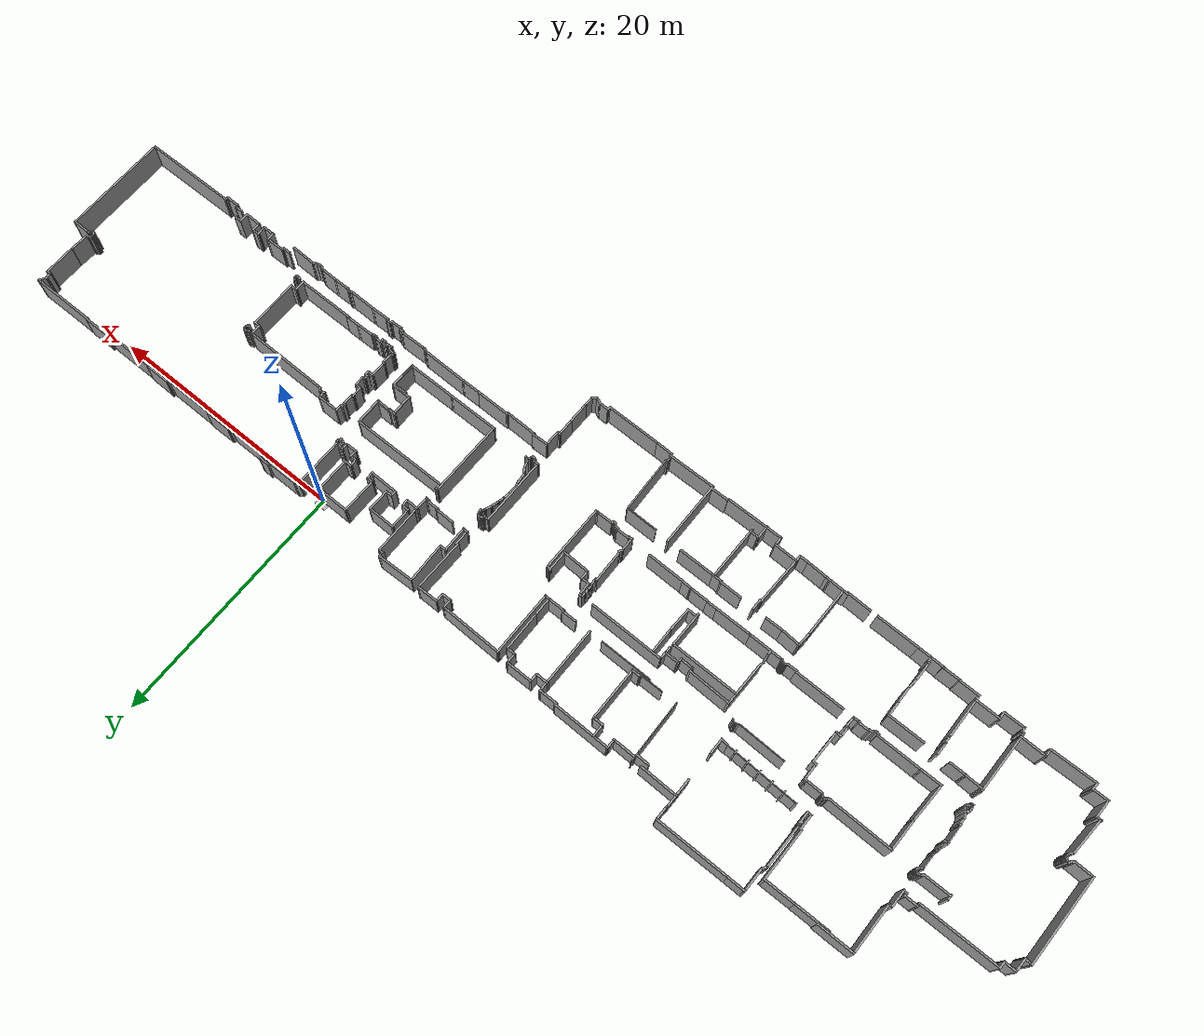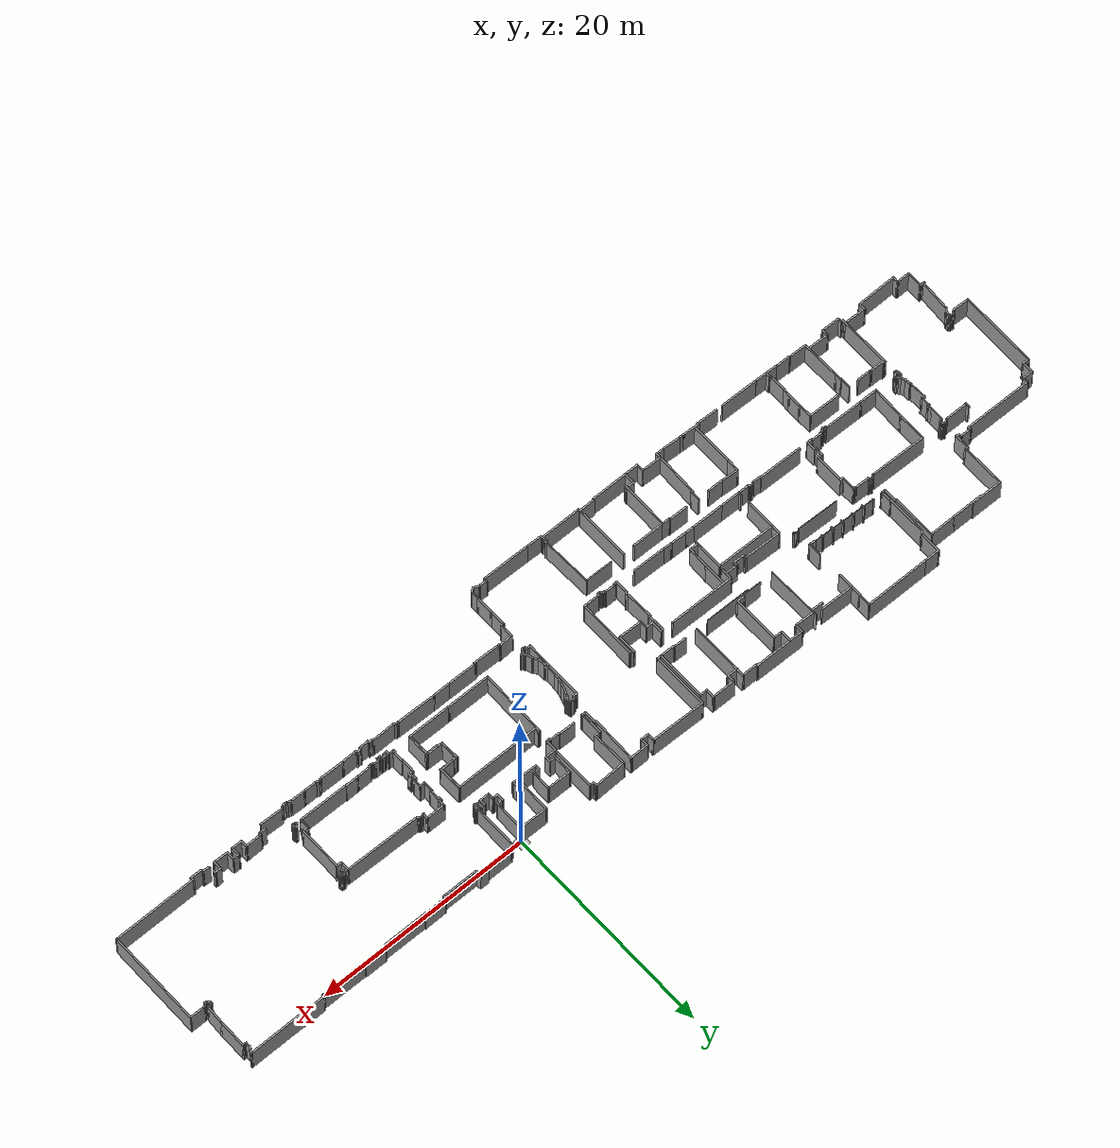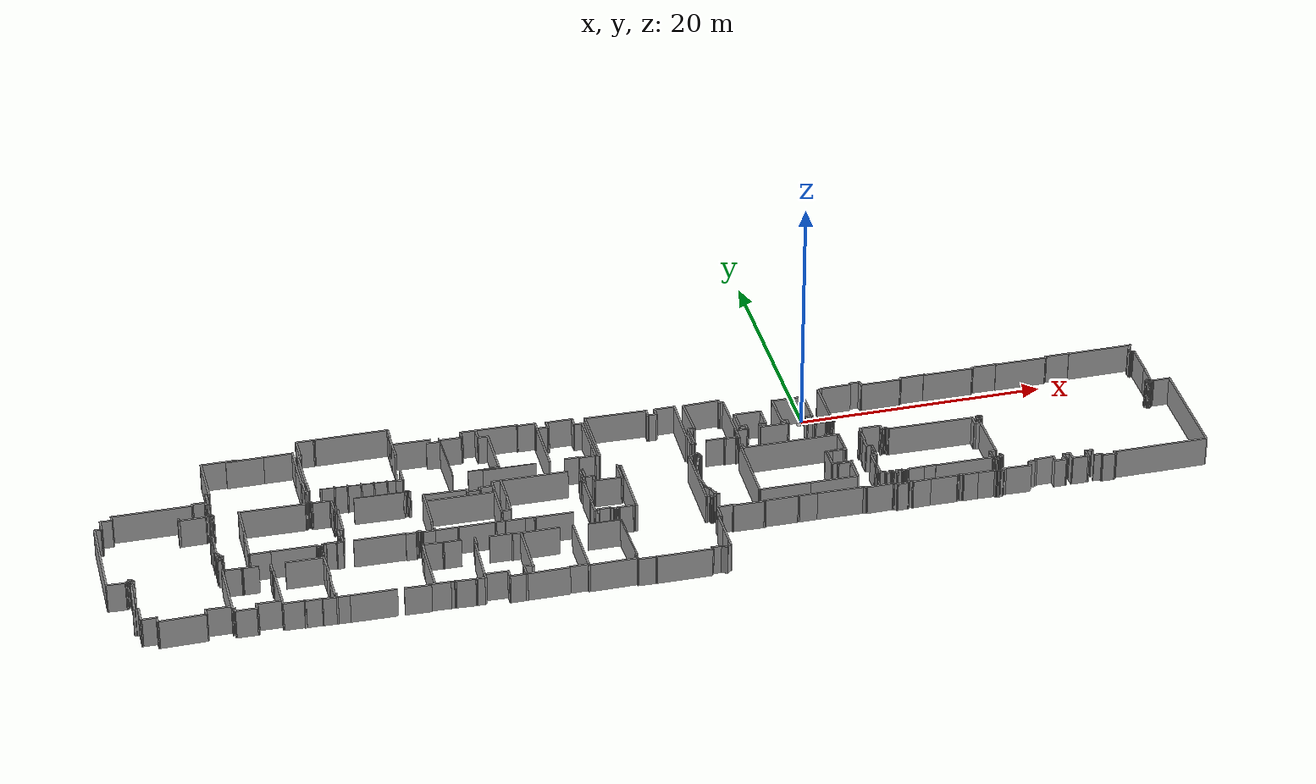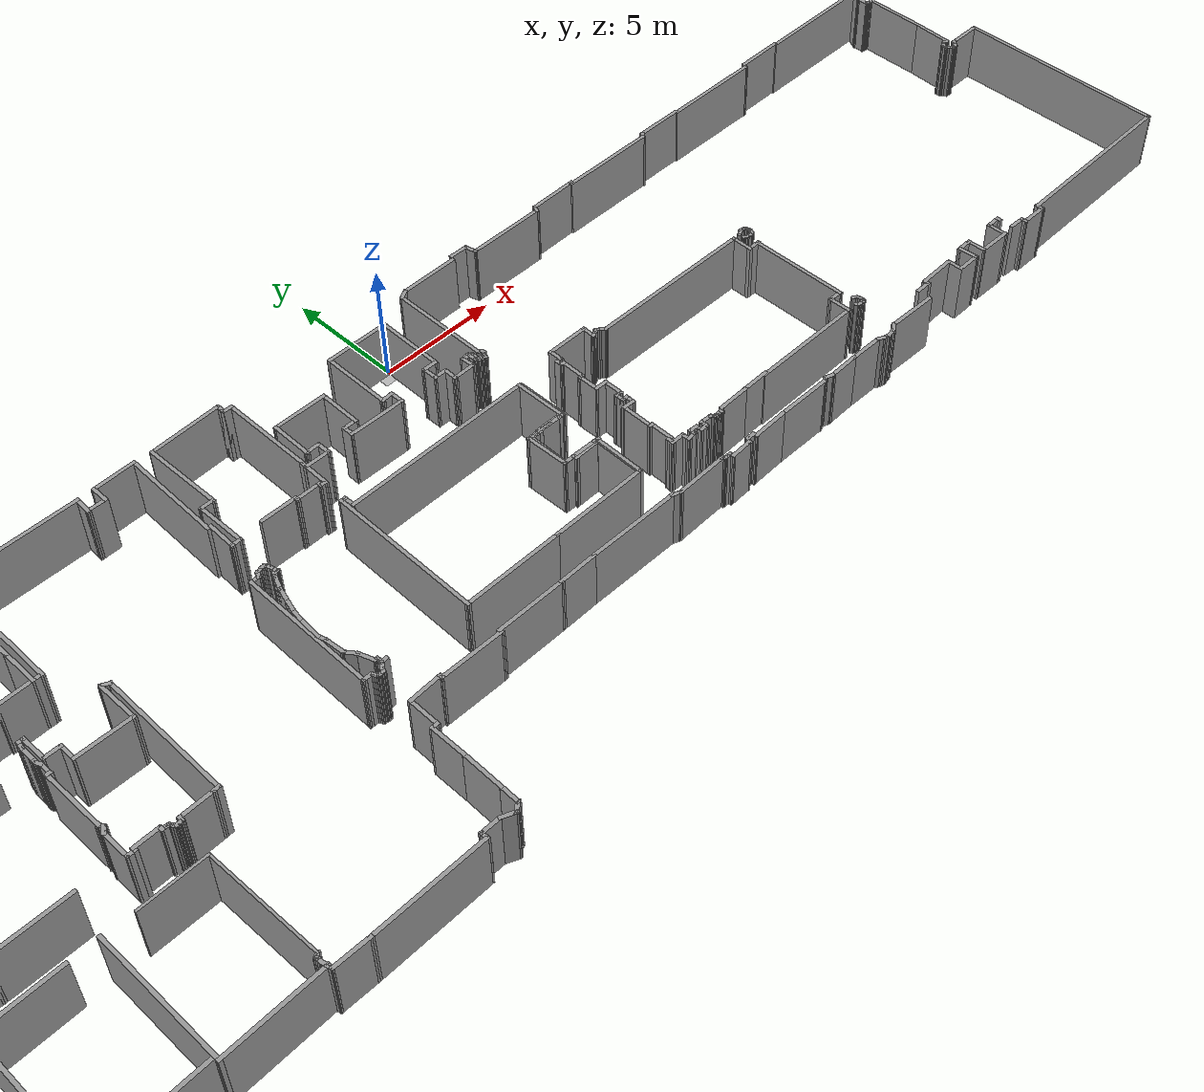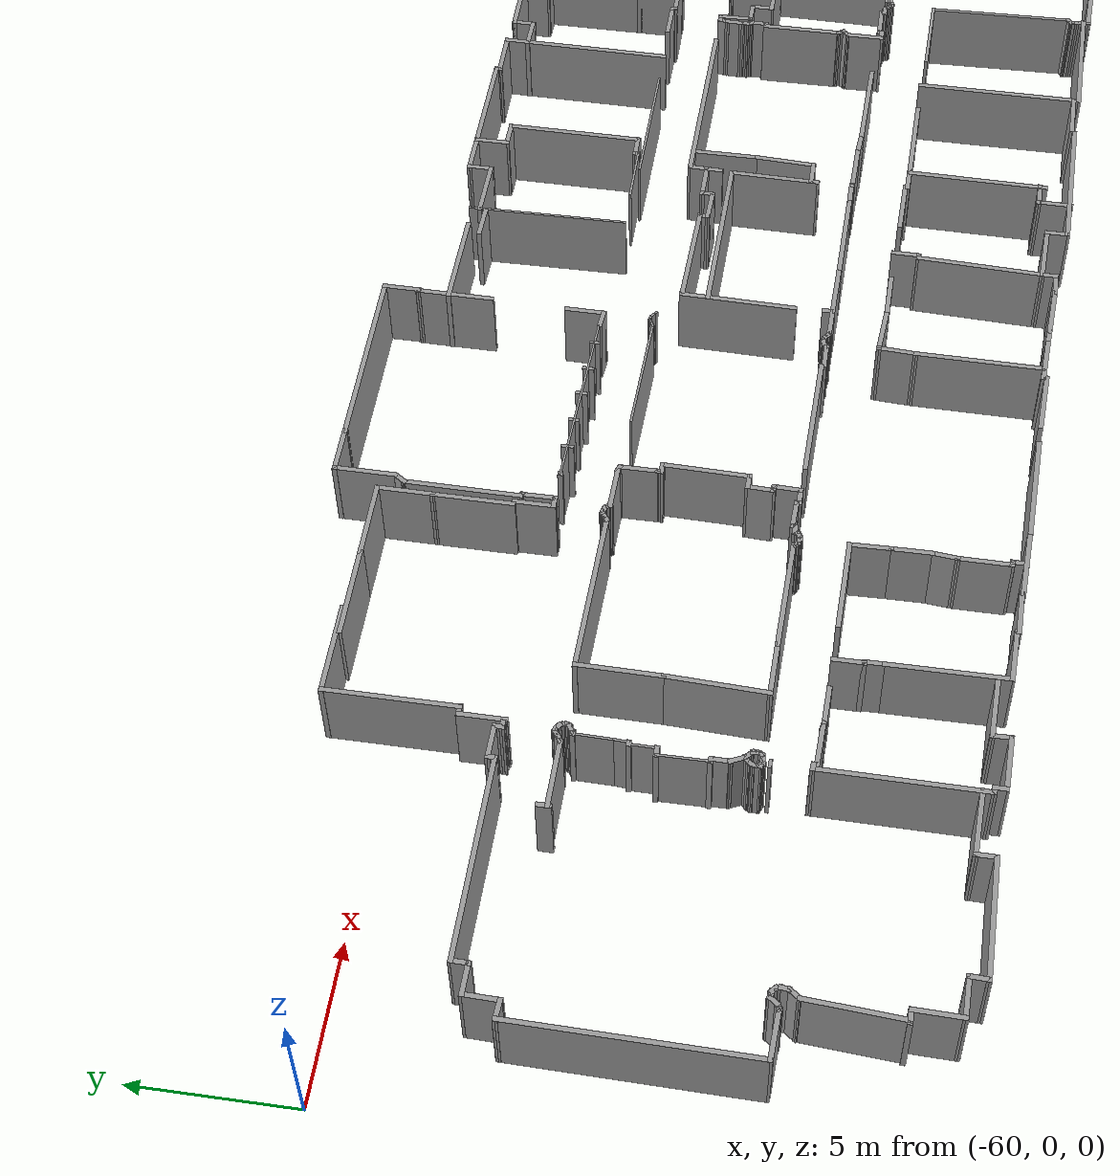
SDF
<?xml version="1.0" ?>
<sdf version="1.4">
  <world name="default">
	<scene>
      <ambient>0.500000 0.500000 0.500000 1.000000</ambient>
      <background>0.500000 0.500000 0.500000 1.000000</background>
      <shadows>0</shadows>
      <grid>false</grid>
    </scene>
    <physics type="ode">
      <gravity>0.000000 0.000000 -9.800000</gravity>
      <ode>
        <solver>
          <type>quick</type>
          <iters>10</iters>
          <sor>1.300000</sor>
        </solver>
        <constraints>
          <cfm>0.000000</cfm>
          <erp>0.200000</erp>
          <contact_max_correcting_vel>100.000000</contact_max_correcting_vel>
          <contact_surface_layer>0.001000</contact_surface_layer>
        </constraints>
      </ode>
      <real_time_update_rate>3000.000000</real_time_update_rate>
      <max_step_size>0.001000</max_step_size>
    </physics>
	<model name="plane1_model">
      <link name="body">
        <collision name="geom_1">
          <geometry>
            <plane>
              <normal>0.000000 0.000000 1.000000</normal>
              <size>1.000000 1.000000</size>
            </plane>
          </geometry>
          <surface>
            <friction>
              <ode>
                <mu>10.000000</mu>
                <mu2>10.000000</mu2>
                <fdir1>0.000000 0.000000 0.000000</fdir1>
                <slip1>0.000000</slip1>
                <slip2>0.000000</slip2>
              </ode>
            </friction>
            <bounce>
              <restitution_coefficient>0.000000</restitution_coefficient>
              <threshold>1000000.000000</threshold>
            </bounce>
            <contact>
              <ode>
                <soft_cfm>0.000000</soft_cfm>
                <soft_erp>0.200000</soft_erp>
                <kp>10000000000.000000</kp>
                <kd>1.000000</kd>
                <max_vel>100.000000</max_vel>
                <min_depth>0.000100</min_depth>
              </ode>
            </contact>
          </surface>
        </collision>
		<visual name="visual_1">
          <geometry>
            <plane>
              <normal>0.000000 0.000000 1.000000</normal>
              <size>1.000000 1.000000</size>
            </plane>
          </geometry>
          <material>
            <script>
              <name>__default__</name>
            </script>
          </material>
          <cast_shadows>0</cast_shadows>
        </visual>
        <velocity_decay>
          <linear>0.000000</linear>
          <angular>0.000000</angular>
        </velocity_decay>
        <self_collide>0</self_collide>
        <kinematic>0</kinematic>
      </link>
      <static>1</static>
    </model>
    <include>
      <uri>model://sun</uri>
    </include>

    <model name="building-east">
        <pose>-13.970314 -9.174326 0 0 0 0</pose>
        <include>
          <static>true</static>
          <uri>3e_real</uri>
        </include>
    </model>
    <model name="building-north1">
        <pose>-14.016079 25.839033 0 0 0 0</pose>
        <include>
          <static>true</static>
          <uri>3n_real</uri>
        </include>
    </model>
  </world>
</sdf>

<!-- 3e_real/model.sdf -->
<sdf version='1.4'>
  <model name='3_e'>
    <pose frame=''>28.6843 2.78166 0 0 -0 0</pose>
    <link name='Wall_0'>
      <collision name='Wall_0_Collision'>
        <geometry>
          <box>
            <size>2.23163 0.15 2.5</size>
          </box>
        </geometry>
        <pose frame=''>0 0 1.25 0 -0 0</pose>
      </collision>
      <visual name='Wall_0_Visual'>
        <pose frame=''>0 0 1.25 0 -0 0</pose>
        <geometry>
          <box>
            <size>2.23163 0.15 2.5</size>
          </box>
        </geometry>
        <material>
          <script>
            <uri>file://media/materials/scripts/gazebo.material</uri>
            <name>Gazebo/Grey</name>
          </script>
          <ambient>1 1 1 1</ambient>
        </material>
      </visual>
      <pose frame=''>-13.3205 -0.529565 0 0 0 -1.55975</pose>
    </link>
    <link name='Wall_1'>
      <collision name='Wall_1_Collision'>
        <geometry>
          <box>
            <size>0.3455 0.15 2.5</size>
          </box>
        </geometry>
        <pose frame=''>0 0 1.25 0 -0 0</pose>
      </collision>
      <visual name='Wall_1_Visual'>
        <pose frame=''>0 0 1.25 0 -0 0</pose>
        <geometry>
          <box>
            <size>0.3455 0.15 2.5</size>
          </box>
        </geometry>
        <material>
          <script>
            <uri>file://media/materials/scripts/gazebo.material</uri>
            <name>Gazebo/Grey</name>
          </script>
          <ambient>1 1 1 1</ambient>
        </material>
      </visual>
      <pose frame=''>-13.4067 -1.57031 0 0 -0 3.14159</pose>
    </link>
    <link name='Wall_10'>
      <collision name='Wall_10_Collision'>
        <geometry>
          <box>
            <size>1.12757 0.15 2.5</size>
          </box>
        </geometry>
        <pose frame=''>0 0 1.25 0 -0 0</pose>
      </collision>
      <visual name='Wall_10_Visual'>
        <pose frame=''>0 0 1.25 0 -0 0</pose>
        <geometry>
          <box>
            <size>1.12757 0.15 2.5</size>
          </box>
        </geometry>
        <material>
          <script>
            <uri>file://media/materials/scripts/gazebo.material</uri>
            <name>Gazebo/Grey</name>
          </script>
          <ambient>1 1 1 1</ambient>
        </material>
      </visual>
      <pose frame=''>-13.9645 -3.3328 0 0 -0 0.011764</pose>
    </link>
    <link name='Wall_100'>
      <collision name='Wall_100_Collision'>
        <geometry>
          <box>
            <size>1.07773 0.15 2.5</size>
          </box>
        </geometry>
        <pose frame=''>0 0 1.25 0 -0 0</pose>
      </collision>
      <visual name='Wall_100_Visual'>
        <pose frame=''>0 0 1.25 0 -0 0</pose>
        <geometry>
          <box>
            <size>1.07773 0.15 2.5</size>
          </box>
        </geometry>
        <material>
          <script>
            <uri>file://media/materials/scripts/gazebo.material</uri>
            <name>Gazebo/Grey</name>
          </script>
          <ambient>1 1 1 1</ambient>
        </material>
      </visual>
      <pose frame=''>2.77623 -6.99337 0 0 -0 0</pose>
    </link>
    <link name='Wall_101'>
      <collision name='Wall_101_Collision'>
        <geometry>
          <box>
            <size>0.867395 0.15 2.5</size>
          </box>
        </geometry>
        <pose frame=''>0 0 1.25 0 -0 0</pose>
      </collision>
      <visual name='Wall_101_Visual'>
        <pose frame=''>0 0 1.25 0 -0 0</pose>
        <geometry>
          <box>
            <size>0.867395 0.15 2.5</size>
          </box>
        </geometry>
        <material>
          <script>
            <uri>file://media/materials/scripts/gazebo.material</uri>
            <name>Gazebo/Grey</name>
          </script>
          <ambient>1 1 1 1</ambient>
        </material>
      </visual>
      <pose frame=''>3.20967 -6.63596 0 0 -0 1.6557</pose>
    </link>
    <link name='Wall_102'>
      <collision name='Wall_102_Collision'>
        <geometry>
          <box>
            <size>0.697515 0.15 2.5</size>
          </box>
        </geometry>
        <pose frame=''>0 0 1.25 0 -0 0</pose>
      </collision>
      <visual name='Wall_102_Visual'>
        <pose frame=''>0 0 1.25 0 -0 0</pose>
        <geometry>
          <box>
            <size>0.697515 0.15 2.5</size>
          </box>
        </geometry>
        <material>
          <script>
            <uri>file://media/materials/scripts/gazebo.material</uri>
            <name>Gazebo/Grey</name>
          </script>
          <ambient>1 1 1 1</ambient>
        </material>
      </visual>
      <pose frame=''>3.45301 -6.27856 0 0 -0 0</pose>
    </link>
    <link name='Wall_103'>
      <collision name='Wall_103_Collision'>
        <geometry>
          <box>
            <size>0.835069 0.15 2.5</size>
          </box>
        </geometry>
        <pose frame=''>0 0 1.25 0 -0 0</pose>
      </collision>
      <visual name='Wall_103_Visual'>
        <pose frame=''>0 0 1.25 0 -0 0</pose>
        <geometry>
          <box>
            <size>0.835069 0.15 2.5</size>
          </box>
        </geometry>
        <material>
          <script>
            <uri>file://media/materials/scripts/gazebo.material</uri>
            <name>Gazebo/Grey</name>
          </script>
          <ambient>1 1 1 1</ambient>
        </material>
      </visual>
      <pose frame=''>3.74198 -6.62076 0 0 0 -1.52638</pose>
    </link>
    <link name='Wall_104'>
      <collision name='Wall_104_Collision'>
        <geometry>
          <box>
            <size>1.45831 0.15 2.5</size>
          </box>
        </geometry>
        <pose frame=''>0 0 1.25 0 -0 0</pose>
      </collision>
      <visual name='Wall_104_Visual'>
        <pose frame=''>0 0 1.25 0 -0 0</pose>
        <geometry>
          <box>
            <size>1.45831 0.15 2.5</size>
          </box>
        </geometry>
        <material>
          <script>
            <uri>file://media/materials/scripts/gazebo.material</uri>
            <name>Gazebo/Grey</name>
          </script>
          <ambient>1 1 1 1</ambient>
        </material>
      </visual>
      <pose frame=''>4.41117 -6.97816 0 0 0 -0.023252</pose>
    </link>
    <link name='Wall_106'>
      <collision name='Wall_106_Collision'>
        <geometry>
          <box>
            <size>0.88002 0.15 2.5</size>
          </box>
        </geometry>
        <pose frame=''>0 0 1.25 0 -0 0</pose>
      </collision>
      <visual name='Wall_106_Visual'>
        <pose frame=''>0 0 1.25 0 -0 0</pose>
        <geometry>
          <box>
            <size>0.88002 0.15 2.5</size>
          </box>
        </geometry>
        <material>
          <script>
            <uri>file://media/materials/scripts/gazebo.material</uri>
            <name>Gazebo/Grey</name>
          </script>
          <ambient>1 1 1 1</ambient>
        </material>
      </visual>
      <pose frame=''>5.03472 -6.62836 0 0 -0 1.5708</pose>
    </link>
    <link name='Wall_107'>
      <collision name='Wall_107_Collision'>
        <geometry>
          <box>
            <size>0.667097 0.15 2.5</size>
          </box>
        </geometry>
        <pose frame=''>0 0 1.25 0 -0 0</pose>
      </collision>
      <visual name='Wall_107_Visual'>
        <pose frame=''>0 0 1.25 0 -0 0</pose>
        <geometry>
          <box>
            <size>0.667097 0.15 2.5</size>
          </box>
        </geometry>
        <material>
          <script>
            <uri>file://media/materials/scripts/gazebo.material</uri>
            <name>Gazebo/Grey</name>
          </script>
          <ambient>1 1 1 1</ambient>
        </material>
      </visual>
      <pose frame=''>5.29327 -6.26335 0 0 -0 0</pose>
    </link>
    <link name='Wall_108'>
      <collision name='Wall_108_Collision'>
        <geometry>
          <box>
            <size>0.25 0.15 2.5</size>
          </box>
        </geometry>
        <pose frame=''>0 0 1.25 0 -0 0</pose>
      </collision>
      <visual name='Wall_108_Visual'>
        <pose frame=''>0 0 1.25 0 -0 0</pose>
        <geometry>
          <box>
            <size>0.25 0.15 2.5</size>
          </box>
        </geometry>
        <material>
          <script>
            <uri>file://media/materials/scripts/gazebo.material</uri>
            <name>Gazebo/Grey</name>
          </script>
          <ambient>1 1 1 1</ambient>
        </material>
      </visual>
      <pose frame=''>5.55182 -6.31335 0 0 0 -1.5708</pose>
    </link>
    <link name='Wall_11'>
      <collision name='Wall_11_Collision'>
        <geometry>
          <box>
            <size>0.219 0.15 2.5</size>
          </box>
        </geometry>
        <pose frame=''>0 0 1.25 0 -0 0</pose>
      </collision>
      <visual name='Wall_11_Visual'>
        <pose frame=''>0 0 1.25 0 -0 0</pose>
        <geometry>
          <box>
            <size>0.219 0.15 2.5</size>
          </box>
        </geometry>
        <material>
          <script>
            <uri>file://media/materials/scripts/gazebo.material</uri>
            <name>Gazebo/Grey</name>
          </script>
          <ambient>1 1 1 1</ambient>
        </material>
      </visual>
      <pose frame=''>-13.4758 -3.29255 0 0 -0 1.5708</pose>
    </link>
    <link name='Wall_110'>
      <collision name='Wall_110_Collision'>
        <geometry>
          <box>
            <size>0.728732 0.15 2.5</size>
          </box>
        </geometry>
        <pose frame=''>0 0 1.25 0 -0 0</pose>
      </collision>
      <visual name='Wall_110_Visual'>
        <pose frame=''>0 0 1.25 0 -0 0</pose>
        <geometry>
          <box>
            <size>0.728732 0.15 2.5</size>
          </box>
        </geometry>
        <material>
          <script>
            <uri>file://media/materials/scripts/gazebo.material</uri>
            <name>Gazebo/Grey</name>
          </script>
          <ambient>1 1 1 1</ambient>
        </material>
      </visual>
      <pose frame=''>5.88641 -6.94774 0 0 0 -0.052583</pose>
    </link>
    <link name='Wall_111'>
      <collision name='Wall_111_Collision'>
        <geometry>
          <box>
            <size>0.317986 0.15 2.5</size>
          </box>
        </geometry>
        <pose frame=''>0 0 1.25 0 -0 0</pose>
      </collision>
      <visual name='Wall_111_Visual'>
        <pose frame=''>0 0 1.25 0 -0 0</pose>
        <geometry>
          <box>
            <size>0.317986 0.15 2.5</size>
          </box>
        </geometry>
        <material>
          <script>
            <uri>file://media/materials/scripts/gazebo.material</uri>
            <name>Gazebo/Grey</name>
          </script>
          <ambient>1 1 1 1</ambient>
        </material>
      </visual>
      <pose frame=''>6.18299 -7.0466 0 0 0 -1.48014</pose>
    </link>
    <link name='Wall_112'>
      <collision name='Wall_112_Collision'>
        <geometry>
          <box>
            <size>1.19951 0.15 2.5</size>
          </box>
        </geometry>
        <pose frame=''>0 0 1.25 0 -0 0</pose>
      </collision>
      <visual name='Wall_112_Visual'>
        <pose frame=''>0 0 1.25 0 -0 0</pose>
        <geometry>
          <box>
            <size>1.19951 0.15 2.5</size>
          </box>
        </geometry>
        <material>
          <script>
            <uri>file://media/materials/scripts/gazebo.material</uri>
            <name>Gazebo/Grey</name>
          </script>
          <ambient>1 1 1 1</ambient>
        </material>
      </visual>
      <pose frame=''>6.71529 -7.13785 0 0 0 -0.014492</pose>
    </link>
    <link name='Wall_113'>
      <collision name='Wall_113_Collision'>
        <geometry>
          <box>
            <size>0.39334 0.15 2.5</size>
          </box>
        </geometry>
        <pose frame=''>0 0 1.25 0 -0 0</pose>
      </collision>
      <visual name='Wall_113_Visual'>
        <pose frame=''>0 0 1.25 0 -0 0</pose>
        <geometry>
          <box>
            <size>0.39334 0.15 2.5</size>
          </box>
        </geometry>
        <material>
          <script>
            <uri>file://media/materials/scripts/gazebo.material</uri>
            <name>Gazebo/Grey</name>
          </script>
          <ambient>1 1 1 1</ambient>
        </material>
      </visual>
      <pose frame=''>7.23999 -7.02379 0 0 -0 1.5708</pose>
    </link>
    <link name='Wall_117'>
      <collision name='Wall_117_Collision'>
        <geometry>
          <box>
            <size>7.80038 0.15 2.5</size>
          </box>
        </geometry>
        <pose frame=''>0 0 1.25 0 -0 0</pose>
      </collision>
      <visual name='Wall_117_Visual'>
        <pose frame=''>0 0 1.25 0 -0 0</pose>
        <geometry>
          <box>
            <size>7.80038 0.15 2.5</size>
          </box>
        </geometry>
        <material>
          <script>
            <uri>file://media/materials/scripts/gazebo.material</uri>
            <name>Gazebo/Grey</name>
          </script>
          <ambient>1 1 1 1</ambient>
        </material>
      </visual>
      <pose frame=''>11.0437 -6.90568 0 0 -0 0.005964</pose>
    </link>
    <link name='Wall_119'>
      <collision name='Wall_119_Collision'>
        <geometry>
          <box>
            <size>8.94846 0.15 2.5</size>
          </box>
        </geometry>
        <pose frame=''>0 0 1.25 0 -0 0</pose>
      </collision>
      <visual name='Wall_119_Visual'>
        <pose frame=''>0 0 1.25 0 -0 0</pose>
        <geometry>
          <box>
            <size>8.94846 0.15 2.5</size>
          </box>
        </geometry>
        <material>
          <script>
            <uri>file://media/materials/scripts/gazebo.material</uri>
            <name>Gazebo/Grey</name>
          </script>
          <ambient>1 1 1 1</ambient>
        </material>
      </visual>
      <pose frame=''>14.858 -2.48364 0 0 -0 1.57324</pose>
    </link>
    <link name='Wall_12'>
      <collision name='Wall_12_Collision'>
        <geometry>
          <box>
            <size>0.334359 0.15 2.5</size>
          </box>
        </geometry>
        <pose frame=''>0 0 1.25 0 -0 0</pose>
      </collision>
      <visual name='Wall_12_Visual'>
        <pose frame=''>0 0 1.25 0 -0 0</pose>
        <geometry>
          <box>
            <size>0.334359 0.15 2.5</size>
          </box>
        </geometry>
        <material>
          <script>
            <uri>file://media/materials/scripts/gazebo.material</uri>
            <name>Gazebo/Grey</name>
          </script>
          <ambient>1 1 1 1</ambient>
        </material>
      </visual>
      <pose frame=''>-13.3838 -3.2638 0 0 0 -0.062419</pose>
    </link>
    <link name='Wall_121'>
      <collision name='Wall_121_Collision'>
        <geometry>
          <box>
            <size>1.5 0.15 2.5</size>
          </box>
        </geometry>
        <pose frame=''>0 0 1.25 0 -0 0</pose>
      </collision>
      <visual name='Wall_121_Visual'>
        <pose frame=''>0 0 1.25 0 -0 0</pose>
        <geometry>
          <box>
            <size>1.5 0.15 2.5</size>
          </box>
        </geometry>
        <material>
          <script>
            <uri>file://media/materials/scripts/gazebo.material</uri>
            <name>Gazebo/Grey</name>
          </script>
          <ambient>1 1 1 1</ambient>
        </material>
      </visual>
      <pose frame=''>14.1722 1.91559 0 0 -0 3.14159</pose>
    </link>
    <link name='Wall_122'>
      <collision name='Wall_122_Collision'>
        <geometry>
          <box>
            <size>0.274193 0.15 2.5</size>
          </box>
        </geometry>
        <pose frame=''>0 0 1.25 0 -0 0</pose>
      </collision>
      <visual name='Wall_122_Visual'>
        <pose frame=''>0 0 1.25 0 -0 0</pose>
        <geometry>
          <box>
            <size>0.274193 0.15 2.5</size>
          </box>
        </geometry>
        <material>
          <script>
            <uri>file://media/materials/scripts/gazebo.material</uri>
            <name>Gazebo/Grey</name>
          </script>
          <ambient>1 1 1 1</ambient>
        </material>
      </visual>
      <pose frame=''>13.4377 1.8981 0 0 0 -2.85607</pose>
    </link>
    <link name='Wall_123'>
      <collision name='Wall_123_Collision'>
        <geometry>
          <box>
            <size>0.315001 0.15 2.5</size>
          </box>
        </geometry>
        <pose frame=''>0 0 1.25 0 -0 0</pose>
      </collision>
      <visual name='Wall_123_Visual'>
        <pose frame=''>0 0 1.25 0 -0 0</pose>
        <geometry>
          <box>
            <size>0.315001 0.15 2.5</size>
          </box>
        </geometry>
        <material>
          <script>
            <uri>file://media/materials/scripts/gazebo.material</uri>
            <name>Gazebo/Grey</name>
          </script>
          <ambient>1 1 1 1</ambient>
        </material>
      </visual>
      <pose frame=''>13.3344 1.81065 0 0 0 -2.1294</pose>
    </link>
    <link name='Wall_124'>
      <collision name='Wall_124_Collision'>
        <geometry>
          <box>
            <size>0.251984 0.15 2.5</size>
          </box>
        </geometry>
        <pose frame=''>0 0 1.25 0 -0 0</pose>
      </collision>
      <visual name='Wall_124_Visual'>
        <pose frame=''>0 0 1.25 0 -0 0</pose>
        <geometry>
          <box>
            <size>0.251984 0.15 2.5</size>
          </box>
        </geometry>
        <material>
          <script>
            <uri>file://media/materials/scripts/gazebo.material</uri>
            <name>Gazebo/Grey</name>
          </script>
          <ambient>1 1 1 1</ambient>
        </material>
      </visual>
      <pose frame=''>13.2469 1.71446 0 0 0 -2.60117</pose>
    </link>
    <link name='Wall_125'>
      <collision name='Wall_125_Collision'>
        <geometry>
          <box>
            <size>0.27243 0.15 2.5</size>
          </box>
        </geometry>
        <pose frame=''>0 0 1.25 0 -0 0</pose>
      </collision>
      <visual name='Wall_125_Visual'>
        <pose frame=''>0 0 1.25 0 -0 0</pose>
        <geometry>
          <box>
            <size>0.27243 0.15 2.5</size>
          </box>
        </geometry>
        <material>
          <script>
            <uri>file://media/materials/scripts/gazebo.material</uri>
            <name>Gazebo/Grey</name>
          </script>
          <ambient>1 1 1 1</ambient>
        </material>
      </visual>
      <pose frame=''>13.142 1.68822 0 0 -0 3.14159</pose>
    </link>
    <link name='Wall_126'>
      <collision name='Wall_126_Collision'>
        <geometry>
          <box>
            <size>0.300455 0.15 2.5</size>
          </box>
        </geometry>
        <pose frame=''>0 0 1.25 0 -0 0</pose>
      </collision>
      <visual name='Wall_126_Visual'>
        <pose frame=''>0 0 1.25 0 -0 0</pose>
        <geometry>
          <box>
            <size>0.300455 0.15 2.5</size>
          </box>
        </geometry>
        <material>
          <script>
            <uri>file://media/materials/scripts/gazebo.material</uri>
            <name>Gazebo/Grey</name>
          </script>
          <ambient>1 1 1 1</ambient>
        </material>
      </visual>
      <pose frame=''>13.037 1.74944 0 0 -0 2.19105</pose>
    </link>
    <link name='Wall_127'>
      <collision name='Wall_127_Collision'>
        <geometry>
          <box>
            <size>0.273673 0.15 2.5</size>
          </box>
        </geometry>
        <pose frame=''>0 0 1.25 0 -0 0</pose>
      </collision>
      <visual name='Wall_127_Visual'>
        <pose frame=''>0 0 1.25 0 -0 0</pose>
        <geometry>
          <box>
            <size>0.273673 0.15 2.5</size>
          </box>
        </geometry>
        <material>
          <script>
            <uri>file://media/materials/scripts/gazebo.material</uri>
            <name>Gazebo/Grey</name>
          </script>
          <ambient>1 1 1 1</ambient>
        </material>
      </visual>
      <pose frame=''>12.9496 1.85438 0 0 -0 2.35619</pose>
    </link>
    <link name='Wall_128'>
      <collision name='Wall_128_Collision'>
        <geometry>
          <box>
            <size>0.307411 0.15 2.5</size>
          </box>
        </geometry>
        <pose frame=''>0 0 1.25 0 -0 0</pose>
      </collision>
      <visual name='Wall_128_Visual'>
        <pose frame=''>0 0 1.25 0 -0 0</pose>
        <geometry>
          <box>
            <size>0.307411 0.15 2.5</size>
          </box>
        </geometry>
        <material>
          <script>
            <uri>file://media/materials/scripts/gazebo.material</uri>
            <name>Gazebo/Grey</name>
          </script>
          <ambient>1 1 1 1</ambient>
        </material>
      </visual>
      <pose frame=''>12.9058 1.97681 0 0 -0 1.5708</pose>
    </link>
    <link name='Wall_129'>
      <collision name='Wall_129_Collision'>
        <geometry>
          <box>
            <size>0.276123 0.15 2.5</size>
          </box>
        </geometry>
        <pose frame=''>0 0 1.25 0 -0 0</pose>
      </collision>
      <visual name='Wall_129_Visual'>
        <pose frame=''>0 0 1.25 0 -0 0</pose>
        <geometry>
          <box>
            <size>0.276123 0.15 2.5</size>
          </box>
        </geometry>
        <material>
          <script>
            <uri>file://media/materials/scripts/gazebo.material</uri>
            <name>Gazebo/Grey</name>
          </script>
          <ambient>1 1 1 1</ambient>
        </material>
      </visual>
      <pose frame=''>12.9583 2.09049 0 0 -0 0.588003</pose>
    </link>
    <link name='Wall_130'>
      <collision name='Wall_130_Collision'>
        <geometry>
          <box>
            <size>0.276123 0.15 2.5</size>
          </box>
        </geometry>
        <pose frame=''>0 0 1.25 0 -0 0</pose>
      </collision>
      <visual name='Wall_130_Visual'>
        <pose frame=''>0 0 1.25 0 -0 0</pose>
        <geometry>
          <box>
            <size>0.276123 0.15 2.5</size>
          </box>
        </geometry>
        <material>
          <script>
            <uri>file://media/materials/scripts/gazebo.material</uri>
            <name>Gazebo/Grey</name>
          </script>
          <ambient>1 1 1 1</ambient>
        </material>
      </visual>
      <pose frame=''>13.0633 2.16045 0 0 -0 0.588003</pose>
    </link>
    <link name='Wall_131'>
      <collision name='Wall_131_Collision'>
        <geometry>
          <box>
            <size>0.31125 0.15 2.5</size>
          </box>
        </geometry>
        <pose frame=''>0 0 1.25 0 -0 0</pose>
      </collision>
      <visual name='Wall_131_Visual'>
        <pose frame=''>0 0 1.25 0 -0 0</pose>
        <geometry>
          <box>
            <size>0.31125 0.15 2.5</size>
          </box>
        </geometry>
        <material>
          <script>
            <uri>file://media/materials/scripts/gazebo.material</uri>
            <name>Gazebo/Grey</name>
          </script>
          <ambient>1 1 1 1</ambient>
        </material>
      </visual>
      <pose frame=''>13.1944 2.17794 0 0 0 -0.218669</pose>
    </link>
    <link name='Wall_132'>
      <collision name='Wall_132_Collision'>
        <geometry>
          <box>
            <size>1.76061 0.15 2.5</size>
          </box>
        </geometry>
        <pose frame=''>0 0 1.25 0 -0 0</pose>
      </collision>
      <visual name='Wall_132_Visual'>
        <pose frame=''>0 0 1.25 0 -0 0</pose>
        <geometry>
          <box>
            <size>1.76061 0.15 2.5</size>
          </box>
        </geometry>
        <material>
          <script>
            <uri>file://media/materials/scripts/gazebo.material</uri>
            <name>Gazebo/Grey</name>
          </script>
          <ambient>1 1 1 1</ambient>
        </material>
      </visual>
      <pose frame=''>13.3081 2.965 0 0 -0 1.52734</pose>
    </link>
    <link name='Wall_134'>
      <collision name='Wall_134_Collision'>
        <geometry>
          <box>
            <size>2.72104 0.15 2.5</size>
          </box>
        </geometry>
        <pose frame=''>0 0 1.25 0 -0 0</pose>
      </collision>
      <visual name='Wall_134_Visual'>
        <pose frame=''>0 0 1.25 0 -0 0</pose>
        <geometry>
          <box>
            <size>2.72104 0.15 2.5</size>
          </box>
        </geometry>
        <material>
          <script>
            <uri>file://media/materials/scripts/gazebo.material</uri>
            <name>Gazebo/Grey</name>
          </script>
          <ambient>1 1 1 1</ambient>
        </material>
      </visual>
      <pose frame=''>13.3431 5.05506 0 0 -0 1.5708</pose>
    </link>
    <link name='Wall_135'>
      <collision name='Wall_135_Collision'>
        <geometry>
          <box>
            <size>0.25 0.15 2.5</size>
          </box>
        </geometry>
        <pose frame=''>0 0 1.25 0 -0 0</pose>
      </collision>
      <visual name='Wall_135_Visual'>
        <pose frame=''>0 0 1.25 0 -0 0</pose>
        <geometry>
          <box>
            <size>0.25 0.15 2.5</size>
          </box>
        </geometry>
        <material>
          <script>
            <uri>file://media/materials/scripts/gazebo.material</uri>
            <name>Gazebo/Grey</name>
          </script>
          <ambient>1 1 1 1</ambient>
        </material>
      </visual>
      <pose frame=''>13.2948 6.32764 0 0 0 -2.87979</pose>
    </link>
    <link name='Wall_136'>
      <collision name='Wall_136_Collision'>
        <geometry>
          <box>
            <size>0.25 0.15 2.5</size>
          </box>
        </geometry>
        <pose frame=''>0 0 1.25 0 -0 0</pose>
      </collision>
      <visual name='Wall_136_Visual'>
        <pose frame=''>0 0 1.25 0 -0 0</pose>
        <geometry>
          <box>
            <size>0.25 0.15 2.5</size>
          </box>
        </geometry>
        <material>
          <script>
            <uri>file://media/materials/scripts/gazebo.material</uri>
            <name>Gazebo/Grey</name>
          </script>
          <ambient>1 1 1 1</ambient>
        </material>
      </visual>
      <pose frame=''>13.1965 6.3147 0 0 -0 3.14159</pose>
    </link>
    <link name='Wall_137'>
      <collision name='Wall_137_Collision'>
        <geometry>
          <box>
            <size>0.25 0.15 2.5</size>
          </box>
        </geometry>
        <pose frame=''>0 0 1.25 0 -0 0</pose>
      </collision>
      <visual name='Wall_137_Visual'>
        <pose frame=''>0 0 1.25 0 -0 0</pose>
        <geometry>
          <box>
            <size>0.25 0.15 2.5</size>
          </box>
        </geometry>
        <material>
          <script>
            <uri>file://media/materials/scripts/gazebo.material</uri>
            <name>Gazebo/Grey</name>
          </script>
          <ambient>1 1 1 1</ambient>
        </material>
      </visual>
      <pose frame=''>13.0982 6.32764 0 0 -0 2.87979</pose>
    </link>
    <link name='Wall_138'>
      <collision name='Wall_138_Collision'>
        <geometry>
          <box>
            <size>0.15 0.15 2.5</size>
          </box>
        </geometry>
        <pose frame=''>0 0 1.25 0 -0 0</pose>
      </collision>
      <visual name='Wall_138_Visual'>
        <pose frame=''>0 0 1.25 0 -0 0</pose>
        <geometry>
          <box>
            <size>0.15 0.15 2.5</size>
          </box>
        </geometry>
        <material>
          <script>
            <uri>file://media/materials/scripts/gazebo.material</uri>
            <name>Gazebo/Grey</name>
          </script>
          <ambient>1 1 1 1</ambient>
        </material>
      </visual>
      <pose frame=''>13.0499 6.34058 0 0 -0 0</pose>
    </link>
    <link name='Wall_139'>
      <collision name='Wall_139_Collision'>
        <geometry>
          <box>
            <size>0.568581 0.15 2.5</size>
          </box>
        </geometry>
        <pose frame=''>0 0 1.25 0 -0 0</pose>
      </collision>
      <visual name='Wall_139_Visual'>
        <pose frame=''>0 0 1.25 0 -0 0</pose>
        <geometry>
          <box>
            <size>0.568581 0.15 2.5</size>
          </box>
        </geometry>
        <material>
          <script>
            <uri>file://media/materials/scripts/gazebo.material</uri>
            <name>Gazebo/Grey</name>
          </script>
          <ambient>1 1 1 1</ambient>
        </material>
      </visual>
      <pose frame=''>13.0396 6.54962 0 0 -0 1.62</pose>
    </link>
    <link name='Wall_140'>
      <collision name='Wall_140_Collision'>
        <geometry>
          <box>
            <size>0.75 0.15 2.5</size>
          </box>
        </geometry>
        <pose frame=''>0 0 1.25 0 -0 0</pose>
      </collision>
      <visual name='Wall_140_Visual'>
        <pose frame=''>0 0 1.25 0 -0 0</pose>
        <geometry>
          <box>
            <size>0.75 0.15 2.5</size>
          </box>
        </geometry>
        <material>
          <script>
            <uri>file://media/materials/scripts/gazebo.material</uri>
            <name>Gazebo/Grey</name>
          </script>
          <ambient>1 1 1 1</ambient>
        </material>
      </visual>
      <pose frame=''>13.1693 7.00846 0 0 -0 1.0472</pose>
    </link>
    <link name='Wall_142'>
      <collision name='Wall_142_Collision'>
        <geometry>
          <box>
            <size>5.3732 0.15 2.5</size>
          </box>
        </geometry>
        <pose frame=''>0 0 1.25 0 -0 0</pose>
      </collision>
      <visual name='Wall_142_Visual'>
        <pose frame=''>0 0 1.25 0 -0 0</pose>
        <geometry>
          <box>
            <size>5.3732 0.15 2.5</size>
          </box>
        </geometry>
        <material>
          <script>
            <uri>file://media/materials/scripts/gazebo.material</uri>
            <name>Gazebo/Grey</name>
          </script>
          <ambient>1 1 1 1</ambient>
        </material>
      </visual>
      <pose frame=''>10.7078 7.25589 0 0 0 -3.13685</pose>
    </link>
    <link name='Wall_144'>
      <collision name='Wall_144_Collision'>
        <geometry>
          <box>
            <size>2.13953 0.15 2.5</size>
          </box>
        </geometry>
        <pose frame=''>0 0 1.25 0 -0 0</pose>
      </collision>
      <visual name='Wall_144_Visual'>
        <pose frame=''>0 0 1.25 0 -0 0</pose>
        <geometry>
          <box>
            <size>2.13953 0.15 2.5</size>
          </box>
        </geometry>
        <material>
          <script>
            <uri>file://media/materials/scripts/gazebo.material</uri>
            <name>Gazebo/Grey</name>
          </script>
          <ambient>1 1 1 1</ambient>
        </material>
      </visual>
      <pose frame=''>7.103 7.28679 0 0 -0 0.01156</pose>
    </link>
    <link name='Wall_146'>
      <collision name='Wall_146_Collision'>
        <geometry>
          <box>
            <size>4.3015 0.15 2.5</size>
          </box>
        </geometry>
        <pose frame=''>0 0 1.25 0 -0 0</pose>
      </collision>
      <visual name='Wall_146_Visual'>
        <pose frame=''>0 0 1.25 0 -0 0</pose>
        <geometry>
          <box>
            <size>4.3015 0.15 2.5</size>
          </box>
        </geometry>
        <material>
          <script>
            <uri>file://media/materials/scripts/gazebo.material</uri>
            <name>Gazebo/Grey</name>
          </script>
          <ambient>1 1 1 1</ambient>
        </material>
      </visual>
      <pose frame=''>3.9175 7.12579 0 0 -0 0</pose>
    </link>
    <link name='Wall_147'>
      <collision name='Wall_147_Collision'>
        <geometry>
          <box>
            <size>0.338614 0.15 2.5</size>
          </box>
        </geometry>
        <pose frame=''>0 0 1.25 0 -0 0</pose>
      </collision>
      <visual name='Wall_147_Visual'>
        <pose frame=''>0 0 1.25 0 -0 0</pose>
        <geometry>
          <box>
            <size>0.338614 0.15 2.5</size>
          </box>
        </geometry>
        <material>
          <script>
            <uri>file://media/materials/scripts/gazebo.material</uri>
            <name>Gazebo/Grey</name>
          </script>
          <ambient>1 1 1 1</ambient>
        </material>
      </visual>
      <pose frame=''>6.05075 7.20054 0 0 -0 0.915101</pose>
    </link>
    <link name='Wall_149'>
      <collision name='Wall_149_Collision'>
        <geometry>
          <box>
            <size>2.128 0.15 2.5</size>
          </box>
        </geometry>
        <pose frame=''>0 0 1.25 0 -0 0</pose>
      </collision>
      <visual name='Wall_149_Visual'>
        <pose frame=''>0 0 1.25 0 -0 0</pose>
        <geometry>
          <box>
            <size>2.128 0.15 2.5</size>
          </box>
        </geometry>
        <material>
          <script>
            <uri>file://media/materials/scripts/gazebo.material</uri>
            <name>Gazebo/Grey</name>
          </script>
          <ambient>1 1 1 1</ambient>
        </material>
      </visual>
      <pose frame=''>0.829752 7.18329 0 0 -0 0</pose>
    </link>
    <link name='Wall_151'>
      <collision name='Wall_151_Collision'>
        <geometry>
          <box>
            <size>4.1865 0.15 2.5</size>
          </box>
        </geometry>
        <pose frame=''>0 0 1.25 0 -0 0</pose>
      </collision>
      <visual name='Wall_151_Visual'>
        <pose frame=''>0 0 1.25 0 -0 0</pose>
        <geometry>
          <box>
            <size>4.1865 0.15 2.5</size>
          </box>
        </geometry>
        <material>
          <script>
            <uri>file://media/materials/scripts/gazebo.material</uri>
            <name>Gazebo/Grey</name>
          </script>
          <ambient>1 1 1 1</ambient>
        </material>
      </visual>
      <pose frame=''>-2.2925 7.03379 0 0 -0 0</pose>
    </link>
    <link name='Wall_152'>
      <collision name='Wall_152_Collision'>
        <geometry>
          <box>
            <size>0.338614 0.15 2.5</size>
          </box>
        </geometry>
        <pose frame=''>0 0 1.25 0 -0 0</pose>
      </collision>
      <visual name='Wall_152_Visual'>
        <pose frame=''>0 0 1.25 0 -0 0</pose>
        <geometry>
          <box>
            <size>0.338614 0.15 2.5</size>
          </box>
        </geometry>
        <material>
          <script>
            <uri>file://media/materials/scripts/gazebo.material</uri>
            <name>Gazebo/Grey</name>
          </script>
          <ambient>1 1 1 1</ambient>
        </material>
      </visual>
      <pose frame=''>-0.216747 7.10854 0 0 -0 0.915101</pose>
    </link>
    <link name='Wall_154'>
      <collision name='Wall_154_Collision'>
        <geometry>
          <box>
            <size>2.16263 0.15 2.5</size>
          </box>
        </geometry>
        <pose frame=''>0 0 1.25 0 -0 0</pose>
      </collision>
      <visual name='Wall_154_Visual'>
        <pose frame=''>0 0 1.25 0 -0 0</pose>
        <geometry>
          <box>
            <size>2.16263 0.15 2.5</size>
          </box>
        </geometry>
        <material>
          <script>
            <uri>file://media/materials/scripts/gazebo.material</uri>
            <name>Gazebo/Grey</name>
          </script>
          <ambient>1 1 1 1</ambient>
        </material>
      </visual>
      <pose frame=''>-5.271 7.08554 0 0 -0 0.017141</pose>
    </link>
    <link name='Wall_156'>
      <collision name='Wall_156_Collision'>
        <geometry>
          <box>
            <size>3.37008 0.15 2.5</size>
          </box>
        </geometry>
        <pose frame=''>0 0 1.25 0 -0 0</pose>
      </collision>
      <visual name='Wall_156_Visual'>
        <pose frame=''>0 0 1.25 0 -0 0</pose>
        <geometry>
          <box>
            <size>3.37008 0.15 2.5</size>
          </box>
        </geometry>
        <material>
          <script>
            <uri>file://media/materials/scripts/gazebo.material</uri>
            <name>Gazebo/Grey</name>
          </script>
          <ambient>1 1 1 1</ambient>
        </material>
      </visual>
      <pose frame=''>-8.01375 6.87279 0 0 -0 0</pose>
    </link>
    <link name='Wall_157'>
      <collision name='Wall_157_Collision'>
        <geometry>
          <box>
            <size>0.382857 0.15 2.5</size>
          </box>
        </geometry>
        <pose frame=''>0 0 1.25 0 -0 0</pose>
      </collision>
      <visual name='Wall_157_Visual'>
        <pose frame=''>0 0 1.25 0 -0 0</pose>
        <geometry>
          <box>
            <size>0.382857 0.15 2.5</size>
          </box>
        </geometry>
        <material>
          <script>
            <uri>file://media/materials/scripts/gazebo.material</uri>
            <name>Gazebo/Grey</name>
          </script>
          <ambient>1 1 1 1</ambient>
        </material>
      </visual>
      <pose frame=''>-6.3405 6.97054 0 0 -0 0.996491</pose>
    </link>
    <link name='Wall_159'>
      <collision name='Wall_159_Collision'>
        <geometry>
          <box>
            <size>2.54203 0.15 2.5</size>
          </box>
        </geometry>
        <pose frame=''>0 0 1.25 0 -0 0</pose>
      </collision>
      <visual name='Wall_159_Visual'>
        <pose frame=''>0 0 1.25 0 -0 0</pose>
        <geometry>
          <box>
            <size>2.54203 0.15 2.5</size>
          </box>
        </geometry>
        <material>
          <script>
            <uri>file://media/materials/scripts/gazebo.material</uri>
            <name>Gazebo/Grey</name>
          </script>
          <ambient>1 1 1 1</ambient>
        </material>
      </visual>
      <pose frame=''>-11.7512 7.13154 0 0 -0 0.004808</pose>
    </link>
    <link name='Wall_16'>
      <collision name='Wall_16_Collision'>
        <geometry>
          <box>
            <size>2.10098 0.15 2.5</size>
          </box>
        </geometry>
        <pose frame=''>0 0 1.25 0 -0 0</pose>
      </collision>
      <visual name='Wall_16_Visual'>
        <pose frame=''>0 0 1.25 0 -0 0</pose>
        <geometry>
          <box>
            <size>2.10098 0.15 2.5</size>
          </box>
        </geometry>
        <material>
          <script>
            <uri>file://media/materials/scripts/gazebo.material</uri>
            <name>Gazebo/Grey</name>
          </script>
          <ambient>1 1 1 1</ambient>
        </material>
      </visual>
      <pose frame=''>-13.3491 -4.3434 0 0 0 -1.58242</pose>
    </link>
    <link name='Wall_162'>
      <collision name='Wall_162_Collision'>
        <geometry>
          <box>
            <size>0.851594 0.15 2.5</size>
          </box>
        </geometry>
        <pose frame=''>0 0 1.25 0 -0 0</pose>
      </collision>
      <visual name='Wall_162_Visual'>
        <pose frame=''>0 0 1.25 0 -0 0</pose>
        <geometry>
          <box>
            <size>0.851594 0.15 2.5</size>
          </box>
        </geometry>
        <material>
          <script>
            <uri>file://media/materials/scripts/gazebo.material</uri>
            <name>Gazebo/Grey</name>
          </script>
          <ambient>1 1 1 1</ambient>
        </material>
      </visual>
      <pose frame=''>-10.0895 7.30404 0 0 0 -0.016392</pose>
    </link>
    <link name='Wall_163'>
      <collision name='Wall_163_Collision'>
        <geometry>
          <box>
            <size>0.590767 0.15 2.5</size>
          </box>
        </geometry>
        <pose frame=''>0 0 1.25 0 -0 0</pose>
      </collision>
      <visual name='Wall_163_Visual'>
        <pose frame=''>0 0 1.25 0 -0 0</pose>
        <geometry>
          <box>
            <size>0.590767 0.15 2.5</size>
          </box>
        </geometry>
        <material>
          <script>
            <uri>file://media/materials/scripts/gazebo.material</uri>
            <name>Gazebo/Grey</name>
          </script>
          <ambient>1 1 1 1</ambient>
        </material>
      </visual>
      <pose frame=''>-9.68125 7.08554 0 0 0 -1.30683</pose>
    </link>
    <link name='Wall_165'>
      <collision name='Wall_165_Collision'>
        <geometry>
          <box>
            <size>0.5 0.15 2.5</size>
          </box>
        </geometry>
        <pose frame=''>0 0 1.25 0 -0 0</pose>
      </collision>
      <visual name='Wall_165_Visual'>
        <pose frame=''>0 0 1.25 0 -0 0</pose>
        <geometry>
          <box>
            <size>0.5 0.15 2.5</size>
          </box>
        </geometry>
        <material>
          <script>
            <uri>file://media/materials/scripts/gazebo.material</uri>
            <name>Gazebo/Grey</name>
          </script>
          <ambient>1 1 1 1</ambient>
        </material>
      </visual>
      <pose frame=''>-13.0988 7.03829 0 0 0 -2.61799</pose>
    </link>
    <link name='Wall_166'>
      <collision name='Wall_166_Collision'>
        <geometry>
          <box>
            <size>4.19923 0.15 2.5</size>
          </box>
        </geometry>
        <pose frame=''>0 0 1.25 0 -0 0</pose>
      </collision>
      <visual name='Wall_166_Visual'>
        <pose frame=''>0 0 1.25 0 -0 0</pose>
        <geometry>
          <box>
            <size>4.19923 0.15 2.5</size>
          </box>
        </geometry>
        <material>
          <script>
            <uri>file://media/materials/scripts/gazebo.material</uri>
            <name>Gazebo/Grey</name>
          </script>
          <ambient>1 1 1 1</ambient>
        </material>
      </visual>
      <pose frame=''>-13.2511 4.92618 0 0 0 -1.57115</pose>
    </link>
    <link name='Wall_168'>
      <collision name='Wall_168_Collision'>
        <geometry>
          <box>
            <size>0.28225 0.15 2.5</size>
          </box>
        </geometry>
        <pose frame=''>0 0 1.25 0 -0 0</pose>
      </collision>
      <visual name='Wall_168_Visual'>
        <pose frame=''>0 0 1.25 0 -0 0</pose>
        <geometry>
          <box>
            <size>0.28225 0.15 2.5</size>
          </box>
        </geometry>
        <material>
          <script>
            <uri>file://media/materials/scripts/gazebo.material</uri>
            <name>Gazebo/Grey</name>
          </script>
          <ambient>1 1 1 1</ambient>
        </material>
      </visual>
      <pose frame=''>-13.1892 2.81404 0 0 0 -0.643501</pose>
    </link>
    <link name='Wall_169'>
      <collision name='Wall_169_Collision'>
        <geometry>
          <box>
            <size>0.230445 0.15 2.5</size>
          </box>
        </geometry>
        <pose frame=''>0 0 1.25 0 -0 0</pose>
      </collision>
      <visual name='Wall_169_Visual'>
        <pose frame=''>0 0 1.25 0 -0 0</pose>
        <geometry>
          <box>
            <size>0.230445 0.15 2.5</size>
          </box>
        </geometry>
        <material>
          <script>
            <uri>file://media/materials/scripts/gazebo.material</uri>
            <name>Gazebo/Grey</name>
          </script>
          <ambient>1 1 1 1</ambient>
        </material>
      </visual>
      <pose frame=''>-13.1297 2.73469 0 0 0 -1.40565</pose>
    </link>
    <link name='Wall_170'>
      <collision name='Wall_170_Collision'>
        <geometry>
          <box>
            <size>0.28616 0.15 2.5</size>
          </box>
        </geometry>
        <pose frame=''>0 0 1.25 0 -0 0</pose>
      </collision>
      <visual name='Wall_170_Visual'>
        <pose frame=''>0 0 1.25 0 -0 0</pose>
        <geometry>
          <box>
            <size>0.28616 0.15 2.5</size>
          </box>
        </geometry>
        <material>
          <script>
            <uri>file://media/materials/scripts/gazebo.material</uri>
            <name>Gazebo/Grey</name>
          </script>
          <ambient>1 1 1 1</ambient>
        </material>
      </visual>
      <pose frame=''>-13.1561 2.63551 0 0 0 -2.07789</pose>
    </link>
    <link name='Wall_171'>
      <collision name='Wall_171_Collision'>
        <geometry>
          <box>
            <size>0.263766 0.15 2.5</size>
          </box>
        </geometry>
        <pose frame=''>0 0 1.25 0 -0 0</pose>
      </collision>
      <visual name='Wall_171_Visual'>
        <pose frame=''>0 0 1.25 0 -0 0</pose>
        <geometry>
          <box>
            <size>0.263766 0.15 2.5</size>
          </box>
        </geometry>
        <material>
          <script>
            <uri>file://media/materials/scripts/gazebo.material</uri>
            <name>Gazebo/Grey</name>
          </script>
          <ambient>1 1 1 1</ambient>
        </material>
      </visual>
      <pose frame=''>-13.2223 2.52971 0 0 0 -2.19105</pose>
    </link>
    <link name='Wall_172'>
      <collision name='Wall_172_Collision'>
        <geometry>
          <box>
            <size>0.242575 0.15 2.5</size>
          </box>
        </geometry>
        <pose frame=''>0 0 1.25 0 -0 0</pose>
      </collision>
      <visual name='Wall_172_Visual'>
        <pose frame=''>0 0 1.25 0 -0 0</pose>
        <geometry>
          <box>
            <size>0.242575 0.15 2.5</size>
          </box>
        </geometry>
        <material>
          <script>
            <uri>file://media/materials/scripts/gazebo.material</uri>
            <name>Gazebo/Grey</name>
          </script>
          <ambient>1 1 1 1</ambient>
        </material>
      </visual>
      <pose frame=''>-13.3016 2.48342 0 0 -0 3.14159</pose>
    </link>
    <link name='Wall_173'>
      <collision name='Wall_173_Collision'>
        <geometry>
          <box>
            <size>0.227114 0.15 2.5</size>
          </box>
        </geometry>
        <pose frame=''>0 0 1.25 0 -0 0</pose>
      </collision>
      <visual name='Wall_173_Visual'>
        <pose frame=''>0 0 1.25 0 -0 0</pose>
        <geometry>
          <box>
            <size>0.227114 0.15 2.5</size>
          </box>
        </geometry>
        <material>
          <script>
            <uri>file://media/materials/scripts/gazebo.material</uri>
            <name>Gazebo/Grey</name>
          </script>
          <ambient>1 1 1 1</ambient>
        </material>
      </visual>
      <pose frame=''>-13.381 2.50325 0 0 -0 2.60117</pose>
    </link>
    <link name='Wall_174'>
      <collision name='Wall_174_Collision'>
        <geometry>
          <box>
            <size>0.230445 0.15 2.5</size>
          </box>
        </geometry>
        <pose frame=''>0 0 1.25 0 -0 0</pose>
      </collision>
      <visual name='Wall_174_Visual'>
        <pose frame=''>0 0 1.25 0 -0 0</pose>
        <geometry>
          <box>
            <size>0.230445 0.15 2.5</size>
          </box>
        </geometry>
        <material>
          <script>
            <uri>file://media/materials/scripts/gazebo.material</uri>
            <name>Gazebo/Grey</name>
          </script>
          <ambient>1 1 1 1</ambient>
        </material>
      </visual>
      <pose frame=''>-13.4537 2.52971 0 0 -0 2.97644</pose>
    </link>
    <link name='Wall_175'>
      <collision name='Wall_175_Collision'>
        <geometry>
          <box>
            <size>0.22935 0.15 2.5</size>
          </box>
        </geometry>
        <pose frame=''>0 0 1.25 0 -0 0</pose>
      </collision>
      <visual name='Wall_175_Visual'>
        <pose frame=''>0 0 1.25 0 -0 0</pose>
        <geometry>
          <box>
            <size>0.22935 0.15 2.5</size>
          </box>
        </geometry>
        <material>
          <script>
            <uri>file://media/materials/scripts/gazebo.material</uri>
            <name>Gazebo/Grey</name>
          </script>
          <ambient>1 1 1 1</ambient>
        </material>
      </visual>
      <pose frame=''>-13.4934 2.57599 0 0 -0 1.5708</pose>
    </link>
    <link name='Wall_176'>
      <collision name='Wall_176_Collision'>
        <geometry>
          <box>
            <size>0.4674 0.15 2.5</size>
          </box>
        </geometry>
        <pose frame=''>0 0 1.25 0 -0 0</pose>
      </collision>
      <visual name='Wall_176_Visual'>
        <pose frame=''>0 0 1.25 0 -0 0</pose>
        <geometry>
          <box>
            <size>0.4674 0.15 2.5</size>
          </box>
        </geometry>
        <material>
          <script>
            <uri>file://media/materials/scripts/gazebo.material</uri>
            <name>Gazebo/Grey</name>
          </script>
          <ambient>1 1 1 1</ambient>
        </material>
      </visual>
      <pose frame=''>-13.4934 2.77437 0 0 -0 1.5708</pose>
    </link>
    <link name='Wall_177'>
      <collision name='Wall_177_Collision'>
        <geometry>
          <box>
            <size>0.494104 0.15 2.5</size>
          </box>
        </geometry>
        <pose frame=''>0 0 1.25 0 -0 0</pose>
      </collision>
      <visual name='Wall_177_Visual'>
        <pose frame=''>0 0 1.25 0 -0 0</pose>
        <geometry>
          <box>
            <size>0.494104 0.15 2.5</size>
          </box>
        </geometry>
        <material>
          <script>
            <uri>file://media/materials/scripts/gazebo.material</uri>
            <name>Gazebo/Grey</name>
          </script>
          <ambient>1 1 1 1</ambient>
        </material>
      </visual>
      <pose frame=''>-13.6653 2.93968 0 0 -0 3.10315</pose>
    </link>
    <link name='Wall_179'>
      <collision name='Wall_179_Collision'>
        <geometry>
          <box>
            <size>0.25 0.15 2.5</size>
          </box>
        </geometry>
        <pose frame=''>0 0 1.25 0 -0 0</pose>
      </collision>
      <visual name='Wall_179_Visual'>
        <pose frame=''>0 0 1.25 0 -0 0</pose>
        <geometry>
          <box>
            <size>0.25 0.15 2.5</size>
          </box>
        </geometry>
        <material>
          <script>
            <uri>file://media/materials/scripts/gazebo.material</uri>
            <name>Gazebo/Grey</name>
          </script>
          <ambient>1 1 1 1</ambient>
        </material>
      </visual>
      <pose frame=''>-1.94886 0.330471 0 0 -0 0.523599</pose>
    </link>
    <link name='Wall_18'>
      <collision name='Wall_18_Collision'>
        <geometry>
          <box>
            <size>0.317296 0.15 2.5</size>
          </box>
        </geometry>
        <pose frame=''>0 0 1.25 0 -0 0</pose>
      </collision>
      <visual name='Wall_18_Visual'>
        <pose frame=''>0 0 1.25 0 -0 0</pose>
        <geometry>
          <box>
            <size>0.317296 0.15 2.5</size>
          </box>
        </geometry>
        <material>
          <script>
            <uri>file://media/materials/scripts/gazebo.material</uri>
            <name>Gazebo/Grey</name>
          </script>
          <ambient>1 1 1 1</ambient>
        </material>
      </visual>
      <pose frame=''>-11.5341 0.452297 0 0 -0 0</pose>
    </link>
    <link name='Wall_180'>
      <collision name='Wall_180_Collision'>
        <geometry>
          <box>
            <size>0.25 0.15 2.5</size>
          </box>
        </geometry>
        <pose frame=''>0 0 1.25 0 -0 0</pose>
      </collision>
      <visual name='Wall_180_Visual'>
        <pose frame=''>0 0 1.25 0 -0 0</pose>
        <geometry>
          <box>
            <size>0.25 0.15 2.5</size>
          </box>
        </geometry>
        <material>
          <script>
            <uri>file://media/materials/scripts/gazebo.material</uri>
            <name>Gazebo/Grey</name>
          </script>
          <ambient>1 1 1 1</ambient>
        </material>
      </visual>
      <pose frame=''>-1.86226 0.380471 0 0 -0 0.523599</pose>
    </link>
    <link name='Wall_181'>
      <collision name='Wall_181_Collision'>
        <geometry>
          <box>
            <size>0.25 0.15 2.5</size>
          </box>
        </geometry>
        <pose frame=''>0 0 1.25 0 -0 0</pose>
      </collision>
      <visual name='Wall_181_Visual'>
        <pose frame=''>0 0 1.25 0 -0 0</pose>
        <geometry>
          <box>
            <size>0.25 0.15 2.5</size>
          </box>
        </geometry>
        <material>
          <script>
            <uri>file://media/materials/scripts/gazebo.material</uri>
            <name>Gazebo/Grey</name>
          </script>
          <ambient>1 1 1 1</ambient>
        </material>
      </visual>
      <pose frame=''>-1.76896 0.405471 0 0 -0 0</pose>
    </link>
    <link name='Wall_182'>
      <collision name='Wall_182_Collision'>
        <geometry>
          <box>
            <size>0.25 0.15 2.5</size>
          </box>
        </geometry>
        <pose frame=''>0 0 1.25 0 -0 0</pose>
      </collision>
      <visual name='Wall_182_Visual'>
        <pose frame=''>0 0 1.25 0 -0 0</pose>
        <geometry>
          <box>
            <size>0.25 0.15 2.5</size>
          </box>
        </geometry>
        <material>
          <script>
            <uri>file://media/materials/scripts/gazebo.material</uri>
            <name>Gazebo/Grey</name>
          </script>
          <ambient>1 1 1 1</ambient>
        </material>
      </visual>
      <pose frame=''>-1.67066 0.39253 0 0 0 -0.261799</pose>
    </link>
    <link name='Wall_183'>
      <collision name='Wall_183_Collision'>
        <geometry>
          <box>
            <size>0.25 0.15 2.5</size>
          </box>
        </geometry>
        <pose frame=''>0 0 1.25 0 -0 0</pose>
      </collision>
      <visual name='Wall_183_Visual'>
        <pose frame=''>0 0 1.25 0 -0 0</pose>
        <geometry>
          <box>
            <size>0.25 0.15 2.5</size>
          </box>
        </geometry>
        <material>
          <script>
            <uri>file://media/materials/scripts/gazebo.material</uri>
            <name>Gazebo/Grey</name>
          </script>
          <ambient>1 1 1 1</ambient>
        </material>
      </visual>
      <pose frame=''>-1.59736 0.336288 0 0 0 -1.0472</pose>
    </link>
    <link name='Wall_184'>
      <collision name='Wall_184_Collision'>
        <geometry>
          <box>
            <size>0.25 0.15 2.5</size>
          </box>
        </geometry>
        <pose frame=''>0 0 1.25 0 -0 0</pose>
      </collision>
      <visual name='Wall_184_Visual'>
        <pose frame=''>0 0 1.25 0 -0 0</pose>
        <geometry>
          <box>
            <size>0.25 0.15 2.5</size>
          </box>
        </geometry>
        <material>
          <script>
            <uri>file://media/materials/scripts/gazebo.material</uri>
            <name>Gazebo/Grey</name>
          </script>
          <ambient>1 1 1 1</ambient>
        </material>
      </visual>
      <pose frame=''>-1.55942 0.244691 0 0 0 -1.309</pose>
    </link>
    <link name='Wall_185'>
      <collision name='Wall_185_Collision'>
        <geometry>
          <box>
            <size>0.25 0.15 2.5</size>
          </box>
        </geometry>
        <pose frame=''>0 0 1.25 0 -0 0</pose>
      </collision>
      <visual name='Wall_185_Visual'>
        <pose frame=''>0 0 1.25 0 -0 0</pose>
        <geometry>
          <box>
            <size>0.25 0.15 2.5</size>
          </box>
        </geometry>
        <material>
          <script>
            <uri>file://media/materials/scripts/gazebo.material</uri>
            <name>Gazebo/Grey</name>
          </script>
          <ambient>1 1 1 1</ambient>
        </material>
      </visual>
      <pose frame=''>-1.55942 0.148098 0 0 0 -1.8326</pose>
    </link>
    <link name='Wall_186'>
      <collision name='Wall_186_Collision'>
        <geometry>
          <box>
            <size>0.25 0.15 2.5</size>
          </box>
        </geometry>
        <pose frame=''>0 0 1.25 0 -0 0</pose>
      </collision>
      <visual name='Wall_186_Visual'>
        <pose frame=''>0 0 1.25 0 -0 0</pose>
        <geometry>
          <box>
            <size>0.25 0.15 2.5</size>
          </box>
        </geometry>
        <material>
          <script>
            <uri>file://media/materials/scripts/gazebo.material</uri>
            <name>Gazebo/Grey</name>
          </script>
          <ambient>1 1 1 1</ambient>
        </material>
      </visual>
      <pose frame=''>-1.59736 0.0565 0 0 0 -2.0944</pose>
    </link>
    <link name='Wall_187'>
      <collision name='Wall_187_Collision'>
        <geometry>
          <box>
            <size>0.25 0.15 2.5</size>
          </box>
        </geometry>
        <pose frame=''>0 0 1.25 0 -0 0</pose>
      </collision>
      <visual name='Wall_187_Visual'>
        <pose frame=''>0 0 1.25 0 -0 0</pose>
        <geometry>
          <box>
            <size>0.25 0.15 2.5</size>
          </box>
        </geometry>
        <material>
          <script>
            <uri>file://media/materials/scripts/gazebo.material</uri>
            <name>Gazebo/Grey</name>
          </script>
          <ambient>1 1 1 1</ambient>
        </material>
      </visual>
      <pose frame=''>-1.66566 -0.011801 0 0 0 -2.61799</pose>
    </link>
    <link name='Wall_188'>
      <collision name='Wall_188_Collision'>
        <geometry>
          <box>
            <size>0.25 0.15 2.5</size>
          </box>
        </geometry>
        <pose frame=''>0 0 1.25 0 -0 0</pose>
      </collision>
      <visual name='Wall_188_Visual'>
        <pose frame=''>0 0 1.25 0 -0 0</pose>
        <geometry>
          <box>
            <size>0.25 0.15 2.5</size>
          </box>
        </geometry>
        <material>
          <script>
            <uri>file://media/materials/scripts/gazebo.material</uri>
            <name>Gazebo/Grey</name>
          </script>
          <ambient>1 1 1 1</ambient>
        </material>
      </visual>
      <pose frame=''>-1.75726 -0.02386 0 0 -0 2.87979</pose>
    </link>
    <link name='Wall_189'>
      <collision name='Wall_189_Collision'>
        <geometry>
          <box>
            <size>0.25 0.15 2.5</size>
          </box>
        </geometry>
        <pose frame=''>0 0 1.25 0 -0 0</pose>
      </collision>
      <visual name='Wall_189_Visual'>
        <pose frame=''>0 0 1.25 0 -0 0</pose>
        <geometry>
          <box>
            <size>0.25 0.15 2.5</size>
          </box>
        </geometry>
        <material>
          <script>
            <uri>file://media/materials/scripts/gazebo.material</uri>
            <name>Gazebo/Grey</name>
          </script>
          <ambient>1 1 1 1</ambient>
        </material>
      </visual>
      <pose frame=''>-1.85386 0.002022 0 0 -0 2.87979</pose>
    </link>
    <link name='Wall_19'>
      <collision name='Wall_19_Collision'>
        <geometry>
          <box>
            <size>0.63668 0.15 2.5</size>
          </box>
        </geometry>
        <pose frame=''>0 0 1.25 0 -0 0</pose>
      </collision>
      <visual name='Wall_19_Visual'>
        <pose frame=''>0 0 1.25 0 -0 0</pose>
        <geometry>
          <box>
            <size>0.63668 0.15 2.5</size>
          </box>
        </geometry>
        <material>
          <script>
            <uri>file://media/materials/scripts/gazebo.material</uri>
            <name>Gazebo/Grey</name>
          </script>
          <ambient>1 1 1 1</ambient>
        </material>
      </visual>
      <pose frame=''>-11.4505 0.695637 0 0 -0 1.5708</pose>
    </link>
    <link name='Wall_190'>
      <collision name='Wall_190_Collision'>
        <geometry>
          <box>
            <size>0.257715 0.15 2.5</size>
          </box>
        </geometry>
        <pose frame=''>0 0 1.25 0 -0 0</pose>
      </collision>
      <visual name='Wall_190_Visual'>
        <pose frame=''>0 0 1.25 0 -0 0</pose>
        <geometry>
          <box>
            <size>0.257715 0.15 2.5</size>
          </box>
        </geometry>
        <material>
          <script>
            <uri>file://media/materials/scripts/gazebo.material</uri>
            <name>Gazebo/Grey</name>
          </script>
          <ambient>1 1 1 1</ambient>
        </material>
      </visual>
      <pose frame=''>-1.94613 0.046054 0 0 -0 2.5262</pose>
    </link>
    <link name='Wall_191'>
      <collision name='Wall_191_Collision'>
        <geometry>
          <box>
            <size>0.15 0.15 2.5</size>
          </box>
        </geometry>
        <pose frame=''>0 0 1.25 0 -0 0</pose>
      </collision>
      <visual name='Wall_191_Visual'>
        <pose frame=''>0 0 1.25 0 -0 0</pose>
        <geometry>
          <box>
            <size>0.15 0.15 2.5</size>
          </box>
        </geometry>
        <material>
          <script>
            <uri>file://media/materials/scripts/gazebo.material</uri>
            <name>Gazebo/Grey</name>
          </script>
          <ambient>1 1 1 1</ambient>
        </material>
      </visual>
      <pose frame=''>-1.9901 0.077145 0 0 -0 0</pose>
    </link>
    <link name='Wall_194'>
      <collision name='Wall_194_Collision'>
        <geometry>
          <box>
            <size>0.25 0.15 2.5</size>
          </box>
        </geometry>
        <pose frame=''>0 0 1.25 0 -0 0</pose>
      </collision>
      <visual name='Wall_194_Visual'>
        <pose frame=''>0 0 1.25 0 -0 0</pose>
        <geometry>
          <box>
            <size>0.25 0.15 2.5</size>
          </box>
        </geometry>
        <material>
          <script>
            <uri>file://media/materials/scripts/gazebo.material</uri>
            <name>Gazebo/Grey</name>
          </script>
          <ambient>1 1 1 1</ambient>
        </material>
      </visual>
      <pose frame=''>-1.66952 -5.11102 0 0 0 -0.523599</pose>
    </link>
    <link name='Wall_195'>
      <collision name='Wall_195_Collision'>
        <geometry>
          <box>
            <size>0.25 0.15 2.5</size>
          </box>
        </geometry>
        <pose frame=''>0 0 1.25 0 -0 0</pose>
      </collision>
      <visual name='Wall_195_Visual'>
        <pose frame=''>0 0 1.25 0 -0 0</pose>
        <geometry>
          <box>
            <size>0.25 0.15 2.5</size>
          </box>
        </geometry>
        <material>
          <script>
            <uri>file://media/materials/scripts/gazebo.material</uri>
            <name>Gazebo/Grey</name>
          </script>
          <ambient>1 1 1 1</ambient>
        </material>
      </visual>
      <pose frame=''>-1.60122 -5.17932 0 0 0 -1.0472</pose>
    </link>
    <link name='Wall_196'>
      <collision name='Wall_196_Collision'>
        <geometry>
          <box>
            <size>0.25 0.15 2.5</size>
          </box>
        </geometry>
        <pose frame=''>0 0 1.25 0 -0 0</pose>
      </collision>
      <visual name='Wall_196_Visual'>
        <pose frame=''>0 0 1.25 0 -0 0</pose>
        <geometry>
          <box>
            <size>0.25 0.15 2.5</size>
          </box>
        </geometry>
        <material>
          <script>
            <uri>file://media/materials/scripts/gazebo.material</uri>
            <name>Gazebo/Grey</name>
          </script>
          <ambient>1 1 1 1</ambient>
        </material>
      </visual>
      <pose frame=''>-1.56328 -5.27091 0 0 0 -1.309</pose>
    </link>
    <link name='Wall_197'>
      <collision name='Wall_197_Collision'>
        <geometry>
          <box>
            <size>0.25 0.15 2.5</size>
          </box>
        </geometry>
        <pose frame=''>0 0 1.25 0 -0 0</pose>
      </collision>
      <visual name='Wall_197_Visual'>
        <pose frame=''>0 0 1.25 0 -0 0</pose>
        <geometry>
          <box>
            <size>0.25 0.15 2.5</size>
          </box>
        </geometry>
        <material>
          <script>
            <uri>file://media/materials/scripts/gazebo.material</uri>
            <name>Gazebo/Grey</name>
          </script>
          <ambient>1 1 1 1</ambient>
        </material>
      </visual>
      <pose frame=''>-1.55034 -5.36921 0 0 0 -1.5708</pose>
    </link>
    <link name='Wall_198'>
      <collision name='Wall_198_Collision'>
        <geometry>
          <box>
            <size>0.25 0.15 2.5</size>
          </box>
        </geometry>
        <pose frame=''>0 0 1.25 0 -0 0</pose>
      </collision>
      <visual name='Wall_198_Visual'>
        <pose frame=''>0 0 1.25 0 -0 0</pose>
        <geometry>
          <box>
            <size>0.25 0.15 2.5</size>
          </box>
        </geometry>
        <material>
          <script>
            <uri>file://media/materials/scripts/gazebo.material</uri>
            <name>Gazebo/Grey</name>
          </script>
          <ambient>1 1 1 1</ambient>
        </material>
      </visual>
      <pose frame=''>-1.59364 -5.44421 0 0 0 -2.61799</pose>
    </link>
    <link name='Wall_199'>
      <collision name='Wall_199_Collision'>
        <geometry>
          <box>
            <size>0.25 0.15 2.5</size>
          </box>
        </geometry>
        <pose frame=''>0 0 1.25 0 -0 0</pose>
      </collision>
      <visual name='Wall_199_Visual'>
        <pose frame=''>0 0 1.25 0 -0 0</pose>
        <geometry>
          <box>
            <size>0.25 0.15 2.5</size>
          </box>
        </geometry>
        <material>
          <script>
            <uri>file://media/materials/scripts/gazebo.material</uri>
            <name>Gazebo/Grey</name>
          </script>
          <ambient>1 1 1 1</ambient>
        </material>
      </visual>
      <pose frame=''>-1.68694 -5.46921 0 0 -0 3.14159</pose>
    </link>
    <link name='Wall_2'>
      <collision name='Wall_2_Collision'>
        <geometry>
          <box>
            <size>0.2305 0.15 2.5</size>
          </box>
        </geometry>
        <pose frame=''>0 0 1.25 0 -0 0</pose>
      </collision>
      <visual name='Wall_2_Visual'>
        <pose frame=''>0 0 1.25 0 -0 0</pose>
        <geometry>
          <box>
            <size>0.2305 0.15 2.5</size>
          </box>
        </geometry>
        <material>
          <script>
            <uri>file://media/materials/scripts/gazebo.material</uri>
            <name>Gazebo/Grey</name>
          </script>
          <ambient>1 1 1 1</ambient>
        </material>
      </visual>
      <pose frame=''>-13.5045 -1.53007 0 0 -0 1.5708</pose>
    </link>
    <link name='Wall_20'>
      <collision name='Wall_20_Collision'>
        <geometry>
          <box>
            <size>1.82296 0.15 2.5</size>
          </box>
        </geometry>
        <pose frame=''>0 0 1.25 0 -0 0</pose>
      </collision>
      <visual name='Wall_20_Visual'>
        <pose frame=''>0 0 1.25 0 -0 0</pose>
        <geometry>
          <box>
            <size>1.82296 0.15 2.5</size>
          </box>
        </geometry>
        <material>
          <script>
            <uri>file://media/materials/scripts/gazebo.material</uri>
            <name>Gazebo/Grey</name>
          </script>
          <ambient>1 1 1 1</ambient>
        </material>
      </visual>
      <pose frame=''>-10.614 0.938977 0 0 -0 0</pose>
    </link>
    <link name='Wall_200'>
      <collision name='Wall_200_Collision'>
        <geometry>
          <box>
            <size>0.25 0.15 2.5</size>
          </box>
        </geometry>
        <pose frame=''>0 0 1.25 0 -0 0</pose>
      </collision>
      <visual name='Wall_200_Visual'>
        <pose frame=''>0 0 1.25 0 -0 0</pose>
        <geometry>
          <box>
            <size>0.25 0.15 2.5</size>
          </box>
        </geometry>
        <material>
          <script>
            <uri>file://media/materials/scripts/gazebo.material</uri>
            <name>Gazebo/Grey</name>
          </script>
          <ambient>1 1 1 1</ambient>
        </material>
      </visual>
      <pose frame=''>-1.78524 -5.45627 0 0 -0 2.87979</pose>
    </link>
    <link name='Wall_201'>
      <collision name='Wall_201_Collision'>
        <geometry>
          <box>
            <size>0.25 0.15 2.5</size>
          </box>
        </geometry>
        <pose frame=''>0 0 1.25 0 -0 0</pose>
      </collision>
      <visual name='Wall_201_Visual'>
        <pose frame=''>0 0 1.25 0 -0 0</pose>
        <geometry>
          <box>
            <size>0.25 0.15 2.5</size>
          </box>
        </geometry>
        <material>
          <script>
            <uri>file://media/materials/scripts/gazebo.material</uri>
            <name>Gazebo/Grey</name>
          </script>
          <ambient>1 1 1 1</ambient>
        </material>
      </visual>
      <pose frame=''>-1.86889 -5.40797 0 0 -0 2.35619</pose>
    </link>
    <link name='Wall_21'>
      <collision name='Wall_21_Collision'>
        <geometry>
          <box>
            <size>0.636918 0.15 2.5</size>
          </box>
        </geometry>
        <pose frame=''>0 0 1.25 0 -0 0</pose>
      </collision>
      <visual name='Wall_21_Visual'>
        <pose frame=''>0 0 1.25 0 -0 0</pose>
        <geometry>
          <box>
            <size>0.636918 0.15 2.5</size>
          </box>
        </geometry>
        <material>
          <script>
            <uri>file://media/materials/scripts/gazebo.material</uri>
            <name>Gazebo/Grey</name>
          </script>
          <ambient>1 1 1 1</ambient>
        </material>
      </visual>
      <pose frame=''>-9.7851 0.695637 0 0 0 -1.60204</pose>
    </link>
    <link name='Wall_22'>
      <collision name='Wall_22_Collision'>
        <geometry>
          <box>
            <size>0.333768 0.15 2.5</size>
          </box>
        </geometry>
        <pose frame=''>0 0 1.25 0 -0 0</pose>
      </collision>
      <visual name='Wall_22_Visual'>
        <pose frame=''>0 0 1.25 0 -0 0</pose>
        <geometry>
          <box>
            <size>0.333768 0.15 2.5</size>
          </box>
        </geometry>
        <material>
          <script>
            <uri>file://media/materials/scripts/gazebo.material</uri>
            <name>Gazebo/Grey</name>
          </script>
          <ambient>1 1 1 1</ambient>
        </material>
      </visual>
      <pose frame=''>-9.70905 0.490319 0 0 -0 0.426628</pose>
    </link>
    <link name='Wall_23'>
      <collision name='Wall_23_Collision'>
        <geometry>
          <box>
            <size>0.238681 0.15 2.5</size>
          </box>
        </geometry>
        <pose frame=''>0 0 1.25 0 -0 0</pose>
      </collision>
      <visual name='Wall_23_Visual'>
        <pose frame=''>0 0 1.25 0 -0 0</pose>
        <geometry>
          <box>
            <size>0.238681 0.15 2.5</size>
          </box>
        </geometry>
        <material>
          <script>
            <uri>file://media/materials/scripts/gazebo.material</uri>
            <name>Gazebo/Grey</name>
          </script>
          <ambient>1 1 1 1</ambient>
        </material>
      </visual>
      <pose frame=''>-9.58738 0.551153 0 0 -0 0.54042</pose>
    </link>
    <link name='Wall_24'>
      <collision name='Wall_24_Collision'>
        <geometry>
          <box>
            <size>0.279944 0.15 2.5</size>
          </box>
        </geometry>
        <pose frame=''>0 0 1.25 0 -0 0</pose>
      </collision>
      <visual name='Wall_24_Visual'>
        <pose frame=''>0 0 1.25 0 -0 0</pose>
        <geometry>
          <box>
            <size>0.279944 0.15 2.5</size>
          </box>
        </geometry>
        <material>
          <script>
            <uri>file://media/materials/scripts/gazebo.material</uri>
            <name>Gazebo/Grey</name>
          </script>
          <ambient>1 1 1 1</ambient>
        </material>
      </visual>
      <pose frame=''>-9.48852 0.551153 0 0 0 -0.358771</pose>
    </link>
    <link name='Wall_25'>
      <collision name='Wall_25_Collision'>
        <geometry>
          <box>
            <size>0.238681 0.15 2.5</size>
          </box>
        </geometry>
        <pose frame=''>0 0 1.25 0 -0 0</pose>
      </collision>
      <visual name='Wall_25_Visual'>
        <pose frame=''>0 0 1.25 0 -0 0</pose>
        <geometry>
          <box>
            <size>0.238681 0.15 2.5</size>
          </box>
        </geometry>
        <material>
          <script>
            <uri>file://media/materials/scripts/gazebo.material</uri>
            <name>Gazebo/Grey</name>
          </script>
          <ambient>1 1 1 1</ambient>
        </material>
      </visual>
      <pose frame=''>-9.38967 0.505527 0 0 0 -0.54042</pose>
    </link>
    <link name='Wall_26'>
      <collision name='Wall_26_Collision'>
        <geometry>
          <box>
            <size>0.322067 0.15 2.5</size>
          </box>
        </geometry>
        <pose frame=''>0 0 1.25 0 -0 0</pose>
      </collision>
      <visual name='Wall_26_Visual'>
        <pose frame=''>0 0 1.25 0 -0 0</pose>
        <geometry>
          <box>
            <size>0.322067 0.15 2.5</size>
          </box>
        </geometry>
        <material>
          <script>
            <uri>file://media/materials/scripts/gazebo.material</uri>
            <name>Gazebo/Grey</name>
          </script>
          <ambient>1 1 1 1</ambient>
        </material>
      </visual>
      <pose frame=''>-9.29081 0.421879 0 0 0 -0.785398</pose>
    </link>
    <link name='Wall_27'>
      <collision name='Wall_27_Collision'>
        <geometry>
          <box>
            <size>7.05519 0.15 2.5</size>
          </box>
        </geometry>
        <pose frame=''>0 0 1.25 0 -0 0</pose>
      </collision>
      <visual name='Wall_27_Visual'>
        <pose frame=''>0 0 1.25 0 -0 0</pose>
        <geometry>
          <box>
            <size>7.05519 0.15 2.5</size>
          </box>
        </geometry>
        <material>
          <script>
            <uri>file://media/materials/scripts/gazebo.material</uri>
            <name>Gazebo/Grey</name>
          </script>
          <ambient>1 1 1 1</ambient>
        </material>
      </visual>
      <pose frame=''>-5.77759 0.323022 0 0 0 -0.011013</pose>
    </link>
    <link name='Wall_28'>
      <collision name='Wall_28_Collision'>
        <geometry>
          <box>
            <size>0.956064 0.15 2.5</size>
          </box>
        </geometry>
        <pose frame=''>0 0 1.25 0 -0 0</pose>
      </collision>
      <visual name='Wall_28_Visual'>
        <pose frame=''>0 0 1.25 0 -0 0</pose>
        <geometry>
          <box>
            <size>0.956064 0.15 2.5</size>
          </box>
        </geometry>
        <material>
          <script>
            <uri>file://media/materials/scripts/gazebo.material</uri>
            <name>Gazebo/Grey</name>
          </script>
          <ambient>1 1 1 1</ambient>
        </material>
      </visual>
      <pose frame=''>-2.3252 -0.118032 0 0 0 -1.5708</pose>
    </link>
    <link name='Wall_29'>
      <collision name='Wall_29_Collision'>
        <geometry>
          <box>
            <size>0.63668 0.15 2.5</size>
          </box>
        </geometry>
        <pose frame=''>0 0 1.25 0 -0 0</pose>
      </collision>
      <visual name='Wall_29_Visual'>
        <pose frame=''>0 0 1.25 0 -0 0</pose>
        <geometry>
          <box>
            <size>0.63668 0.15 2.5</size>
          </box>
        </geometry>
        <material>
          <script>
            <uri>file://media/materials/scripts/gazebo.material</uri>
            <name>Gazebo/Grey</name>
          </script>
          <ambient>1 1 1 1</ambient>
        </material>
      </visual>
      <pose frame=''>-2.08187 -0.521063 0 0 -0 0</pose>
    </link>
    <link name='Wall_3'>
      <collision name='Wall_3_Collision'>
        <geometry>
          <box>
            <size>1.1045 0.15 2.5</size>
          </box>
        </geometry>
        <pose frame=''>0 0 1.25 0 -0 0</pose>
      </collision>
      <visual name='Wall_3_Visual'>
        <pose frame=''>0 0 1.25 0 -0 0</pose>
        <geometry>
          <box>
            <size>1.1045 0.15 2.5</size>
          </box>
        </geometry>
        <material>
          <script>
            <uri>file://media/materials/scripts/gazebo.material</uri>
            <name>Gazebo/Grey</name>
          </script>
          <ambient>1 1 1 1</ambient>
        </material>
      </visual>
      <pose frame=''>-13.9817 -1.48981 0 0 -0 3.14159</pose>
    </link>
    <link name='Wall_32'>
      <collision name='Wall_32_Collision'>
        <geometry>
          <box>
            <size>4.18035 0.15 2.5</size>
          </box>
        </geometry>
        <pose frame=''>0 0 1.25 0 -0 0</pose>
      </collision>
      <visual name='Wall_32_Visual'>
        <pose frame=''>0 0 1.25 0 -0 0</pose>
        <geometry>
          <box>
            <size>4.18035 0.15 2.5</size>
          </box>
        </geometry>
        <material>
          <script>
            <uri>file://media/materials/scripts/gazebo.material</uri>
            <name>Gazebo/Grey</name>
          </script>
          <ambient>1 1 1 1</ambient>
        </material>
      </visual>
      <pose frame=''>-1.86332 -2.5411 0 0 0 -1.56325</pose>
    </link>
    <link name='Wall_33'>
      <collision name='Wall_33_Collision'>
        <geometry>
          <box>
            <size>0.652119 0.15 2.5</size>
          </box>
        </geometry>
        <pose frame=''>0 0 1.25 0 -0 0</pose>
      </collision>
      <visual name='Wall_33_Visual'>
        <pose frame=''>0 0 1.25 0 -0 0</pose>
        <geometry>
          <box>
            <size>0.652119 0.15 2.5</size>
          </box>
        </geometry>
        <material>
          <script>
            <uri>file://media/materials/scripts/gazebo.material</uri>
            <name>Gazebo/Grey</name>
          </script>
          <ambient>1 1 1 1</ambient>
        </material>
      </visual>
      <pose frame=''>-2.09905 -4.54866 0 0 -0 3.1113</pose>
    </link>
    <link name='Wall_34'>
      <collision name='Wall_34_Collision'>
        <geometry>
          <box>
            <size>0.986619 0.15 2.5</size>
          </box>
        </geometry>
        <pose frame=''>0 0 1.25 0 -0 0</pose>
      </collision>
      <visual name='Wall_34_Visual'>
        <pose frame=''>0 0 1.25 0 -0 0</pose>
        <geometry>
          <box>
            <size>0.986619 0.15 2.5</size>
          </box>
        </geometry>
        <material>
          <script>
            <uri>file://media/materials/scripts/gazebo.material</uri>
            <name>Gazebo/Grey</name>
          </script>
          <ambient>1 1 1 1</ambient>
        </material>
      </visual>
      <pose frame=''>-2.34239 -4.95929 0 0 0 -1.55262</pose>
    </link>
    <link name='Wall_35'>
      <collision name='Wall_35_Collision'>
        <geometry>
          <box>
            <size>4.78869 0.15 2.5</size>
          </box>
        </geometry>
        <pose frame=''>0 0 1.25 0 -0 0</pose>
      </collision>
      <visual name='Wall_35_Visual'>
        <pose frame=''>0 0 1.25 0 -0 0</pose>
        <geometry>
          <box>
            <size>4.78869 0.15 2.5</size>
          </box>
        </geometry>
        <material>
          <script>
            <uri>file://media/materials/scripts/gazebo.material</uri>
            <name>Gazebo/Grey</name>
          </script>
          <ambient>1 1 1 1</ambient>
        </material>
      </visual>
      <pose frame=''>-4.65412 -5.36993 0 0 -0 3.13831</pose>
    </link>
    <link name='Wall_37'>
      <collision name='Wall_37_Collision'>
        <geometry>
          <box>
            <size>1.41521 0.15 2.5</size>
          </box>
        </geometry>
        <pose frame=''>0 0 1.25 0 -0 0</pose>
      </collision>
      <visual name='Wall_37_Visual'>
        <pose frame=''>0 0 1.25 0 -0 0</pose>
        <geometry>
          <box>
            <size>1.41521 0.15 2.5</size>
          </box>
        </geometry>
        <material>
          <script>
            <uri>file://media/materials/scripts/gazebo.material</uri>
            <name>Gazebo/Grey</name>
          </script>
          <ambient>1 1 1 1</ambient>
        </material>
      </visual>
      <pose frame=''>-8.62136 -5.33566 0 0 -0 0.01818</pose>
    </link>
    <link name='Wall_38'>
      <collision name='Wall_38_Collision'>
        <geometry>
          <box>
            <size>1.24274 0.15 2.5</size>
          </box>
        </geometry>
        <pose frame=''>0 0 1.25 0 -0 0</pose>
      </collision>
      <visual name='Wall_38_Visual'>
        <pose frame=''>0 0 1.25 0 -0 0</pose>
        <geometry>
          <box>
            <size>1.24274 0.15 2.5</size>
          </box>
        </geometry>
        <material>
          <script>
            <uri>file://media/materials/scripts/gazebo.material</uri>
            <name>Gazebo/Grey</name>
          </script>
          <ambient>1 1 1 1</ambient>
        </material>
      </visual>
      <pose frame=''>-7.44261 -5.31841 0 0 -0 0.010526</pose>
    </link>
    <link name='Wall_4'>
      <collision name='Wall_4_Collision'>
        <geometry>
          <box>
            <size>0.242 0.15 2.5</size>
          </box>
        </geometry>
        <pose frame=''>0 0 1.25 0 -0 0</pose>
      </collision>
      <visual name='Wall_4_Visual'>
        <pose frame=''>0 0 1.25 0 -0 0</pose>
        <geometry>
          <box>
            <size>0.242 0.15 2.5</size>
          </box>
        </geometry>
        <material>
          <script>
            <uri>file://media/materials/scripts/gazebo.material</uri>
            <name>Gazebo/Grey</name>
          </script>
          <ambient>1 1 1 1</ambient>
        </material>
      </visual>
      <pose frame=''>-14.459 -1.53581 0 0 0 -1.5708</pose>
    </link>
    <link name='Wall_41'>
      <collision name='Wall_41_Collision'>
        <geometry>
          <box>
            <size>0.357 0.15 2.5</size>
          </box>
        </geometry>
        <pose frame=''>0 0 1.25 0 -0 0</pose>
      </collision>
      <visual name='Wall_41_Visual'>
        <pose frame=''>0 0 1.25 0 -0 0</pose>
        <geometry>
          <box>
            <size>0.357 0.15 2.5</size>
          </box>
        </geometry>
        <material>
          <script>
            <uri>file://media/materials/scripts/gazebo.material</uri>
            <name>Gazebo/Grey</name>
          </script>
          <ambient>1 1 1 1</ambient>
        </material>
      </visual>
      <pose frame=''>-11.6277 0.336744 0 0 0 -1.5708</pose>
    </link>
    <link name='Wall_42'>
      <collision name='Wall_42_Collision'>
        <geometry>
          <box>
            <size>0.265574 0.15 2.5</size>
          </box>
        </geometry>
        <pose frame=''>0 0 1.25 0 -0 0</pose>
      </collision>
      <visual name='Wall_42_Visual'>
        <pose frame=''>0 0 1.25 0 -0 0</pose>
        <geometry>
          <box>
            <size>0.265574 0.15 2.5</size>
          </box>
        </geometry>
        <material>
          <script>
            <uri>file://media/materials/scripts/gazebo.material</uri>
            <name>Gazebo/Grey</name>
          </script>
          <ambient>1 1 1 1</ambient>
        </material>
      </visual>
      <pose frame=''>-11.5702 0.227494 0 0 0 -0.099669</pose>
    </link>
    <link name='Wall_43'>
      <collision name='Wall_43_Collision'>
        <geometry>
          <box>
            <size>1.08157 0.15 2.5</size>
          </box>
        </geometry>
        <pose frame=''>0 0 1.25 0 -0 0</pose>
      </collision>
      <visual name='Wall_43_Visual'>
        <pose frame=''>0 0 1.25 0 -0 0</pose>
        <geometry>
          <box>
            <size>1.08157 0.15 2.5</size>
          </box>
        </geometry>
        <material>
          <script>
            <uri>file://media/materials/scripts/gazebo.material</uri>
            <name>Gazebo/Grey</name>
          </script>
          <ambient>1 1 1 1</ambient>
        </material>
      </visual>
      <pose frame=''>-11.5184 -0.244006 0 0 0 -1.58314</pose>
    </link>
    <link name='Wall_44'>
      <collision name='Wall_44_Collision'>
        <geometry>
          <box>
            <size>0.242 0.15 2.5</size>
          </box>
        </geometry>
        <pose frame=''>0 0 1.25 0 -0 0</pose>
      </collision>
      <visual name='Wall_44_Visual'>
        <pose frame=''>0 0 1.25 0 -0 0</pose>
        <geometry>
          <box>
            <size>0.242 0.15 2.5</size>
          </box>
        </geometry>
        <material>
          <script>
            <uri>file://media/materials/scripts/gazebo.material</uri>
            <name>Gazebo/Grey</name>
          </script>
          <ambient>1 1 1 1</ambient>
        </material>
      </visual>
      <pose frame=''>-11.5702 -0.709757 0 0 -0 3.14159</pose>
    </link>
    <link name='Wall_45'>
      <collision name='Wall_45_Collision'>
        <geometry>
          <box>
            <size>0.955082 0.15 2.5</size>
          </box>
        </geometry>
        <pose frame=''>0 0 1.25 0 -0 0</pose>
      </collision>
      <visual name='Wall_45_Visual'>
        <pose frame=''>0 0 1.25 0 -0 0</pose>
        <geometry>
          <box>
            <size>0.955082 0.15 2.5</size>
          </box>
        </geometry>
        <material>
          <script>
            <uri>file://media/materials/scripts/gazebo.material</uri>
            <name>Gazebo/Grey</name>
          </script>
          <ambient>1 1 1 1</ambient>
        </material>
      </visual>
      <pose frame=''>-11.6104 -1.11226 0 0 0 -1.55651</pose>
    </link>
    <link name='Wall_46'>
      <collision name='Wall_46_Collision'>
        <geometry>
          <box>
            <size>0.587151 0.15 2.5</size>
          </box>
        </geometry>
        <pose frame=''>0 0 1.25 0 -0 0</pose>
      </collision>
      <visual name='Wall_46_Visual'>
        <pose frame=''>0 0 1.25 0 -0 0</pose>
        <geometry>
          <box>
            <size>0.587151 0.15 2.5</size>
          </box>
        </geometry>
        <material>
          <script>
            <uri>file://media/materials/scripts/gazebo.material</uri>
            <name>Gazebo/Grey</name>
          </script>
          <ambient>1 1 1 1</ambient>
        </material>
      </visual>
      <pose frame=''>-11.3862 -1.52051 0 0 0 -0.02631</pose>
    </link>
    <link name='Wall_47'>
      <collision name='Wall_47_Collision'>
        <geometry>
          <box>
            <size>0.8975 0.15 2.5</size>
          </box>
        </geometry>
        <pose frame=''>0 0 1.25 0 -0 0</pose>
      </collision>
      <visual name='Wall_47_Visual'>
        <pose frame=''>0 0 1.25 0 -0 0</pose>
        <geometry>
          <box>
            <size>0.8975 0.15 2.5</size>
          </box>
        </geometry>
        <material>
          <script>
            <uri>file://media/materials/scripts/gazebo.material</uri>
            <name>Gazebo/Grey</name>
          </script>
          <ambient>1 1 1 1</ambient>
        </material>
      </visual>
      <pose frame=''>-11.1677 -1.90001 0 0 0 -1.5708</pose>
    </link>
    <link name='Wall_48'>
      <collision name='Wall_48_Collision'>
        <geometry>
          <box>
            <size>0.345838 0.15 2.5</size>
          </box>
        </geometry>
        <pose frame=''>0 0 1.25 0 -0 0</pose>
      </collision>
      <visual name='Wall_48_Visual'>
        <pose frame=''>0 0 1.25 0 -0 0</pose>
        <geometry>
          <box>
            <size>0.345838 0.15 2.5</size>
          </box>
        </geometry>
        <material>
          <script>
            <uri>file://media/materials/scripts/gazebo.material</uri>
            <name>Gazebo/Grey</name>
          </script>
          <ambient>1 1 1 1</ambient>
        </material>
      </visual>
      <pose frame=''>-11.2654 -2.26801 0 0 -0 3.08284</pose>
    </link>
    <link name='Wall_49'>
      <collision name='Wall_49_Collision'>
        <geometry>
          <box>
            <size>0.4605 0.15 2.5</size>
          </box>
        </geometry>
        <pose frame=''>0 0 1.25 0 -0 0</pose>
      </collision>
      <visual name='Wall_49_Visual'>
        <pose frame=''>0 0 1.25 0 -0 0</pose>
        <geometry>
          <box>
            <size>0.4605 0.15 2.5</size>
          </box>
        </geometry>
        <material>
          <script>
            <uri>file://media/materials/scripts/gazebo.material</uri>
            <name>Gazebo/Grey</name>
          </script>
          <ambient>1 1 1 1</ambient>
        </material>
      </visual>
      <pose frame=''>-11.3632 -2.41751 0 0 0 -1.5708</pose>
    </link>
    <link name='Wall_5'>
      <collision name='Wall_5_Collision'>
        <geometry>
          <box>
            <size>0.553157 0.15 2.5</size>
          </box>
        </geometry>
        <pose frame=''>0 0 1.25 0 -0 0</pose>
      </collision>
      <visual name='Wall_5_Visual'>
        <pose frame=''>0 0 1.25 0 -0 0</pose>
        <geometry>
          <box>
            <size>0.553157 0.15 2.5</size>
          </box>
        </geometry>
        <material>
          <script>
            <uri>file://media/materials/scripts/gazebo.material</uri>
            <name>Gazebo/Grey</name>
          </script>
          <ambient>1 1 1 1</ambient>
        </material>
      </visual>
      <pose frame=''>-14.6602 -1.58181 0 0 -0 3.14159</pose>
    </link>
    <link name='Wall_50'>
      <collision name='Wall_50_Collision'>
        <geometry>
          <box>
            <size>0.334 0.15 2.5</size>
          </box>
        </geometry>
        <pose frame=''>0 0 1.25 0 -0 0</pose>
      </collision>
      <visual name='Wall_50_Visual'>
        <pose frame=''>0 0 1.25 0 -0 0</pose>
        <geometry>
          <box>
            <size>0.334 0.15 2.5</size>
          </box>
        </geometry>
        <material>
          <script>
            <uri>file://media/materials/scripts/gazebo.material</uri>
            <name>Gazebo/Grey</name>
          </script>
          <ambient>1 1 1 1</ambient>
        </material>
      </visual>
      <pose frame=''>-11.2712 -2.57276 0 0 -0 0</pose>
    </link>
    <link name='Wall_51'>
      <collision name='Wall_51_Collision'>
        <geometry>
          <box>
            <size>0.472 0.15 2.5</size>
          </box>
        </geometry>
        <pose frame=''>0 0 1.25 0 -0 0</pose>
      </collision>
      <visual name='Wall_51_Visual'>
        <pose frame=''>0 0 1.25 0 -0 0</pose>
        <geometry>
          <box>
            <size>0.472 0.15 2.5</size>
          </box>
        </geometry>
        <material>
          <script>
            <uri>file://media/materials/scripts/gazebo.material</uri>
            <name>Gazebo/Grey</name>
          </script>
          <ambient>1 1 1 1</ambient>
        </material>
      </visual>
      <pose frame=''>-11.1792 -2.73376 0 0 0 -1.5708</pose>
    </link>
    <link name='Wall_52'>
      <collision name='Wall_52_Collision'>
        <geometry>
          <box>
            <size>0.564638 0.15 2.5</size>
          </box>
        </geometry>
        <pose frame=''>0 0 1.25 0 -0 0</pose>
      </collision>
      <visual name='Wall_52_Visual'>
        <pose frame=''>0 0 1.25 0 -0 0</pose>
        <geometry>
          <box>
            <size>0.564638 0.15 2.5</size>
          </box>
        </geometry>
        <material>
          <script>
            <uri>file://media/materials/scripts/gazebo.material</uri>
            <name>Gazebo/Grey</name>
          </script>
          <ambient>1 1 1 1</ambient>
        </material>
      </visual>
      <pose frame=''>-11.3862 -2.88326 0 0 -0 3.08609</pose>
    </link>
    <link name='Wall_54'>
      <collision name='Wall_54_Collision'>
        <geometry>
          <box>
            <size>1.41434 0.15 2.5</size>
          </box>
        </geometry>
        <pose frame=''>0 0 1.25 0 -0 0</pose>
      </collision>
      <visual name='Wall_54_Visual'>
        <pose frame=''>0 0 1.25 0 -0 0</pose>
        <geometry>
          <box>
            <size>1.41434 0.15 2.5</size>
          </box>
        </geometry>
        <material>
          <script>
            <uri>file://media/materials/scripts/gazebo.material</uri>
            <name>Gazebo/Grey</name>
          </script>
          <ambient>1 1 1 1</ambient>
        </material>
      </visual>
      <pose frame=''>-11.5984 -3.50393 0 0 0 -1.57908</pose>
    </link>
    <link name='Wall_55'>
      <collision name='Wall_55_Collision'>
        <geometry>
          <box>
            <size>0.22935 0.15 2.5</size>
          </box>
        </geometry>
        <pose frame=''>0 0 1.25 0 -0 0</pose>
      </collision>
      <visual name='Wall_55_Visual'>
        <pose frame=''>0 0 1.25 0 -0 0</pose>
        <geometry>
          <box>
            <size>0.22935 0.15 2.5</size>
          </box>
        </geometry>
        <material>
          <script>
            <uri>file://media/materials/scripts/gazebo.material</uri>
            <name>Gazebo/Grey</name>
          </script>
          <ambient>1 1 1 1</ambient>
        </material>
      </visual>
      <pose frame=''>-11.564 -4.1361 0 0 -0 0</pose>
    </link>
    <link name='Wall_56'>
      <collision name='Wall_56_Collision'>
        <geometry>
          <box>
            <size>1.0494 0.15 2.5</size>
          </box>
        </geometry>
        <pose frame=''>0 0 1.25 0 -0 0</pose>
      </collision>
      <visual name='Wall_56_Visual'>
        <pose frame=''>0 0 1.25 0 -0 0</pose>
        <geometry>
          <box>
            <size>1.0494 0.15 2.5</size>
          </box>
        </geometry>
        <material>
          <script>
            <uri>file://media/materials/scripts/gazebo.material</uri>
            <name>Gazebo/Grey</name>
          </script>
          <ambient>1 1 1 1</ambient>
        </material>
      </visual>
      <pose frame=''>-11.5243 -4.58575 0 0 0 -1.5708</pose>
    </link>
    <link name='Wall_57'>
      <collision name='Wall_57_Collision'>
        <geometry>
          <box>
            <size>0.2558 0.15 2.5</size>
          </box>
        </geometry>
        <pose frame=''>0 0 1.25 0 -0 0</pose>
      </collision>
      <visual name='Wall_57_Visual'>
        <pose frame=''>0 0 1.25 0 -0 0</pose>
        <geometry>
          <box>
            <size>0.2558 0.15 2.5</size>
          </box>
        </geometry>
        <material>
          <script>
            <uri>file://media/materials/scripts/gazebo.material</uri>
            <name>Gazebo/Grey</name>
          </script>
          <ambient>1 1 1 1</ambient>
        </material>
      </visual>
      <pose frame=''>-11.5772 -5.0354 0 0 -0 3.14159</pose>
    </link>
    <link name='Wall_58'>
      <collision name='Wall_58_Collision'>
        <geometry>
          <box>
            <size>0.348815 0.15 2.5</size>
          </box>
        </geometry>
        <pose frame=''>0 0 1.25 0 -0 0</pose>
      </collision>
      <visual name='Wall_58_Visual'>
        <pose frame=''>0 0 1.25 0 -0 0</pose>
        <geometry>
          <box>
            <size>0.348815 0.15 2.5</size>
          </box>
        </geometry>
        <material>
          <script>
            <uri>file://media/materials/scripts/gazebo.material</uri>
            <name>Gazebo/Grey</name>
          </script>
          <ambient>1 1 1 1</ambient>
        </material>
      </visual>
      <pose frame=''>-11.6367 -5.13458 0 0 0 -1.63736</pose>
    </link>
    <link name='Wall_59'>
      <collision name='Wall_59_Collision'>
        <geometry>
          <box>
            <size>0.652724 0.15 2.5</size>
          </box>
        </geometry>
        <pose frame=''>0 0 1.25 0 -0 0</pose>
      </collision>
      <visual name='Wall_59_Visual'>
        <pose frame=''>0 0 1.25 0 -0 0</pose>
        <geometry>
          <box>
            <size>0.652724 0.15 2.5</size>
          </box>
        </geometry>
        <material>
          <script>
            <uri>file://media/materials/scripts/gazebo.material</uri>
            <name>Gazebo/Grey</name>
          </script>
          <ambient>1 1 1 1</ambient>
        </material>
      </visual>
      <pose frame=''>-11.392 -5.24038 0 0 0 -0.02631</pose>
    </link>
    <link name='Wall_60'>
      <collision name='Wall_60_Collision'>
        <geometry>
          <box>
            <size>0.427725 0.15 2.5</size>
          </box>
        </geometry>
        <pose frame=''>0 0 1.25 0 -0 0</pose>
      </collision>
      <visual name='Wall_60_Visual'>
        <pose frame=''>0 0 1.25 0 -0 0</pose>
        <geometry>
          <box>
            <size>0.427725 0.15 2.5</size>
          </box>
        </geometry>
        <material>
          <script>
            <uri>file://media/materials/scripts/gazebo.material</uri>
            <name>Gazebo/Grey</name>
          </script>
          <ambient>1 1 1 1</ambient>
        </material>
      </visual>
      <pose frame=''>-11.1408 -5.38586 0 0 0 -1.5708</pose>
    </link>
    <link name='Wall_61'>
      <collision name='Wall_61_Collision'>
        <geometry>
          <box>
            <size>0.482997 0.15 2.5</size>
          </box>
        </geometry>
        <pose frame=''>0 0 1.25 0 -0 0</pose>
      </collision>
      <visual name='Wall_61_Visual'>
        <pose frame=''>0 0 1.25 0 -0 0</pose>
        <geometry>
          <box>
            <size>0.482997 0.15 2.5</size>
          </box>
        </geometry>
        <material>
          <script>
            <uri>file://media/materials/scripts/gazebo.material</uri>
            <name>Gazebo/Grey</name>
          </script>
          <ambient>1 1 1 1</ambient>
        </material>
      </visual>
      <pose frame=''>-10.9754 -5.50488 0 0 -0 0.119429</pose>
    </link>
    <link name='Wall_62'>
      <collision name='Wall_62_Collision'>
        <geometry>
          <box>
            <size>0.33515 0.15 2.5</size>
          </box>
        </geometry>
        <pose frame=''>0 0 1.25 0 -0 0</pose>
      </collision>
      <visual name='Wall_62_Visual'>
        <pose frame=''>0 0 1.25 0 -0 0</pose>
        <geometry>
          <box>
            <size>0.33515 0.15 2.5</size>
          </box>
        </geometry>
        <material>
          <script>
            <uri>file://media/materials/scripts/gazebo.material</uri>
            <name>Gazebo/Grey</name>
          </script>
          <ambient>1 1 1 1</ambient>
        </material>
      </visual>
      <pose frame=''>-10.8101 -5.39247 0 0 -0 1.5708</pose>
    </link>
    <link name='Wall_63'>
      <collision name='Wall_63_Collision'>
        <geometry>
          <box>
            <size>0.44125 0.15 2.5</size>
          </box>
        </geometry>
        <pose frame=''>0 0 1.25 0 -0 0</pose>
      </collision>
      <visual name='Wall_63_Visual'>
        <pose frame=''>0 0 1.25 0 -0 0</pose>
        <geometry>
          <box>
            <size>0.44125 0.15 2.5</size>
          </box>
        </geometry>
        <material>
          <script>
            <uri>file://media/materials/scripts/gazebo.material</uri>
            <name>Gazebo/Grey</name>
          </script>
          <ambient>1 1 1 1</ambient>
        </material>
      </visual>
      <pose frame=''>-10.6647 -5.30651 0 0 0 -0.045423</pose>
    </link>
    <link name='Wall_64'>
      <collision name='Wall_64_Collision'>
        <geometry>
          <box>
            <size>0.388417 0.15 2.5</size>
          </box>
        </geometry>
        <pose frame=''>0 0 1.25 0 -0 0</pose>
      </collision>
      <visual name='Wall_64_Visual'>
        <pose frame=''>0 0 1.25 0 -0 0</pose>
        <geometry>
          <box>
            <size>0.388417 0.15 2.5</size>
          </box>
        </geometry>
        <material>
          <script>
            <uri>file://media/materials/scripts/gazebo.material</uri>
            <name>Gazebo/Grey</name>
          </script>
          <ambient>1 1 1 1</ambient>
        </material>
      </visual>
      <pose frame=''>-10.5126 -5.43215 0 0 0 -1.5153</pose>
    </link>
    <link name='Wall_65'>
      <collision name='Wall_65_Collision'>
        <geometry>
          <box>
            <size>0.41483 0.15 2.5</size>
          </box>
        </geometry>
        <pose frame=''>0 0 1.25 0 -0 0</pose>
      </collision>
      <visual name='Wall_65_Visual'>
        <pose frame=''>0 0 1.25 0 -0 0</pose>
        <geometry>
          <box>
            <size>0.41483 0.15 2.5</size>
          </box>
        </geometry>
        <material>
          <script>
            <uri>file://media/materials/scripts/gazebo.material</uri>
            <name>Gazebo/Grey</name>
          </script>
          <ambient>1 1 1 1</ambient>
        </material>
      </visual>
      <pose frame=''>-10.3737 -5.54456 0 0 -0 0.049958</pose>
    </link>
    <link name='Wall_66'>
      <collision name='Wall_66_Collision'>
        <geometry>
          <box>
            <size>0.375214 0.15 2.5</size>
          </box>
        </geometry>
        <pose frame=''>0 0 1.25 0 -0 0</pose>
      </collision>
      <visual name='Wall_66_Visual'>
        <pose frame=''>0 0 1.25 0 -0 0</pose>
        <geometry>
          <box>
            <size>0.375214 0.15 2.5</size>
          </box>
        </geometry>
        <material>
          <script>
            <uri>file://media/materials/scripts/gazebo.material</uri>
            <name>Gazebo/Grey</name>
          </script>
          <ambient>1 1 1 1</ambient>
        </material>
      </visual>
      <pose frame=''>-10.2481 -5.42553 0 0 -0 1.62955</pose>
    </link>
    <link name='Wall_67'>
      <collision name='Wall_67_Collision'>
        <geometry>
          <box>
            <size>0.599844 0.15 2.5</size>
          </box>
        </geometry>
        <pose frame=''>0 0 1.25 0 -0 0</pose>
      </collision>
      <visual name='Wall_67_Visual'>
        <pose frame=''>0 0 1.25 0 -0 0</pose>
        <geometry>
          <box>
            <size>0.599844 0.15 2.5</size>
          </box>
        </geometry>
        <material>
          <script>
            <uri>file://media/materials/scripts/gazebo.material</uri>
            <name>Gazebo/Grey</name>
          </script>
          <ambient>1 1 1 1</ambient>
        </material>
      </visual>
      <pose frame=''>-10.0299 -5.31973 0 0 0 -0.029403</pose>
    </link>
    <link name='Wall_68'>
      <collision name='Wall_68_Collision'>
        <geometry>
          <box>
            <size>0.299624 0.15 2.5</size>
          </box>
        </geometry>
        <pose frame=''>0 0 1.25 0 -0 0</pose>
      </collision>
      <visual name='Wall_68_Visual'>
        <pose frame=''>0 0 1.25 0 -0 0</pose>
        <geometry>
          <box>
            <size>0.299624 0.15 2.5</size>
          </box>
        </geometry>
        <material>
          <script>
            <uri>file://media/materials/scripts/gazebo.material</uri>
            <name>Gazebo/Grey</name>
          </script>
          <ambient>1 1 1 1</ambient>
        </material>
      </visual>
      <pose frame=''>-9.75214 -5.37925 0 0 0 -0.785398</pose>
    </link>
    <link name='Wall_69'>
      <collision name='Wall_69_Collision'>
        <geometry>
          <box>
            <size>0.243515 0.15 2.5</size>
          </box>
        </geometry>
        <pose frame=''>0 0 1.25 0 -0 0</pose>
      </collision>
      <visual name='Wall_69_Visual'>
        <pose frame=''>0 0 1.25 0 -0 0</pose>
        <geometry>
          <box>
            <size>0.243515 0.15 2.5</size>
          </box>
        </geometry>
        <material>
          <script>
            <uri>file://media/materials/scripts/gazebo.material</uri>
            <name>Gazebo/Grey</name>
          </script>
          <ambient>1 1 1 1</ambient>
        </material>
      </visual>
      <pose frame=''>-9.65295 -5.43876 0 0 0 -0.141897</pose>
    </link>
    <link name='Wall_7'>
      <collision name='Wall_7_Collision'>
        <geometry>
          <box>
            <size>1.80324 0.15 2.5</size>
          </box>
        </geometry>
        <pose frame=''>0 0 1.25 0 -0 0</pose>
      </collision>
      <visual name='Wall_7_Visual'>
        <pose frame=''>0 0 1.25 0 -0 0</pose>
        <geometry>
          <box>
            <size>1.80324 0.15 2.5</size>
          </box>
        </geometry>
        <material>
          <script>
            <uri>file://media/materials/scripts/gazebo.material</uri>
            <name>Gazebo/Grey</name>
          </script>
          <ambient>1 1 1 1</ambient>
        </material>
      </visual>
      <pose frame=''>-14.8644 -2.40843 0 0 0 -1.57428</pose>
    </link>
    <link name='Wall_70'>
      <collision name='Wall_70_Collision'>
        <geometry>
          <box>
            <size>0.2558 0.15 2.5</size>
          </box>
        </geometry>
        <pose frame=''>0 0 1.25 0 -0 0</pose>
      </collision>
      <visual name='Wall_70_Visual'>
        <pose frame=''>0 0 1.25 0 -0 0</pose>
        <geometry>
          <box>
            <size>0.2558 0.15 2.5</size>
          </box>
        </geometry>
        <material>
          <script>
            <uri>file://media/materials/scripts/gazebo.material</uri>
            <name>Gazebo/Grey</name>
          </script>
          <ambient>1 1 1 1</ambient>
        </material>
      </visual>
      <pose frame=''>-9.55376 -5.44537 0 0 -0 0</pose>
    </link>
    <link name='Wall_71'>
      <collision name='Wall_71_Collision'>
        <geometry>
          <box>
            <size>0.28291 0.15 2.5</size>
          </box>
        </geometry>
        <pose frame=''>0 0 1.25 0 -0 0</pose>
      </collision>
      <visual name='Wall_71_Visual'>
        <pose frame=''>0 0 1.25 0 -0 0</pose>
        <geometry>
          <box>
            <size>0.28291 0.15 2.5</size>
          </box>
        </geometry>
        <material>
          <script>
            <uri>file://media/materials/scripts/gazebo.material</uri>
            <name>Gazebo/Grey</name>
          </script>
          <ambient>1 1 1 1</ambient>
        </material>
      </visual>
      <pose frame=''>-9.43474 -5.43876 0 0 -0 0.099669</pose>
    </link>
    <link name='Wall_72'>
      <collision name='Wall_72_Collision'>
        <geometry>
          <box>
            <size>0.245367 0.15 2.5</size>
          </box>
        </geometry>
        <pose frame=''>0 0 1.25 0 -0 0</pose>
      </collision>
      <visual name='Wall_72_Visual'>
        <pose frame=''>0 0 1.25 0 -0 0</pose>
        <geometry>
          <box>
            <size>0.245367 0.15 2.5</size>
          </box>
        </geometry>
        <material>
          <script>
            <uri>file://media/materials/scripts/gazebo.material</uri>
            <name>Gazebo/Grey</name>
          </script>
          <ambient>1 1 1 1</ambient>
        </material>
      </visual>
      <pose frame=''>-9.32894 -5.4057 0 0 -0 0.588003</pose>
    </link>
    <link name='Wall_74'>
      <collision name='Wall_74_Collision'>
        <geometry>
          <box>
            <size>0.477607 0.15 2.5</size>
          </box>
        </geometry>
        <pose frame=''>0 0 1.25 0 -0 0</pose>
      </collision>
      <visual name='Wall_74_Visual'>
        <pose frame=''>0 0 1.25 0 -0 0</pose>
        <geometry>
          <box>
            <size>0.477607 0.15 2.5</size>
          </box>
        </geometry>
        <material>
          <script>
            <uri>file://media/materials/scripts/gazebo.material</uri>
            <name>Gazebo/Grey</name>
          </script>
          <ambient>1 1 1 1</ambient>
        </material>
      </visual>
      <pose frame=''>-13.2766 -6.91733 0 0 0 -0.380506</pose>
    </link>
    <link name='Wall_75'>
      <collision name='Wall_75_Collision'>
        <geometry>
          <box>
            <size>2.27944 0.15 2.5</size>
          </box>
        </geometry>
        <pose frame=''>0 0 1.25 0 -0 0</pose>
      </collision>
      <visual name='Wall_75_Visual'>
        <pose frame=''>0 0 1.25 0 -0 0</pose>
        <geometry>
          <box>
            <size>2.27944 0.15 2.5</size>
          </box>
        </geometry>
        <material>
          <script>
            <uri>file://media/materials/scripts/gazebo.material</uri>
            <name>Gazebo/Grey</name>
          </script>
          <ambient>1 1 1 1</ambient>
        </material>
      </visual>
      <pose frame=''>-12.0599 -6.96295 0 0 -0 0.014285</pose>
    </link>
    <link name='Wall_76'>
      <collision name='Wall_76_Collision'>
        <geometry>
          <box>
            <size>0.257542 0.15 2.5</size>
          </box>
        </geometry>
        <pose frame=''>0 0 1.25 0 -0 0</pose>
      </collision>
      <visual name='Wall_76_Visual'>
        <pose frame=''>0 0 1.25 0 -0 0</pose>
        <geometry>
          <box>
            <size>0.257542 0.15 2.5</size>
          </box>
        </geometry>
        <material>
          <script>
            <uri>file://media/materials/scripts/gazebo.material</uri>
            <name>Gazebo/Grey</name>
          </script>
          <ambient>1 1 1 1</ambient>
        </material>
      </visual>
      <pose frame=''>-10.9573 -6.98577 0 0 0 -0.785398</pose>
    </link>
    <link name='Wall_77'>
      <collision name='Wall_77_Collision'>
        <geometry>
          <box>
            <size>0.408549 0.15 2.5</size>
          </box>
        </geometry>
        <pose frame=''>0 0 1.25 0 -0 0</pose>
      </collision>
      <visual name='Wall_77_Visual'>
        <pose frame=''>0 0 1.25 0 -0 0</pose>
        <geometry>
          <box>
            <size>0.408549 0.15 2.5</size>
          </box>
        </geometry>
        <material>
          <script>
            <uri>file://media/materials/scripts/gazebo.material</uri>
            <name>Gazebo/Grey</name>
          </script>
          <ambient>1 1 1 1</ambient>
        </material>
      </visual>
      <pose frame=''>-10.79 -7.02379 0 0 -0 0</pose>
    </link>
    <link name='Wall_78'>
      <collision name='Wall_78_Collision'>
        <geometry>
          <box>
            <size>0.287721 0.15 2.5</size>
          </box>
        </geometry>
        <pose frame=''>0 0 1.25 0 -0 0</pose>
      </collision>
      <visual name='Wall_78_Visual'>
        <pose frame=''>0 0 1.25 0 -0 0</pose>
        <geometry>
          <box>
            <size>0.287721 0.15 2.5</size>
          </box>
        </geometry>
        <material>
          <script>
            <uri>file://media/materials/scripts/gazebo.material</uri>
            <name>Gazebo/Grey</name>
          </script>
          <ambient>1 1 1 1</ambient>
        </material>
      </visual>
      <pose frame=''>-10.6531 -7.09223 0 0 0 -1.46014</pose>
    </link>
    <link name='Wall_79'>
      <collision name='Wall_79_Collision'>
        <geometry>
          <box>
            <size>1.00223 0.15 2.5</size>
          </box>
        </geometry>
        <pose frame=''>0 0 1.25 0 -0 0</pose>
      </collision>
      <visual name='Wall_79_Visual'>
        <pose frame=''>0 0 1.25 0 -0 0</pose>
        <geometry>
          <box>
            <size>1.00223 0.15 2.5</size>
          </box>
        </geometry>
        <material>
          <script>
            <uri>file://media/materials/scripts/gazebo.material</uri>
            <name>Gazebo/Grey</name>
          </script>
          <ambient>1 1 1 1</ambient>
        </material>
      </visual>
      <pose frame=''>-10.2197 -7.14546 0 0 -0 0.035699</pose>
    </link>
    <link name='Wall_8'>
      <collision name='Wall_8_Collision'>
        <geometry>
          <box>
            <size>0.56416 0.15 2.5</size>
          </box>
        </geometry>
        <pose frame=''>0 0 1.25 0 -0 0</pose>
      </collision>
      <visual name='Wall_8_Visual'>
        <pose frame=''>0 0 1.25 0 -0 0</pose>
        <geometry>
          <box>
            <size>0.56416 0.15 2.5</size>
          </box>
        </geometry>
        <material>
          <script>
            <uri>file://media/materials/scripts/gazebo.material</uri>
            <name>Gazebo/Grey</name>
          </script>
          <ambient>1 1 1 1</ambient>
        </material>
      </visual>
      <pose frame=''>-14.6603 -3.2408 0 0 0 -0.027771</pose>
    </link>
    <link name='Wall_80'>
      <collision name='Wall_80_Collision'>
        <geometry>
          <box>
            <size>0.320039 0.15 2.5</size>
          </box>
        </geometry>
        <pose frame=''>0 0 1.25 0 -0 0</pose>
      </collision>
      <visual name='Wall_80_Visual'>
        <pose frame=''>0 0 1.25 0 -0 0</pose>
        <geometry>
          <box>
            <size>0.320039 0.15 2.5</size>
          </box>
        </geometry>
        <material>
          <script>
            <uri>file://media/materials/scripts/gazebo.material</uri>
            <name>Gazebo/Grey</name>
          </script>
          <ambient>1 1 1 1</ambient>
        </material>
      </visual>
      <pose frame=''>-9.75578 -7.0542 0 0 -0 1.10715</pose>
    </link>
    <link name='Wall_81'>
      <collision name='Wall_81_Collision'>
        <geometry>
          <box>
            <size>0.454555 0.15 2.5</size>
          </box>
        </geometry>
        <pose frame=''>0 0 1.25 0 -0 0</pose>
      </collision>
      <visual name='Wall_81_Visual'>
        <pose frame=''>0 0 1.25 0 -0 0</pose>
        <geometry>
          <box>
            <size>0.454555 0.15 2.5</size>
          </box>
        </geometry>
        <material>
          <script>
            <uri>file://media/materials/scripts/gazebo.material</uri>
            <name>Gazebo/Grey</name>
          </script>
          <ambient>1 1 1 1</ambient>
        </material>
      </visual>
      <pose frame=''>-9.56568 -6.97816 0 0 -0 0</pose>
    </link>
    <link name='Wall_82'>
      <collision name='Wall_82_Collision'>
        <geometry>
          <box>
            <size>0.275415 0.15 2.5</size>
          </box>
        </geometry>
        <pose frame=''>0 0 1.25 0 -0 0</pose>
      </collision>
      <visual name='Wall_82_Visual'>
        <pose frame=''>0 0 1.25 0 -0 0</pose>
        <geometry>
          <box>
            <size>0.275415 0.15 2.5</size>
          </box>
        </geometry>
        <material>
          <script>
            <uri>file://media/materials/scripts/gazebo.material</uri>
            <name>Gazebo/Grey</name>
          </script>
          <ambient>1 1 1 1</ambient>
        </material>
      </visual>
      <pose frame=''>-9.39838 -7.039 0 0 0 -1.32582</pose>
    </link>
    <link name='Wall_83'>
      <collision name='Wall_83_Collision'>
        <geometry>
          <box>
            <size>1.57995 0.15 2.5</size>
          </box>
        </geometry>
        <pose frame=''>0 0 1.25 0 -0 0</pose>
      </collision>
      <visual name='Wall_83_Visual'>
        <pose frame=''>0 0 1.25 0 -0 0</pose>
        <geometry>
          <box>
            <size>1.57995 0.15 2.5</size>
          </box>
        </geometry>
        <material>
          <script>
            <uri>file://media/materials/scripts/gazebo.material</uri>
            <name>Gazebo/Grey</name>
          </script>
          <ambient>1 1 1 1</ambient>
        </material>
      </visual>
      <pose frame=''>-8.66836 -7.08462 0 0 -0 0.021273</pose>
    </link>
    <link name='Wall_85'>
      <collision name='Wall_85_Collision'>
        <geometry>
          <box>
            <size>2.32506 0.15 2.5</size>
          </box>
        </geometry>
        <pose frame=''>0 0 1.25 0 -0 0</pose>
      </collision>
      <visual name='Wall_85_Visual'>
        <pose frame=''>0 0 1.25 0 -0 0</pose>
        <geometry>
          <box>
            <size>2.32506 0.15 2.5</size>
          </box>
        </geometry>
        <material>
          <script>
            <uri>file://media/materials/scripts/gazebo.material</uri>
            <name>Gazebo/Grey</name>
          </script>
          <ambient>1 1 1 1</ambient>
        </material>
      </visual>
      <pose frame=''>-6.86612 -7.08462 0 0 0 -0.013985</pose>
    </link>
    <link name='Wall_86'>
      <collision name='Wall_86_Collision'>
        <geometry>
          <box>
            <size>0.361833 0.15 2.5</size>
          </box>
        </geometry>
        <pose frame=''>0 0 1.25 0 -0 0</pose>
      </collision>
      <visual name='Wall_86_Visual'>
        <pose frame=''>0 0 1.25 0 -0 0</pose>
        <geometry>
          <box>
            <size>0.361833 0.15 2.5</size>
          </box>
        </geometry>
        <material>
          <script>
            <uri>file://media/materials/scripts/gazebo.material</uri>
            <name>Gazebo/Grey</name>
          </script>
          <ambient>1 1 1 1</ambient>
        </material>
      </visual>
      <pose frame=''>-5.67984 -7.06181 0 0 -0 0.367174</pose>
    </link>
    <link name='Wall_87'>
      <collision name='Wall_87_Collision'>
        <geometry>
          <box>
            <size>0.438566 0.15 2.5</size>
          </box>
        </geometry>
        <pose frame=''>0 0 1.25 0 -0 0</pose>
      </collision>
      <visual name='Wall_87_Visual'>
        <pose frame=''>0 0 1.25 0 -0 0</pose>
        <geometry>
          <box>
            <size>0.438566 0.15 2.5</size>
          </box>
        </geometry>
        <material>
          <script>
            <uri>file://media/materials/scripts/gazebo.material</uri>
            <name>Gazebo/Grey</name>
          </script>
          <ambient>1 1 1 1</ambient>
        </material>
      </visual>
      <pose frame=''>-5.44411 -7.06941 0 0 0 -0.321751</pose>
    </link>
    <link name='Wall_88'>
      <collision name='Wall_88_Collision'>
        <geometry>
          <box>
            <size>1.36679 0.15 2.5</size>
          </box>
        </geometry>
        <pose frame=''>0 0 1.25 0 -0 0</pose>
      </collision>
      <visual name='Wall_88_Visual'>
        <pose frame=''>0 0 1.25 0 -0 0</pose>
        <geometry>
          <box>
            <size>1.36679 0.15 2.5</size>
          </box>
        </geometry>
        <material>
          <script>
            <uri>file://media/materials/scripts/gazebo.material</uri>
            <name>Gazebo/Grey</name>
          </script>
          <ambient>1 1 1 1</ambient>
        </material>
      </visual>
      <pose frame=''>-4.69888 -7.10744 0 0 -0 0.012499</pose>
    </link>
    <link name='Wall_89'>
      <collision name='Wall_89_Collision'>
        <geometry>
          <box>
            <size>1.47351 0.15 2.5</size>
          </box>
        </geometry>
        <pose frame=''>0 0 1.25 0 -0 0</pose>
      </collision>
      <visual name='Wall_89_Visual'>
        <pose frame=''>0 0 1.25 0 -0 0</pose>
        <geometry>
          <box>
            <size>1.47351 0.15 2.5</size>
          </box>
        </geometry>
        <material>
          <script>
            <uri>file://media/materials/scripts/gazebo.material</uri>
            <name>Gazebo/Grey</name>
          </script>
          <ambient>1 1 1 1</ambient>
        </material>
      </visual>
      <pose frame=''>-3.42895 -7.11504 0 0 0 -0.022984</pose>
    </link>
    <link name='Wall_9'>
      <collision name='Wall_9_Collision'>
        <geometry>
          <box>
            <size>0.242716 0.15 2.5</size>
          </box>
        </geometry>
        <pose frame=''>0 0 1.25 0 -0 0</pose>
      </collision>
      <visual name='Wall_9_Visual'>
        <pose frame=''>0 0 1.25 0 -0 0</pose>
        <geometry>
          <box>
            <size>0.242716 0.15 2.5</size>
          </box>
        </geometry>
        <material>
          <script>
            <uri>file://media/materials/scripts/gazebo.material</uri>
            <name>Gazebo/Grey</name>
          </script>
          <ambient>1 1 1 1</ambient>
        </material>
      </visual>
      <pose frame=''>-14.4533 -3.29255 0 0 0 -1.5708</pose>
    </link>
    <link name='Wall_90'>
      <collision name='Wall_90_Collision'>
        <geometry>
          <box>
            <size>0.388055 0.15 2.5</size>
          </box>
        </geometry>
        <pose frame=''>0 0 1.25 0 -0 0</pose>
      </collision>
      <visual name='Wall_90_Visual'>
        <pose frame=''>0 0 1.25 0 -0 0</pose>
        <geometry>
          <box>
            <size>0.388055 0.15 2.5</size>
          </box>
        </geometry>
        <material>
          <script>
            <uri>file://media/materials/scripts/gazebo.material</uri>
            <name>Gazebo/Grey</name>
          </script>
          <ambient>1 1 1 1</ambient>
        </material>
      </visual>
      <pose frame=''>-2.6609 -7.18348 0 0 0 -0.463648</pose>
    </link>
    <link name='Wall_91'>
      <collision name='Wall_91_Collision'>
        <geometry>
          <box>
            <size>0.371443 0.15 2.5</size>
          </box>
        </geometry>
        <pose frame=''>0 0 1.25 0 -0 0</pose>
      </collision>
      <visual name='Wall_91_Visual'>
        <pose frame=''>0 0 1.25 0 -0 0</pose>
        <geometry>
          <box>
            <size>0.371443 0.15 2.5</size>
          </box>
        </geometry>
        <material>
          <script>
            <uri>file://media/materials/scripts/gazebo.material</uri>
            <name>Gazebo/Grey</name>
          </script>
          <ambient>1 1 1 1</ambient>
        </material>
      </visual>
      <pose frame=''>-2.44798 -7.26713 0 0 0 -0.2783</pose>
    </link>
    <link name='Wall_92'>
      <collision name='Wall_92_Collision'>
        <geometry>
          <box>
            <size>0.445301 0.15 2.5</size>
          </box>
        </geometry>
        <pose frame=''>0 0 1.25 0 -0 0</pose>
      </collision>
      <visual name='Wall_92_Visual'>
        <pose frame=''>0 0 1.25 0 -0 0</pose>
        <geometry>
          <box>
            <size>0.445301 0.15 2.5</size>
          </box>
        </geometry>
        <material>
          <script>
            <uri>file://media/materials/scripts/gazebo.material</uri>
            <name>Gazebo/Grey</name>
          </script>
          <ambient>1 1 1 1</ambient>
        </material>
      </visual>
      <pose frame=''>-2.19704 -7.26713 0 0 -0 0.207496</pose>
    </link>
    <link name='Wall_93'>
      <collision name='Wall_93_Collision'>
        <geometry>
          <box>
            <size>0.457954 0.15 2.5</size>
          </box>
        </geometry>
        <pose frame=''>0 0 1.25 0 -0 0</pose>
      </collision>
      <visual name='Wall_93_Visual'>
        <pose frame=''>0 0 1.25 0 -0 0</pose>
        <geometry>
          <box>
            <size>0.457954 0.15 2.5</size>
          </box>
        </geometry>
        <material>
          <script>
            <uri>file://media/materials/scripts/gazebo.material</uri>
            <name>Gazebo/Grey</name>
          </script>
          <ambient>1 1 1 1</ambient>
        </material>
      </visual>
      <pose frame=''>-1.92328 -7.15306 0 0 -0 0.574305</pose>
    </link>
    <link name='Wall_94'>
      <collision name='Wall_94_Collision'>
        <geometry>
          <box>
            <size>2.15848 0.15 2.5</size>
          </box>
        </geometry>
        <pose frame=''>0 0 1.25 0 -0 0</pose>
      </collision>
      <visual name='Wall_94_Visual'>
        <pose frame=''>0 0 1.25 0 -0 0</pose>
        <geometry>
          <box>
            <size>2.15848 0.15 2.5</size>
          </box>
        </geometry>
        <material>
          <script>
            <uri>file://media/materials/scripts/gazebo.material</uri>
            <name>Gazebo/Grey</name>
          </script>
          <ambient>1 1 1 1</ambient>
        </material>
      </visual>
      <pose frame=''>-0.790227 -7.09983 0 0 0 -0.030294</pose>
    </link>
    <link name='Wall_96'>
      <collision name='Wall_96_Collision'>
        <geometry>
          <box>
            <size>0.712724 0.15 2.5</size>
          </box>
        </geometry>
        <pose frame=''>0 0 1.25 0 -0 0</pose>
      </collision>
      <visual name='Wall_96_Visual'>
        <pose frame=''>0 0 1.25 0 -0 0</pose>
        <geometry>
          <box>
            <size>0.712724 0.15 2.5</size>
          </box>
        </geometry>
        <material>
          <script>
            <uri>file://media/materials/scripts/gazebo.material</uri>
            <name>Gazebo/Grey</name>
          </script>
          <ambient>1 1 1 1</ambient>
        </material>
      </visual>
      <pose frame=''>0.540539 -6.59794 0 0 -0 0</pose>
    </link>
    <link name='Wall_97'>
      <collision name='Wall_97_Collision'>
        <geometry>
          <box>
            <size>0.302846 0.15 2.5</size>
          </box>
        </geometry>
        <pose frame=''>0 0 1.25 0 -0 0</pose>
      </collision>
      <visual name='Wall_97_Visual'>
        <pose frame=''>0 0 1.25 0 -0 0</pose>
        <geometry>
          <box>
            <size>0.302846 0.15 2.5</size>
          </box>
        </geometry>
        <material>
          <script>
            <uri>file://media/materials/scripts/gazebo.material</uri>
            <name>Gazebo/Grey</name>
          </script>
          <ambient>1 1 1 1</ambient>
        </material>
      </visual>
      <pose frame=''>0.8219 -6.5219 0 0 -0 1.5708</pose>
    </link>
    <link name='Wall_98'>
      <collision name='Wall_98_Collision'>
        <geometry>
          <box>
            <size>1.64046 0.15 2.5</size>
          </box>
        </geometry>
        <pose frame=''>0 0 1.25 0 -0 0</pose>
      </collision>
      <visual name='Wall_98_Visual'>
        <pose frame=''>0 0 1.25 0 -0 0</pose>
        <geometry>
          <box>
            <size>1.64046 0.15 2.5</size>
          </box>
        </geometry>
        <material>
          <script>
            <uri>file://media/materials/scripts/gazebo.material</uri>
            <name>Gazebo/Grey</name>
          </script>
          <ambient>1 1 1 1</ambient>
        </material>
      </visual>
      <pose frame=''>1.56713 -6.43065 0 0 -0 0.020405</pose>
    </link>
    <link name='Wall_99'>
      <collision name='Wall_99_Collision'>
        <geometry>
          <box>
            <size>0.727932 0.15 2.5</size>
          </box>
        </geometry>
        <pose frame=''>0 0 1.25 0 -0 0</pose>
      </collision>
      <visual name='Wall_99_Visual'>
        <pose frame=''>0 0 1.25 0 -0 0</pose>
        <geometry>
          <box>
            <size>0.727932 0.15 2.5</size>
          </box>
        </geometry>
        <material>
          <script>
            <uri>file://media/materials/scripts/gazebo.material</uri>
            <name>Gazebo/Grey</name>
          </script>
          <ambient>1 1 1 1</ambient>
        </material>
      </visual>
      <pose frame=''>2.31236 -6.7044 0 0 0 -1.5708</pose>
    </link>
    <static>1</static>
  </model>
</sdf>

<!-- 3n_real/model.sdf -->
<sdf version='1.6'>
  <model name='3_north'>
    <pose frame=''>-14.229 -33.4428 0 0 -0 0</pose>
    <link name='Wall_1'>
      <collision name='Wall_1_Collision'>
        <geometry>
          <box>
            <size>1.5 0.15 2.5</size>
          </box>
        </geometry>
        <pose frame=''>0 0 1.25 0 -0 0</pose>
      </collision>
      <visual name='Wall_1_Visual'>
        <pose frame=''>0 0 1.25 0 -0 0</pose>
        <geometry>
          <box>
            <size>1.5 0.15 2.5</size>
          </box>
        </geometry>
        <material>
          <script>
            <uri>file://media/materials/scripts/gazebo.material</uri>
            <name>Gazebo/Grey</name>
          </script>
          <ambient>1 1 1 1</ambient>
        </material>
      </visual>
      <pose frame=''>-20.4742 4.82045 0 0 -0 1.5708</pose>
    </link>
    <link name='Wall_10'>
      <collision name='Wall_10_Collision'>
        <geometry>
          <box>
            <size>1.85385 0.15 2.5</size>
          </box>
        </geometry>
        <pose frame=''>0 0 1.25 0 -0 0</pose>
      </collision>
      <visual name='Wall_10_Visual'>
        <pose frame=''>0 0 1.25 0 -0 0</pose>
        <geometry>
          <box>
            <size>1.85385 0.15 2.5</size>
          </box>
        </geometry>
        <material>
          <script>
            <uri>file://media/materials/scripts/gazebo.material</uri>
            <name>Gazebo/Grey</name>
          </script>
          <ambient>1 1 1 1</ambient>
        </material>
      </visual>
      <pose frame=''>-12.9757 8.5661 0 0 0 -1.57577</pose>
    </link>
    <link name='Wall_100'>
      <collision name='Wall_100_Collision'>
        <geometry>
          <box>
            <size>3.97618 0.15 2.5</size>
          </box>
        </geometry>
        <pose frame=''>0 0 1.25 0 -0 0</pose>
      </collision>
      <visual name='Wall_100_Visual'>
        <pose frame=''>0 0 1.25 0 -0 0</pose>
        <geometry>
          <box>
            <size>3.97618 0.15 2.5</size>
          </box>
        </geometry>
        <material>
          <script>
            <uri>file://media/materials/scripts/gazebo.material</uri>
            <name>Gazebo/Grey</name>
          </script>
          <ambient>1 1 1 1</ambient>
        </material>
      </visual>
      <pose frame=''>21.8575 6.39452 0 0 0 -1.56398</pose>
    </link>
    <link name='Wall_102'>
      <collision name='Wall_102_Collision'>
        <geometry>
          <box>
            <size>1.57037 0.15 2.5</size>
          </box>
        </geometry>
        <pose frame=''>0 0 1.25 0 -0 0</pose>
      </collision>
      <visual name='Wall_102_Visual'>
        <pose frame=''>0 0 1.25 0 -0 0</pose>
        <geometry>
          <box>
            <size>1.57037 0.15 2.5</size>
          </box>
        </geometry>
        <material>
          <script>
            <uri>file://media/materials/scripts/gazebo.material</uri>
            <name>Gazebo/Grey</name>
          </script>
          <ambient>1 1 1 1</ambient>
        </material>
      </visual>
      <pose frame=''>19.9758 3.40527 0 0 0 -0.013888</pose>
    </link>
    <link name='Wall_103'>
      <collision name='Wall_103_Collision'>
        <geometry>
          <box>
            <size>0.235477 0.15 2.5</size>
          </box>
        </geometry>
        <pose frame=''>0 0 1.25 0 -0 0</pose>
      </collision>
      <visual name='Wall_103_Visual'>
        <pose frame=''>0 0 1.25 0 -0 0</pose>
        <geometry>
          <box>
            <size>0.235477 0.15 2.5</size>
          </box>
        </geometry>
        <material>
          <script>
            <uri>file://media/materials/scripts/gazebo.material</uri>
            <name>Gazebo/Grey</name>
          </script>
          <ambient>1 1 1 1</ambient>
        </material>
      </visual>
      <pose frame=''>20.6859 3.35267 0 0 0 -1.5708</pose>
    </link>
    <link name='Wall_104'>
      <collision name='Wall_104_Collision'>
        <geometry>
          <box>
            <size>1.11 0.15 2.5</size>
          </box>
        </geometry>
        <pose frame=''>0 0 1.25 0 -0 0</pose>
      </collision>
      <visual name='Wall_104_Visual'>
        <pose frame=''>0 0 1.25 0 -0 0</pose>
        <geometry>
          <box>
            <size>1.11 0.15 2.5</size>
          </box>
        </geometry>
        <material>
          <script>
            <uri>file://media/materials/scripts/gazebo.material</uri>
            <name>Gazebo/Grey</name>
          </script>
          <ambient>1 1 1 1</ambient>
        </material>
      </visual>
      <pose frame=''>21.1659 3.31322 0 0 -0 0.006849</pose>
    </link>
    <link name='Wall_105'>
      <collision name='Wall_105_Collision'>
        <geometry>
          <box>
            <size>0.248627 0.15 2.5</size>
          </box>
        </geometry>
        <pose frame=''>0 0 1.25 0 -0 0</pose>
      </collision>
      <visual name='Wall_105_Visual'>
        <pose frame=''>0 0 1.25 0 -0 0</pose>
        <geometry>
          <box>
            <size>0.248627 0.15 2.5</size>
          </box>
        </geometry>
        <material>
          <script>
            <uri>file://media/materials/scripts/gazebo.material</uri>
            <name>Gazebo/Grey</name>
          </script>
          <ambient>1 1 1 1</ambient>
        </material>
      </visual>
      <pose frame=''>21.6459 3.26719 0 0 0 -1.5708</pose>
    </link>
    <link name='Wall_106'>
      <collision name='Wall_106_Collision'>
        <geometry>
          <box>
            <size>0.347364 0.15 2.5</size>
          </box>
        </geometry>
        <pose frame=''>0 0 1.25 0 -0 0</pose>
      </collision>
      <visual name='Wall_106_Visual'>
        <pose frame=''>0 0 1.25 0 -0 0</pose>
        <geometry>
          <box>
            <size>0.347364 0.15 2.5</size>
          </box>
        </geometry>
        <material>
          <script>
            <uri>file://media/materials/scripts/gazebo.material</uri>
            <name>Gazebo/Grey</name>
          </script>
          <ambient>1 1 1 1</ambient>
        </material>
      </visual>
      <pose frame=''>21.7445 3.21459 0 0 0 -0.033321</pose>
    </link>
    <link name='Wall_107'>
      <collision name='Wall_107_Collision'>
        <geometry>
          <box>
            <size>1.39271 0.15 2.5</size>
          </box>
        </geometry>
        <pose frame=''>0 0 1.25 0 -0 0</pose>
      </collision>
      <visual name='Wall_107_Visual'>
        <pose frame=''>0 0 1.25 0 -0 0</pose>
        <geometry>
          <box>
            <size>1.39271 0.15 2.5</size>
          </box>
        </geometry>
        <material>
          <script>
            <uri>file://media/materials/scripts/gazebo.material</uri>
            <name>Gazebo/Grey</name>
          </script>
          <ambient>1 1 1 1</ambient>
        </material>
      </visual>
      <pose frame=''>21.8497 3.83265 0 0 -0 1.56021</pose>
    </link>
    <link name='Wall_110'>
      <collision name='Wall_110_Collision'>
        <geometry>
          <box>
            <size>1.11627 0.15 2.5</size>
          </box>
        </geometry>
        <pose frame=''>0 0 1.25 0 -0 0</pose>
      </collision>
      <visual name='Wall_110_Visual'>
        <pose frame=''>0 0 1.25 0 -0 0</pose>
        <geometry>
          <box>
            <size>1.11627 0.15 2.5</size>
          </box>
        </geometry>
        <material>
          <script>
            <uri>file://media/materials/scripts/gazebo.material</uri>
            <name>Gazebo/Grey</name>
          </script>
          <ambient>1 1 1 1</ambient>
        </material>
      </visual>
      <pose frame=''>22.3246 4.22289 0 0 0 -0.023805</pose>
    </link>
    <link name='Wall_111'>
      <collision name='Wall_111_Collision'>
        <geometry>
          <box>
            <size>0.6675 0.15 2.5</size>
          </box>
        </geometry>
        <pose frame=''>0 0 1.25 0 -0 0</pose>
      </collision>
      <visual name='Wall_111_Visual'>
        <pose frame=''>0 0 1.25 0 -0 0</pose>
        <geometry>
          <box>
            <size>0.6675 0.15 2.5</size>
          </box>
        </geometry>
        <material>
          <script>
            <uri>file://media/materials/scripts/gazebo.material</uri>
            <name>Gazebo/Grey</name>
          </script>
          <ambient>1 1 1 1</ambient>
        </material>
      </visual>
      <pose frame=''>22.8019 4.47014 0 0 -0 1.59302</pose>
    </link>
    <link name='Wall_112'>
      <collision name='Wall_112_Collision'>
        <geometry>
          <box>
            <size>0.667628 0.15 2.5</size>
          </box>
        </geometry>
        <pose frame=''>0 0 1.25 0 -0 0</pose>
      </collision>
      <visual name='Wall_112_Visual'>
        <pose frame=''>0 0 1.25 0 -0 0</pose>
        <geometry>
          <box>
            <size>0.667628 0.15 2.5</size>
          </box>
        </geometry>
        <material>
          <script>
            <uri>file://media/materials/scripts/gazebo.material</uri>
            <name>Gazebo/Grey</name>
          </script>
          <ambient>1 1 1 1</ambient>
        </material>
      </visual>
      <pose frame=''>22.5374 4.72314 0 0 0 -3.11937</pose>
    </link>
    <link name='Wall_113'>
      <collision name='Wall_113_Collision'>
        <geometry>
          <box>
            <size>1.82904 0.15 2.5</size>
          </box>
        </geometry>
        <pose frame=''>0 0 1.25 0 -0 0</pose>
      </collision>
      <visual name='Wall_113_Visual'>
        <pose frame=''>0 0 1.25 0 -0 0</pose>
        <geometry>
          <box>
            <size>1.82904 0.15 2.5</size>
          </box>
        </geometry>
        <material>
          <script>
            <uri>file://media/materials/scripts/gazebo.material</uri>
            <name>Gazebo/Grey</name>
          </script>
          <ambient>1 1 1 1</ambient>
        </material>
      </visual>
      <pose frame=''>22.2844 5.55689 0 0 -0 1.56395</pose>
    </link>
    <link name='Wall_114'>
      <collision name='Wall_114_Collision'>
        <geometry>
          <box>
            <size>2.28912 0.15 2.5</size>
          </box>
        </geometry>
        <pose frame=''>0 0 1.25 0 -0 0</pose>
      </collision>
      <visual name='Wall_114_Visual'>
        <pose frame=''>0 0 1.25 0 -0 0</pose>
        <geometry>
          <box>
            <size>2.28912 0.15 2.5</size>
          </box>
        </geometry>
        <material>
          <script>
            <uri>file://media/materials/scripts/gazebo.material</uri>
            <name>Gazebo/Grey</name>
          </script>
          <ambient>1 1 1 1</ambient>
        </material>
      </visual>
      <pose frame=''>23.3596 6.38489 0 0 0 -0.010752</pose>
    </link>
    <link name='Wall_115'>
      <collision name='Wall_115_Collision'>
        <geometry>
          <box>
            <size>1.86354 0.15 2.5</size>
          </box>
        </geometry>
        <pose frame=''>0 0 1.25 0 -0 0</pose>
      </collision>
      <visual name='Wall_115_Visual'>
        <pose frame=''>0 0 1.25 0 -0 0</pose>
        <geometry>
          <box>
            <size>1.86354 0.15 2.5</size>
          </box>
        </geometry>
        <material>
          <script>
            <uri>file://media/materials/scripts/gazebo.material</uri>
            <name>Gazebo/Grey</name>
          </script>
          <ambient>1 1 1 1</ambient>
        </material>
      </visual>
      <pose frame=''>24.4234 5.51664 0 0 0 -1.57751</pose>
    </link>
    <link name='Wall_116'>
      <collision name='Wall_116_Collision'>
        <geometry>
          <box>
            <size>0.6445 0.15 2.5</size>
          </box>
        </geometry>
        <pose frame=''>0 0 1.25 0 -0 0</pose>
      </collision>
      <visual name='Wall_116_Visual'>
        <pose frame=''>0 0 1.25 0 -0 0</pose>
        <geometry>
          <box>
            <size>0.6445 0.15 2.5</size>
          </box>
        </geometry>
        <material>
          <script>
            <uri>file://media/materials/scripts/gazebo.material</uri>
            <name>Gazebo/Grey</name>
          </script>
          <ambient>1 1 1 1</ambient>
        </material>
      </visual>
      <pose frame=''>24.1704 4.65989 0 0 -0 3.14159</pose>
    </link>
    <link name='Wall_117'>
      <collision name='Wall_117_Collision'>
        <geometry>
          <box>
            <size>0.5525 0.15 2.5</size>
          </box>
        </geometry>
        <pose frame=''>0 0 1.25 0 -0 0</pose>
      </collision>
      <visual name='Wall_117_Visual'>
        <pose frame=''>0 0 1.25 0 -0 0</pose>
        <geometry>
          <box>
            <size>0.5525 0.15 2.5</size>
          </box>
        </geometry>
        <material>
          <script>
            <uri>file://media/materials/scripts/gazebo.material</uri>
            <name>Gazebo/Grey</name>
          </script>
          <ambient>1 1 1 1</ambient>
        </material>
      </visual>
      <pose frame=''>23.9231 4.45864 0 0 0 -1.5708</pose>
    </link>
    <link name='Wall_118'>
      <collision name='Wall_118_Collision'>
        <geometry>
          <box>
            <size>2.39262 0.15 2.5</size>
          </box>
        </geometry>
        <pose frame=''>0 0 1.25 0 -0 0</pose>
      </collision>
      <visual name='Wall_118_Visual'>
        <pose frame=''>0 0 1.25 0 -0 0</pose>
        <geometry>
          <box>
            <size>2.39262 0.15 2.5</size>
          </box>
        </geometry>
        <material>
          <script>
            <uri>file://media/materials/scripts/gazebo.material</uri>
            <name>Gazebo/Grey</name>
          </script>
          <ambient>1 1 1 1</ambient>
        </material>
      </visual>
      <pose frame=''>25.0444 4.23439 0 0 0 -0.02051</pose>
    </link>
    <link name='Wall_119'>
      <collision name='Wall_119_Collision'>
        <geometry>
          <box>
            <size>0.667628 0.15 2.5</size>
          </box>
        </geometry>
        <pose frame=''>0 0 1.25 0 -0 0</pose>
      </collision>
      <visual name='Wall_119_Visual'>
        <pose frame=''>0 0 1.25 0 -0 0</pose>
        <geometry>
          <box>
            <size>0.667628 0.15 2.5</size>
          </box>
        </geometry>
        <material>
          <script>
            <uri>file://media/materials/scripts/gazebo.material</uri>
            <name>Gazebo/Grey</name>
          </script>
          <ambient>1 1 1 1</ambient>
        </material>
      </visual>
      <pose frame=''>26.1599 4.47014 0 0 -0 1.59302</pose>
    </link>
    <link name='Wall_12'>
      <collision name='Wall_12_Collision'>
        <geometry>
          <box>
            <size>2.5971 0.15 2.5</size>
          </box>
        </geometry>
        <pose frame=''>0 0 1.25 0 -0 0</pose>
      </collision>
      <visual name='Wall_12_Visual'>
        <pose frame=''>0 0 1.25 0 -0 0</pose>
        <geometry>
          <box>
            <size>2.5971 0.15 2.5</size>
          </box>
        </geometry>
        <material>
          <script>
            <uri>file://media/materials/scripts/gazebo.material</uri>
            <name>Gazebo/Grey</name>
          </script>
          <ambient>1 1 1 1</ambient>
        </material>
      </visual>
      <pose frame=''>-12.98 6.49063 0 0 0 -1.5708</pose>
    </link>
    <link name='Wall_120'>
      <collision name='Wall_120_Collision'>
        <geometry>
          <box>
            <size>0.587605 0.15 2.5</size>
          </box>
        </geometry>
        <pose frame=''>0 0 1.25 0 -0 0</pose>
      </collision>
      <visual name='Wall_120_Visual'>
        <pose frame=''>0 0 1.25 0 -0 0</pose>
        <geometry>
          <box>
            <size>0.587605 0.15 2.5</size>
          </box>
        </geometry>
        <material>
          <script>
            <uri>file://media/materials/scripts/gazebo.material</uri>
            <name>Gazebo/Grey</name>
          </script>
          <ambient>1 1 1 1</ambient>
        </material>
      </visual>
      <pose frame=''>25.9356 4.71739 0 0 0 -3.08901</pose>
    </link>
    <link name='Wall_121'>
      <collision name='Wall_121_Collision'>
        <geometry>
          <box>
            <size>3.02502 0.15 2.5</size>
          </box>
        </geometry>
        <pose frame=''>0 0 1.25 0 -0 0</pose>
      </collision>
      <visual name='Wall_121_Visual'>
        <pose frame=''>0 0 1.25 0 -0 0</pose>
        <geometry>
          <box>
            <size>3.02502 0.15 2.5</size>
          </box>
        </geometry>
        <material>
          <script>
            <uri>file://media/materials/scripts/gazebo.material</uri>
            <name>Gazebo/Grey</name>
          </script>
          <ambient>1 1 1 1</ambient>
        </material>
      </visual>
      <pose frame=''>25.7229 6.14339 0 0 -0 1.5668</pose>
    </link>
    <link name='Wall_122'>
      <collision name='Wall_122_Collision'>
        <geometry>
          <box>
            <size>2.72664 0.15 2.5</size>
          </box>
        </geometry>
        <pose frame=''>0 0 1.25 0 -0 0</pose>
      </collision>
      <visual name='Wall_122_Visual'>
        <pose frame=''>0 0 1.25 0 -0 0</pose>
        <geometry>
          <box>
            <size>2.72664 0.15 2.5</size>
          </box>
        </geometry>
        <material>
          <script>
            <uri>file://media/materials/scripts/gazebo.material</uri>
            <name>Gazebo/Grey</name>
          </script>
          <ambient>1 1 1 1</ambient>
        </material>
      </visual>
      <pose frame=''>27.0166 7.56939 0 0 0 -0.008928</pose>
    </link>
    <link name='Wall_123'>
      <collision name='Wall_123_Collision'>
        <geometry>
          <box>
            <size>2.93309 0.15 2.5</size>
          </box>
        </geometry>
        <pose frame=''>0 0 1.25 0 -0 0</pose>
      </collision>
      <visual name='Wall_123_Visual'>
        <pose frame=''>0 0 1.25 0 -0 0</pose>
        <geometry>
          <box>
            <size>2.93309 0.15 2.5</size>
          </box>
        </geometry>
        <material>
          <script>
            <uri>file://media/materials/scripts/gazebo.material</uri>
            <name>Gazebo/Grey</name>
          </script>
          <ambient>1 1 1 1</ambient>
        </material>
      </visual>
      <pose frame=''>28.2931 6.16639 0 0 0 -1.57906</pose>
    </link>
    <link name='Wall_124'>
      <collision name='Wall_124_Collision'>
        <geometry>
          <box>
            <size>0.667628 0.15 2.5</size>
          </box>
        </geometry>
        <pose frame=''>0 0 1.25 0 -0 0</pose>
      </collision>
      <visual name='Wall_124_Visual'>
        <pose frame=''>0 0 1.25 0 -0 0</pose>
        <geometry>
          <box>
            <size>0.667628 0.15 2.5</size>
          </box>
        </geometry>
        <material>
          <script>
            <uri>file://media/materials/scripts/gazebo.material</uri>
            <name>Gazebo/Grey</name>
          </script>
          <ambient>1 1 1 1</ambient>
        </material>
      </visual>
      <pose frame=''>28.0229 4.78064 0 0 -0 3.11937</pose>
    </link>
    <link name='Wall_125'>
      <collision name='Wall_125_Collision'>
        <geometry>
          <box>
            <size>0.725115 0.15 2.5</size>
          </box>
        </geometry>
        <pose frame=''>0 0 1.25 0 -0 0</pose>
      </collision>
      <visual name='Wall_125_Visual'>
        <pose frame=''>0 0 1.25 0 -0 0</pose>
        <geometry>
          <box>
            <size>0.725115 0.15 2.5</size>
          </box>
        </geometry>
        <material>
          <script>
            <uri>file://media/materials/scripts/gazebo.material</uri>
            <name>Gazebo/Grey</name>
          </script>
          <ambient>1 1 1 1</ambient>
        </material>
      </visual>
      <pose frame=''>27.7699 4.49889 0 0 0 -1.5508</pose>
    </link>
    <link name='Wall_126'>
      <collision name='Wall_126_Collision'>
        <geometry>
          <box>
            <size>0.633 0.15 2.5</size>
          </box>
        </geometry>
        <pose frame=''>0 0 1.25 0 -0 0</pose>
      </collision>
      <visual name='Wall_126_Visual'>
        <pose frame=''>0 0 1.25 0 -0 0</pose>
        <geometry>
          <box>
            <size>0.633 0.15 2.5</size>
          </box>
        </geometry>
        <material>
          <script>
            <uri>file://media/materials/scripts/gazebo.material</uri>
            <name>Gazebo/Grey</name>
          </script>
          <ambient>1 1 1 1</ambient>
        </material>
      </visual>
      <pose frame=''>28.0171 4.21139 0 0 -0 0</pose>
    </link>
    <link name='Wall_127'>
      <collision name='Wall_127_Collision'>
        <geometry>
          <box>
            <size>0.667628 0.15 2.5</size>
          </box>
        </geometry>
        <pose frame=''>0 0 1.25 0 -0 0</pose>
      </collision>
      <visual name='Wall_127_Visual'>
        <pose frame=''>0 0 1.25 0 -0 0</pose>
        <geometry>
          <box>
            <size>0.667628 0.15 2.5</size>
          </box>
        </geometry>
        <material>
          <script>
            <uri>file://media/materials/scripts/gazebo.material</uri>
            <name>Gazebo/Grey</name>
          </script>
          <ambient>1 1 1 1</ambient>
        </material>
      </visual>
      <pose frame=''>28.2529 3.95264 0 0 0 -1.59302</pose>
    </link>
    <link name='Wall_128'>
      <collision name='Wall_128_Collision'>
        <geometry>
          <box>
            <size>1.01258 0.15 2.5</size>
          </box>
        </geometry>
        <pose frame=''>0 0 1.25 0 -0 0</pose>
      </collision>
      <visual name='Wall_128_Visual'>
        <pose frame=''>0 0 1.25 0 -0 0</pose>
        <geometry>
          <box>
            <size>1.01258 0.15 2.5</size>
          </box>
        </geometry>
        <material>
          <script>
            <uri>file://media/materials/scripts/gazebo.material</uri>
            <name>Gazebo/Grey</name>
          </script>
          <ambient>1 1 1 1</ambient>
        </material>
      </visual>
      <pose frame=''>28.6784 3.69964 0 0 -0 0.013333</pose>
    </link>
    <link name='Wall_129'>
      <collision name='Wall_129_Collision'>
        <geometry>
          <box>
            <size>0.645035 0.15 2.5</size>
          </box>
        </geometry>
        <pose frame=''>0 0 1.25 0 -0 0</pose>
      </collision>
      <visual name='Wall_129_Visual'>
        <pose frame=''>0 0 1.25 0 -0 0</pose>
        <geometry>
          <box>
            <size>0.645035 0.15 2.5</size>
          </box>
        </geometry>
        <material>
          <script>
            <uri>file://media/materials/scripts/gazebo.material</uri>
            <name>Gazebo/Grey</name>
          </script>
          <ambient>1 1 1 1</ambient>
        </material>
      </visual>
      <pose frame=''>29.0981 3.95264 0 0 -0 1.61727</pose>
    </link>
    <link name='Wall_130'>
      <collision name='Wall_130_Collision'>
        <geometry>
          <box>
            <size>0.426957 0.15 2.5</size>
          </box>
        </geometry>
        <pose frame=''>0 0 1.25 0 -0 0</pose>
      </collision>
      <visual name='Wall_130_Visual'>
        <pose frame=''>0 0 1.25 0 -0 0</pose>
        <geometry>
          <box>
            <size>0.426957 0.15 2.5</size>
          </box>
        </geometry>
        <material>
          <script>
            <uri>file://media/materials/scripts/gazebo.material</uri>
            <name>Gazebo/Grey</name>
          </script>
          <ambient>1 1 1 1</ambient>
        </material>
      </visual>
      <pose frame=''>29.2246 4.21139 0 0 -0 0.083141</pose>
    </link>
    <link name='Wall_131'>
      <collision name='Wall_131_Collision'>
        <geometry>
          <box>
            <size>0.529674 0.15 2.5</size>
          </box>
        </geometry>
        <pose frame=''>0 0 1.25 0 -0 0</pose>
      </collision>
      <visual name='Wall_131_Visual'>
        <pose frame=''>0 0 1.25 0 -0 0</pose>
        <geometry>
          <box>
            <size>0.529674 0.15 2.5</size>
          </box>
        </geometry>
        <material>
          <script>
            <uri>file://media/materials/scripts/gazebo.material</uri>
            <name>Gazebo/Grey</name>
          </script>
          <ambient>1 1 1 1</ambient>
        </material>
      </visual>
      <pose frame=''>29.3684 4.03314 0 0 0 -1.5405</pose>
    </link>
    <link name='Wall_132'>
      <collision name='Wall_132_Collision'>
        <geometry>
          <box>
            <size>0.252859 0.15 2.5</size>
          </box>
        </geometry>
        <pose frame=''>0 0 1.25 0 -0 0</pose>
      </collision>
      <visual name='Wall_132_Visual'>
        <pose frame=''>0 0 1.25 0 -0 0</pose>
        <geometry>
          <box>
            <size>0.252859 0.15 2.5</size>
          </box>
        </geometry>
        <material>
          <script>
            <uri>file://media/materials/scripts/gazebo.material</uri>
            <name>Gazebo/Grey</name>
          </script>
          <ambient>1 1 1 1</ambient>
        </material>
      </visual>
      <pose frame=''>29.4201 3.82039 0 0 0 -0.463648</pose>
    </link>
    <link name='Wall_133'>
      <collision name='Wall_133_Collision'>
        <geometry>
          <box>
            <size>0.242716 0.15 2.5</size>
          </box>
        </geometry>
        <pose frame=''>0 0 1.25 0 -0 0</pose>
      </collision>
      <visual name='Wall_133_Visual'>
        <pose frame=''>0 0 1.25 0 -0 0</pose>
        <geometry>
          <box>
            <size>0.242716 0.15 2.5</size>
          </box>
        </geometry>
        <material>
          <script>
            <uri>file://media/materials/scripts/gazebo.material</uri>
            <name>Gazebo/Grey</name>
          </script>
          <ambient>1 1 1 1</ambient>
        </material>
      </visual>
      <pose frame=''>29.5121 3.79164 0 0 0 -0.124355</pose>
    </link>
    <link name='Wall_134'>
      <collision name='Wall_134_Collision'>
        <geometry>
          <box>
            <size>0.219952 0.15 2.5</size>
          </box>
        </geometry>
        <pose frame=''>0 0 1.25 0 -0 0</pose>
      </collision>
      <visual name='Wall_134_Visual'>
        <pose frame=''>0 0 1.25 0 -0 0</pose>
        <geometry>
          <box>
            <size>0.219952 0.15 2.5</size>
          </box>
        </geometry>
        <material>
          <script>
            <uri>file://media/materials/scripts/gazebo.material</uri>
            <name>Gazebo/Grey</name>
          </script>
          <ambient>1 1 1 1</ambient>
        </material>
      </visual>
      <pose frame=''>29.5926 3.79164 0 0 -0 0.165149</pose>
    </link>
    <link name='Wall_136'>
      <collision name='Wall_136_Collision'>
        <geometry>
          <box>
            <size>7.88001 0.15 2.5</size>
          </box>
        </geometry>
        <pose frame=''>0 0 1.25 0 -0 0</pose>
      </collision>
      <visual name='Wall_136_Visual'>
        <pose frame=''>0 0 1.25 0 -0 0</pose>
        <geometry>
          <box>
            <size>7.88001 0.15 2.5</size>
          </box>
        </geometry>
        <material>
          <script>
            <uri>file://media/materials/scripts/gazebo.material</uri>
            <name>Gazebo/Grey</name>
          </script>
          <ambient>1 1 1 1</ambient>
        </material>
      </visual>
      <pose frame=''>25.6999 1.76967 0 0 0 -3.1403</pose>
    </link>
    <link name='Wall_138'>
      <collision name='Wall_138_Collision'>
        <geometry>
          <box>
            <size>0.570119 0.15 2.5</size>
          </box>
        </geometry>
        <pose frame=''>0 0 1.25 0 -0 0</pose>
      </collision>
      <visual name='Wall_138_Visual'>
        <pose frame=''>0 0 1.25 0 -0 0</pose>
        <geometry>
          <box>
            <size>0.570119 0.15 2.5</size>
          </box>
        </geometry>
        <material>
          <script>
            <uri>file://media/materials/scripts/gazebo.material</uri>
            <name>Gazebo/Grey</name>
          </script>
          <ambient>1 1 1 1</ambient>
        </material>
      </visual>
      <pose frame=''>21.8299 1.97467 0 0 -0 1.5946</pose>
    </link>
    <link name='Wall_139'>
      <collision name='Wall_139_Collision'>
        <geometry>
          <box>
            <size>0.3 0.15 2.5</size>
          </box>
        </geometry>
        <pose frame=''>0 0 1.25 0 -0 0</pose>
      </collision>
      <visual name='Wall_139_Visual'>
        <pose frame=''>0 0 1.25 0 -0 0</pose>
        <geometry>
          <box>
            <size>0.3 0.15 2.5</size>
          </box>
        </geometry>
        <material>
          <script>
            <uri>file://media/materials/scripts/gazebo.material</uri>
            <name>Gazebo/Grey</name>
          </script>
          <ambient>1 1 1 1</ambient>
        </material>
      </visual>
      <pose frame=''>21.7499 2.18467 0 0 -0 3.14159</pose>
    </link>
    <link name='Wall_140'>
      <collision name='Wall_140_Collision'>
        <geometry>
          <box>
            <size>6.42039 0.15 2.5</size>
          </box>
        </geometry>
        <pose frame=''>0 0 1.25 0 -0 0</pose>
      </collision>
      <visual name='Wall_140_Visual'>
        <pose frame=''>0 0 1.25 0 -0 0</pose>
        <geometry>
          <box>
            <size>6.42039 0.15 2.5</size>
          </box>
        </geometry>
        <material>
          <script>
            <uri>file://media/materials/scripts/gazebo.material</uri>
            <name>Gazebo/Grey</name>
          </script>
          <ambient>1 1 1 1</ambient>
        </material>
      </visual>
      <pose frame=''>21.6499 -0.95033 0 0 0 -1.57877</pose>
    </link>
    <link name='Wall_142'>
      <collision name='Wall_142_Collision'>
        <geometry>
          <box>
            <size>4.1902 0.15 2.5</size>
          </box>
        </geometry>
        <pose frame=''>0 0 1.25 0 -0 0</pose>
      </collision>
      <visual name='Wall_142_Visual'>
        <pose frame=''>0 0 1.25 0 -0 0</pose>
        <geometry>
          <box>
            <size>4.1902 0.15 2.5</size>
          </box>
        </geometry>
        <material>
          <script>
            <uri>file://media/materials/scripts/gazebo.material</uri>
            <name>Gazebo/Grey</name>
          </script>
          <ambient>1 1 1 1</ambient>
        </material>
      </visual>
      <pose frame=''>23.6449 -4.09033 0 0 0 -0.002475</pose>
    </link>
    <link name='Wall_143'>
      <collision name='Wall_143_Collision'>
        <geometry>
          <box>
            <size>4.03001 0.15 2.5</size>
          </box>
        </geometry>
        <pose frame=''>0 0 1.25 0 -0 0</pose>
      </collision>
      <visual name='Wall_143_Visual'>
        <pose frame=''>0 0 1.25 0 -0 0</pose>
        <geometry>
          <box>
            <size>4.03001 0.15 2.5</size>
          </box>
        </geometry>
        <material>
          <script>
            <uri>file://media/materials/scripts/gazebo.material</uri>
            <name>Gazebo/Grey</name>
          </script>
          <ambient>1 1 1 1</ambient>
        </material>
      </visual>
      <pose frame=''>27.6049 -4.10033 0 0 0 -0.002577</pose>
    </link>
    <link name='Wall_144'>
      <collision name='Wall_144_Collision'>
        <geometry>
          <box>
            <size>2.2201 0.15 2.5</size>
          </box>
        </geometry>
        <pose frame=''>0 0 1.25 0 -0 0</pose>
      </collision>
      <visual name='Wall_144_Visual'>
        <pose frame=''>0 0 1.25 0 -0 0</pose>
        <geometry>
          <box>
            <size>2.2201 0.15 2.5</size>
          </box>
        </geometry>
        <material>
          <script>
            <uri>file://media/materials/scripts/gazebo.material</uri>
            <name>Gazebo/Grey</name>
          </script>
          <ambient>1 1 1 1</ambient>
        </material>
      </visual>
      <pose frame=''>29.5549 -3.07033 0 0 -0 1.56113</pose>
    </link>
    <link name='Wall_145'>
      <collision name='Wall_145_Collision'>
        <geometry>
          <box>
            <size>1.6503 0.15 2.5</size>
          </box>
        </geometry>
        <pose frame=''>0 0 1.25 0 -0 0</pose>
      </collision>
      <visual name='Wall_145_Visual'>
        <pose frame=''>0 0 1.25 0 -0 0</pose>
        <geometry>
          <box>
            <size>1.6503 0.15 2.5</size>
          </box>
        </geometry>
        <material>
          <script>
            <uri>file://media/materials/scripts/gazebo.material</uri>
            <name>Gazebo/Grey</name>
          </script>
          <ambient>1 1 1 1</ambient>
        </material>
      </visual>
      <pose frame=''>28.8149 -2.02033 0 0 -0 3.1216</pose>
    </link>
    <link name='Wall_147'>
      <collision name='Wall_147_Collision'>
        <geometry>
          <box>
            <size>1.83074 0.15 2.5</size>
          </box>
        </geometry>
        <pose frame=''>0 0 1.25 0 -0 0</pose>
      </collision>
      <visual name='Wall_147_Visual'>
        <pose frame=''>0 0 1.25 0 -0 0</pose>
        <geometry>
          <box>
            <size>1.83074 0.15 2.5</size>
          </box>
        </geometry>
        <material>
          <script>
            <uri>file://media/materials/scripts/gazebo.material</uri>
            <name>Gazebo/Grey</name>
          </script>
          <ambient>1 1 1 1</ambient>
        </material>
      </visual>
      <pose frame=''>28.0399 -1.16533 0 0 -0 1.60055</pose>
    </link>
    <link name='Wall_148'>
      <collision name='Wall_148_Collision'>
        <geometry>
          <box>
            <size>0.57 0.15 2.5</size>
          </box>
        </geometry>
        <pose frame=''>0 0 1.25 0 -0 0</pose>
      </collision>
      <visual name='Wall_148_Visual'>
        <pose frame=''>0 0 1.25 0 -0 0</pose>
        <geometry>
          <box>
            <size>0.57 0.15 2.5</size>
          </box>
        </geometry>
        <material>
          <script>
            <uri>file://media/materials/scripts/gazebo.material</uri>
            <name>Gazebo/Grey</name>
          </script>
          <ambient>1 1 1 1</ambient>
        </material>
      </visual>
      <pose frame=''>28.2249 -0.32533 0 0 -0 0</pose>
    </link>
    <link name='Wall_149'>
      <collision name='Wall_149_Collision'>
        <geometry>
          <box>
            <size>1.31017 0.15 2.5</size>
          </box>
        </geometry>
        <pose frame=''>0 0 1.25 0 -0 0</pose>
      </collision>
      <visual name='Wall_149_Visual'>
        <pose frame=''>0 0 1.25 0 -0 0</pose>
        <geometry>
          <box>
            <size>1.31017 0.15 2.5</size>
          </box>
        </geometry>
        <material>
          <script>
            <uri>file://media/materials/scripts/gazebo.material</uri>
            <name>Gazebo/Grey</name>
          </script>
          <ambient>1 1 1 1</ambient>
        </material>
      </visual>
      <pose frame=''>29.0149 -0.33533 0 0 0 -0.01724</pose>
    </link>
    <link name='Wall_15'>
      <collision name='Wall_15_Collision'>
        <geometry>
          <box>
            <size>1.33926 0.15 2.5</size>
          </box>
        </geometry>
        <pose frame=''>0 0 1.25 0 -0 0</pose>
      </collision>
      <visual name='Wall_15_Visual'>
        <pose frame=''>0 0 1.25 0 -0 0</pose>
        <geometry>
          <box>
            <size>1.33926 0.15 2.5</size>
          </box>
        </geometry>
        <material>
          <script>
            <uri>file://media/materials/scripts/gazebo.material</uri>
            <name>Gazebo/Grey</name>
          </script>
          <ambient>1 1 1 1</ambient>
        </material>
      </visual>
      <pose frame=''>-12.8828 4.64959 0 0 0 -1.5708</pose>
    </link>
    <link name='Wall_150'>
      <collision name='Wall_150_Collision'>
        <geometry>
          <box>
            <size>2.27059 0.15 2.5</size>
          </box>
        </geometry>
        <pose frame=''>0 0 1.25 0 -0 0</pose>
      </collision>
      <visual name='Wall_150_Visual'>
        <pose frame=''>0 0 1.25 0 -0 0</pose>
        <geometry>
          <box>
            <size>2.27059 0.15 2.5</size>
          </box>
        </geometry>
        <material>
          <script>
            <uri>file://media/materials/scripts/gazebo.material</uri>
            <name>Gazebo/Grey</name>
          </script>
          <ambient>1 1 1 1</ambient>
        </material>
      </visual>
      <pose frame=''>29.5799 0.71467 0 0 -0 1.58495</pose>
    </link>
    <link name='Wall_152'>
      <collision name='Wall_152_Collision'>
        <geometry>
          <box>
            <size>3.85049 0.15 2.5</size>
          </box>
        </geometry>
        <pose frame=''>0 0 1.25 0 -0 0</pose>
      </collision>
      <visual name='Wall_152_Visual'>
        <pose frame=''>0 0 1.25 0 -0 0</pose>
        <geometry>
          <box>
            <size>3.85049 0.15 2.5</size>
          </box>
        </geometry>
        <material>
          <script>
            <uri>file://media/materials/scripts/gazebo.material</uri>
            <name>Gazebo/Grey</name>
          </script>
          <ambient>1 1 1 1</ambient>
        </material>
      </visual>
      <pose frame=''>27.7149 -5.62533 0 0 -0 3.12538</pose>
    </link>
    <link name='Wall_153'>
      <collision name='Wall_153_Collision'>
        <geometry>
          <box>
            <size>1.66003 0.15 2.5</size>
          </box>
        </geometry>
        <pose frame=''>0 0 1.25 0 -0 0</pose>
      </collision>
      <visual name='Wall_153_Visual'>
        <pose frame=''>0 0 1.25 0 -0 0</pose>
        <geometry>
          <box>
            <size>1.66003 0.15 2.5</size>
          </box>
        </geometry>
        <material>
          <script>
            <uri>file://media/materials/scripts/gazebo.material</uri>
            <name>Gazebo/Grey</name>
          </script>
          <ambient>1 1 1 1</ambient>
        </material>
      </visual>
      <pose frame=''>25.1099 -5.60033 0 0 0 -3.13497</pose>
    </link>
    <link name='Wall_155'>
      <collision name='Wall_155_Collision'>
        <geometry>
          <box>
            <size>2.90016 0.15 2.5</size>
          </box>
        </geometry>
        <pose frame=''>0 0 1.25 0 -0 0</pose>
      </collision>
      <visual name='Wall_155_Visual'>
        <pose frame=''>0 0 1.25 0 -0 0</pose>
        <geometry>
          <box>
            <size>2.90016 0.15 2.5</size>
          </box>
        </geometry>
        <material>
          <script>
            <uri>file://media/materials/scripts/gazebo.material</uri>
            <name>Gazebo/Grey</name>
          </script>
          <ambient>1 1 1 1</ambient>
        </material>
      </visual>
      <pose frame=''>22.9799 -5.59533 0 0 -0 3.13432</pose>
    </link>
    <link name='Wall_156'>
      <collision name='Wall_156_Collision'>
        <geometry>
          <box>
            <size>0.24 0.15 2.5</size>
          </box>
        </geometry>
        <pose frame=''>0 0 1.25 0 -0 0</pose>
      </collision>
      <visual name='Wall_156_Visual'>
        <pose frame=''>0 0 1.25 0 -0 0</pose>
        <geometry>
          <box>
            <size>0.24 0.15 2.5</size>
          </box>
        </geometry>
        <material>
          <script>
            <uri>file://media/materials/scripts/gazebo.material</uri>
            <name>Gazebo/Grey</name>
          </script>
          <ambient>1 1 1 1</ambient>
        </material>
      </visual>
      <pose frame=''>21.6049 -5.63033 0 0 0 -1.5708</pose>
    </link>
    <link name='Wall_157'>
      <collision name='Wall_157_Collision'>
        <geometry>
          <box>
            <size>2.6505 0.15 2.5</size>
          </box>
        </geometry>
        <pose frame=''>0 0 1.25 0 -0 0</pose>
      </collision>
      <visual name='Wall_157_Visual'>
        <pose frame=''>0 0 1.25 0 -0 0</pose>
        <geometry>
          <box>
            <size>2.6505 0.15 2.5</size>
          </box>
        </geometry>
        <material>
          <script>
            <uri>file://media/materials/scripts/gazebo.material</uri>
            <name>Gazebo/Grey</name>
          </script>
          <ambient>1 1 1 1</ambient>
        </material>
      </visual>
      <pose frame=''>20.3549 -5.65033 0 0 -0 3.1216</pose>
    </link>
    <link name='Wall_158'>
      <collision name='Wall_158_Collision'>
        <geometry>
          <box>
            <size>0.24 0.15 2.5</size>
          </box>
        </geometry>
        <pose frame=''>0 0 1.25 0 -0 0</pose>
      </collision>
      <visual name='Wall_158_Visual'>
        <pose frame=''>0 0 1.25 0 -0 0</pose>
        <geometry>
          <box>
            <size>0.24 0.15 2.5</size>
          </box>
        </geometry>
        <material>
          <script>
            <uri>file://media/materials/scripts/gazebo.material</uri>
            <name>Gazebo/Grey</name>
          </script>
          <ambient>1 1 1 1</ambient>
        </material>
      </visual>
      <pose frame=''>19.1049 -5.58033 0 0 -0 1.5708</pose>
    </link>
    <link name='Wall_159'>
      <collision name='Wall_159_Collision'>
        <geometry>
          <box>
            <size>1.43098 0.15 2.5</size>
          </box>
        </geometry>
        <pose frame=''>0 0 1.25 0 -0 0</pose>
      </collision>
      <visual name='Wall_159_Visual'>
        <pose frame=''>0 0 1.25 0 -0 0</pose>
        <geometry>
          <box>
            <size>1.43098 0.15 2.5</size>
          </box>
        </geometry>
        <material>
          <script>
            <uri>file://media/materials/scripts/gazebo.material</uri>
            <name>Gazebo/Grey</name>
          </script>
          <ambient>1 1 1 1</ambient>
        </material>
      </visual>
      <pose frame=''>18.4649 -5.56033 0 0 0 -3.10255</pose>
    </link>
    <link name='Wall_16'>
      <collision name='Wall_16_Collision'>
        <geometry>
          <box>
            <size>0.447312 0.15 2.5</size>
          </box>
        </geometry>
        <pose frame=''>0 0 1.25 0 -0 0</pose>
      </collision>
      <visual name='Wall_16_Visual'>
        <pose frame=''>0 0 1.25 0 -0 0</pose>
        <geometry>
          <box>
            <size>0.447312 0.15 2.5</size>
          </box>
        </geometry>
        <material>
          <script>
            <uri>file://media/materials/scripts/gazebo.material</uri>
            <name>Gazebo/Grey</name>
          </script>
          <ambient>1 1 1 1</ambient>
        </material>
      </visual>
      <pose frame=''>-12.7341 4.05497 0 0 -0 0</pose>
    </link>
    <link name='Wall_160'>
      <collision name='Wall_160_Collision'>
        <geometry>
          <box>
            <size>1.37004 0.15 2.5</size>
          </box>
        </geometry>
        <pose frame=''>0 0 1.25 0 -0 0</pose>
      </collision>
      <visual name='Wall_160_Visual'>
        <pose frame=''>0 0 1.25 0 -0 0</pose>
        <geometry>
          <box>
            <size>1.37004 0.15 2.5</size>
          </box>
        </geometry>
        <material>
          <script>
            <uri>file://media/materials/scripts/gazebo.material</uri>
            <name>Gazebo/Grey</name>
          </script>
          <ambient>1 1 1 1</ambient>
        </material>
      </visual>
      <pose frame=''>17.8249 -6.19533 0 0 0 -1.5708</pose>
    </link>
    <link name='Wall_162'>
      <collision name='Wall_162_Collision'>
        <geometry>
          <box>
            <size>0.356643 0.15 2.5</size>
          </box>
        </geometry>
        <pose frame=''>0 0 1.25 0 -0 0</pose>
      </collision>
      <visual name='Wall_162_Visual'>
        <pose frame=''>0 0 1.25 0 -0 0</pose>
        <geometry>
          <box>
            <size>0.356643 0.15 2.5</size>
          </box>
        </geometry>
        <material>
          <script>
            <uri>file://media/materials/scripts/gazebo.material</uri>
            <name>Gazebo/Grey</name>
          </script>
          <ambient>1 1 1 1</ambient>
        </material>
      </visual>
      <pose frame=''>17.7216 -6.80767 0 0 0 -3.11889</pose>
    </link>
    <link name='Wall_163'>
      <collision name='Wall_163_Collision'>
        <geometry>
          <box>
            <size>1.5375 0.15 2.5</size>
          </box>
        </geometry>
        <pose frame=''>0 0 1.25 0 -0 0</pose>
      </collision>
      <visual name='Wall_163_Visual'>
        <pose frame=''>0 0 1.25 0 -0 0</pose>
        <geometry>
          <box>
            <size>1.5375 0.15 2.5</size>
          </box>
        </geometry>
        <material>
          <script>
            <uri>file://media/materials/scripts/gazebo.material</uri>
            <name>Gazebo/Grey</name>
          </script>
          <ambient>1 1 1 1</ambient>
        </material>
      </visual>
      <pose frame=''>17.6282 -7.5037 0 0 0 -1.55658</pose>
    </link>
    <link name='Wall_165'>
      <collision name='Wall_165_Collision'>
        <geometry>
          <box>
            <size>1.79463 0.15 2.5</size>
          </box>
        </geometry>
        <pose frame=''>0 0 1.25 0 -0 0</pose>
      </collision>
      <visual name='Wall_165_Visual'>
        <pose frame=''>0 0 1.25 0 -0 0</pose>
        <geometry>
          <box>
            <size>1.79463 0.15 2.5</size>
          </box>
        </geometry>
        <material>
          <script>
            <uri>file://media/materials/scripts/gazebo.material</uri>
            <name>Gazebo/Grey</name>
          </script>
          <ambient>1 1 1 1</ambient>
        </material>
      </visual>
      <pose frame=''>17.6312 -9.01966 0 0 0 -1.57907</pose>
    </link>
    <link name='Wall_166'>
      <collision name='Wall_166_Collision'>
        <geometry>
          <box>
            <size>0.870069 0.15 2.5</size>
          </box>
        </geometry>
        <pose frame=''>0 0 1.25 0 -0 0</pose>
      </collision>
      <visual name='Wall_166_Visual'>
        <pose frame=''>0 0 1.25 0 -0 0</pose>
        <geometry>
          <box>
            <size>0.870069 0.15 2.5</size>
          </box>
        </geometry>
        <material>
          <script>
            <uri>file://media/materials/scripts/gazebo.material</uri>
            <name>Gazebo/Grey</name>
          </script>
          <ambient>1 1 1 1</ambient>
        </material>
      </visual>
      <pose frame=''>17.6194 -10.202 0 0 0 -1.58468</pose>
    </link>
    <link name='Wall_167'>
      <collision name='Wall_167_Collision'>
        <geometry>
          <box>
            <size>0.518782 0.15 2.5</size>
          </box>
        </geometry>
        <pose frame=''>0 0 1.25 0 -0 0</pose>
      </collision>
      <visual name='Wall_167_Visual'>
        <pose frame=''>0 0 1.25 0 -0 0</pose>
        <geometry>
          <box>
            <size>0.518782 0.15 2.5</size>
          </box>
        </geometry>
        <material>
          <script>
            <uri>file://media/materials/scripts/gazebo.material</uri>
            <name>Gazebo/Grey</name>
          </script>
          <ambient>1 1 1 1</ambient>
        </material>
      </visual>
      <pose frame=''>17.4744 -10.682 0 0 0 -2.43297</pose>
    </link>
    <link name='Wall_168'>
      <collision name='Wall_168_Collision'>
        <geometry>
          <box>
            <size>0.664782 0.15 2.5</size>
          </box>
        </geometry>
        <pose frame=''>0 0 1.25 0 -0 0</pose>
      </collision>
      <visual name='Wall_168_Visual'>
        <pose frame=''>0 0 1.25 0 -0 0</pose>
        <geometry>
          <box>
            <size>0.664782 0.15 2.5</size>
          </box>
        </geometry>
        <material>
          <script>
            <uri>file://media/materials/scripts/gazebo.material</uri>
            <name>Gazebo/Grey</name>
          </script>
          <ambient>1 1 1 1</ambient>
        </material>
      </visual>
      <pose frame=''>17.0994 -10.6969 0 0 -0 2.7214</pose>
    </link>
    <link name='Wall_169'>
      <collision name='Wall_169_Collision'>
        <geometry>
          <box>
            <size>0.880068 0.15 2.5</size>
          </box>
        </geometry>
        <pose frame=''>0 0 1.25 0 -0 0</pose>
      </collision>
      <visual name='Wall_169_Visual'>
        <pose frame=''>0 0 1.25 0 -0 0</pose>
        <geometry>
          <box>
            <size>0.880068 0.15 2.5</size>
          </box>
        </geometry>
        <material>
          <script>
            <uri>file://media/materials/scripts/gazebo.material</uri>
            <name>Gazebo/Grey</name>
          </script>
          <ambient>1 1 1 1</ambient>
        </material>
      </visual>
      <pose frame=''>16.4994 -10.5869 0 0 -0 3.1279</pose>
    </link>
    <link name='Wall_17'>
      <collision name='Wall_17_Collision'>
        <geometry>
          <box>
            <size>1.15635 0.15 2.5</size>
          </box>
        </geometry>
        <pose frame=''>0 0 1.25 0 -0 0</pose>
      </collision>
      <visual name='Wall_17_Visual'>
        <pose frame=''>0 0 1.25 0 -0 0</pose>
        <geometry>
          <box>
            <size>1.15635 0.15 2.5</size>
          </box>
        </geometry>
        <material>
          <script>
            <uri>file://media/materials/scripts/gazebo.material</uri>
            <name>Gazebo/Grey</name>
          </script>
          <ambient>1 1 1 1</ambient>
        </material>
      </visual>
      <pose frame=''>-12.5883 4.55811 0 0 -0 1.57648</pose>
    </link>
    <link name='Wall_170'>
      <collision name='Wall_170_Collision'>
        <geometry>
          <box>
            <size>0.380217 0.15 2.5</size>
          </box>
        </geometry>
        <pose frame=''>0 0 1.25 0 -0 0</pose>
      </collision>
      <visual name='Wall_170_Visual'>
        <pose frame=''>0 0 1.25 0 -0 0</pose>
        <geometry>
          <box>
            <size>0.380217 0.15 2.5</size>
          </box>
        </geometry>
        <material>
          <script>
            <uri>file://media/materials/scripts/gazebo.material</uri>
            <name>Gazebo/Grey</name>
          </script>
          <ambient>1 1 1 1</ambient>
        </material>
      </visual>
      <pose frame=''>16.1294 -10.6969 0 0 0 -1.61425</pose>
    </link>
    <link name='Wall_171'>
      <collision name='Wall_171_Collision'>
        <geometry>
          <box>
            <size>4.5901 0.15 2.5</size>
          </box>
        </geometry>
        <pose frame=''>0 0 1.25 0 -0 0</pose>
      </collision>
      <visual name='Wall_171_Visual'>
        <pose frame=''>0 0 1.25 0 -0 0</pose>
        <geometry>
          <box>
            <size>4.5901 0.15 2.5</size>
          </box>
        </geometry>
        <material>
          <script>
            <uri>file://media/materials/scripts/gazebo.material</uri>
            <name>Gazebo/Grey</name>
          </script>
          <ambient>1 1 1 1</ambient>
        </material>
      </visual>
      <pose frame=''>13.9044 -10.797 0 0 -0 3.13484</pose>
    </link>
    <link name='Wall_173'>
      <collision name='Wall_173_Collision'>
        <geometry>
          <box>
            <size>1.52058 0.15 2.5</size>
          </box>
        </geometry>
        <pose frame=''>0 0 1.25 0 -0 0</pose>
      </collision>
      <visual name='Wall_173_Visual'>
        <pose frame=''>0 0 1.25 0 -0 0</pose>
        <geometry>
          <box>
            <size>1.52058 0.15 2.5</size>
          </box>
        </geometry>
        <material>
          <script>
            <uri>file://media/materials/scripts/gazebo.material</uri>
            <name>Gazebo/Grey</name>
          </script>
          <ambient>1 1 1 1</ambient>
        </material>
      </visual>
      <pose frame=''>10.9994 -10.762 0 0 -0 3.1124</pose>
    </link>
    <link name='Wall_174'>
      <collision name='Wall_174_Collision'>
        <geometry>
          <box>
            <size>0.55025 0.15 2.5</size>
          </box>
        </geometry>
        <pose frame=''>0 0 1.25 0 -0 0</pose>
      </collision>
      <visual name='Wall_174_Visual'>
        <pose frame=''>0 0 1.25 0 -0 0</pose>
        <geometry>
          <box>
            <size>0.55025 0.15 2.5</size>
          </box>
        </geometry>
        <material>
          <script>
            <uri>file://media/materials/scripts/gazebo.material</uri>
            <name>Gazebo/Grey</name>
          </script>
          <ambient>1 1 1 1</ambient>
        </material>
      </visual>
      <pose frame=''>10.2694 -10.547 0 0 -0 1.7976</pose>
    </link>
    <link name='Wall_175'>
      <collision name='Wall_175_Collision'>
        <geometry>
          <box>
            <size>0.330278 0.15 2.5</size>
          </box>
        </geometry>
        <pose frame=''>0 0 1.25 0 -0 0</pose>
      </collision>
      <visual name='Wall_175_Visual'>
        <pose frame=''>0 0 1.25 0 -0 0</pose>
        <geometry>
          <box>
            <size>0.330278 0.15 2.5</size>
          </box>
        </geometry>
        <material>
          <script>
            <uri>file://media/materials/scripts/gazebo.material</uri>
            <name>Gazebo/Grey</name>
          </script>
          <ambient>1 1 1 1</ambient>
        </material>
      </visual>
      <pose frame=''>10.2194 -10.262 0 0 -0 1.6263</pose>
    </link>
    <link name='Wall_176'>
      <collision name='Wall_176_Collision'>
        <geometry>
          <box>
            <size>0.30589 0.15 2.5</size>
          </box>
        </geometry>
        <pose frame=''>0 0 1.25 0 -0 0</pose>
      </collision>
      <visual name='Wall_176_Visual'>
        <pose frame=''>0 0 1.25 0 -0 0</pose>
        <geometry>
          <box>
            <size>0.30589 0.15 2.5</size>
          </box>
        </geometry>
        <material>
          <script>
            <uri>file://media/materials/scripts/gazebo.material</uri>
            <name>Gazebo/Grey</name>
          </script>
          <ambient>1 1 1 1</ambient>
        </material>
      </visual>
      <pose frame=''>10.2742 -10.122 0 0 -0 0.696084</pose>
    </link>
    <link name='Wall_177'>
      <collision name='Wall_177_Collision'>
        <geometry>
          <box>
            <size>4.77244 0.1 2.5</size>
          </box>
        </geometry>
        <pose frame=''>0 0 1.25 0 -0 0</pose>
      </collision>
      <visual name='Wall_177_Visual'>
        <pose frame=''>0 0 1.25 0 -0 0</pose>
        <geometry>
          <box>
            <size>4.77244 0.1 2.5</size>
          </box>
        </geometry>
        <material>
          <script>
            <uri>file://media/materials/scripts/gazebo.material</uri>
            <name>Gazebo/Grey</name>
          </script>
          <ambient>1 1 1 1</ambient>
        </material>
      </visual>
      <pose frame=''>10.259 -7.73699 0 0 -0 1.60291</pose>
    </link>
    <link name='Wall_18'>
      <collision name='Wall_18_Collision'>
        <geometry>
          <box>
            <size>0.21738 0.15 2.5</size>
          </box>
        </geometry>
        <pose frame=''>0 0 1.25 0 -0 0</pose>
      </collision>
      <visual name='Wall_18_Visual'>
        <pose frame=''>0 0 1.25 0 -0 0</pose>
        <geometry>
          <box>
            <size>0.21738 0.15 2.5</size>
          </box>
        </geometry>
        <material>
          <script>
            <uri>file://media/materials/scripts/gazebo.material</uri>
            <name>Gazebo/Grey</name>
          </script>
          <ambient>1 1 1 1</ambient>
        </material>
      </visual>
      <pose frame=''>-12.6222 5.0744 0 0 -0 2.7406</pose>
    </link>
    <link name='Wall_180'>
      <collision name='Wall_180_Collision'>
        <geometry>
          <box>
            <size>2.6598 0.1 2.5</size>
          </box>
        </geometry>
        <pose frame=''>0 0 1.25 0 -0 0</pose>
      </collision>
      <visual name='Wall_180_Visual'>
        <pose frame=''>0 0 1.25 0 -0 0</pose>
        <geometry>
          <box>
            <size>2.6598 0.1 2.5</size>
          </box>
        </geometry>
        <material>
          <script>
            <uri>file://media/materials/scripts/gazebo.material</uri>
            <name>Gazebo/Grey</name>
          </script>
          <ambient>1 1 1 1</ambient>
        </material>
      </visual>
      <pose frame=''>8.90404 -5.38699 0 0 -0 3.12987</pose>
    </link>
    <link name='Wall_183'>
      <collision name='Wall_183_Collision'>
        <geometry>
          <box>
            <size>3.97957 0.15 2.5</size>
          </box>
        </geometry>
        <pose frame=''>0 0 1.25 0 -0 0</pose>
      </collision>
      <visual name='Wall_183_Visual'>
        <pose frame=''>0 0 1.25 0 -0 0</pose>
        <geometry>
          <box>
            <size>3.97957 0.15 2.5</size>
          </box>
        </geometry>
        <material>
          <script>
            <uri>file://media/materials/scripts/gazebo.material</uri>
            <name>Gazebo/Grey</name>
          </script>
          <ambient>1 1 1 1</ambient>
        </material>
      </visual>
      <pose frame=''>8.3757 -10.5966 0 0 0 -3.13559</pose>
    </link>
    <link name='Wall_184'>
      <collision name='Wall_184_Collision'>
        <geometry>
          <box>
            <size>5.46311 0.15 2.5</size>
          </box>
        </geometry>
        <pose frame=''>0 0 1.25 0 -0 0</pose>
      </collision>
      <visual name='Wall_184_Visual'>
        <pose frame=''>0 0 1.25 0 -0 0</pose>
        <geometry>
          <box>
            <size>5.46311 0.15 2.5</size>
          </box>
        </geometry>
        <material>
          <script>
            <uri>file://media/materials/scripts/gazebo.material</uri>
            <name>Gazebo/Grey</name>
          </script>
          <ambient>1 1 1 1</ambient>
        </material>
      </visual>
      <pose frame=''>6.4437 -7.95163 0 0 -0 1.57729</pose>
    </link>
    <link name='Wall_187'>
      <collision name='Wall_187_Collision'>
        <geometry>
          <box>
            <size>1.54155 0.15 2.5</size>
          </box>
        </geometry>
        <pose frame=''>0 0 1.25 0 -0 0</pose>
      </collision>
      <visual name='Wall_187_Visual'>
        <pose frame=''>0 0 1.25 0 -0 0</pose>
        <geometry>
          <box>
            <size>1.54155 0.15 2.5</size>
          </box>
        </geometry>
        <material>
          <script>
            <uri>file://media/materials/scripts/gazebo.material</uri>
            <name>Gazebo/Grey</name>
          </script>
          <ambient>1 1 1 1</ambient>
        </material>
      </visual>
      <pose frame=''>5.7652 -10.4529 0 0 0 -3.13333</pose>
    </link>
    <link name='Wall_189'>
      <collision name='Wall_189_Collision'>
        <geometry>
          <box>
            <size>4.75023 0.15 2.5</size>
          </box>
        </geometry>
        <pose frame=''>0 0 1.25 0 -0 0</pose>
      </collision>
      <visual name='Wall_189_Visual'>
        <pose frame=''>0 0 1.25 0 -0 0</pose>
        <geometry>
          <box>
            <size>4.75023 0.15 2.5</size>
          </box>
        </geometry>
        <material>
          <script>
            <uri>file://media/materials/scripts/gazebo.material</uri>
            <name>Gazebo/Grey</name>
          </script>
          <ambient>1 1 1 1</ambient>
        </material>
      </visual>
      <pose frame=''>2.63145 -10.5564 0 0 0 -3.13909</pose>
    </link>
    <link name='Wall_19'>
      <collision name='Wall_19_Collision'>
        <geometry>
          <box>
            <size>3.70529 0.15 2.5</size>
          </box>
        </geometry>
        <pose frame=''>0 0 1.25 0 -0 0</pose>
      </collision>
      <visual name='Wall_19_Visual'>
        <pose frame=''>0 0 1.25 0 -0 0</pose>
        <geometry>
          <box>
            <size>3.70529 0.15 2.5</size>
          </box>
        </geometry>
        <material>
          <script>
            <uri>file://media/materials/scripts/gazebo.material</uri>
            <name>Gazebo/Grey</name>
          </script>
          <ambient>1 1 1 1</ambient>
        </material>
      </visual>
      <pose frame=''>-12.645 6.87177 0 0 -0 1.56616</pose>
    </link>
    <link name='Wall_190'>
      <collision name='Wall_190_Collision'>
        <geometry>
          <box>
            <size>0.805601 0.15 2.5</size>
          </box>
        </geometry>
        <pose frame=''>0 0 1.25 0 -0 0</pose>
      </collision>
      <visual name='Wall_190_Visual'>
        <pose frame=''>0 0 1.25 0 -0 0</pose>
        <geometry>
          <box>
            <size>0.805601 0.15 2.5</size>
          </box>
        </geometry>
        <material>
          <script>
            <uri>file://media/materials/scripts/gazebo.material</uri>
            <name>Gazebo/Grey</name>
          </script>
          <ambient>1 1 1 1</ambient>
        </material>
      </visual>
      <pose frame=''>0.325705 -10.2344 0 0 -0 1.58834</pose>
    </link>
    <link name='Wall_192'>
      <collision name='Wall_192_Collision'>
        <geometry>
          <box>
            <size>1.87515 0.15 2.5</size>
          </box>
        </geometry>
        <pose frame=''>0 0 1.25 0 -0 0</pose>
      </collision>
      <visual name='Wall_192_Visual'>
        <pose frame=''>0 0 1.25 0 -0 0</pose>
        <geometry>
          <box>
            <size>1.87515 0.15 2.5</size>
          </box>
        </geometry>
        <material>
          <script>
            <uri>file://media/materials/scripts/gazebo.material</uri>
            <name>Gazebo/Grey</name>
          </script>
          <ambient>1 1 1 1</ambient>
        </material>
      </visual>
      <pose frame=''>0.768455 -5.18013 0 0 0 -0.013333</pose>
    </link>
    <link name='Wall_193'>
      <collision name='Wall_193_Collision'>
        <geometry>
          <box>
            <size>0.219952 0.15 2.5</size>
          </box>
        </geometry>
        <pose frame=''>0 0 1.25 0 -0 0</pose>
      </collision>
      <visual name='Wall_193_Visual'>
        <pose frame=''>0 0 1.25 0 -0 0</pose>
        <geometry>
          <box>
            <size>0.219952 0.15 2.5</size>
          </box>
        </geometry>
        <material>
          <script>
            <uri>file://media/materials/scripts/gazebo.material</uri>
            <name>Gazebo/Grey</name>
          </script>
          <ambient>1 1 1 1</ambient>
        </material>
      </visual>
      <pose frame=''>1.63095 -5.22613 0 0 0 -1.5708</pose>
    </link>
    <link name='Wall_194'>
      <collision name='Wall_194_Collision'>
        <geometry>
          <box>
            <size>0.943583 0.15 2.5</size>
          </box>
        </geometry>
        <pose frame=''>0 0 1.25 0 -0 0</pose>
      </collision>
      <visual name='Wall_194_Visual'>
        <pose frame=''>0 0 1.25 0 -0 0</pose>
        <geometry>
          <box>
            <size>0.943583 0.15 2.5</size>
          </box>
        </geometry>
        <material>
          <script>
            <uri>file://media/materials/scripts/gazebo.material</uri>
            <name>Gazebo/Grey</name>
          </script>
          <ambient>1 1 1 1</ambient>
        </material>
      </visual>
      <pose frame=''>2.02771 -5.26638 0 0 0 -0.014492</pose>
    </link>
    <link name='Wall_195'>
      <collision name='Wall_195_Collision'>
        <geometry>
          <box>
            <size>2.99988 0.15 2.5</size>
          </box>
        </geometry>
        <pose frame=''>0 0 1.25 0 -0 0</pose>
      </collision>
      <visual name='Wall_195_Visual'>
        <pose frame=''>0 0 1.25 0 -0 0</pose>
        <geometry>
          <box>
            <size>2.99988 0.15 2.5</size>
          </box>
        </geometry>
        <material>
          <script>
            <uri>file://media/materials/scripts/gazebo.material</uri>
            <name>Gazebo/Grey</name>
          </script>
          <ambient>1 1 1 1</ambient>
        </material>
      </visual>
      <pose frame=''>3.84936 -5.28218 0 0 0 -0.007049</pose>
    </link>
    <link name='Wall_198'>
      <collision name='Wall_198_Collision'>
        <geometry>
          <box>
            <size>4.60218 0.15 2.5</size>
          </box>
        </geometry>
        <pose frame=''>0 0 1.25 0 -0 0</pose>
      </collision>
      <visual name='Wall_198_Visual'>
        <pose frame=''>0 0 1.25 0 -0 0</pose>
        <geometry>
          <box>
            <size>4.60218 0.15 2.5</size>
          </box>
        </geometry>
        <material>
          <script>
            <uri>file://media/materials/scripts/gazebo.material</uri>
            <name>Gazebo/Grey</name>
          </script>
          <ambient>1 1 1 1</ambient>
        </material>
      </visual>
      <pose frame=''>2.30017 -7.50914 0 0 0 -1.57666</pose>
    </link>
    <link name='Wall_2'>
      <collision name='Wall_2_Collision'>
        <geometry>
          <box>
            <size>0.4 0.15 2.5</size>
          </box>
        </geometry>
        <pose frame=''>0 0 1.25 0 -0 0</pose>
      </collision>
      <visual name='Wall_2_Visual'>
        <pose frame=''>0 0 1.25 0 -0 0</pose>
        <geometry>
          <box>
            <size>0.4 0.15 2.5</size>
          </box>
        </geometry>
        <material>
          <script>
            <uri>file://media/materials/scripts/gazebo.material</uri>
            <name>Gazebo/Grey</name>
          </script>
          <ambient>1 1 1 1</ambient>
        </material>
      </visual>
      <pose frame=''>-20.3492 5.49545 0 0 -0 0</pose>
    </link>
    <link name='Wall_200'>
      <collision name='Wall_200_Collision'>
        <geometry>
          <box>
            <size>1.18478 0.15 2.5</size>
          </box>
        </geometry>
        <pose frame=''>0 0 1.25 0 -0 0</pose>
      </collision>
      <visual name='Wall_200_Visual'>
        <pose frame=''>0 0 1.25 0 -0 0</pose>
        <geometry>
          <box>
            <size>1.18478 0.15 2.5</size>
          </box>
        </geometry>
        <material>
          <script>
            <uri>file://media/materials/scripts/gazebo.material</uri>
            <name>Gazebo/Grey</name>
          </script>
          <ambient>1 1 1 1</ambient>
        </material>
      </visual>
      <pose frame=''>1.60887 -10.0787 0 0 -0 1.5708</pose>
    </link>
    <link name='Wall_201'>
      <collision name='Wall_201_Collision'>
        <geometry>
          <box>
            <size>0.863096 0.15 2.5</size>
          </box>
        </geometry>
        <pose frame=''>0 0 1.25 0 -0 0</pose>
      </collision>
      <visual name='Wall_201_Visual'>
        <pose frame=''>0 0 1.25 0 -0 0</pose>
        <geometry>
          <box>
            <size>0.863096 0.15 2.5</size>
          </box>
        </geometry>
        <material>
          <script>
            <uri>file://media/materials/scripts/gazebo.material</uri>
            <name>Gazebo/Grey</name>
          </script>
          <ambient>1 1 1 1</ambient>
        </material>
      </visual>
      <pose frame=''>1.96539 -9.56566 0 0 0 -0.012195</pose>
    </link>
    <link name='Wall_203'>
      <collision name='Wall_203_Collision'>
        <geometry>
          <box>
            <size>1.99219 0.15 2.5</size>
          </box>
        </geometry>
        <pose frame=''>0 0 1.25 0 -0 0</pose>
      </collision>
      <visual name='Wall_203_Visual'>
        <pose frame=''>0 0 1.25 0 -0 0</pose>
        <geometry>
          <box>
            <size>1.99219 0.15 2.5</size>
          </box>
        </geometry>
        <material>
          <script>
            <uri>file://media/materials/scripts/gazebo.material</uri>
            <name>Gazebo/Grey</name>
          </script>
          <ambient>1 1 1 1</ambient>
        </material>
      </visual>
      <pose frame=''>-0.600805 -9.8818 0 0 -0 3.11463</pose>
    </link>
    <link name='Wall_204'>
      <collision name='Wall_204_Collision'>
        <geometry>
          <box>
            <size>0.593819 0.15 2.5</size>
          </box>
        </geometry>
        <pose frame=''>0 0 1.25 0 -0 0</pose>
      </collision>
      <visual name='Wall_204_Visual'>
        <pose frame=''>0 0 1.25 0 -0 0</pose>
        <geometry>
          <box>
            <size>0.593819 0.15 2.5</size>
          </box>
        </geometry>
        <material>
          <script>
            <uri>file://media/materials/scripts/gazebo.material</uri>
            <name>Gazebo/Grey</name>
          </script>
          <ambient>1 1 1 1</ambient>
        </material>
      </visual>
      <pose frame=''>-1.52156 -10.0787 0 0 0 -1.5708</pose>
    </link>
    <link name='Wall_205'>
      <collision name='Wall_205_Collision'>
        <geometry>
          <box>
            <size>0.863096 0.15 2.5</size>
          </box>
        </geometry>
        <pose frame=''>0 0 1.25 0 -0 0</pose>
      </collision>
      <visual name='Wall_205_Visual'>
        <pose frame=''>0 0 1.25 0 -0 0</pose>
        <geometry>
          <box>
            <size>0.863096 0.15 2.5</size>
          </box>
        </geometry>
        <material>
          <script>
            <uri>file://media/materials/scripts/gazebo.material</uri>
            <name>Gazebo/Grey</name>
          </script>
          <ambient>1 1 1 1</ambient>
        </material>
      </visual>
      <pose frame=''>-1.87809 -10.3004 0 0 -0 3.14159</pose>
    </link>
    <link name='Wall_206'>
      <collision name='Wall_206_Collision'>
        <geometry>
          <box>
            <size>1.77797 0.15 2.5</size>
          </box>
        </geometry>
        <pose frame=''>0 0 1.25 0 -0 0</pose>
      </collision>
      <visual name='Wall_206_Visual'>
        <pose frame=''>0 0 1.25 0 -0 0</pose>
        <geometry>
          <box>
            <size>1.77797 0.15 2.5</size>
          </box>
        </geometry>
        <material>
          <script>
            <uri>file://media/materials/scripts/gazebo.material</uri>
            <name>Gazebo/Grey</name>
          </script>
          <ambient>1 1 1 1</ambient>
        </material>
      </visual>
      <pose frame=''>-3.04765 -10.2613 0 0 -0 3.0935</pose>
    </link>
    <link name='Wall_207'>
      <collision name='Wall_207_Collision'>
        <geometry>
          <box>
            <size>0.480892 0.15 2.5</size>
          </box>
        </geometry>
        <pose frame=''>0 0 1.25 0 -0 0</pose>
      </collision>
      <visual name='Wall_207_Visual'>
        <pose frame=''>0 0 1.25 0 -0 0</pose>
        <geometry>
          <box>
            <size>0.480892 0.15 2.5</size>
          </box>
        </geometry>
        <material>
          <script>
            <uri>file://media/materials/scripts/gazebo.material</uri>
            <name>Gazebo/Grey</name>
          </script>
          <ambient>1 1 1 1</ambient>
        </material>
      </visual>
      <pose frame=''>-4.02591 -10.2135 0 0 -0 3.08901</pose>
    </link>
    <link name='Wall_208'>
      <collision name='Wall_208_Collision'>
        <geometry>
          <box>
            <size>1.74247 0.15 2.5</size>
          </box>
        </geometry>
        <pose frame=''>0 0 1.25 0 -0 0</pose>
      </collision>
      <visual name='Wall_208_Visual'>
        <pose frame=''>0 0 1.25 0 -0 0</pose>
        <geometry>
          <box>
            <size>1.74247 0.15 2.5</size>
          </box>
        </geometry>
        <material>
          <script>
            <uri>file://media/materials/scripts/gazebo.material</uri>
            <name>Gazebo/Grey</name>
          </script>
          <ambient>1 1 1 1</ambient>
        </material>
      </visual>
      <pose frame=''>-4.98678 -10.1744 0 0 -0 3.10336</pose>
    </link>
    <link name='Wall_21'>
      <collision name='Wall_21_Collision'>
        <geometry>
          <box>
            <size>0.537571 0.15 2.5</size>
          </box>
        </geometry>
        <pose frame=''>0 0 1.25 0 -0 0</pose>
      </collision>
      <visual name='Wall_21_Visual'>
        <pose frame=''>0 0 1.25 0 -0 0</pose>
        <geometry>
          <box>
            <size>0.537571 0.15 2.5</size>
          </box>
        </geometry>
        <material>
          <script>
            <uri>file://media/materials/scripts/gazebo.material</uri>
            <name>Gazebo/Grey</name>
          </script>
          <ambient>1 1 1 1</ambient>
        </material>
      </visual>
      <pose frame=''>-12.5295 8.81082 0 0 -0 0.984451</pose>
    </link>
    <link name='Wall_210'>
      <collision name='Wall_210_Collision'>
        <geometry>
          <box>
            <size>4.11824 0.15 2.5</size>
          </box>
        </geometry>
        <pose frame=''>0 0 1.25 0 -0 0</pose>
      </collision>
      <visual name='Wall_210_Visual'>
        <pose frame=''>0 0 1.25 0 -0 0</pose>
        <geometry>
          <box>
            <size>4.11824 0.15 2.5</size>
          </box>
        </geometry>
        <material>
          <script>
            <uri>file://media/materials/scripts/gazebo.material</uri>
            <name>Gazebo/Grey</name>
          </script>
          <ambient>1 1 1 1</ambient>
        </material>
      </visual>
      <pose frame=''>-1.45402 -7.874 0 0 -0 1.53675</pose>
    </link>
    <link name='Wall_211'>
      <collision name='Wall_211_Collision'>
        <geometry>
          <box>
            <size>0.2535 0.15 2.5</size>
          </box>
        </geometry>
        <pose frame=''>0 0 1.25 0 -0 0</pose>
      </collision>
      <visual name='Wall_211_Visual'>
        <pose frame=''>0 0 1.25 0 -0 0</pose>
        <geometry>
          <box>
            <size>0.2535 0.15 2.5</size>
          </box>
        </geometry>
        <material>
          <script>
            <uri>file://media/materials/scripts/gazebo.material</uri>
            <name>Gazebo/Grey</name>
          </script>
          <ambient>1 1 1 1</ambient>
        </material>
      </visual>
      <pose frame=''>-1.33473 -5.89103 0 0 -0 0</pose>
    </link>
    <link name='Wall_212'>
      <collision name='Wall_212_Collision'>
        <geometry>
          <box>
            <size>0.9665 0.15 2.5</size>
          </box>
        </geometry>
        <pose frame=''>0 0 1.25 0 -0 0</pose>
      </collision>
      <visual name='Wall_212_Visual'>
        <pose frame=''>0 0 1.25 0 -0 0</pose>
        <geometry>
          <box>
            <size>0.9665 0.15 2.5</size>
          </box>
        </geometry>
        <material>
          <script>
            <uri>file://media/materials/scripts/gazebo.material</uri>
            <name>Gazebo/Grey</name>
          </script>
          <ambient>1 1 1 1</ambient>
        </material>
      </visual>
      <pose frame=''>-1.28298 -5.48278 0 0 -0 1.5708</pose>
    </link>
    <link name='Wall_214'>
      <collision name='Wall_214_Collision'>
        <geometry>
          <box>
            <size>1.71679 0.15 2.5</size>
          </box>
        </geometry>
        <pose frame=''>0 0 1.25 0 -0 0</pose>
      </collision>
      <visual name='Wall_214_Visual'>
        <pose frame=''>0 0 1.25 0 -0 0</pose>
        <geometry>
          <box>
            <size>1.71679 0.15 2.5</size>
          </box>
        </geometry>
        <material>
          <script>
            <uri>file://media/materials/scripts/gazebo.material</uri>
            <name>Gazebo/Grey</name>
          </script>
          <ambient>1 1 1 1</ambient>
        </material>
      </visual>
      <pose frame=''>-4.54845 -5.0405 0 0 0 -0.071403</pose>
    </link>
    <link name='Wall_215'>
      <collision name='Wall_215_Collision'>
        <geometry>
          <box>
            <size>1.5 0.15 2.5</size>
          </box>
        </geometry>
        <pose frame=''>0 0 1.25 0 -0 0</pose>
      </collision>
      <visual name='Wall_215_Visual'>
        <pose frame=''>0 0 1.25 0 -0 0</pose>
        <geometry>
          <box>
            <size>1.5 0.15 2.5</size>
          </box>
        </geometry>
        <material>
          <script>
            <uri>file://media/materials/scripts/gazebo.material</uri>
            <name>Gazebo/Grey</name>
          </script>
          <ambient>1 1 1 1</ambient>
        </material>
      </visual>
      <pose frame=''>-3.09205 -5.09639 0 0 -0 0</pose>
    </link>
    <link name='Wall_217'>
      <collision name='Wall_217_Collision'>
        <geometry>
          <box>
            <size>1.30874 0.15 2.5</size>
          </box>
        </geometry>
        <pose frame=''>0 0 1.25 0 -0 0</pose>
      </collision>
      <visual name='Wall_217_Visual'>
        <pose frame=''>0 0 1.25 0 -0 0</pose>
        <geometry>
          <box>
            <size>1.30874 0.15 2.5</size>
          </box>
        </geometry>
        <material>
          <script>
            <uri>file://media/materials/scripts/gazebo.material</uri>
            <name>Gazebo/Grey</name>
          </script>
          <ambient>1 1 1 1</ambient>
        </material>
      </visual>
      <pose frame=''>-5.35943 -5.56323 0 0 0 -1.62189</pose>
    </link>
    <link name='Wall_219'>
      <collision name='Wall_219_Collision'>
        <geometry>
          <box>
            <size>4.12839 0.15 2.5</size>
          </box>
        </geometry>
        <pose frame=''>0 0 1.25 0 -0 0</pose>
      </collision>
      <visual name='Wall_219_Visual'>
        <pose frame=''>0 0 1.25 0 -0 0</pose>
        <geometry>
          <box>
            <size>4.12839 0.15 2.5</size>
          </box>
        </geometry>
        <material>
          <script>
            <uri>file://media/materials/scripts/gazebo.material</uri>
            <name>Gazebo/Grey</name>
          </script>
          <ambient>1 1 1 1</ambient>
        </material>
      </visual>
      <pose frame=''>-5.39792 -8.13102 0 0 0 -1.57527</pose>
    </link>
    <link name='Wall_22'>
      <collision name='Wall_22_Collision'>
        <geometry>
          <box>
            <size>2.0167 0.15 2.5</size>
          </box>
        </geometry>
        <pose frame=''>0 0 1.25 0 -0 0</pose>
      </collision>
      <visual name='Wall_22_Visual'>
        <pose frame=''>0 0 1.25 0 -0 0</pose>
        <geometry>
          <box>
            <size>2.0167 0.15 2.5</size>
          </box>
        </geometry>
        <material>
          <script>
            <uri>file://media/materials/scripts/gazebo.material</uri>
            <name>Gazebo/Grey</name>
          </script>
          <ambient>1 1 1 1</ambient>
        </material>
      </visual>
      <pose frame=''>-12.4276 9.89901 0 0 -0 1.56944</pose>
    </link>
    <link name='Wall_223'>
      <collision name='Wall_223_Collision'>
        <geometry>
          <box>
            <size>2.09476 0.15 2.5</size>
          </box>
        </geometry>
        <pose frame=''>0 0 1.25 0 -0 0</pose>
      </collision>
      <visual name='Wall_223_Visual'>
        <pose frame=''>0 0 1.25 0 -0 0</pose>
        <geometry>
          <box>
            <size>2.09476 0.15 2.5</size>
          </box>
        </geometry>
        <material>
          <script>
            <uri>file://media/materials/scripts/gazebo.material</uri>
            <name>Gazebo/Grey</name>
          </script>
          <ambient>1 1 1 1</ambient>
        </material>
      </visual>
      <pose frame=''>-6.73842 -10.2062 0 0 -0 3.10659</pose>
    </link>
    <link name='Wall_225'>
      <collision name='Wall_225_Collision'>
        <geometry>
          <box>
            <size>3.64378 0.15 2.5</size>
          </box>
        </geometry>
        <pose frame=''>0 0 1.25 0 -0 0</pose>
      </collision>
      <visual name='Wall_225_Visual'>
        <pose frame=''>0 0 1.25 0 -0 0</pose>
        <geometry>
          <box>
            <size>3.64378 0.15 2.5</size>
          </box>
        </geometry>
        <material>
          <script>
            <uri>file://media/materials/scripts/gazebo.material</uri>
            <name>Gazebo/Grey</name>
          </script>
          <ambient>1 1 1 1</ambient>
        </material>
      </visual>
      <pose frame=''>-10.1222 -10.1306 0 0 -0 3.12644</pose>
    </link>
    <link name='Wall_227'>
      <collision name='Wall_227_Collision'>
        <geometry>
          <box>
            <size>2.25295 0.15 2.5</size>
          </box>
        </geometry>
        <pose frame=''>0 0 1.25 0 -0 0</pose>
      </collision>
      <visual name='Wall_227_Visual'>
        <pose frame=''>0 0 1.25 0 -0 0</pose>
        <geometry>
          <box>
            <size>2.25295 0.15 2.5</size>
          </box>
        </geometry>
        <material>
          <script>
            <uri>file://media/materials/scripts/gazebo.material</uri>
            <name>Gazebo/Grey</name>
          </script>
          <ambient>1 1 1 1</ambient>
        </material>
      </visual>
      <pose frame=''>-12.9577 -10.0663 0 0 -0 3.11282</pose>
    </link>
    <link name='Wall_228'>
      <collision name='Wall_228_Collision'>
        <geometry>
          <box>
            <size>0.187807 0.15 2.5</size>
          </box>
        </geometry>
        <pose frame=''>0 0 1.25 0 -0 0</pose>
      </collision>
      <visual name='Wall_228_Visual'>
        <pose frame=''>0 0 1.25 0 -0 0</pose>
        <geometry>
          <box>
            <size>0.187807 0.15 2.5</size>
          </box>
        </geometry>
        <material>
          <script>
            <uri>file://media/materials/scripts/gazebo.material</uri>
            <name>Gazebo/Grey</name>
          </script>
          <ambient>1 1 1 1</ambient>
        </material>
      </visual>
      <pose frame=''>-14.0087 -10.0172 0 0 -0 1.5708</pose>
    </link>
    <link name='Wall_229'>
      <collision name='Wall_229_Collision'>
        <geometry>
          <box>
            <size>1.5035 0.15 2.5</size>
          </box>
        </geometry>
        <pose frame=''>0 0 1.25 0 -0 0</pose>
      </collision>
      <visual name='Wall_229_Visual'>
        <pose frame=''>0 0 1.25 0 -0 0</pose>
        <geometry>
          <box>
            <size>1.5035 0.15 2.5</size>
          </box>
        </geometry>
        <material>
          <script>
            <uri>file://media/materials/scripts/gazebo.material</uri>
            <name>Gazebo/Grey</name>
          </script>
          <ambient>1 1 1 1</ambient>
        </material>
      </visual>
      <pose frame=''>-14.6855 -9.99828 0 0 -0 3.14159</pose>
    </link>
    <link name='Wall_230'>
      <collision name='Wall_230_Collision'>
        <geometry>
          <box>
            <size>0.20293 0.15 2.5</size>
          </box>
        </geometry>
        <pose frame=''>0 0 1.25 0 -0 0</pose>
      </collision>
      <visual name='Wall_230_Visual'>
        <pose frame=''>0 0 1.25 0 -0 0</pose>
        <geometry>
          <box>
            <size>0.20293 0.15 2.5</size>
          </box>
        </geometry>
        <material>
          <script>
            <uri>file://media/materials/scripts/gazebo.material</uri>
            <name>Gazebo/Grey</name>
          </script>
          <ambient>1 1 1 1</ambient>
        </material>
      </visual>
      <pose frame=''>-15.3622 -9.97182 0 0 -0 1.5708</pose>
    </link>
    <link name='Wall_231'>
      <collision name='Wall_231_Collision'>
        <geometry>
          <box>
            <size>1.79867 0.15 2.5</size>
          </box>
        </geometry>
        <pose frame=''>0 0 1.25 0 -0 0</pose>
      </collision>
      <visual name='Wall_231_Visual'>
        <pose frame=''>0 0 1.25 0 -0 0</pose>
        <geometry>
          <box>
            <size>1.79867 0.15 2.5</size>
          </box>
        </geometry>
        <material>
          <script>
            <uri>file://media/materials/scripts/gazebo.material</uri>
            <name>Gazebo/Grey</name>
          </script>
          <ambient>1 1 1 1</ambient>
        </material>
      </visual>
      <pose frame=''>-16.1864 -9.93023 0 0 -0 3.12325</pose>
    </link>
    <link name='Wall_232'>
      <collision name='Wall_232_Collision'>
        <geometry>
          <box>
            <size>3.79474 0.15 2.5</size>
          </box>
        </geometry>
        <pose frame=''>0 0 1.25 0 -0 0</pose>
      </collision>
      <visual name='Wall_232_Visual'>
        <pose frame=''>0 0 1.25 0 -0 0</pose>
        <geometry>
          <box>
            <size>3.79474 0.15 2.5</size>
          </box>
        </geometry>
        <material>
          <script>
            <uri>file://media/materials/scripts/gazebo.material</uri>
            <name>Gazebo/Grey</name>
          </script>
          <ambient>1 1 1 1</ambient>
        </material>
      </visual>
      <pose frame=''>-17.0258 -8.0928 0 0 -0 1.57909</pose>
    </link>
    <link name='Wall_234'>
      <collision name='Wall_234_Collision'>
        <geometry>
          <box>
            <size>0.739841 0.15 2.5</size>
          </box>
        </geometry>
        <pose frame=''>0 0 1.25 0 -0 0</pose>
      </collision>
      <visual name='Wall_234_Visual'>
        <pose frame=''>0 0 1.25 0 -0 0</pose>
        <geometry>
          <box>
            <size>0.739841 0.15 2.5</size>
          </box>
        </geometry>
        <material>
          <script>
            <uri>file://media/materials/scripts/gazebo.material</uri>
            <name>Gazebo/Grey</name>
          </script>
          <ambient>1 1 1 1</ambient>
        </material>
      </visual>
      <pose frame=''>-17.0447 -5.9756 0 0 -0 1.58362</pose>
    </link>
    <link name='Wall_235'>
      <collision name='Wall_235_Collision'>
        <geometry>
          <box>
            <size>0.187807 0.15 2.5</size>
          </box>
        </geometry>
        <pose frame=''>0 0 1.25 0 -0 0</pose>
      </collision>
      <visual name='Wall_235_Visual'>
        <pose frame=''>0 0 1.25 0 -0 0</pose>
        <geometry>
          <box>
            <size>0.187807 0.15 2.5</size>
          </box>
        </geometry>
        <material>
          <script>
            <uri>file://media/materials/scripts/gazebo.material</uri>
            <name>Gazebo/Grey</name>
          </script>
          <ambient>1 1 1 1</ambient>
        </material>
      </visual>
      <pose frame=''>-17.0673 -5.6807 0 0 -0 3.14159</pose>
    </link>
    <link name='Wall_236'>
      <collision name='Wall_236_Collision'>
        <geometry>
          <box>
            <size>1.04225 0.15 2.5</size>
          </box>
        </geometry>
        <pose frame=''>0 0 1.25 0 -0 0</pose>
      </collision>
      <visual name='Wall_236_Visual'>
        <pose frame=''>0 0 1.25 0 -0 0</pose>
        <geometry>
          <box>
            <size>1.04225 0.15 2.5</size>
          </box>
        </geometry>
        <material>
          <script>
            <uri>file://media/materials/scripts/gazebo.material</uri>
            <name>Gazebo/Grey</name>
          </script>
          <ambient>1 1 1 1</ambient>
        </material>
      </visual>
      <pose frame=''>-17.0862 -5.23458 0 0 -0 1.5708</pose>
    </link>
    <link name='Wall_238'>
      <collision name='Wall_238_Collision'>
        <geometry>
          <box>
            <size>3.06131 0.15 2.5</size>
          </box>
        </geometry>
        <pose frame=''>0 0 1.25 0 -0 0</pose>
      </collision>
      <visual name='Wall_238_Visual'>
        <pose frame=''>0 0 1.25 0 -0 0</pose>
        <geometry>
          <box>
            <size>3.06131 0.15 2.5</size>
          </box>
        </geometry>
        <material>
          <script>
            <uri>file://media/materials/scripts/gazebo.material</uri>
            <name>Gazebo/Grey</name>
          </script>
          <ambient>1 1 1 1</ambient>
        </material>
      </visual>
      <pose frame=''>-14.4511 -4.82626 0 0 0 -0.010389</pose>
    </link>
    <link name='Wall_239'>
      <collision name='Wall_239_Collision'>
        <geometry>
          <box>
            <size>1.37533 0.15 2.5</size>
          </box>
        </geometry>
        <pose frame=''>0 0 1.25 0 -0 0</pose>
      </collision>
      <visual name='Wall_239_Visual'>
        <pose frame=''>0 0 1.25 0 -0 0</pose>
        <geometry>
          <box>
            <size>1.37533 0.15 2.5</size>
          </box>
        </geometry>
        <material>
          <script>
            <uri>file://media/materials/scripts/gazebo.material</uri>
            <name>Gazebo/Grey</name>
          </script>
          <ambient>1 1 1 1</ambient>
        </material>
      </visual>
      <pose frame=''>-12.9804 -5.45386 0 0 0 -1.54611</pose>
    </link>
    <link name='Wall_24'>
      <collision name='Wall_24_Collision'>
        <geometry>
          <box>
            <size>1.57682 0.15 2.5</size>
          </box>
        </geometry>
        <pose frame=''>0 0 1.25 0 -0 0</pose>
      </collision>
      <visual name='Wall_24_Visual'>
        <pose frame=''>0 0 1.25 0 -0 0</pose>
        <geometry>
          <box>
            <size>1.57682 0.15 2.5</size>
          </box>
        </geometry>
        <material>
          <script>
            <uri>file://media/materials/scripts/gazebo.material</uri>
            <name>Gazebo/Grey</name>
          </script>
          <ambient>1 1 1 1</ambient>
        </material>
      </visual>
      <pose frame=''>-11.7195 10.8291 0 0 0 -0.004608</pose>
    </link>
    <link name='Wall_241'>
      <collision name='Wall_241_Collision'>
        <geometry>
          <box>
            <size>1.36749 0.15 2.5</size>
          </box>
        </geometry>
        <pose frame=''>0 0 1.25 0 -0 0</pose>
      </collision>
      <visual name='Wall_241_Visual'>
        <pose frame=''>0 0 1.25 0 -0 0</pose>
        <geometry>
          <box>
            <size>1.36749 0.15 2.5</size>
          </box>
        </geometry>
        <material>
          <script>
            <uri>file://media/materials/scripts/gazebo.material</uri>
            <name>Gazebo/Grey</name>
          </script>
          <ambient>1 1 1 1</ambient>
        </material>
      </visual>
      <pose frame=''>-12.9577 -6.67503 0 0 0 -1.55838</pose>
    </link>
    <link name='Wall_243'>
      <collision name='Wall_243_Collision'>
        <geometry>
          <box>
            <size>0.917439 0.15 2.5</size>
          </box>
        </geometry>
        <pose frame=''>0 0 1.25 0 -0 0</pose>
      </collision>
      <visual name='Wall_243_Visual'>
        <pose frame=''>0 0 1.25 0 -0 0</pose>
        <geometry>
          <box>
            <size>0.917439 0.15 2.5</size>
          </box>
        </geometry>
        <material>
          <script>
            <uri>file://media/materials/scripts/gazebo.material</uri>
            <name>Gazebo/Grey</name>
          </script>
          <ambient>1 1 1 1</ambient>
        </material>
      </visual>
      <pose frame=''>-12.9879 -7.66558 0 0 0 -1.66949</pose>
    </link>
    <link name='Wall_244'>
      <collision name='Wall_244_Collision'>
        <geometry>
          <box>
            <size>1.75303 0.15 2.5</size>
          </box>
        </geometry>
        <pose frame=''>0 0 1.25 0 -0 0</pose>
      </collision>
      <visual name='Wall_244_Visual'>
        <pose frame=''>0 0 1.25 0 -0 0</pose>
        <geometry>
          <box>
            <size>1.75303 0.15 2.5</size>
          </box>
        </geometry>
        <material>
          <script>
            <uri>file://media/materials/scripts/gazebo.material</uri>
            <name>Gazebo/Grey</name>
          </script>
          <ambient>1 1 1 1</ambient>
        </material>
      </visual>
      <pose frame=''>-13.0258 -8.84895 0 0 0 -1.5708</pose>
    </link>
    <link name='Wall_245'>
      <collision name='Wall_245_Collision'>
        <geometry>
          <box>
            <size>0.25613 0.15 2.5</size>
          </box>
        </geometry>
        <pose frame=''>0 0 1.25 0 -0 0</pose>
      </collision>
      <visual name='Wall_245_Visual'>
        <pose frame=''>0 0 1.25 0 -0 0</pose>
        <geometry>
          <box>
            <size>0.25613 0.15 2.5</size>
          </box>
        </geometry>
        <material>
          <script>
            <uri>file://media/materials/scripts/gazebo.material</uri>
            <name>Gazebo/Grey</name>
          </script>
          <ambient>1 1 1 1</ambient>
        </material>
      </visual>
      <pose frame=''>-12.9728 -9.65424 0 0 0 -0.071307</pose>
    </link>
    <link name='Wall_246'>
      <collision name='Wall_246_Collision'>
        <geometry>
          <box>
            <size>0.565948 0.15 2.5</size>
          </box>
        </geometry>
        <pose frame=''>0 0 1.25 0 -0 0</pose>
      </collision>
      <visual name='Wall_246_Visual'>
        <pose frame=''>0 0 1.25 0 -0 0</pose>
        <geometry>
          <box>
            <size>0.565948 0.15 2.5</size>
          </box>
        </geometry>
        <material>
          <script>
            <uri>file://media/materials/scripts/gazebo.material</uri>
            <name>Gazebo/Grey</name>
          </script>
          <ambient>1 1 1 1</ambient>
        </material>
      </visual>
      <pose frame=''>-12.9237 -9.86596 0 0 0 -1.58898</pose>
    </link>
    <link name='Wall_248'>
      <collision name='Wall_248_Collision'>
        <geometry>
          <box>
            <size>2.1053 0.15 2.5</size>
          </box>
        </geometry>
        <pose frame=''>0 0 1.25 0 -0 0</pose>
      </collision>
      <visual name='Wall_248_Visual'>
        <pose frame=''>0 0 1.25 0 -0 0</pose>
        <geometry>
          <box>
            <size>2.1053 0.15 2.5</size>
          </box>
        </geometry>
        <material>
          <script>
            <uri>file://media/materials/scripts/gazebo.material</uri>
            <name>Gazebo/Grey</name>
          </script>
          <ambient>1 1 1 1</ambient>
        </material>
      </visual>
      <pose frame=''>-18.005 -9.49655 0 0 -0 3.12395</pose>
    </link>
    <link name='Wall_249'>
      <collision name='Wall_249_Collision'>
        <geometry>
          <box>
            <size>0.690622 0.15 2.5</size>
          </box>
        </geometry>
        <pose frame=''>0 0 1.25 0 -0 0</pose>
      </collision>
      <visual name='Wall_249_Visual'>
        <pose frame=''>0 0 1.25 0 -0 0</pose>
        <geometry>
          <box>
            <size>0.690622 0.15 2.5</size>
          </box>
        </geometry>
        <material>
          <script>
            <uri>file://media/materials/scripts/gazebo.material</uri>
            <name>Gazebo/Grey</name>
          </script>
          <ambient>1 1 1 1</ambient>
        </material>
      </visual>
      <pose frame=''>-18.9768 -9.74955 0 0 0 -1.54952</pose>
    </link>
    <link name='Wall_250'>
      <collision name='Wall_250_Collision'>
        <geometry>
          <box>
            <size>1.82916 0.15 2.5</size>
          </box>
        </geometry>
        <pose frame=''>0 0 1.25 0 -0 0</pose>
      </collision>
      <visual name='Wall_250_Visual'>
        <pose frame=''>0 0 1.25 0 -0 0</pose>
        <geometry>
          <box>
            <size>1.82916 0.15 2.5</size>
          </box>
        </geometry>
        <material>
          <script>
            <uri>file://media/materials/scripts/gazebo.material</uri>
            <name>Gazebo/Grey</name>
          </script>
          <ambient>1 1 1 1</ambient>
        </material>
      </visual>
      <pose frame=''>-19.8105 -10.0083 0 0 -0 3.1279</pose>
    </link>
    <link name='Wall_251'>
      <collision name='Wall_251_Collision'>
        <geometry>
          <box>
            <size>0.4835 0.15 2.5</size>
          </box>
        </geometry>
        <pose frame=''>0 0 1.25 0 -0 0</pose>
      </collision>
      <visual name='Wall_251_Visual'>
        <pose frame=''>0 0 1.25 0 -0 0</pose>
        <geometry>
          <box>
            <size>0.4835 0.15 2.5</size>
          </box>
        </geometry>
        <material>
          <script>
            <uri>file://media/materials/scripts/gazebo.material</uri>
            <name>Gazebo/Grey</name>
          </script>
          <ambient>1 1 1 1</ambient>
        </material>
      </visual>
      <pose frame=''>-20.65 -9.83005 0 0 -0 1.5708</pose>
    </link>
    <link name='Wall_252'>
      <collision name='Wall_252_Collision'>
        <geometry>
          <box>
            <size>0.311 0.15 2.5</size>
          </box>
        </geometry>
        <pose frame=''>0 0 1.25 0 -0 0</pose>
      </collision>
      <visual name='Wall_252_Visual'>
        <pose frame=''>0 0 1.25 0 -0 0</pose>
        <geometry>
          <box>
            <size>0.311 0.15 2.5</size>
          </box>
        </geometry>
        <material>
          <script>
            <uri>file://media/materials/scripts/gazebo.material</uri>
            <name>Gazebo/Grey</name>
          </script>
          <ambient>1 1 1 1</ambient>
        </material>
      </visual>
      <pose frame=''>-20.7305 -9.6633 0 0 -0 3.14159</pose>
    </link>
    <link name='Wall_253'>
      <collision name='Wall_253_Collision'>
        <geometry>
          <box>
            <size>5.21005 0.15 2.5</size>
          </box>
        </geometry>
        <pose frame=''>0 0 1.25 0 -0 0</pose>
      </collision>
      <visual name='Wall_253_Visual'>
        <pose frame=''>0 0 1.25 0 -0 0</pose>
        <geometry>
          <box>
            <size>5.21005 0.15 2.5</size>
          </box>
        </geometry>
        <material>
          <script>
            <uri>file://media/materials/scripts/gazebo.material</uri>
            <name>Gazebo/Grey</name>
          </script>
          <ambient>1 1 1 1</ambient>
        </material>
      </visual>
      <pose frame=''>-20.7995 -7.1333 0 0 -0 1.56625</pose>
    </link>
    <link name='Wall_254'>
      <collision name='Wall_254_Collision'>
        <geometry>
          <box>
            <size>0.288478 0.15 2.5</size>
          </box>
        </geometry>
        <pose frame=''>0 0 1.25 0 -0 0</pose>
      </collision>
      <visual name='Wall_254_Visual'>
        <pose frame=''>0 0 1.25 0 -0 0</pose>
        <geometry>
          <box>
            <size>0.288478 0.15 2.5</size>
          </box>
        </geometry>
        <material>
          <script>
            <uri>file://media/materials/scripts/gazebo.material</uri>
            <name>Gazebo/Grey</name>
          </script>
          <ambient>1 1 1 1</ambient>
        </material>
      </visual>
      <pose frame=''>-20.719 -4.60905 0 0 0 -0.083141</pose>
    </link>
    <link name='Wall_255'>
      <collision name='Wall_255_Collision'>
        <geometry>
          <box>
            <size>0.242 0.15 2.5</size>
          </box>
        </geometry>
        <pose frame=''>0 0 1.25 0 -0 0</pose>
      </collision>
      <visual name='Wall_255_Visual'>
        <pose frame=''>0 0 1.25 0 -0 0</pose>
        <geometry>
          <box>
            <size>0.242 0.15 2.5</size>
          </box>
        </geometry>
        <material>
          <script>
            <uri>file://media/materials/scripts/gazebo.material</uri>
            <name>Gazebo/Grey</name>
          </script>
          <ambient>1 1 1 1</ambient>
        </material>
      </visual>
      <pose frame=''>-20.65 -4.6608 0 0 0 -1.5708</pose>
    </link>
    <link name='Wall_256'>
      <collision name='Wall_256_Collision'>
        <geometry>
          <box>
            <size>1.43846 0.15 2.5</size>
          </box>
        </geometry>
        <pose frame=''>0 0 1.25 0 -0 0</pose>
      </collision>
      <visual name='Wall_256_Visual'>
        <pose frame=''>0 0 1.25 0 -0 0</pose>
        <geometry>
          <box>
            <size>1.43846 0.15 2.5</size>
          </box>
        </geometry>
        <material>
          <script>
            <uri>file://media/materials/scripts/gazebo.material</uri>
            <name>Gazebo/Grey</name>
          </script>
          <ambient>1 1 1 1</ambient>
        </material>
      </visual>
      <pose frame=''>-20.006 -4.72405 0 0 0 -0.026779</pose>
    </link>
    <link name='Wall_257'>
      <collision name='Wall_257_Collision'>
        <geometry>
          <box>
            <size>0.244831 0.15 2.5</size>
          </box>
        </geometry>
        <pose frame=''>0 0 1.25 0 -0 0</pose>
      </collision>
      <visual name='Wall_257_Visual'>
        <pose frame=''>0 0 1.25 0 -0 0</pose>
        <geometry>
          <box>
            <size>0.244831 0.15 2.5</size>
          </box>
        </geometry>
        <material>
          <script>
            <uri>file://media/materials/scripts/gazebo.material</uri>
            <name>Gazebo/Grey</name>
          </script>
          <ambient>1 1 1 1</ambient>
        </material>
      </visual>
      <pose frame=''>-19.316 -4.7528 0 0 0 -0.244979</pose>
    </link>
    <link name='Wall_258'>
      <collision name='Wall_258_Collision'>
        <geometry>
          <box>
            <size>1.33648 0.15 2.5</size>
          </box>
        </geometry>
        <pose frame=''>0 0 1.25 0 -0 0</pose>
      </collision>
      <visual name='Wall_258_Visual'>
        <pose frame=''>0 0 1.25 0 -0 0</pose>
        <geometry>
          <box>
            <size>1.33648 0.15 2.5</size>
          </box>
        </geometry>
        <material>
          <script>
            <uri>file://media/materials/scripts/gazebo.material</uri>
            <name>Gazebo/Grey</name>
          </script>
          <ambient>1 1 1 1</ambient>
        </material>
      </visual>
      <pose frame=''>-18.6769 -4.77523 0 0 0 -0.018425</pose>
    </link>
    <link name='Wall_26'>
      <collision name='Wall_26_Collision'>
        <geometry>
          <box>
            <size>6.08081 0.15 2.5</size>
          </box>
        </geometry>
        <pose frame=''>0 0 1.25 0 -0 0</pose>
      </collision>
      <visual name='Wall_26_Visual'>
        <pose frame=''>0 0 1.25 0 -0 0</pose>
        <geometry>
          <box>
            <size>6.08081 0.15 2.5</size>
          </box>
        </geometry>
        <material>
          <script>
            <uri>file://media/materials/scripts/gazebo.material</uri>
            <name>Gazebo/Grey</name>
          </script>
          <ambient>1 1 1 1</ambient>
        </material>
      </visual>
      <pose frame=''>-8.04069 10.8225 0 0 0 -0.001109</pose>
    </link>
    <link name='Wall_260'>
      <collision name='Wall_260_Collision'>
        <geometry>
          <box>
            <size>2.18039 0.15 2.5</size>
          </box>
        </geometry>
        <pose frame=''>0 0 1.25 0 -0 0</pose>
      </collision>
      <visual name='Wall_260_Visual'>
        <pose frame=''>0 0 1.25 0 -0 0</pose>
        <geometry>
          <box>
            <size>2.18039 0.15 2.5</size>
          </box>
        </geometry>
        <material>
          <script>
            <uri>file://media/materials/scripts/gazebo.material</uri>
            <name>Gazebo/Grey</name>
          </script>
          <ambient>1 1 1 1</ambient>
        </material>
      </visual>
      <pose frame=''>-21.8137 -9.31842 0 0 -0 3.11697</pose>
    </link>
    <link name='Wall_261'>
      <collision name='Wall_261_Collision'>
        <geometry>
          <box>
            <size>0.73 0.15 2.5</size>
          </box>
        </geometry>
        <pose frame=''>0 0 1.25 0 -0 0</pose>
      </collision>
      <visual name='Wall_261_Visual'>
        <pose frame=''>0 0 1.25 0 -0 0</pose>
        <geometry>
          <box>
            <size>0.73 0.15 2.5</size>
          </box>
        </geometry>
        <material>
          <script>
            <uri>file://media/materials/scripts/gazebo.material</uri>
            <name>Gazebo/Grey</name>
          </script>
          <ambient>1 1 1 1</ambient>
        </material>
      </visual>
      <pose frame=''>-22.8287 -9.58342 0 0 0 -1.5708</pose>
    </link>
    <link name='Wall_262'>
      <collision name='Wall_262_Collision'>
        <geometry>
          <box>
            <size>3.84034 0.15 2.5</size>
          </box>
        </geometry>
        <pose frame=''>0 0 1.25 0 -0 0</pose>
      </collision>
      <visual name='Wall_262_Visual'>
        <pose frame=''>0 0 1.25 0 -0 0</pose>
        <geometry>
          <box>
            <size>3.84034 0.15 2.5</size>
          </box>
        </geometry>
        <material>
          <script>
            <uri>file://media/materials/scripts/gazebo.material</uri>
            <name>Gazebo/Grey</name>
          </script>
          <ambient>1 1 1 1</ambient>
        </material>
      </visual>
      <pose frame=''>-24.6737 -9.89842 0 0 0 -3.12804</pose>
    </link>
    <link name='Wall_263'>
      <collision name='Wall_263_Collision'>
        <geometry>
          <box>
            <size>0.680377 0.15 2.5</size>
          </box>
        </geometry>
        <pose frame=''>0 0 1.25 0 -0 0</pose>
      </collision>
      <visual name='Wall_263_Visual'>
        <pose frame=''>0 0 1.25 0 -0 0</pose>
        <geometry>
          <box>
            <size>0.680377 0.15 2.5</size>
          </box>
        </geometry>
        <material>
          <script>
            <uri>file://media/materials/scripts/gazebo.material</uri>
            <name>Gazebo/Grey</name>
          </script>
          <ambient>1 1 1 1</ambient>
        </material>
      </visual>
      <pose frame=''>-26.5087 -9.65842 0 0 -0 1.53308</pose>
    </link>
    <link name='Wall_264'>
      <collision name='Wall_264_Collision'>
        <geometry>
          <box>
            <size>1.36 0.15 2.5</size>
          </box>
        </geometry>
        <pose frame=''>0 0 1.25 0 -0 0</pose>
      </collision>
      <visual name='Wall_264_Visual'>
        <pose frame=''>0 0 1.25 0 -0 0</pose>
        <geometry>
          <box>
            <size>1.36 0.15 2.5</size>
          </box>
        </geometry>
        <material>
          <script>
            <uri>file://media/materials/scripts/gazebo.material</uri>
            <name>Gazebo/Grey</name>
          </script>
          <ambient>1 1 1 1</ambient>
        </material>
      </visual>
      <pose frame=''>-27.1037 -9.39342 0 0 -0 3.14159</pose>
    </link>
    <link name='Wall_265'>
      <collision name='Wall_265_Collision'>
        <geometry>
          <box>
            <size>1.58031 0.15 2.5</size>
          </box>
        </geometry>
        <pose frame=''>0 0 1.25 0 -0 0</pose>
      </collision>
      <visual name='Wall_265_Visual'>
        <pose frame=''>0 0 1.25 0 -0 0</pose>
        <geometry>
          <box>
            <size>1.58031 0.15 2.5</size>
          </box>
        </geometry>
        <material>
          <script>
            <uri>file://media/materials/scripts/gazebo.material</uri>
            <name>Gazebo/Grey</name>
          </script>
          <ambient>1 1 1 1</ambient>
        </material>
      </visual>
      <pose frame=''>-27.6937 -8.67842 0 0 -0 1.54982</pose>
    </link>
    <link name='Wall_266'>
      <collision name='Wall_266_Collision'>
        <geometry>
          <box>
            <size>0.520135 0.15 2.5</size>
          </box>
        </geometry>
        <pose frame=''>0 0 1.25 0 -0 0</pose>
      </collision>
      <visual name='Wall_266_Visual'>
        <pose frame=''>0 0 1.25 0 -0 0</pose>
        <geometry>
          <box>
            <size>0.520135 0.15 2.5</size>
          </box>
        </geometry>
        <material>
          <script>
            <uri>file://media/materials/scripts/gazebo.material</uri>
            <name>Gazebo/Grey</name>
          </script>
          <ambient>1 1 1 1</ambient>
        </material>
      </visual>
      <pose frame=''>-27.8637 -7.96342 0 0 -0 3.14159</pose>
    </link>
    <link name='Wall_269'>
      <collision name='Wall_269_Collision'>
        <geometry>
          <box>
            <size>3.07754 0.15 2.5</size>
          </box>
        </geometry>
        <pose frame=''>0 0 1.25 0 -0 0</pose>
      </collision>
      <visual name='Wall_269_Visual'>
        <pose frame=''>0 0 1.25 0 -0 0</pose>
        <geometry>
          <box>
            <size>3.07754 0.15 2.5</size>
          </box>
        </geometry>
        <material>
          <script>
            <uri>file://media/materials/scripts/gazebo.material</uri>
            <name>Gazebo/Grey</name>
          </script>
          <ambient>1 1 1 1</ambient>
        </material>
      </visual>
      <pose frame=''>-27.8933 -6.50083 0 0 -0 1.50397</pose>
    </link>
    <link name='Wall_270'>
      <collision name='Wall_270_Collision'>
        <geometry>
          <box>
            <size>0.529674 0.15 2.5</size>
          </box>
        </geometry>
        <pose frame=''>0 0 1.25 0 -0 0</pose>
      </collision>
      <visual name='Wall_270_Visual'>
        <pose frame=''>0 0 1.25 0 -0 0</pose>
        <geometry>
          <box>
            <size>0.529674 0.15 2.5</size>
          </box>
        </geometry>
        <material>
          <script>
            <uri>file://media/materials/scripts/gazebo.material</uri>
            <name>Gazebo/Grey</name>
          </script>
          <ambient>1 1 1 1</ambient>
        </material>
      </visual>
      <pose frame=''>-27.6863 -4.88508 0 0 -0 0.957589</pose>
    </link>
    <link name='Wall_271'>
      <collision name='Wall_271_Collision'>
        <geometry>
          <box>
            <size>0.381147 0.15 2.5</size>
          </box>
        </geometry>
        <pose frame=''>0 0 1.25 0 -0 0</pose>
      </collision>
      <visual name='Wall_271_Visual'>
        <pose frame=''>0 0 1.25 0 -0 0</pose>
        <geometry>
          <box>
            <size>0.381147 0.15 2.5</size>
          </box>
        </geometry>
        <material>
          <script>
            <uri>file://media/materials/scripts/gazebo.material</uri>
            <name>Gazebo/Grey</name>
          </script>
          <ambient>1 1 1 1</ambient>
        </material>
      </visual>
      <pose frame=''>-27.5655 -4.61483 0 0 -0 1.47113</pose>
    </link>
    <link name='Wall_272'>
      <collision name='Wall_272_Collision'>
        <geometry>
          <box>
            <size>0.270064 0.15 2.5</size>
          </box>
        </geometry>
        <pose frame=''>0 0 1.25 0 -0 0</pose>
      </collision>
      <visual name='Wall_272_Visual'>
        <pose frame=''>0 0 1.25 0 -0 0</pose>
        <geometry>
          <box>
            <size>0.270064 0.15 2.5</size>
          </box>
        </geometry>
        <material>
          <script>
            <uri>file://media/materials/scripts/gazebo.material</uri>
            <name>Gazebo/Grey</name>
          </script>
          <ambient>1 1 1 1</ambient>
        </material>
      </visual>
      <pose frame=''>-27.5713 -4.44233 0 0 -0 1.86225</pose>
    </link>
    <link name='Wall_273'>
      <collision name='Wall_273_Collision'>
        <geometry>
          <box>
            <size>0.304717 0.15 2.5</size>
          </box>
        </geometry>
        <pose frame=''>0 0 1.25 0 -0 0</pose>
      </collision>
      <visual name='Wall_273_Visual'>
        <pose frame=''>0 0 1.25 0 -0 0</pose>
        <geometry>
          <box>
            <size>0.304717 0.15 2.5</size>
          </box>
        </geometry>
        <material>
          <script>
            <uri>file://media/materials/scripts/gazebo.material</uri>
            <name>Gazebo/Grey</name>
          </script>
          <ambient>1 1 1 1</ambient>
        </material>
      </visual>
      <pose frame=''>-27.646 -4.33308 0 0 -0 2.40878</pose>
    </link>
    <link name='Wall_274'>
      <collision name='Wall_274_Collision'>
        <geometry>
          <box>
            <size>0.335432 0.15 2.5</size>
          </box>
        </geometry>
        <pose frame=''>0 0 1.25 0 -0 0</pose>
      </collision>
      <visual name='Wall_274_Visual'>
        <pose frame=''>0 0 1.25 0 -0 0</pose>
        <geometry>
          <box>
            <size>0.335432 0.15 2.5</size>
          </box>
        </geometry>
        <material>
          <script>
            <uri>file://media/materials/scripts/gazebo.material</uri>
            <name>Gazebo/Grey</name>
          </script>
          <ambient>1 1 1 1</ambient>
        </material>
      </visual>
      <pose frame=''>-27.7955 -4.26983 0 0 -0 3.01724</pose>
    </link>
    <link name='Wall_275'>
      <collision name='Wall_275_Collision'>
        <geometry>
          <box>
            <size>0.389299 0.15 2.5</size>
          </box>
        </geometry>
        <pose frame=''>0 0 1.25 0 -0 0</pose>
      </collision>
      <visual name='Wall_275_Visual'>
        <pose frame=''>0 0 1.25 0 -0 0</pose>
        <geometry>
          <box>
            <size>0.389299 0.15 2.5</size>
          </box>
        </geometry>
        <material>
          <script>
            <uri>file://media/materials/scripts/gazebo.material</uri>
            <name>Gazebo/Grey</name>
          </script>
          <ambient>1 1 1 1</ambient>
        </material>
      </visual>
      <pose frame=''>-27.9565 -4.35608 0 0 0 -2.18546</pose>
    </link>
    <link name='Wall_276'>
      <collision name='Wall_276_Collision'>
        <geometry>
          <box>
            <size>0.319795 0.15 2.5</size>
          </box>
        </geometry>
        <pose frame=''>0 0 1.25 0 -0 0</pose>
      </collision>
      <visual name='Wall_276_Visual'>
        <pose frame=''>0 0 1.25 0 -0 0</pose>
        <geometry>
          <box>
            <size>0.319795 0.15 2.5</size>
          </box>
        </geometry>
        <material>
          <script>
            <uri>file://media/materials/scripts/gazebo.material</uri>
            <name>Gazebo/Grey</name>
          </script>
          <ambient>1 1 1 1</ambient>
        </material>
      </visual>
      <pose frame=''>-28.1003 -4.49408 0 0 0 -2.64765</pose>
    </link>
    <link name='Wall_277'>
      <collision name='Wall_277_Collision'>
        <geometry>
          <box>
            <size>1.61163 0.15 2.5</size>
          </box>
        </geometry>
        <pose frame=''>0 0 1.25 0 -0 0</pose>
      </collision>
      <visual name='Wall_277_Visual'>
        <pose frame=''>0 0 1.25 0 -0 0</pose>
        <geometry>
          <box>
            <size>1.61163 0.15 2.5</size>
          </box>
        </geometry>
        <material>
          <script>
            <uri>file://media/materials/scripts/gazebo.material</uri>
            <name>Gazebo/Grey</name>
          </script>
          <ambient>1 1 1 1</ambient>
        </material>
      </visual>
      <pose frame=''>-28.9053 -4.50558 0 0 -0 3.10224</pose>
    </link>
    <link name='Wall_278'>
      <collision name='Wall_278_Collision'>
        <geometry>
          <box>
            <size>7.40695 0.15 2.5</size>
          </box>
        </geometry>
        <pose frame=''>0 0 1.25 0 -0 0</pose>
      </collision>
      <visual name='Wall_278_Visual'>
        <pose frame=''>0 0 1.25 0 -0 0</pose>
        <geometry>
          <box>
            <size>7.40695 0.15 2.5</size>
          </box>
        </geometry>
        <material>
          <script>
            <uri>file://media/materials/scripts/gazebo.material</uri>
            <name>Gazebo/Grey</name>
          </script>
          <ambient>1 1 1 1</ambient>
        </material>
      </visual>
      <pose frame=''>-29.5895 -0.84858 0 0 -0 1.55812</pose>
    </link>
    <link name='Wall_280'>
      <collision name='Wall_280_Collision'>
        <geometry>
          <box>
            <size>0.6916 0.15 2.5</size>
          </box>
        </geometry>
        <pose frame=''>0 0 1.25 0 -0 0</pose>
      </collision>
      <visual name='Wall_280_Visual'>
        <pose frame=''>0 0 1.25 0 -0 0</pose>
        <geometry>
          <box>
            <size>0.6916 0.15 2.5</size>
          </box>
        </geometry>
        <material>
          <script>
            <uri>file://media/materials/scripts/gazebo.material</uri>
            <name>Gazebo/Grey</name>
          </script>
          <ambient>1 1 1 1</ambient>
        </material>
      </visual>
      <pose frame=''>-29.2733 2.76242 0 0 0 -0.063743</pose>
    </link>
    <link name='Wall_281'>
      <collision name='Wall_281_Collision'>
        <geometry>
          <box>
            <size>1.18526 0.15 2.5</size>
          </box>
        </geometry>
        <pose frame=''>0 0 1.25 0 -0 0</pose>
      </collision>
      <visual name='Wall_281_Visual'>
        <pose frame=''>0 0 1.25 0 -0 0</pose>
        <geometry>
          <box>
            <size>1.18526 0.15 2.5</size>
          </box>
        </geometry>
        <material>
          <script>
            <uri>file://media/materials/scripts/gazebo.material</uri>
            <name>Gazebo/Grey</name>
          </script>
          <ambient>1 1 1 1</ambient>
        </material>
      </visual>
      <pose frame=''>-28.9915 3.26267 0 0 -0 1.54858</pose>
    </link>
    <link name='Wall_282'>
      <collision name='Wall_282_Collision'>
        <geometry>
          <box>
            <size>1.05857 0.15 2.5</size>
          </box>
        </geometry>
        <pose frame=''>0 0 1.25 0 -0 0</pose>
      </collision>
      <visual name='Wall_282_Visual'>
        <pose frame=''>0 0 1.25 0 -0 0</pose>
        <geometry>
          <box>
            <size>1.05857 0.15 2.5</size>
          </box>
        </geometry>
        <material>
          <script>
            <uri>file://media/materials/scripts/gazebo.material</uri>
            <name>Gazebo/Grey</name>
          </script>
          <ambient>1 1 1 1</ambient>
        </material>
      </visual>
      <pose frame=''>-28.5258 3.77442 0 0 0 -0.012658</pose>
    </link>
    <link name='Wall_283'>
      <collision name='Wall_283_Collision'>
        <geometry>
          <box>
            <size>0.633137 0.15 2.5</size>
          </box>
        </geometry>
        <pose frame=''>0 0 1.25 0 -0 0</pose>
      </collision>
      <visual name='Wall_283_Visual'>
        <pose frame=''>0 0 1.25 0 -0 0</pose>
        <geometry>
          <box>
            <size>0.633137 0.15 2.5</size>
          </box>
        </geometry>
        <material>
          <script>
            <uri>file://media/materials/scripts/gazebo.material</uri>
            <name>Gazebo/Grey</name>
          </script>
          <ambient>1 1 1 1</ambient>
        </material>
      </visual>
      <pose frame=''>-28.0658 4.01017 0 0 -0 1.54699</pose>
    </link>
    <link name='Wall_284'>
      <collision name='Wall_284_Collision'>
        <geometry>
          <box>
            <size>6.47504 0.15 2.5</size>
          </box>
        </geometry>
        <pose frame=''>0 0 1.25 0 -0 0</pose>
      </collision>
      <visual name='Wall_284_Visual'>
        <pose frame=''>0 0 1.25 0 -0 0</pose>
        <geometry>
          <box>
            <size>6.47504 0.15 2.5</size>
          </box>
        </geometry>
        <material>
          <script>
            <uri>file://media/materials/scripts/gazebo.material</uri>
            <name>Gazebo/Grey</name>
          </script>
          <ambient>1 1 1 1</ambient>
        </material>
      </visual>
      <pose frame=''>-24.8975 4.23442 0 0 0 -0.005454</pose>
    </link>
    <link name='Wall_285'>
      <collision name='Wall_285_Collision'>
        <geometry>
          <box>
            <size>0.357 0.15 2.5</size>
          </box>
        </geometry>
        <pose frame=''>0 0 1.25 0 -0 0</pose>
      </collision>
      <visual name='Wall_285_Visual'>
        <pose frame=''>0 0 1.25 0 -0 0</pose>
        <geometry>
          <box>
            <size>0.357 0.15 2.5</size>
          </box>
        </geometry>
        <material>
          <script>
            <uri>file://media/materials/scripts/gazebo.material</uri>
            <name>Gazebo/Grey</name>
          </script>
          <ambient>1 1 1 1</ambient>
        </material>
      </visual>
      <pose frame=''>-21.735 4.32067 0 0 -0 1.5708</pose>
    </link>
    <link name='Wall_286'>
      <collision name='Wall_286_Collision'>
        <geometry>
          <box>
            <size>1.17356 0.15 2.5</size>
          </box>
        </geometry>
        <pose frame=''>0 0 1.25 0 -0 0</pose>
      </collision>
      <visual name='Wall_286_Visual'>
        <pose frame=''>0 0 1.25 0 -0 0</pose>
        <geometry>
          <box>
            <size>1.17356 0.15 2.5</size>
          </box>
        </geometry>
        <material>
          <script>
            <uri>file://media/materials/scripts/gazebo.material</uri>
            <name>Gazebo/Grey</name>
          </script>
          <ambient>1 1 1 1</ambient>
        </material>
      </visual>
      <pose frame=''>-21.2233 4.41842 0 0 0 -0.011235</pose>
    </link>
    <link name='Wall_287'>
      <collision name='Wall_287_Collision'>
        <geometry>
          <box>
            <size>0.368802 0.15 2.5</size>
          </box>
        </geometry>
        <pose frame=''>0 0 1.25 0 -0 0</pose>
      </collision>
      <visual name='Wall_287_Visual'>
        <pose frame=''>0 0 1.25 0 -0 0</pose>
        <geometry>
          <box>
            <size>0.368802 0.15 2.5</size>
          </box>
        </geometry>
        <material>
          <script>
            <uri>file://media/materials/scripts/gazebo.material</uri>
            <name>Gazebo/Grey</name>
          </script>
          <ambient>1 1 1 1</ambient>
        </material>
      </visual>
      <pose frame=''>-20.7173 4.30342 0 0 0 -1.62338</pose>
    </link>
    <link name='Wall_288'>
      <collision name='Wall_288_Collision'>
        <geometry>
          <box>
            <size>0.3915 0.15 2.5</size>
          </box>
        </geometry>
        <pose frame=''>0 0 1.25 0 -0 0</pose>
      </collision>
      <visual name='Wall_288_Visual'>
        <pose frame=''>0 0 1.25 0 -0 0</pose>
        <geometry>
          <box>
            <size>0.3915 0.15 2.5</size>
          </box>
        </geometry>
        <material>
          <script>
            <uri>file://media/materials/scripts/gazebo.material</uri>
            <name>Gazebo/Grey</name>
          </script>
          <ambient>1 1 1 1</ambient>
        </material>
      </visual>
      <pose frame=''>-20.6023 4.19417 0 0 -0 0</pose>
    </link>
    <link name='Wall_29'>
      <collision name='Wall_29_Collision'>
        <geometry>
          <box>
            <size>1.25 0.15 2.5</size>
          </box>
        </geometry>
        <pose frame=''>0 0 1.25 0 -0 0</pose>
      </collision>
      <visual name='Wall_29_Visual'>
        <pose frame=''>0 0 1.25 0 -0 0</pose>
        <geometry>
          <box>
            <size>1.25 0.15 2.5</size>
          </box>
        </geometry>
        <material>
          <script>
            <uri>file://media/materials/scripts/gazebo.material</uri>
            <name>Gazebo/Grey</name>
          </script>
          <ambient>1 1 1 1</ambient>
        </material>
      </visual>
      <pose frame=''>-5.0753 10.2692 0 0 0 -1.5708</pose>
    </link>
    <link name='Wall_290'>
      <collision name='Wall_290_Collision'>
        <geometry>
          <box>
            <size>0.469384 0.15 2.5</size>
          </box>
        </geometry>
        <pose frame=''>0 0 1.25 0 -0 0</pose>
      </collision>
      <visual name='Wall_290_Visual'>
        <pose frame=''>0 0 1.25 0 -0 0</pose>
        <geometry>
          <box>
            <size>0.469384 0.15 2.5</size>
          </box>
        </geometry>
        <material>
          <script>
            <uri>file://media/materials/scripts/gazebo.material</uri>
            <name>Gazebo/Grey</name>
          </script>
          <ambient>1 1 1 1</ambient>
        </material>
      </visual>
      <pose frame=''>-23.044 2.61079 0 0 0 -1.5708</pose>
    </link>
    <link name='Wall_292'>
      <collision name='Wall_292_Collision'>
        <geometry>
          <box>
            <size>2.25437 0.15 2.5</size>
          </box>
        </geometry>
        <pose frame=''>0 0 1.25 0 -0 0</pose>
      </collision>
      <visual name='Wall_292_Visual'>
        <pose frame=''>0 0 1.25 0 -0 0</pose>
        <geometry>
          <box>
            <size>2.25437 0.15 2.5</size>
          </box>
        </geometry>
        <material>
          <script>
            <uri>file://media/materials/scripts/gazebo.material</uri>
            <name>Gazebo/Grey</name>
          </script>
          <ambient>1 1 1 1</ambient>
        </material>
      </visual>
      <pose frame=''>-21.9893 2.50183 0 0 0 -0.004132</pose>
    </link>
    <link name='Wall_293'>
      <collision name='Wall_293_Collision'>
        <geometry>
          <box>
            <size>0.294724 0.15 2.5</size>
          </box>
        </geometry>
        <pose frame=''>0 0 1.25 0 -0 0</pose>
      </collision>
      <visual name='Wall_293_Visual'>
        <pose frame=''>0 0 1.25 0 -0 0</pose>
        <geometry>
          <box>
            <size>0.294724 0.15 2.5</size>
          </box>
        </geometry>
        <material>
          <script>
            <uri>file://media/materials/scripts/gazebo.material</uri>
            <name>Gazebo/Grey</name>
          </script>
          <ambient>1 1 1 1</ambient>
        </material>
      </visual>
      <pose frame=''>-20.8763 2.53661 0 0 -0 0.571337</pose>
    </link>
    <link name='Wall_294'>
      <collision name='Wall_294_Collision'>
        <geometry>
          <box>
            <size>0.294724 0.15 2.5</size>
          </box>
        </geometry>
        <pose frame=''>0 0 1.25 0 -0 0</pose>
      </collision>
      <visual name='Wall_294_Visual'>
        <pose frame=''>0 0 1.25 0 -0 0</pose>
        <geometry>
          <box>
            <size>0.294724 0.15 2.5</size>
          </box>
        </geometry>
        <material>
          <script>
            <uri>file://media/materials/scripts/gazebo.material</uri>
            <name>Gazebo/Grey</name>
          </script>
          <ambient>1 1 1 1</ambient>
        </material>
      </visual>
      <pose frame=''>-20.7546 2.61488 0 0 -0 0.571337</pose>
    </link>
    <link name='Wall_295'>
      <collision name='Wall_295_Collision'>
        <geometry>
          <box>
            <size>0.217915 0.15 2.5</size>
          </box>
        </geometry>
        <pose frame=''>0 0 1.25 0 -0 0</pose>
      </collision>
      <visual name='Wall_295_Visual'>
        <pose frame=''>0 0 1.25 0 -0 0</pose>
        <geometry>
          <box>
            <size>0.217915 0.15 2.5</size>
          </box>
        </geometry>
        <material>
          <script>
            <uri>file://media/materials/scripts/gazebo.material</uri>
            <name>Gazebo/Grey</name>
          </script>
          <ambient>1 1 1 1</ambient>
        </material>
      </visual>
      <pose frame=''>-20.6676 2.67575 0 0 -0 0.694738</pose>
    </link>
    <link name='Wall_296'>
      <collision name='Wall_296_Collision'>
        <geometry>
          <box>
            <size>0.219565 0.15 2.5</size>
          </box>
        </geometry>
        <pose frame=''>0 0 1.25 0 -0 0</pose>
      </collision>
      <visual name='Wall_296_Visual'>
        <pose frame=''>0 0 1.25 0 -0 0</pose>
        <geometry>
          <box>
            <size>0.219565 0.15 2.5</size>
          </box>
        </geometry>
        <material>
          <script>
            <uri>file://media/materials/scripts/gazebo.material</uri>
            <name>Gazebo/Grey</name>
          </script>
          <ambient>1 1 1 1</ambient>
        </material>
      </visual>
      <pose frame=''>-20.6067 2.69748 0 0 -0 0</pose>
    </link>
    <link name='Wall_297'>
      <collision name='Wall_297_Collision'>
        <geometry>
          <box>
            <size>0.227776 0.15 2.5</size>
          </box>
        </geometry>
        <pose frame=''>0 0 1.25 0 -0 0</pose>
      </collision>
      <visual name='Wall_297_Visual'>
        <pose frame=''>0 0 1.25 0 -0 0</pose>
        <geometry>
          <box>
            <size>0.227776 0.15 2.5</size>
          </box>
        </geometry>
        <material>
          <script>
            <uri>file://media/materials/scripts/gazebo.material</uri>
            <name>Gazebo/Grey</name>
          </script>
          <ambient>1 1 1 1</ambient>
        </material>
      </visual>
      <pose frame=''>-20.5372 2.68009 0 0 0 -0.463648</pose>
    </link>
    <link name='Wall_298'>
      <collision name='Wall_298_Collision'>
        <geometry>
          <box>
            <size>0.261359 0.15 2.5</size>
          </box>
        </geometry>
        <pose frame=''>0 0 1.25 0 -0 0</pose>
      </collision>
      <visual name='Wall_298_Visual'>
        <pose frame=''>0 0 1.25 0 -0 0</pose>
        <geometry>
          <box>
            <size>0.261359 0.15 2.5</size>
          </box>
        </geometry>
        <material>
          <script>
            <uri>file://media/materials/scripts/gazebo.material</uri>
            <name>Gazebo/Grey</name>
          </script>
          <ambient>1 1 1 1</ambient>
        </material>
      </visual>
      <pose frame=''>-20.4589 2.62792 0 0 0 -0.674741</pose>
    </link>
    <link name='Wall_299'>
      <collision name='Wall_299_Collision'>
        <geometry>
          <box>
            <size>0.271116 0.15 2.5</size>
          </box>
        </geometry>
        <pose frame=''>0 0 1.25 0 -0 0</pose>
      </collision>
      <visual name='Wall_299_Visual'>
        <pose frame=''>0 0 1.25 0 -0 0</pose>
        <geometry>
          <box>
            <size>0.271116 0.15 2.5</size>
          </box>
        </geometry>
        <material>
          <script>
            <uri>file://media/materials/scripts/gazebo.material</uri>
            <name>Gazebo/Grey</name>
          </script>
          <ambient>1 1 1 1</ambient>
        </material>
      </visual>
      <pose frame=''>-20.3937 2.53661 0 0 0 -1.20362</pose>
    </link>
    <link name='Wall_3'>
      <collision name='Wall_3_Collision'>
        <geometry>
          <box>
            <size>4.15574 0.15 2.5</size>
          </box>
        </geometry>
        <pose frame=''>0 0 1.25 0 -0 0</pose>
      </collision>
      <visual name='Wall_3_Visual'>
        <pose frame=''>0 0 1.25 0 -0 0</pose>
        <geometry>
          <box>
            <size>4.15574 0.15 2.5</size>
          </box>
        </geometry>
        <material>
          <script>
            <uri>file://media/materials/scripts/gazebo.material</uri>
            <name>Gazebo/Grey</name>
          </script>
          <ambient>1 1 1 1</ambient>
        </material>
      </visual>
      <pose frame=''>-20.2371 7.49832 0 0 -0 1.57222</pose>
    </link>
    <link name='Wall_30'>
      <collision name='Wall_30_Collision'>
        <geometry>
          <box>
            <size>0.182933 0.15 2.5</size>
          </box>
        </geometry>
        <pose frame=''>0 0 1.25 0 -0 0</pose>
      </collision>
      <visual name='Wall_30_Visual'>
        <pose frame=''>0 0 1.25 0 -0 0</pose>
        <geometry>
          <box>
            <size>0.182933 0.15 2.5</size>
          </box>
        </geometry>
        <material>
          <script>
            <uri>file://media/materials/scripts/gazebo.material</uri>
            <name>Gazebo/Grey</name>
          </script>
          <ambient>1 1 1 1</ambient>
        </material>
      </visual>
      <pose frame=''>-5.09173 9.72018 0 0 -0 3.08241</pose>
    </link>
    <link name='Wall_300'>
      <collision name='Wall_300_Collision'>
        <geometry>
          <box>
            <size>0.219565 0.15 2.5</size>
          </box>
        </geometry>
        <pose frame=''>0 0 1.25 0 -0 0</pose>
      </collision>
      <visual name='Wall_300_Visual'>
        <pose frame=''>0 0 1.25 0 -0 0</pose>
        <geometry>
          <box>
            <size>0.219565 0.15 2.5</size>
          </box>
        </geometry>
        <material>
          <script>
            <uri>file://media/materials/scripts/gazebo.material</uri>
            <name>Gazebo/Grey</name>
          </script>
          <ambient>1 1 1 1</ambient>
        </material>
      </visual>
      <pose frame=''>-20.372 2.44531 0 0 0 -1.5708</pose>
    </link>
    <link name='Wall_301'>
      <collision name='Wall_301_Collision'>
        <geometry>
          <box>
            <size>0.243655 0.15 2.5</size>
          </box>
        </geometry>
        <pose frame=''>0 0 1.25 0 -0 0</pose>
      </collision>
      <visual name='Wall_301_Visual'>
        <pose frame=''>0 0 1.25 0 -0 0</pose>
        <geometry>
          <box>
            <size>0.243655 0.15 2.5</size>
          </box>
        </geometry>
        <material>
          <script>
            <uri>file://media/materials/scripts/gazebo.material</uri>
            <name>Gazebo/Grey</name>
          </script>
          <ambient>1 1 1 1</ambient>
        </material>
      </visual>
      <pose frame=''>-20.3893 2.36705 0 0 0 -1.9513</pose>
    </link>
    <link name='Wall_302'>
      <collision name='Wall_302_Collision'>
        <geometry>
          <box>
            <size>0.251408 0.15 2.5</size>
          </box>
        </geometry>
        <pose frame=''>0 0 1.25 0 -0 0</pose>
      </collision>
      <visual name='Wall_302_Visual'>
        <pose frame=''>0 0 1.25 0 -0 0</pose>
        <geometry>
          <box>
            <size>0.251408 0.15 2.5</size>
          </box>
        </geometry>
        <material>
          <script>
            <uri>file://media/materials/scripts/gazebo.material</uri>
            <name>Gazebo/Grey</name>
          </script>
          <ambient>1 1 1 1</ambient>
        </material>
      </visual>
      <pose frame=''>-20.4502 2.29748 0 0 0 -2.60117</pose>
    </link>
    <link name='Wall_303'>
      <collision name='Wall_303_Collision'>
        <geometry>
          <box>
            <size>0.261359 0.15 2.5</size>
          </box>
        </geometry>
        <pose frame=''>0 0 1.25 0 -0 0</pose>
      </collision>
      <visual name='Wall_303_Visual'>
        <pose frame=''>0 0 1.25 0 -0 0</pose>
        <geometry>
          <box>
            <size>0.261359 0.15 2.5</size>
          </box>
        </geometry>
        <material>
          <script>
            <uri>file://media/materials/scripts/gazebo.material</uri>
            <name>Gazebo/Grey</name>
          </script>
          <ambient>1 1 1 1</ambient>
        </material>
      </visual>
      <pose frame=''>-20.5372 2.23662 0 0 0 -2.46685</pose>
    </link>
    <link name='Wall_304'>
      <collision name='Wall_304_Collision'>
        <geometry>
          <box>
            <size>0.219565 0.15 2.5</size>
          </box>
        </geometry>
        <pose frame=''>0 0 1.25 0 -0 0</pose>
      </collision>
      <visual name='Wall_304_Visual'>
        <pose frame=''>0 0 1.25 0 -0 0</pose>
        <geometry>
          <box>
            <size>0.219565 0.15 2.5</size>
          </box>
        </geometry>
        <material>
          <script>
            <uri>file://media/materials/scripts/gazebo.material</uri>
            <name>Gazebo/Grey</name>
          </script>
          <ambient>1 1 1 1</ambient>
        </material>
      </visual>
      <pose frame=''>-20.6153 2.20192 0 0 -0 3.13904</pose>
    </link>
    <link name='Wall_305'>
      <collision name='Wall_305_Collision'>
        <geometry>
          <box>
            <size>1.25292 0.07 2.5</size>
          </box>
        </geometry>
        <pose frame=''>0 0 1.25 0 -0 0</pose>
      </collision>
      <visual name='Wall_305_Visual'>
        <pose frame=''>0 0 1.25 0 -0 0</pose>
        <geometry>
          <box>
            <size>1.25292 0.07 2.5</size>
          </box>
        </geometry>
        <material>
          <script>
            <uri>file://media/materials/scripts/gazebo.material</uri>
            <name>Gazebo/Grey</name>
          </script>
          <ambient>1 1 1 1</ambient>
        </material>
      </visual>
      <pose frame=''>-20.659 1.61051 0 0 0 -1.58601</pose>
    </link>
    <link name='Wall_306'>
      <collision name='Wall_306_Collision'>
        <geometry>
          <box>
            <size>0.505329 0.07 2.5</size>
          </box>
        </geometry>
        <pose frame=''>0 0 1.25 0 -0 0</pose>
      </collision>
      <visual name='Wall_306_Visual'>
        <pose frame=''>0 0 1.25 0 -0 0</pose>
        <geometry>
          <box>
            <size>0.505329 0.07 2.5</size>
          </box>
        </geometry>
        <material>
          <script>
            <uri>file://media/materials/scripts/gazebo.material</uri>
            <name>Gazebo/Grey</name>
          </script>
          <ambient>1 1 1 1</ambient>
        </material>
      </visual>
      <pose frame=''>-20.681 0.801509 0 0 0 -1.6305</pose>
    </link>
    <link name='Wall_307'>
      <collision name='Wall_307_Collision'>
        <geometry>
          <box>
            <size>0.21087 0.15 2.5</size>
          </box>
        </geometry>
        <pose frame=''>0 0 1.25 0 -0 0</pose>
      </collision>
      <visual name='Wall_307_Visual'>
        <pose frame=''>0 0 1.25 0 -0 0</pose>
        <geometry>
          <box>
            <size>0.21087 0.15 2.5</size>
          </box>
        </geometry>
        <material>
          <script>
            <uri>file://media/materials/scripts/gazebo.material</uri>
            <name>Gazebo/Grey</name>
          </script>
          <ambient>1 1 1 1</ambient>
        </material>
      </visual>
      <pose frame=''>-20.7245 0.584009 0 0 -0 3.14159</pose>
    </link>
    <link name='Wall_308'>
      <collision name='Wall_308_Collision'>
        <geometry>
          <box>
            <size>0.878306 0.07 2.5</size>
          </box>
        </geometry>
        <pose frame=''>0 0 1.25 0 -0 0</pose>
      </collision>
      <visual name='Wall_308_Visual'>
        <pose frame=''>0 0 1.25 0 -0 0</pose>
        <geometry>
          <box>
            <size>0.878306 0.07 2.5</size>
          </box>
        </geometry>
        <material>
          <script>
            <uri>file://media/materials/scripts/gazebo.material</uri>
            <name>Gazebo/Grey</name>
          </script>
          <ambient>1 1 1 1</ambient>
        </material>
      </visual>
      <pose frame=''>-20.759 0.180009 0 0 0 -1.5807</pose>
    </link>
    <link name='Wall_309'>
      <collision name='Wall_309_Collision'>
        <geometry>
          <box>
            <size>0.376254 0.15 2.5</size>
          </box>
        </geometry>
        <pose frame=''>0 0 1.25 0 -0 0</pose>
      </collision>
      <visual name='Wall_309_Visual'>
        <pose frame=''>0 0 1.25 0 -0 0</pose>
        <geometry>
          <box>
            <size>0.376254 0.15 2.5</size>
          </box>
        </geometry>
        <material>
          <script>
            <uri>file://media/materials/scripts/gazebo.material</uri>
            <name>Gazebo/Grey</name>
          </script>
          <ambient>1 1 1 1</ambient>
        </material>
      </visual>
      <pose frame=''>-20.876 -0.223991 0 0 -0 3.14159</pose>
    </link>
    <link name='Wall_31'>
      <collision name='Wall_31_Collision'>
        <geometry>
          <box>
            <size>2.5 0.15 2.5</size>
          </box>
        </geometry>
        <pose frame=''>0 0 1.25 0 -0 0</pose>
      </collision>
      <visual name='Wall_31_Visual'>
        <pose frame=''>0 0 1.25 0 -0 0</pose>
        <geometry>
          <box>
            <size>2.5 0.15 2.5</size>
          </box>
        </geometry>
        <material>
          <script>
            <uri>file://media/materials/scripts/gazebo.material</uri>
            <name>Gazebo/Grey</name>
          </script>
          <ambient>1 1 1 1</ambient>
        </material>
      </visual>
      <pose frame=''>-5.10817 8.54616 0 0 0 -1.5708</pose>
    </link>
    <link name='Wall_310'>
      <collision name='Wall_310_Collision'>
        <geometry>
          <box>
            <size>1.60079 0.07 2.5</size>
          </box>
        </geometry>
        <pose frame=''>0 0 1.25 0 -0 0</pose>
      </collision>
      <visual name='Wall_310_Visual'>
        <pose frame=''>0 0 1.25 0 -0 0</pose>
        <geometry>
          <box>
            <size>1.60079 0.07 2.5</size>
          </box>
        </geometry>
        <material>
          <script>
            <uri>file://media/materials/scripts/gazebo.material</uri>
            <name>Gazebo/Grey</name>
          </script>
          <ambient>1 1 1 1</ambient>
        </material>
      </visual>
      <pose frame=''>-20.9805 -0.989491 0 0 0 -1.55969</pose>
    </link>
    <link name='Wall_312'>
      <collision name='Wall_312_Collision'>
        <geometry>
          <box>
            <size>0.229926 0.15 2.5</size>
          </box>
        </geometry>
        <pose frame=''>0 0 1.25 0 -0 0</pose>
      </collision>
      <visual name='Wall_312_Visual'>
        <pose frame=''>0 0 1.25 0 -0 0</pose>
        <geometry>
          <box>
            <size>0.229926 0.15 2.5</size>
          </box>
        </geometry>
        <material>
          <script>
            <uri>file://media/materials/scripts/gazebo.material</uri>
            <name>Gazebo/Grey</name>
          </script>
          <ambient>1 1 1 1</ambient>
        </material>
      </visual>
      <pose frame=''>-20.9323 -1.75956 0 0 0 -0.114672</pose>
    </link>
    <link name='Wall_313'>
      <collision name='Wall_313_Collision'>
        <geometry>
          <box>
            <size>0.69 0.15 2.5</size>
          </box>
        </geometry>
        <pose frame=''>0 0 1.25 0 -0 0</pose>
      </collision>
      <visual name='Wall_313_Visual'>
        <pose frame=''>0 0 1.25 0 -0 0</pose>
        <geometry>
          <box>
            <size>0.69 0.15 2.5</size>
          </box>
        </geometry>
        <material>
          <script>
            <uri>file://media/materials/scripts/gazebo.material</uri>
            <name>Gazebo/Grey</name>
          </script>
          <ambient>1 1 1 1</ambient>
        </material>
      </visual>
      <pose frame=''>-20.8926 -2.03414 0 0 0 -1.5708</pose>
    </link>
    <link name='Wall_314'>
      <collision name='Wall_314_Collision'>
        <geometry>
          <box>
            <size>0.579535 0.15 2.5</size>
          </box>
        </geometry>
        <pose frame=''>0 0 1.25 0 -0 0</pose>
      </collision>
      <visual name='Wall_314_Visual'>
        <pose frame=''>0 0 1.25 0 -0 0</pose>
        <geometry>
          <box>
            <size>0.579535 0.15 2.5</size>
          </box>
        </geometry>
        <material>
          <script>
            <uri>file://media/materials/scripts/gazebo.material</uri>
            <name>Gazebo/Grey</name>
          </script>
          <ambient>1 1 1 1</ambient>
        </material>
      </visual>
      <pose frame=''>-20.8026 -2.49914 0 0 0 -1.13839</pose>
    </link>
    <link name='Wall_315'>
      <collision name='Wall_315_Collision'>
        <geometry>
          <box>
            <size>0.362132 0.15 2.5</size>
          </box>
        </geometry>
        <pose frame=''>0 0 1.25 0 -0 0</pose>
      </collision>
      <visual name='Wall_315_Visual'>
        <pose frame=''>0 0 1.25 0 -0 0</pose>
        <geometry>
          <box>
            <size>0.362132 0.15 2.5</size>
          </box>
        </geometry>
        <material>
          <script>
            <uri>file://media/materials/scripts/gazebo.material</uri>
            <name>Gazebo/Grey</name>
          </script>
          <ambient>1 1 1 1</ambient>
        </material>
      </visual>
      <pose frame=''>-20.7876 -2.76914 0 0 0 -2.35619</pose>
    </link>
    <link name='Wall_316'>
      <collision name='Wall_316_Collision'>
        <geometry>
          <box>
            <size>0.2753 0.15 2.5</size>
          </box>
        </geometry>
        <pose frame=''>0 0 1.25 0 -0 0</pose>
      </collision>
      <visual name='Wall_316_Visual'>
        <pose frame=''>0 0 1.25 0 -0 0</pose>
        <geometry>
          <box>
            <size>0.2753 0.15 2.5</size>
          </box>
        </geometry>
        <material>
          <script>
            <uri>file://media/materials/scripts/gazebo.material</uri>
            <name>Gazebo/Grey</name>
          </script>
          <ambient>1 1 1 1</ambient>
        </material>
      </visual>
      <pose frame=''>-20.8926 -2.89914 0 0 0 -2.07014</pose>
    </link>
    <link name='Wall_317'>
      <collision name='Wall_317_Collision'>
        <geometry>
          <box>
            <size>0.35 0.15 2.5</size>
          </box>
        </geometry>
        <pose frame=''>0 0 1.25 0 -0 0</pose>
      </collision>
      <visual name='Wall_317_Visual'>
        <pose frame=''>0 0 1.25 0 -0 0</pose>
        <geometry>
          <box>
            <size>0.35 0.15 2.5</size>
          </box>
        </geometry>
        <material>
          <script>
            <uri>file://media/materials/scripts/gazebo.material</uri>
            <name>Gazebo/Grey</name>
          </script>
          <ambient>1 1 1 1</ambient>
        </material>
      </visual>
      <pose frame=''>-20.9226 -3.05414 0 0 0 -1.5708</pose>
    </link>
    <link name='Wall_318'>
      <collision name='Wall_318_Collision'>
        <geometry>
          <box>
            <size>0.261803 0.15 2.5</size>
          </box>
        </geometry>
        <pose frame=''>0 0 1.25 0 -0 0</pose>
      </collision>
      <visual name='Wall_318_Visual'>
        <pose frame=''>0 0 1.25 0 -0 0</pose>
        <geometry>
          <box>
            <size>0.261803 0.15 2.5</size>
          </box>
        </geometry>
        <material>
          <script>
            <uri>file://media/materials/scripts/gazebo.material</uri>
            <name>Gazebo/Grey</name>
          </script>
          <ambient>1 1 1 1</ambient>
        </material>
      </visual>
      <pose frame=''>-20.8726 -3.17914 0 0 0 -0.463648</pose>
    </link>
    <link name='Wall_319'>
      <collision name='Wall_319_Collision'>
        <geometry>
          <box>
            <size>0.270416 0.15 2.5</size>
          </box>
        </geometry>
        <pose frame=''>0 0 1.25 0 -0 0</pose>
      </collision>
      <visual name='Wall_319_Visual'>
        <pose frame=''>0 0 1.25 0 -0 0</pose>
        <geometry>
          <box>
            <size>0.270416 0.15 2.5</size>
          </box>
        </geometry>
        <material>
          <script>
            <uri>file://media/materials/scripts/gazebo.material</uri>
            <name>Gazebo/Grey</name>
          </script>
          <ambient>1 1 1 1</ambient>
        </material>
      </visual>
      <pose frame=''>-20.7626 -3.19914 0 0 -0 0.083141</pose>
    </link>
    <link name='Wall_320'>
      <collision name='Wall_320_Collision'>
        <geometry>
          <box>
            <size>0.305242 0.15 2.5</size>
          </box>
        </geometry>
        <pose frame=''>0 0 1.25 0 -0 0</pose>
      </collision>
      <visual name='Wall_320_Visual'>
        <pose frame=''>0 0 1.25 0 -0 0</pose>
        <geometry>
          <box>
            <size>0.305242 0.15 2.5</size>
          </box>
        </geometry>
        <material>
          <script>
            <uri>file://media/materials/scripts/gazebo.material</uri>
            <name>Gazebo/Grey</name>
          </script>
          <ambient>1 1 1 1</ambient>
        </material>
      </visual>
      <pose frame=''>-20.6276 -3.17414 0 0 -0 0.260602</pose>
    </link>
    <link name='Wall_321'>
      <collision name='Wall_321_Collision'>
        <geometry>
          <box>
            <size>0.261803 0.15 2.5</size>
          </box>
        </geometry>
        <pose frame=''>0 0 1.25 0 -0 0</pose>
      </collision>
      <visual name='Wall_321_Visual'>
        <pose frame=''>0 0 1.25 0 -0 0</pose>
        <geometry>
          <box>
            <size>0.261803 0.15 2.5</size>
          </box>
        </geometry>
        <material>
          <script>
            <uri>file://media/materials/scripts/gazebo.material</uri>
            <name>Gazebo/Grey</name>
          </script>
          <ambient>1 1 1 1</ambient>
        </material>
      </visual>
      <pose frame=''>-20.5276 -3.10414 0 0 -0 1.10715</pose>
    </link>
    <link name='Wall_322'>
      <collision name='Wall_322_Collision'>
        <geometry>
          <box>
            <size>0.31 0.15 2.5</size>
          </box>
        </geometry>
        <pose frame=''>0 0 1.25 0 -0 0</pose>
      </collision>
      <visual name='Wall_322_Visual'>
        <pose frame=''>0 0 1.25 0 -0 0</pose>
        <geometry>
          <box>
            <size>0.31 0.15 2.5</size>
          </box>
        </geometry>
        <material>
          <script>
            <uri>file://media/materials/scripts/gazebo.material</uri>
            <name>Gazebo/Grey</name>
          </script>
          <ambient>1 1 1 1</ambient>
        </material>
      </visual>
      <pose frame=''>-20.5026 -2.97414 0 0 -0 1.5708</pose>
    </link>
    <link name='Wall_323'>
      <collision name='Wall_323_Collision'>
        <geometry>
          <box>
            <size>0.284536 0.15 2.5</size>
          </box>
        </geometry>
        <pose frame=''>0 0 1.25 0 -0 0</pose>
      </collision>
      <visual name='Wall_323_Visual'>
        <pose frame=''>0 0 1.25 0 -0 0</pose>
        <geometry>
          <box>
            <size>0.284536 0.15 2.5</size>
          </box>
        </geometry>
        <material>
          <script>
            <uri>file://media/materials/scripts/gazebo.material</uri>
            <name>Gazebo/Grey</name>
          </script>
          <ambient>1 1 1 1</ambient>
        </material>
      </visual>
      <pose frame=''>-20.5526 -2.84914 0 0 -0 2.40878</pose>
    </link>
    <link name='Wall_324'>
      <collision name='Wall_324_Collision'>
        <geometry>
          <box>
            <size>0.286015 0.15 2.5</size>
          </box>
        </geometry>
        <pose frame=''>0 0 1.25 0 -0 0</pose>
      </collision>
      <visual name='Wall_324_Visual'>
        <pose frame=''>0 0 1.25 0 -0 0</pose>
        <geometry>
          <box>
            <size>0.286015 0.15 2.5</size>
          </box>
        </geometry>
        <material>
          <script>
            <uri>file://media/materials/scripts/gazebo.material</uri>
            <name>Gazebo/Grey</name>
          </script>
          <ambient>1 1 1 1</ambient>
        </material>
      </visual>
      <pose frame=''>-20.6426 -2.74914 0 0 -0 2.19959</pose>
    </link>
    <link name='Wall_327'>
      <collision name='Wall_327_Collision'>
        <geometry>
          <box>
            <size>0.294088 0.1 2.5</size>
          </box>
        </geometry>
        <pose frame=''>0 0 1.25 0 -0 0</pose>
      </collision>
      <visual name='Wall_327_Visual'>
        <pose frame=''>0 0 1.25 0 -0 0</pose>
        <geometry>
          <box>
            <size>0.294088 0.1 2.5</size>
          </box>
        </geometry>
        <material>
          <script>
            <uri>file://media/materials/scripts/gazebo.material</uri>
            <name>Gazebo/Grey</name>
          </script>
          <ambient>1 1 1 1</ambient>
        </material>
      </visual>
      <pose frame=''>-20.802 -3.41749 0 0 0 -0.025767</pose>
    </link>
    <link name='Wall_329'>
      <collision name='Wall_329_Collision'>
        <geometry>
          <box>
            <size>5.35367 0.15 2.5</size>
          </box>
        </geometry>
        <pose frame=''>0 0 1.25 0 -0 0</pose>
      </collision>
      <visual name='Wall_329_Visual'>
        <pose frame=''>0 0 1.25 0 -0 0</pose>
        <geometry>
          <box>
            <size>5.35367 0.15 2.5</size>
          </box>
        </geometry>
        <material>
          <script>
            <uri>file://media/materials/scripts/gazebo.material</uri>
            <name>Gazebo/Grey</name>
          </script>
          <ambient>1 1 1 1</ambient>
        </material>
      </visual>
      <pose frame=''>-15.7561 2.45326 0 0 0 -0.020346</pose>
    </link>
    <link name='Wall_33'>
      <collision name='Wall_33_Collision'>
        <geometry>
          <box>
            <size>1.32202 0.15 2.5</size>
          </box>
        </geometry>
        <pose frame=''>0 0 1.25 0 -0 0</pose>
      </collision>
      <visual name='Wall_33_Visual'>
        <pose frame=''>0 0 1.25 0 -0 0</pose>
        <geometry>
          <box>
            <size>1.32202 0.15 2.5</size>
          </box>
        </geometry>
        <material>
          <script>
            <uri>file://media/materials/scripts/gazebo.material</uri>
            <name>Gazebo/Grey</name>
          </script>
          <ambient>1 1 1 1</ambient>
        </material>
      </visual>
      <pose frame=''>-5.17314 4.33924 0 0 0 -1.5708</pose>
    </link>
    <link name='Wall_331'>
      <collision name='Wall_331_Collision'>
        <geometry>
          <box>
            <size>0.307343 0.15 2.5</size>
          </box>
        </geometry>
        <pose frame=''>0 0 1.25 0 -0 0</pose>
      </collision>
      <visual name='Wall_331_Visual'>
        <pose frame=''>0 0 1.25 0 -0 0</pose>
        <geometry>
          <box>
            <size>0.307343 0.15 2.5</size>
          </box>
        </geometry>
        <material>
          <script>
            <uri>file://media/materials/scripts/gazebo.material</uri>
            <name>Gazebo/Grey</name>
          </script>
          <ambient>1 1 1 1</ambient>
        </material>
      </visual>
      <pose frame=''>-13.0907 2.44569 0 0 -0 0.614663</pose>
    </link>
    <link name='Wall_332'>
      <collision name='Wall_332_Collision'>
        <geometry>
          <box>
            <size>0.269557 0.15 2.5</size>
          </box>
        </geometry>
        <pose frame=''>0 0 1.25 0 -0 0</pose>
      </collision>
      <visual name='Wall_332_Visual'>
        <pose frame=''>0 0 1.25 0 -0 0</pose>
        <geometry>
          <box>
            <size>0.269557 0.15 2.5</size>
          </box>
        </geometry>
        <material>
          <script>
            <uri>file://media/materials/scripts/gazebo.material</uri>
            <name>Gazebo/Grey</name>
          </script>
          <ambient>1 1 1 1</ambient>
        </material>
      </visual>
      <pose frame=''>-12.9773 2.52509 0 0 -0 0.605545</pose>
    </link>
    <link name='Wall_333'>
      <collision name='Wall_333_Collision'>
        <geometry>
          <box>
            <size>0.233176 0.15 2.5</size>
          </box>
        </geometry>
        <pose frame=''>0 0 1.25 0 -0 0</pose>
      </collision>
      <visual name='Wall_333_Visual'>
        <pose frame=''>0 0 1.25 0 -0 0</pose>
        <geometry>
          <box>
            <size>0.233176 0.15 2.5</size>
          </box>
        </geometry>
        <material>
          <script>
            <uri>file://media/materials/scripts/gazebo.material</uri>
            <name>Gazebo/Grey</name>
          </script>
          <ambient>1 1 1 1</ambient>
        </material>
      </visual>
      <pose frame=''>-12.8866 2.55912 0 0 -0 0</pose>
    </link>
    <link name='Wall_334'>
      <collision name='Wall_334_Collision'>
        <geometry>
          <box>
            <size>0.276753 0.15 2.5</size>
          </box>
        </geometry>
        <pose frame=''>0 0 1.25 0 -0 0</pose>
      </collision>
      <visual name='Wall_334_Visual'>
        <pose frame=''>0 0 1.25 0 -0 0</pose>
        <geometry>
          <box>
            <size>0.276753 0.15 2.5</size>
          </box>
        </geometry>
        <material>
          <script>
            <uri>file://media/materials/scripts/gazebo.material</uri>
            <name>Gazebo/Grey</name>
          </script>
          <ambient>1 1 1 1</ambient>
        </material>
      </visual>
      <pose frame=''>-12.7845 2.54021 0 0 0 -0.302885</pose>
    </link>
    <link name='Wall_335'>
      <collision name='Wall_335_Collision'>
        <geometry>
          <box>
            <size>0.268113 0.15 2.5</size>
          </box>
        </geometry>
        <pose frame=''>0 0 1.25 0 -0 0</pose>
      </collision>
      <visual name='Wall_335_Visual'>
        <pose frame=''>0 0 1.25 0 -0 0</pose>
        <geometry>
          <box>
            <size>0.268113 0.15 2.5</size>
          </box>
        </geometry>
        <material>
          <script>
            <uri>file://media/materials/scripts/gazebo.material</uri>
            <name>Gazebo/Grey</name>
          </script>
          <ambient>1 1 1 1</ambient>
        </material>
      </visual>
      <pose frame=''>-12.6862 2.47594 0 0 0 -0.876058</pose>
    </link>
    <link name='Wall_336'>
      <collision name='Wall_336_Collision'>
        <geometry>
          <box>
            <size>0.204526 0.15 2.5</size>
          </box>
        </geometry>
        <pose frame=''>0 0 1.25 0 -0 0</pose>
      </collision>
      <visual name='Wall_336_Visual'>
        <pose frame=''>0 0 1.25 0 -0 0</pose>
        <geometry>
          <box>
            <size>0.204526 0.15 2.5</size>
          </box>
        </geometry>
        <material>
          <script>
            <uri>file://media/materials/scripts/gazebo.material</uri>
            <name>Gazebo/Grey</name>
          </script>
          <ambient>1 1 1 1</ambient>
        </material>
      </visual>
      <pose frame=''>-12.6333 2.40789 0 0 0 -0.982794</pose>
    </link>
    <link name='Wall_337'>
      <collision name='Wall_337_Collision'>
        <geometry>
          <box>
            <size>1.48872 0.15 2.5</size>
          </box>
        </geometry>
        <pose frame=''>0 0 1.25 0 -0 0</pose>
      </collision>
      <visual name='Wall_337_Visual'>
        <pose frame=''>0 0 1.25 0 -0 0</pose>
        <geometry>
          <box>
            <size>1.48872 0.15 2.5</size>
          </box>
        </geometry>
        <material>
          <script>
            <uri>file://media/materials/scripts/gazebo.material</uri>
            <name>Gazebo/Grey</name>
          </script>
          <ambient>1 1 1 1</ambient>
        </material>
      </visual>
      <pose frame=''>-11.9489 2.37008 0 0 0 -0.022595</pose>
    </link>
    <link name='Wall_338'>
      <collision name='Wall_338_Collision'>
        <geometry>
          <box>
            <size>0.300661 0.15 2.5</size>
          </box>
        </geometry>
        <pose frame=''>0 0 1.25 0 -0 0</pose>
      </collision>
      <visual name='Wall_338_Visual'>
        <pose frame=''>0 0 1.25 0 -0 0</pose>
        <geometry>
          <box>
            <size>0.300661 0.15 2.5</size>
          </box>
        </geometry>
        <material>
          <script>
            <uri>file://media/materials/scripts/gazebo.material</uri>
            <name>Gazebo/Grey</name>
          </script>
          <ambient>1 1 1 1</ambient>
        </material>
      </visual>
      <pose frame=''>-11.2079 2.33227 0 0 0 -0.305879</pose>
    </link>
    <link name='Wall_339'>
      <collision name='Wall_339_Collision'>
        <geometry>
          <box>
            <size>1.29936 0.15 2.5</size>
          </box>
        </geometry>
        <pose frame=''>0 0 1.25 0 -0 0</pose>
      </collision>
      <visual name='Wall_339_Visual'>
        <pose frame=''>0 0 1.25 0 -0 0</pose>
        <geometry>
          <box>
            <size>1.29936 0.15 2.5</size>
          </box>
        </geometry>
        <material>
          <script>
            <uri>file://media/materials/scripts/gazebo.material</uri>
            <name>Gazebo/Grey</name>
          </script>
          <ambient>1 1 1 1</ambient>
        </material>
      </visual>
      <pose frame=''>-11.1323 1.73492 0 0 0 -1.56422</pose>
    </link>
    <link name='Wall_34'>
      <collision name='Wall_34_Collision'>
        <geometry>
          <box>
            <size>0.651113 0.15 2.5</size>
          </box>
        </geometry>
        <pose frame=''>0 0 1.25 0 -0 0</pose>
      </collision>
      <visual name='Wall_34_Visual'>
        <pose frame=''>0 0 1.25 0 -0 0</pose>
        <geometry>
          <box>
            <size>0.651113 0.15 2.5</size>
          </box>
        </geometry>
        <material>
          <script>
            <uri>file://media/materials/scripts/gazebo.material</uri>
            <name>Gazebo/Grey</name>
          </script>
          <ambient>1 1 1 1</ambient>
        </material>
      </visual>
      <pose frame=''>-5.42267 3.77591 0 0 -0 3.05093</pose>
    </link>
    <link name='Wall_340'>
      <collision name='Wall_340_Collision'>
        <geometry>
          <box>
            <size>0.25613 0.15 2.5</size>
          </box>
        </geometry>
        <pose frame=''>0 0 1.25 0 -0 0</pose>
      </collision>
      <visual name='Wall_340_Visual'>
        <pose frame=''>0 0 1.25 0 -0 0</pose>
        <geometry>
          <box>
            <size>0.25613 0.15 2.5</size>
          </box>
        </geometry>
        <material>
          <script>
            <uri>file://media/materials/scripts/gazebo.material</uri>
            <name>Gazebo/Grey</name>
          </script>
          <ambient>1 1 1 1</ambient>
        </material>
      </visual>
      <pose frame=''>-11.1323 1.10732 0 0 0 -1.6421</pose>
    </link>
    <link name='Wall_341'>
      <collision name='Wall_341_Collision'>
        <geometry>
          <box>
            <size>0.414758 0.15 2.5</size>
          </box>
        </geometry>
        <pose frame=''>0 0 1.25 0 -0 0</pose>
      </collision>
      <visual name='Wall_341_Visual'>
        <pose frame=''>0 0 1.25 0 -0 0</pose>
        <geometry>
          <box>
            <size>0.414758 0.15 2.5</size>
          </box>
        </geometry>
        <material>
          <script>
            <uri>file://media/materials/scripts/gazebo.material</uri>
            <name>Gazebo/Grey</name>
          </script>
          <ambient>1 1 1 1</ambient>
        </material>
      </visual>
      <pose frame=''>-11.0038 1.05061 0 0 0 -0.028564</pose>
    </link>
    <link name='Wall_344'>
      <collision name='Wall_344_Collision'>
        <geometry>
          <box>
            <size>2.80269 0.15 2.5</size>
          </box>
        </geometry>
        <pose frame=''>0 0 1.25 0 -0 0</pose>
      </collision>
      <visual name='Wall_344_Visual'>
        <pose frame=''>0 0 1.25 0 -0 0</pose>
        <geometry>
          <box>
            <size>2.80269 0.15 2.5</size>
          </box>
        </geometry>
        <material>
          <script>
            <uri>file://media/materials/scripts/gazebo.material</uri>
            <name>Gazebo/Grey</name>
          </script>
          <ambient>1 1 1 1</ambient>
        </material>
      </visual>
      <pose frame=''>-10.8925 -0.280252 0 0 0 -1.59047</pose>
    </link>
    <link name='Wall_345'>
      <collision name='Wall_345_Collision'>
        <geometry>
          <box>
            <size>0.541304 0.15 2.5</size>
          </box>
        </geometry>
        <pose frame=''>0 0 1.25 0 -0 0</pose>
      </collision>
      <visual name='Wall_345_Visual'>
        <pose frame=''>0 0 1.25 0 -0 0</pose>
        <geometry>
          <box>
            <size>0.541304 0.15 2.5</size>
          </box>
        </geometry>
        <material>
          <script>
            <uri>file://media/materials/scripts/gazebo.material</uri>
            <name>Gazebo/Grey</name>
          </script>
          <ambient>1 1 1 1</ambient>
        </material>
      </visual>
      <pose frame=''>-11.1143 -1.60199 0 0 -0 3.11937</pose>
    </link>
    <link name='Wall_346'>
      <collision name='Wall_346_Collision'>
        <geometry>
          <box>
            <size>0.924694 0.15 2.5</size>
          </box>
        </geometry>
        <pose frame=''>0 0 1.25 0 -0 0</pose>
      </collision>
      <visual name='Wall_346_Visual'>
        <pose frame=''>0 0 1.25 0 -0 0</pose>
        <geometry>
          <box>
            <size>0.924694 0.15 2.5</size>
          </box>
        </geometry>
        <material>
          <script>
            <uri>file://media/materials/scripts/gazebo.material</uri>
            <name>Gazebo/Grey</name>
          </script>
          <ambient>1 1 1 1</ambient>
        </material>
      </visual>
      <pose frame=''>-11.3273 -1.9846 0 0 0 -1.61571</pose>
    </link>
    <link name='Wall_347'>
      <collision name='Wall_347_Collision'>
        <geometry>
          <box>
            <size>0.28913 0.15 2.5</size>
          </box>
        </geometry>
        <pose frame=''>0 0 1.25 0 -0 0</pose>
      </collision>
      <visual name='Wall_347_Visual'>
        <pose frame=''>0 0 1.25 0 -0 0</pose>
        <geometry>
          <box>
            <size>0.28913 0.15 2.5</size>
          </box>
        </geometry>
        <material>
          <script>
            <uri>file://media/materials/scripts/gazebo.material</uri>
            <name>Gazebo/Grey</name>
          </script>
          <ambient>1 1 1 1</ambient>
        </material>
      </visual>
      <pose frame=''>-11.2752 -2.3759 0 0 0 -0.062419</pose>
    </link>
    <link name='Wall_350'>
      <collision name='Wall_350_Collision'>
        <geometry>
          <box>
            <size>0.959392 0.15 2.5</size>
          </box>
        </geometry>
        <pose frame=''>0 0 1.25 0 -0 0</pose>
      </collision>
      <visual name='Wall_350_Visual'>
        <pose frame=''>0 0 1.25 0 -0 0</pose>
        <geometry>
          <box>
            <size>0.959392 0.15 2.5</size>
          </box>
        </geometry>
        <material>
          <script>
            <uri>file://media/materials/scripts/gazebo.material</uri>
            <name>Gazebo/Grey</name>
          </script>
          <ambient>1 1 1 1</ambient>
        </material>
      </visual>
      <pose frame=''>-11.206 -2.78259 0 0 0 -1.59883</pose>
    </link>
    <link name='Wall_351'>
      <collision name='Wall_351_Collision'>
        <geometry>
          <box>
            <size>0.61131 0.15 2.5</size>
          </box>
        </geometry>
        <pose frame=''>0 0 1.25 0 -0 0</pose>
      </collision>
      <visual name='Wall_351_Visual'>
        <pose frame=''>0 0 1.25 0 -0 0</pose>
        <geometry>
          <box>
            <size>0.61131 0.15 2.5</size>
          </box>
        </geometry>
        <material>
          <script>
            <uri>file://media/materials/scripts/gazebo.material</uri>
            <name>Gazebo/Grey</name>
          </script>
          <ambient>1 1 1 1</ambient>
        </material>
      </visual>
      <pose frame=''>-11.4479 -3.19091 0 0 0 -3.1252</pose>
    </link>
    <link name='Wall_352'>
      <collision name='Wall_352_Collision'>
        <geometry>
          <box>
            <size>0.225991 0.15 2.5</size>
          </box>
        </geometry>
        <pose frame=''>0 0 1.25 0 -0 0</pose>
      </collision>
      <visual name='Wall_352_Visual'>
        <pose frame=''>0 0 1.25 0 -0 0</pose>
        <geometry>
          <box>
            <size>0.225991 0.15 2.5</size>
          </box>
        </geometry>
        <material>
          <script>
            <uri>file://media/materials/scripts/gazebo.material</uri>
            <name>Gazebo/Grey</name>
          </script>
          <ambient>1 1 1 1</ambient>
        </material>
      </visual>
      <pose frame=''>-11.6823 -3.15688 0 0 -0 1.67047</pose>
    </link>
    <link name='Wall_353'>
      <collision name='Wall_353_Collision'>
        <geometry>
          <box>
            <size>1.04254 0.15 2.5</size>
          </box>
        </geometry>
        <pose frame=''>0 0 1.25 0 -0 0</pose>
      </collision>
      <visual name='Wall_353_Visual'>
        <pose frame=''>0 0 1.25 0 -0 0</pose>
        <geometry>
          <box>
            <size>1.04254 0.15 2.5</size>
          </box>
        </geometry>
        <material>
          <script>
            <uri>file://media/materials/scripts/gazebo.material</uri>
            <name>Gazebo/Grey</name>
          </script>
          <ambient>1 1 1 1</ambient>
        </material>
      </visual>
      <pose frame=''>-12.1323 -3.10773 0 0 -0 3.11617</pose>
    </link>
    <link name='Wall_354'>
      <collision name='Wall_354_Collision'>
        <geometry>
          <box>
            <size>0.240737 0.15 2.5</size>
          </box>
        </geometry>
        <pose frame=''>0 0 1.25 0 -0 0</pose>
      </collision>
      <visual name='Wall_354_Visual'>
        <pose frame=''>0 0 1.25 0 -0 0</pose>
        <geometry>
          <box>
            <size>0.240737 0.15 2.5</size>
          </box>
        </geometry>
        <material>
          <script>
            <uri>file://media/materials/scripts/gazebo.material</uri>
            <name>Gazebo/Grey</name>
          </script>
          <ambient>1 1 1 1</ambient>
        </material>
      </visual>
      <pose frame=''>-12.5784 -3.14176 0 0 0 -1.5708</pose>
    </link>
    <link name='Wall_355'>
      <collision name='Wall_355_Collision'>
        <geometry>
          <box>
            <size>0.384405 0.15 2.5</size>
          </box>
        </geometry>
        <pose frame=''>0 0 1.25 0 -0 0</pose>
      </collision>
      <visual name='Wall_355_Visual'>
        <pose frame=''>0 0 1.25 0 -0 0</pose>
        <geometry>
          <box>
            <size>0.384405 0.15 2.5</size>
          </box>
        </geometry>
        <material>
          <script>
            <uri>file://media/materials/scripts/gazebo.material</uri>
            <name>Gazebo/Grey</name>
          </script>
          <ambient>1 1 1 1</ambient>
        </material>
      </visual>
      <pose frame=''>-12.6956 -3.18713 0 0 -0 3.14159</pose>
    </link>
    <link name='Wall_356'>
      <collision name='Wall_356_Collision'>
        <geometry>
          <box>
            <size>0.241052 0.15 2.5</size>
          </box>
        </geometry>
        <pose frame=''>0 0 1.25 0 -0 0</pose>
      </collision>
      <visual name='Wall_356_Visual'>
        <pose frame=''>0 0 1.25 0 -0 0</pose>
        <geometry>
          <box>
            <size>0.241052 0.15 2.5</size>
          </box>
        </geometry>
        <material>
          <script>
            <uri>file://media/materials/scripts/gazebo.material</uri>
            <name>Gazebo/Grey</name>
          </script>
          <ambient>1 1 1 1</ambient>
        </material>
      </visual>
      <pose frame=''>-12.8166 -3.2325 0 0 0 -1.65394</pose>
    </link>
    <link name='Wall_357'>
      <collision name='Wall_357_Collision'>
        <geometry>
          <box>
            <size>0.251729 0.15 2.5</size>
          </box>
        </geometry>
        <pose frame=''>0 0 1.25 0 -0 0</pose>
      </collision>
      <visual name='Wall_357_Visual'>
        <pose frame=''>0 0 1.25 0 -0 0</pose>
        <geometry>
          <box>
            <size>0.251729 0.15 2.5</size>
          </box>
        </geometry>
        <material>
          <script>
            <uri>file://media/materials/scripts/gazebo.material</uri>
            <name>Gazebo/Grey</name>
          </script>
          <ambient>1 1 1 1</ambient>
        </material>
      </visual>
      <pose frame=''>-12.8582 -3.31189 0 0 0 -2.40878</pose>
    </link>
    <link name='Wall_358'>
      <collision name='Wall_358_Collision'>
        <geometry>
          <box>
            <size>0.287983 0.15 2.5</size>
          </box>
        </geometry>
        <pose frame=''>0 0 1.25 0 -0 0</pose>
      </collision>
      <visual name='Wall_358_Visual'>
        <pose frame=''>0 0 1.25 0 -0 0</pose>
        <geometry>
          <box>
            <size>0.287983 0.15 2.5</size>
          </box>
        </geometry>
        <material>
          <script>
            <uri>file://media/materials/scripts/gazebo.material</uri>
            <name>Gazebo/Grey</name>
          </script>
          <ambient>1 1 1 1</ambient>
        </material>
      </visual>
      <pose frame=''>-12.964 -3.35726 0 0 0 -2.97644</pose>
    </link>
    <link name='Wall_359'>
      <collision name='Wall_359_Collision'>
        <geometry>
          <box>
            <size>0.315144 0.15 2.5</size>
          </box>
        </geometry>
        <pose frame=''>0 0 1.25 0 -0 0</pose>
      </collision>
      <visual name='Wall_359_Visual'>
        <pose frame=''>0 0 1.25 0 -0 0</pose>
        <geometry>
          <box>
            <size>0.315144 0.15 2.5</size>
          </box>
        </geometry>
        <material>
          <script>
            <uri>file://media/materials/scripts/gazebo.material</uri>
            <name>Gazebo/Grey</name>
          </script>
          <ambient>1 1 1 1</ambient>
        </material>
      </visual>
      <pose frame=''>-13.1115 -3.34592 0 0 -0 2.86329</pose>
    </link>
    <link name='Wall_36'>
      <collision name='Wall_36_Collision'>
        <geometry>
          <box>
            <size>5.98453 0.06 2.5</size>
          </box>
        </geometry>
        <pose frame=''>0 0 1.25 0 -0 0</pose>
      </collision>
      <visual name='Wall_36_Visual'>
        <pose frame=''>0 0 1.25 0 -0 0</pose>
        <geometry>
          <box>
            <size>5.98453 0.06 2.5</size>
          </box>
        </geometry>
        <material>
          <script>
            <uri>file://media/materials/scripts/gazebo.material</uri>
            <name>Gazebo/Grey</name>
          </script>
          <ambient>1 1 1 1</ambient>
        </material>
      </visual>
      <pose frame=''>-8.69585 3.93675 0 0 0 -0.039818</pose>
    </link>
    <link name='Wall_360'>
      <collision name='Wall_360_Collision'>
        <geometry>
          <box>
            <size>0.230379 0.15 2.5</size>
          </box>
        </geometry>
        <pose frame=''>0 0 1.25 0 -0 0</pose>
      </collision>
      <visual name='Wall_360_Visual'>
        <pose frame=''>0 0 1.25 0 -0 0</pose>
        <geometry>
          <box>
            <size>0.230379 0.15 2.5</size>
          </box>
        </geometry>
        <material>
          <script>
            <uri>file://media/materials/scripts/gazebo.material</uri>
            <name>Gazebo/Grey</name>
          </script>
          <ambient>1 1 1 1</ambient>
        </material>
      </visual>
      <pose frame=''>-13.2173 -3.29299 0 0 -0 2.28963</pose>
    </link>
    <link name='Wall_361'>
      <collision name='Wall_361_Collision'>
        <geometry>
          <box>
            <size>0.195994 0.15 2.5</size>
          </box>
        </geometry>
        <pose frame=''>0 0 1.25 0 -0 0</pose>
      </collision>
      <visual name='Wall_361_Visual'>
        <pose frame=''>0 0 1.25 0 -0 0</pose>
        <geometry>
          <box>
            <size>0.195994 0.15 2.5</size>
          </box>
        </geometry>
        <material>
          <script>
            <uri>file://media/materials/scripts/gazebo.material</uri>
            <name>Gazebo/Grey</name>
          </script>
          <ambient>1 1 1 1</ambient>
        </material>
      </visual>
      <pose frame=''>-13.2476 -3.24006 0 0 -0 1.73595</pose>
    </link>
    <link name='Wall_364'>
      <collision name='Wall_364_Collision'>
        <geometry>
          <box>
            <size>3.72738 0.15 2.5</size>
          </box>
        </geometry>
        <pose frame=''>0 0 1.25 0 -0 0</pose>
      </collision>
      <visual name='Wall_364_Visual'>
        <pose frame=''>0 0 1.25 0 -0 0</pose>
        <geometry>
          <box>
            <size>3.72738 0.15 2.5</size>
          </box>
        </geometry>
        <material>
          <script>
            <uri>file://media/materials/scripts/gazebo.material</uri>
            <name>Gazebo/Grey</name>
          </script>
          <ambient>1 1 1 1</ambient>
        </material>
      </visual>
      <pose frame=''>-15.0301 -3.17953 0 0 -0 3.12689</pose>
    </link>
    <link name='Wall_366'>
      <collision name='Wall_366_Collision'>
        <geometry>
          <box>
            <size>1.82014 0.15 2.5</size>
          </box>
        </geometry>
        <pose frame=''>0 0 1.25 0 -0 0</pose>
      </collision>
      <visual name='Wall_366_Visual'>
        <pose frame=''>0 0 1.25 0 -0 0</pose>
        <geometry>
          <box>
            <size>1.82014 0.15 2.5</size>
          </box>
        </geometry>
        <material>
          <script>
            <uri>file://media/materials/scripts/gazebo.material</uri>
            <name>Gazebo/Grey</name>
          </script>
          <ambient>1 1 1 1</ambient>
        </material>
      </visual>
      <pose frame=''>-17.6536 -3.14666 0 0 -0 3.13372</pose>
    </link>
    <link name='Wall_368'>
      <collision name='Wall_368_Collision'>
        <geometry>
          <box>
            <size>3.21685 0.15 2.5</size>
          </box>
        </geometry>
        <pose frame=''>0 0 1.25 0 -0 0</pose>
      </collision>
      <visual name='Wall_368_Visual'>
        <pose frame=''>0 0 1.25 0 -0 0</pose>
        <geometry>
          <box>
            <size>3.21685 0.15 2.5</size>
          </box>
        </geometry>
        <material>
          <script>
            <uri>file://media/materials/scripts/gazebo.material</uri>
            <name>Gazebo/Grey</name>
          </script>
          <ambient>1 1 1 1</ambient>
        </material>
      </visual>
      <pose frame=''>-18.4295 -1.60807 0 0 -0 1.53219</pose>
    </link>
    <link name='Wall_370'>
      <collision name='Wall_370_Collision'>
        <geometry>
          <box>
            <size>2.72754 0.15 2.5</size>
          </box>
        </geometry>
        <pose frame=''>0 0 1.25 0 -0 0</pose>
      </collision>
      <visual name='Wall_370_Visual'>
        <pose frame=''>0 0 1.25 0 -0 0</pose>
        <geometry>
          <box>
            <size>2.72754 0.15 2.5</size>
          </box>
        </geometry>
        <material>
          <script>
            <uri>file://media/materials/scripts/gazebo.material</uri>
            <name>Gazebo/Grey</name>
          </script>
          <ambient>1 1 1 1</ambient>
        </material>
      </visual>
      <pose frame=''>-18.3605 1.21268 0 0 -0 1.56314</pose>
    </link>
    <link name='Wall_372'>
      <collision name='Wall_372_Collision'>
        <geometry>
          <box>
            <size>4.14887 0.15 2.5</size>
          </box>
        </geometry>
        <pose frame=''>0 0 1.25 0 -0 0</pose>
      </collision>
      <visual name='Wall_372_Visual'>
        <pose frame=''>0 0 1.25 0 -0 0</pose>
        <geometry>
          <box>
            <size>4.14887 0.15 2.5</size>
          </box>
        </geometry>
        <material>
          <script>
            <uri>file://media/materials/scripts/gazebo.material</uri>
            <name>Gazebo/Grey</name>
          </script>
          <ambient>1 1 1 1</ambient>
        </material>
      </visual>
      <pose frame=''>-8.33304 -3.25758 0 0 0 -0.013087</pose>
    </link>
    <link name='Wall_375'>
      <collision name='Wall_375_Collision'>
        <geometry>
          <box>
            <size>0.916171 0.15 2.5</size>
          </box>
        </geometry>
        <pose frame=''>0 0 1.25 0 -0 0</pose>
      </collision>
      <visual name='Wall_375_Visual'>
        <pose frame=''>0 0 1.25 0 -0 0</pose>
        <geometry>
          <box>
            <size>0.916171 0.15 2.5</size>
          </box>
        </geometry>
        <material>
          <script>
            <uri>file://media/materials/scripts/gazebo.material</uri>
            <name>Gazebo/Grey</name>
          </script>
          <ambient>1 1 1 1</ambient>
        </material>
      </visual>
      <pose frame=''>-5.90121 -3.36006 0 0 -0 0.007463</pose>
    </link>
    <link name='Wall_376'>
      <collision name='Wall_376_Collision'>
        <geometry>
          <box>
            <size>0.292938 0.15 2.5</size>
          </box>
        </geometry>
        <pose frame=''>0 0 1.25 0 -0 0</pose>
      </collision>
      <visual name='Wall_376_Visual'>
        <pose frame=''>0 0 1.25 0 -0 0</pose>
        <geometry>
          <box>
            <size>0.292938 0.15 2.5</size>
          </box>
        </geometry>
        <material>
          <script>
            <uri>file://media/materials/scripts/gazebo.material</uri>
            <name>Gazebo/Grey</name>
          </script>
          <ambient>1 1 1 1</ambient>
        </material>
      </visual>
      <pose frame=''>-5.46382 -3.31146 0 0 -0 0.699893</pose>
    </link>
    <link name='Wall_377'>
      <collision name='Wall_377_Collision'>
        <geometry>
          <box>
            <size>0.240402 0.15 2.5</size>
          </box>
        </geometry>
        <pose frame=''>0 0 1.25 0 -0 0</pose>
      </collision>
      <visual name='Wall_377_Visual'>
        <pose frame=''>0 0 1.25 0 -0 0</pose>
        <geometry>
          <box>
            <size>0.240402 0.15 2.5</size>
          </box>
        </geometry>
        <material>
          <script>
            <uri>file://media/materials/scripts/gazebo.material</uri>
            <name>Gazebo/Grey</name>
          </script>
          <ambient>1 1 1 1</ambient>
        </material>
      </visual>
      <pose frame=''>-5.36663 -3.25142 0 0 -0 0.321751</pose>
    </link>
    <link name='Wall_378'>
      <collision name='Wall_378_Collision'>
        <geometry>
          <box>
            <size>0.27695 0.15 2.5</size>
          </box>
        </geometry>
        <pose frame=''>0 0 1.25 0 -0 0</pose>
      </collision>
      <visual name='Wall_378_Visual'>
        <pose frame=''>0 0 1.25 0 -0 0</pose>
        <geometry>
          <box>
            <size>0.27695 0.15 2.5</size>
          </box>
        </geometry>
        <material>
          <script>
            <uri>file://media/materials/scripts/gazebo.material</uri>
            <name>Gazebo/Grey</name>
          </script>
          <ambient>1 1 1 1</ambient>
        </material>
      </visual>
      <pose frame=''>-5.26085 -3.24571 0 0 0 -0.135528</pose>
    </link>
    <link name='Wall_379'>
      <collision name='Wall_379_Collision'>
        <geometry>
          <box>
            <size>0.231863 0.15 2.5</size>
          </box>
        </geometry>
        <pose frame=''>0 0 1.25 0 -0 0</pose>
      </collision>
      <visual name='Wall_379_Visual'>
        <pose frame=''>0 0 1.25 0 -0 0</pose>
        <geometry>
          <box>
            <size>0.231863 0.15 2.5</size>
          </box>
        </geometry>
        <material>
          <script>
            <uri>file://media/materials/scripts/gazebo.material</uri>
            <name>Gazebo/Grey</name>
          </script>
          <ambient>1 1 1 1</ambient>
        </material>
      </visual>
      <pose frame=''>-5.1608 -3.27143 0 0 0 -0.432408</pose>
    </link>
    <link name='Wall_38'>
      <collision name='Wall_38_Collision'>
        <geometry>
          <box>
            <size>0.15 0.15 2.5</size>
          </box>
        </geometry>
        <pose frame=''>0 0 1.25 0 -0 0</pose>
      </collision>
      <visual name='Wall_38_Visual'>
        <pose frame=''>0 0 1.25 0 -0 0</pose>
        <geometry>
          <box>
            <size>0.15 0.15 2.5</size>
          </box>
        </geometry>
        <material>
          <script>
            <uri>file://media/materials/scripts/gazebo.material</uri>
            <name>Gazebo/Grey</name>
          </script>
          <ambient>1 1 1 1</ambient>
        </material>
      </visual>
      <pose frame=''>-11.6558 4.05468 0 0 -0 0</pose>
    </link>
    <link name='Wall_380'>
      <collision name='Wall_380_Collision'>
        <geometry>
          <box>
            <size>0.247366 0.15 2.5</size>
          </box>
        </geometry>
        <pose frame=''>0 0 1.25 0 -0 0</pose>
      </collision>
      <visual name='Wall_380_Visual'>
        <pose frame=''>0 0 1.25 0 -0 0</pose>
        <geometry>
          <box>
            <size>0.247366 0.15 2.5</size>
          </box>
        </geometry>
        <material>
          <script>
            <uri>file://media/materials/scripts/gazebo.material</uri>
            <name>Gazebo/Grey</name>
          </script>
          <ambient>1 1 1 1</ambient>
        </material>
      </visual>
      <pose frame=''>-5.08647 -3.32003 0 0 0 -0.702257</pose>
    </link>
    <link name='Wall_381'>
      <collision name='Wall_381_Collision'>
        <geometry>
          <box>
            <size>0.194655 0.15 2.5</size>
          </box>
        </geometry>
        <pose frame=''>0 0 1.25 0 -0 0</pose>
      </collision>
      <visual name='Wall_381_Visual'>
        <pose frame=''>0 0 1.25 0 -0 0</pose>
        <geometry>
          <box>
            <size>0.194655 0.15 2.5</size>
          </box>
        </geometry>
        <material>
          <script>
            <uri>file://media/materials/scripts/gazebo.material</uri>
            <name>Gazebo/Grey</name>
          </script>
          <ambient>1 1 1 1</ambient>
        </material>
      </visual>
      <pose frame=''>-5.03215 -3.36577 0 0 0 -0.694738</pose>
    </link>
    <link name='Wall_382'>
      <collision name='Wall_382_Collision'>
        <geometry>
          <box>
            <size>1.12205 0.15 2.5</size>
          </box>
        </geometry>
        <pose frame=''>0 0 1.25 0 -0 0</pose>
      </collision>
      <visual name='Wall_382_Visual'>
        <pose frame=''>0 0 1.25 0 -0 0</pose>
        <geometry>
          <box>
            <size>1.12205 0.15 2.5</size>
          </box>
        </geometry>
        <material>
          <script>
            <uri>file://media/materials/scripts/gazebo.material</uri>
            <name>Gazebo/Grey</name>
          </script>
          <ambient>1 1 1 1</ambient>
        </material>
      </visual>
      <pose frame=''>-4.52901 -3.38578 0 0 0 -0.011764</pose>
    </link>
    <link name='Wall_383'>
      <collision name='Wall_383_Collision'>
        <geometry>
          <box>
            <size>1.95697 0.15 2.5</size>
          </box>
        </geometry>
        <pose frame=''>0 0 1.25 0 -0 0</pose>
      </collision>
      <visual name='Wall_383_Visual'>
        <pose frame=''>0 0 1.25 0 -0 0</pose>
        <geometry>
          <box>
            <size>1.95697 0.15 2.5</size>
          </box>
        </geometry>
        <material>
          <script>
            <uri>file://media/materials/scripts/gazebo.material</uri>
            <name>Gazebo/Grey</name>
          </script>
          <ambient>1 1 1 1</ambient>
        </material>
      </visual>
      <pose frame=''>-3.13965 -3.4058 0 0 0 -0.015821</pose>
    </link>
    <link name='Wall_385'>
      <collision name='Wall_385_Collision'>
        <geometry>
          <box>
            <size>3.07747 0.15 2.5</size>
          </box>
        </geometry>
        <pose frame=''>0 0 1.25 0 -0 0</pose>
      </collision>
      <visual name='Wall_385_Visual'>
        <pose frame=''>0 0 1.25 0 -0 0</pose>
        <geometry>
          <box>
            <size>3.07747 0.15 2.5</size>
          </box>
        </geometry>
        <material>
          <script>
            <uri>file://media/materials/scripts/gazebo.material</uri>
            <name>Gazebo/Grey</name>
          </script>
          <ambient>1 1 1 1</ambient>
        </material>
      </visual>
      <pose frame=''>-0.761153 -3.43153 0 0 0 -0.007812</pose>
    </link>
    <link name='Wall_386'>
      <collision name='Wall_386_Collision'>
        <geometry>
          <box>
            <size>0.921867 0.15 2.5</size>
          </box>
        </geometry>
        <pose frame=''>0 0 1.25 0 -0 0</pose>
      </collision>
      <visual name='Wall_386_Visual'>
        <pose frame=''>0 0 1.25 0 -0 0</pose>
        <geometry>
          <box>
            <size>0.921867 0.15 2.5</size>
          </box>
        </geometry>
        <material>
          <script>
            <uri>file://media/materials/scripts/gazebo.material</uri>
            <name>Gazebo/Grey</name>
          </script>
          <ambient>1 1 1 1</ambient>
        </material>
      </visual>
      <pose frame=''>1.08847 -3.44296 0 0 -0 0</pose>
    </link>
    <link name='Wall_387'>
      <collision name='Wall_387_Collision'>
        <geometry>
          <box>
            <size>0.17287 0.15 2.5</size>
          </box>
        </geometry>
        <pose frame=''>0 0 1.25 0 -0 0</pose>
      </collision>
      <visual name='Wall_387_Visual'>
        <pose frame=''>0 0 1.25 0 -0 0</pose>
        <geometry>
          <box>
            <size>0.17287 0.15 2.5</size>
          </box>
        </geometry>
        <material>
          <script>
            <uri>file://media/materials/scripts/gazebo.material</uri>
            <name>Gazebo/Grey</name>
          </script>
          <ambient>1 1 1 1</ambient>
        </material>
      </visual>
      <pose frame=''>1.4744 -3.4544 0 0 0 -1.5708</pose>
    </link>
    <link name='Wall_388'>
      <collision name='Wall_388_Collision'>
        <geometry>
          <box>
            <size>1.68247 0.15 2.5</size>
          </box>
        </geometry>
        <pose frame=''>0 0 1.25 0 -0 0</pose>
      </collision>
      <visual name='Wall_388_Visual'>
        <pose frame=''>0 0 1.25 0 -0 0</pose>
        <geometry>
          <box>
            <size>1.68247 0.15 2.5</size>
          </box>
        </geometry>
        <material>
          <script>
            <uri>file://media/materials/scripts/gazebo.material</uri>
            <name>Gazebo/Grey</name>
          </script>
          <ambient>1 1 1 1</ambient>
        </material>
      </visual>
      <pose frame=''>2.24055 -3.47727 0 0 0 -0.014924</pose>
    </link>
    <link name='Wall_390'>
      <collision name='Wall_390_Collision'>
        <geometry>
          <box>
            <size>3.12356 0.15 2.5</size>
          </box>
        </geometry>
        <pose frame=''>0 0 1.25 0 -0 0</pose>
      </collision>
      <visual name='Wall_390_Visual'>
        <pose frame=''>0 0 1.25 0 -0 0</pose>
        <geometry>
          <box>
            <size>3.12356 0.15 2.5</size>
          </box>
        </geometry>
        <material>
          <script>
            <uri>file://media/materials/scripts/gazebo.material</uri>
            <name>Gazebo/Grey</name>
          </script>
          <ambient>1 1 1 1</ambient>
        </material>
      </visual>
      <pose frame=''>5.27656 -3.56589 0 0 -0 3.12429</pose>
    </link>
    <link name='Wall_391'>
      <collision name='Wall_391_Collision'>
        <geometry>
          <box>
            <size>0.929285 0.15 2.5</size>
          </box>
        </geometry>
        <pose frame=''>0 0 1.25 0 -0 0</pose>
      </collision>
      <visual name='Wall_391_Visual'>
        <pose frame=''>0 0 1.25 0 -0 0</pose>
        <geometry>
          <box>
            <size>0.929285 0.15 2.5</size>
          </box>
        </geometry>
        <material>
          <script>
            <uri>file://media/materials/scripts/gazebo.material</uri>
            <name>Gazebo/Grey</name>
          </script>
          <ambient>1 1 1 1</ambient>
        </material>
      </visual>
      <pose frame=''>3.40121 -3.51443 0 0 -0 3.07551</pose>
    </link>
    <link name='Wall_393'>
      <collision name='Wall_393_Collision'>
        <geometry>
          <box>
            <size>5.71619 0.15 2.5</size>
          </box>
        </geometry>
        <pose frame=''>0 0 1.25 0 -0 0</pose>
      </collision>
      <visual name='Wall_393_Visual'>
        <pose frame=''>0 0 1.25 0 -0 0</pose>
        <geometry>
          <box>
            <size>5.71619 0.15 2.5</size>
          </box>
        </geometry>
        <material>
          <script>
            <uri>file://media/materials/scripts/gazebo.material</uri>
            <name>Gazebo/Grey</name>
          </script>
          <ambient>1 1 1 1</ambient>
        </material>
      </visual>
      <pose frame=''>17.3571 -1.16356 0 0 -0 1.56666</pose>
    </link>
    <link name='Wall_394'>
      <collision name='Wall_394_Collision'>
        <geometry>
          <box>
            <size>0.4605 0.15 2.5</size>
          </box>
        </geometry>
        <pose frame=''>0 0 1.25 0 -0 0</pose>
      </collision>
      <visual name='Wall_394_Visual'>
        <pose frame=''>0 0 1.25 0 -0 0</pose>
        <geometry>
          <box>
            <size>0.4605 0.15 2.5</size>
          </box>
        </geometry>
        <material>
          <script>
            <uri>file://media/materials/scripts/gazebo.material</uri>
            <name>Gazebo/Grey</name>
          </script>
          <ambient>1 1 1 1</ambient>
        </material>
      </visual>
      <pose frame=''>17.5239 1.61943 0 0 -0 0</pose>
    </link>
    <link name='Wall_395'>
      <collision name='Wall_395_Collision'>
        <geometry>
          <box>
            <size>0.252859 0.15 2.5</size>
          </box>
        </geometry>
        <pose frame=''>0 0 1.25 0 -0 0</pose>
      </collision>
      <visual name='Wall_395_Visual'>
        <pose frame=''>0 0 1.25 0 -0 0</pose>
        <geometry>
          <box>
            <size>0.252859 0.15 2.5</size>
          </box>
        </geometry>
        <material>
          <script>
            <uri>file://media/materials/scripts/gazebo.material</uri>
            <name>Gazebo/Grey</name>
          </script>
          <ambient>1 1 1 1</ambient>
        </material>
      </visual>
      <pose frame=''>17.7021 1.66543 0 0 -0 1.10715</pose>
    </link>
    <link name='Wall_396'>
      <collision name='Wall_396_Collision'>
        <geometry>
          <box>
            <size>0.248927 0.15 2.5</size>
          </box>
        </geometry>
        <pose frame=''>0 0 1.25 0 -0 0</pose>
      </collision>
      <visual name='Wall_396_Visual'>
        <pose frame=''>0 0 1.25 0 -0 0</pose>
        <geometry>
          <box>
            <size>0.248927 0.15 2.5</size>
          </box>
        </geometry>
        <material>
          <script>
            <uri>file://media/materials/scripts/gazebo.material</uri>
            <name>Gazebo/Grey</name>
          </script>
          <ambient>1 1 1 1</ambient>
        </material>
      </visual>
      <pose frame=''>17.7539 1.75168 0 0 -0 0.950547</pose>
    </link>
    <link name='Wall_397'>
      <collision name='Wall_397_Collision'>
        <geometry>
          <box>
            <size>0.270064 0.15 2.5</size>
          </box>
        </geometry>
        <pose frame=''>0 0 1.25 0 -0 0</pose>
      </collision>
      <visual name='Wall_397_Visual'>
        <pose frame=''>0 0 1.25 0 -0 0</pose>
        <geometry>
          <box>
            <size>0.270064 0.15 2.5</size>
          </box>
        </geometry>
        <material>
          <script>
            <uri>file://media/materials/scripts/gazebo.material</uri>
            <name>Gazebo/Grey</name>
          </script>
          <ambient>1 1 1 1</ambient>
        </material>
      </visual>
      <pose frame=''>17.8401 1.80919 0 0 -0 0.291457</pose>
    </link>
    <link name='Wall_398'>
      <collision name='Wall_398_Collision'>
        <geometry>
          <box>
            <size>0.233721 0.15 2.5</size>
          </box>
        </geometry>
        <pose frame=''>0 0 1.25 0 -0 0</pose>
      </collision>
      <visual name='Wall_398_Visual'>
        <pose frame=''>0 0 1.25 0 -0 0</pose>
        <geometry>
          <box>
            <size>0.233721 0.15 2.5</size>
          </box>
        </geometry>
        <material>
          <script>
            <uri>file://media/materials/scripts/gazebo.material</uri>
            <name>Gazebo/Grey</name>
          </script>
          <ambient>1 1 1 1</ambient>
        </material>
      </visual>
      <pose frame=''>17.9379 1.83794 0 0 -0 0.2783</pose>
    </link>
    <link name='Wall_399'>
      <collision name='Wall_399_Collision'>
        <geometry>
          <box>
            <size>0.265 0.15 2.5</size>
          </box>
        </geometry>
        <pose frame=''>0 0 1.25 0 -0 0</pose>
      </collision>
      <visual name='Wall_399_Visual'>
        <pose frame=''>0 0 1.25 0 -0 0</pose>
        <geometry>
          <box>
            <size>0.265 0.15 2.5</size>
          </box>
        </geometry>
        <material>
          <script>
            <uri>file://media/materials/scripts/gazebo.material</uri>
            <name>Gazebo/Grey</name>
          </script>
          <ambient>1 1 1 1</ambient>
        </material>
      </visual>
      <pose frame=''>18.0356 1.84943 0 0 -0 0</pose>
    </link>
    <link name='Wall_40'>
      <collision name='Wall_40_Collision'>
        <geometry>
          <box>
            <size>0.393399 0.1 2.5</size>
          </box>
        </geometry>
        <pose frame=''>0 0 1.25 0 -0 0</pose>
      </collision>
      <visual name='Wall_40_Visual'>
        <pose frame=''>0 0 1.25 0 -0 0</pose>
        <geometry>
          <box>
            <size>0.393399 0.1 2.5</size>
          </box>
        </geometry>
        <material>
          <script>
            <uri>file://media/materials/scripts/gazebo.material</uri>
            <name>Gazebo/Grey</name>
          </script>
          <ambient>1 1 1 1</ambient>
        </material>
      </visual>
      <pose frame=''>-10.595 4.01051 0 0 -0 1.5708</pose>
    </link>
    <link name='Wall_400'>
      <collision name='Wall_400_Collision'>
        <geometry>
          <box>
            <size>0.256025 0.15 2.5</size>
          </box>
        </geometry>
        <pose frame=''>0 0 1.25 0 -0 0</pose>
      </collision>
      <visual name='Wall_400_Visual'>
        <pose frame=''>0 0 1.25 0 -0 0</pose>
        <geometry>
          <box>
            <size>0.256025 0.15 2.5</size>
          </box>
        </geometry>
        <material>
          <script>
            <uri>file://media/materials/scripts/gazebo.material</uri>
            <name>Gazebo/Grey</name>
          </script>
          <ambient>1 1 1 1</ambient>
        </material>
      </visual>
      <pose frame=''>18.1276 1.80919 0 0 0 -0.86217</pose>
    </link>
    <link name='Wall_401'>
      <collision name='Wall_401_Collision'>
        <geometry>
          <box>
            <size>0.284604 0.15 2.5</size>
          </box>
        </geometry>
        <pose frame=''>0 0 1.25 0 -0 0</pose>
      </collision>
      <visual name='Wall_401_Visual'>
        <pose frame=''>0 0 1.25 0 -0 0</pose>
        <geometry>
          <box>
            <size>0.284604 0.15 2.5</size>
          </box>
        </geometry>
        <material>
          <script>
            <uri>file://media/materials/scripts/gazebo.material</uri>
            <name>Gazebo/Grey</name>
          </script>
          <ambient>1 1 1 1</ambient>
        </material>
      </visual>
      <pose frame=''>18.1851 1.70568 0 0 0 -1.22202</pose>
    </link>
    <link name='Wall_402'>
      <collision name='Wall_402_Collision'>
        <geometry>
          <box>
            <size>0.325916 0.15 2.5</size>
          </box>
        </geometry>
        <pose frame=''>0 0 1.25 0 -0 0</pose>
      </collision>
      <visual name='Wall_402_Visual'>
        <pose frame=''>0 0 1.25 0 -0 0</pose>
        <geometry>
          <box>
            <size>0.325916 0.15 2.5</size>
          </box>
        </geometry>
        <material>
          <script>
            <uri>file://media/materials/scripts/gazebo.material</uri>
            <name>Gazebo/Grey</name>
          </script>
          <ambient>1 1 1 1</ambient>
        </material>
      </visual>
      <pose frame=''>18.2254 1.55618 0 0 0 -1.3734</pose>
    </link>
    <link name='Wall_403'>
      <collision name='Wall_403_Collision'>
        <geometry>
          <box>
            <size>0.227144 0.15 2.5</size>
          </box>
        </geometry>
        <pose frame=''>0 0 1.25 0 -0 0</pose>
      </collision>
      <visual name='Wall_403_Visual'>
        <pose frame=''>0 0 1.25 0 -0 0</pose>
        <geometry>
          <box>
            <size>0.227144 0.15 2.5</size>
          </box>
        </geometry>
        <material>
          <script>
            <uri>file://media/materials/scripts/gazebo.material</uri>
            <name>Gazebo/Grey</name>
          </script>
          <ambient>1 1 1 1</ambient>
        </material>
      </visual>
      <pose frame=''>18.2599 1.43544 0 0 0 -1.10715</pose>
    </link>
    <link name='Wall_404'>
      <collision name='Wall_404_Collision'>
        <geometry>
          <box>
            <size>0.288478 0.15 2.5</size>
          </box>
        </geometry>
        <pose frame=''>0 0 1.25 0 -0 0</pose>
      </collision>
      <visual name='Wall_404_Visual'>
        <pose frame=''>0 0 1.25 0 -0 0</pose>
        <geometry>
          <box>
            <size>0.288478 0.15 2.5</size>
          </box>
        </geometry>
        <material>
          <script>
            <uri>file://media/materials/scripts/gazebo.material</uri>
            <name>Gazebo/Grey</name>
          </script>
          <ambient>1 1 1 1</ambient>
        </material>
      </visual>
      <pose frame=''>18.2081 1.39518 0 0 0 -3.05845</pose>
    </link>
    <link name='Wall_405'>
      <collision name='Wall_405_Collision'>
        <geometry>
          <box>
            <size>0.335432 0.15 2.5</size>
          </box>
        </geometry>
        <pose frame=''>0 0 1.25 0 -0 0</pose>
      </collision>
      <visual name='Wall_405_Visual'>
        <pose frame=''>0 0 1.25 0 -0 0</pose>
        <geometry>
          <box>
            <size>0.335432 0.15 2.5</size>
          </box>
        </geometry>
        <material>
          <script>
            <uri>file://media/materials/scripts/gazebo.material</uri>
            <name>Gazebo/Grey</name>
          </script>
          <ambient>1 1 1 1</ambient>
        </material>
      </visual>
      <pose frame=''>18.0931 1.30893 0 0 0 -2.08994</pose>
    </link>
    <link name='Wall_406'>
      <collision name='Wall_406_Collision'>
        <geometry>
          <box>
            <size>0.671065 0.15 2.5</size>
          </box>
        </geometry>
        <pose frame=''>0 0 1.25 0 -0 0</pose>
      </collision>
      <visual name='Wall_406_Visual'>
        <pose frame=''>0 0 1.25 0 -0 0</pose>
        <geometry>
          <box>
            <size>0.671065 0.15 2.5</size>
          </box>
        </geometry>
        <material>
          <script>
            <uri>file://media/materials/scripts/gazebo.material</uri>
            <name>Gazebo/Grey</name>
          </script>
          <ambient>1 1 1 1</ambient>
        </material>
      </visual>
      <pose frame=''>17.9494 0.986935 0 0 0 -1.9554</pose>
    </link>
    <link name='Wall_407'>
      <collision name='Wall_407_Collision'>
        <geometry>
          <box>
            <size>0.772383 0.15 2.5</size>
          </box>
        </geometry>
        <pose frame=''>0 0 1.25 0 -0 0</pose>
      </collision>
      <visual name='Wall_407_Visual'>
        <pose frame=''>0 0 1.25 0 -0 0</pose>
        <geometry>
          <box>
            <size>0.772383 0.15 2.5</size>
          </box>
        </geometry>
        <material>
          <script>
            <uri>file://media/materials/scripts/gazebo.material</uri>
            <name>Gazebo/Grey</name>
          </script>
          <ambient>1 1 1 1</ambient>
        </material>
      </visual>
      <pose frame=''>17.7654 0.446435 0 0 0 -1.85163</pose>
    </link>
    <link name='Wall_408'>
      <collision name='Wall_408_Collision'>
        <geometry>
          <box>
            <size>0.649291 0.15 2.5</size>
          </box>
        </geometry>
        <pose frame=''>0 0 1.25 0 -0 0</pose>
      </collision>
      <visual name='Wall_408_Visual'>
        <pose frame=''>0 0 1.25 0 -0 0</pose>
        <geometry>
          <box>
            <size>0.649291 0.15 2.5</size>
          </box>
        </geometry>
        <material>
          <script>
            <uri>file://media/materials/scripts/gazebo.material</uri>
            <name>Gazebo/Grey</name>
          </script>
          <ambient>1 1 1 1</ambient>
        </material>
      </visual>
      <pose frame=''>17.6159 -0.094065 0 0 0 -1.82695</pose>
    </link>
    <link name='Wall_409'>
      <collision name='Wall_409_Collision'>
        <geometry>
          <box>
            <size>0.636411 0.15 2.5</size>
          </box>
        </geometry>
        <pose frame=''>0 0 1.25 0 -0 0</pose>
      </collision>
      <visual name='Wall_409_Visual'>
        <pose frame=''>0 0 1.25 0 -0 0</pose>
        <geometry>
          <box>
            <size>0.636411 0.15 2.5</size>
          </box>
        </geometry>
        <material>
          <script>
            <uri>file://media/materials/scripts/gazebo.material</uri>
            <name>Gazebo/Grey</name>
          </script>
          <ambient>1 1 1 1</ambient>
        </material>
      </visual>
      <pose frame=''>17.5239 -0.577065 0 0 0 -1.68929</pose>
    </link>
    <link name='Wall_410'>
      <collision name='Wall_410_Collision'>
        <geometry>
          <box>
            <size>0.94425 0.15 2.5</size>
          </box>
        </geometry>
        <pose frame=''>0 0 1.25 0 -0 0</pose>
      </collision>
      <visual name='Wall_410_Visual'>
        <pose frame=''>0 0 1.25 0 -0 0</pose>
        <geometry>
          <box>
            <size>0.94425 0.15 2.5</size>
          </box>
        </geometry>
        <material>
          <script>
            <uri>file://media/materials/scripts/gazebo.material</uri>
            <name>Gazebo/Grey</name>
          </script>
          <ambient>1 1 1 1</ambient>
        </material>
      </visual>
      <pose frame=''>17.4779 -1.21531 0 0 0 -1.61425</pose>
    </link>
    <link name='Wall_411'>
      <collision name='Wall_411_Collision'>
        <geometry>
          <box>
            <size>0.48191 0.15 2.5</size>
          </box>
        </geometry>
        <pose frame=''>0 0 1.25 0 -0 0</pose>
      </collision>
      <visual name='Wall_411_Visual'>
        <pose frame=''>0 0 1.25 0 -0 0</pose>
        <geometry>
          <box>
            <size>0.48191 0.15 2.5</size>
          </box>
        </geometry>
        <material>
          <script>
            <uri>file://media/materials/scripts/gazebo.material</uri>
            <name>Gazebo/Grey</name>
          </script>
          <ambient>1 1 1 1</ambient>
        </material>
      </visual>
      <pose frame=''>17.5009 -1.77306 0 0 0 -1.32582</pose>
    </link>
    <link name='Wall_412'>
      <collision name='Wall_412_Collision'>
        <geometry>
          <box>
            <size>0.877778 0.15 2.5</size>
          </box>
        </geometry>
        <pose frame=''>0 0 1.25 0 -0 0</pose>
      </collision>
      <visual name='Wall_412_Visual'>
        <pose frame=''>0 0 1.25 0 -0 0</pose>
        <geometry>
          <box>
            <size>0.877778 0.15 2.5</size>
          </box>
        </geometry>
        <material>
          <script>
            <uri>file://media/materials/scripts/gazebo.material</uri>
            <name>Gazebo/Grey</name>
          </script>
          <ambient>1 1 1 1</ambient>
        </material>
      </visual>
      <pose frame=''>17.5756 -2.29631 0 0 0 -1.47585</pose>
    </link>
    <link name='Wall_413'>
      <collision name='Wall_413_Collision'>
        <geometry>
          <box>
            <size>0.619251 0.15 2.5</size>
          </box>
        </geometry>
        <pose frame=''>0 0 1.25 0 -0 0</pose>
      </collision>
      <visual name='Wall_413_Visual'>
        <pose frame=''>0 0 1.25 0 -0 0</pose>
        <geometry>
          <box>
            <size>0.619251 0.15 2.5</size>
          </box>
        </geometry>
        <material>
          <script>
            <uri>file://media/materials/scripts/gazebo.material</uri>
            <name>Gazebo/Grey</name>
          </script>
          <ambient>1 1 1 1</ambient>
        </material>
      </visual>
      <pose frame=''>17.7481 -2.84831 0 0 0 -0.942</pose>
    </link>
    <link name='Wall_414'>
      <collision name='Wall_414_Collision'>
        <geometry>
          <box>
            <size>0.761125 0.15 2.5</size>
          </box>
        </geometry>
        <pose frame=''>0 0 1.25 0 -0 0</pose>
      </collision>
      <visual name='Wall_414_Visual'>
        <pose frame=''>0 0 1.25 0 -0 0</pose>
        <geometry>
          <box>
            <size>0.761125 0.15 2.5</size>
          </box>
        </geometry>
        <material>
          <script>
            <uri>file://media/materials/scripts/gazebo.material</uri>
            <name>Gazebo/Grey</name>
          </script>
          <ambient>1 1 1 1</ambient>
        </material>
      </visual>
      <pose frame=''>17.9896 -3.32557 0 0 0 -1.22524</pose>
    </link>
    <link name='Wall_415'>
      <collision name='Wall_415_Collision'>
        <geometry>
          <box>
            <size>0.242 0.15 2.5</size>
          </box>
        </geometry>
        <pose frame=''>0 0 1.25 0 -0 0</pose>
      </collision>
      <visual name='Wall_415_Visual'>
        <pose frame=''>0 0 1.25 0 -0 0</pose>
        <geometry>
          <box>
            <size>0.242 0.15 2.5</size>
          </box>
        </geometry>
        <material>
          <script>
            <uri>file://media/materials/scripts/gazebo.material</uri>
            <name>Gazebo/Grey</name>
          </script>
          <ambient>1 1 1 1</ambient>
        </material>
      </visual>
      <pose frame=''>18.1391 -3.61307 0 0 -0 0</pose>
    </link>
    <link name='Wall_416'>
      <collision name='Wall_416_Collision'>
        <geometry>
          <box>
            <size>0.357319 0.15 2.5</size>
          </box>
        </geometry>
        <pose frame=''>0 0 1.25 0 -0 0</pose>
      </collision>
      <visual name='Wall_416_Visual'>
        <pose frame=''>0 0 1.25 0 -0 0</pose>
        <geometry>
          <box>
            <size>0.357319 0.15 2.5</size>
          </box>
        </geometry>
        <material>
          <script>
            <uri>file://media/materials/scripts/gazebo.material</uri>
            <name>Gazebo/Grey</name>
          </script>
          <ambient>1 1 1 1</ambient>
        </material>
      </visual>
      <pose frame=''>18.1909 -3.71657 0 0 0 -1.5153</pose>
    </link>
    <link name='Wall_417'>
      <collision name='Wall_417_Collision'>
        <geometry>
          <box>
            <size>0.334 0.15 2.5</size>
          </box>
        </geometry>
        <pose frame=''>0 0 1.25 0 -0 0</pose>
      </collision>
      <visual name='Wall_417_Visual'>
        <pose frame=''>0 0 1.25 0 -0 0</pose>
        <geometry>
          <box>
            <size>0.334 0.15 2.5</size>
          </box>
        </geometry>
        <material>
          <script>
            <uri>file://media/materials/scripts/gazebo.material</uri>
            <name>Gazebo/Grey</name>
          </script>
          <ambient>1 1 1 1</ambient>
        </material>
      </visual>
      <pose frame=''>18.2886 -3.82007 0 0 -0 0</pose>
    </link>
    <link name='Wall_419'>
      <collision name='Wall_419_Collision'>
        <geometry>
          <box>
            <size>0.472 0.15 2.5</size>
          </box>
        </geometry>
        <pose frame=''>0 0 1.25 0 -0 0</pose>
      </collision>
      <visual name='Wall_419_Visual'>
        <pose frame=''>0 0 1.25 0 -0 0</pose>
        <geometry>
          <box>
            <size>0.472 0.15 2.5</size>
          </box>
        </geometry>
        <material>
          <script>
            <uri>file://media/materials/scripts/gazebo.material</uri>
            <name>Gazebo/Grey</name>
          </script>
          <ambient>1 1 1 1</ambient>
        </material>
      </visual>
      <pose frame=''>17.5066 -3.94657 0 0 -0 0</pose>
    </link>
    <link name='Wall_42'>
      <collision name='Wall_42_Collision'>
        <geometry>
          <box>
            <size>0.323798 0.1 2.5</size>
          </box>
        </geometry>
        <pose frame=''>0 0 1.25 0 -0 0</pose>
      </collision>
      <visual name='Wall_42_Visual'>
        <pose frame=''>0 0 1.25 0 -0 0</pose>
        <geometry>
          <box>
            <size>0.323798 0.1 2.5</size>
          </box>
        </geometry>
        <material>
          <script>
            <uri>file://media/materials/scripts/gazebo.material</uri>
            <name>Gazebo/Grey</name>
          </script>
          <ambient>1 1 1 1</ambient>
        </material>
      </visual>
      <pose frame=''>-9.55346 3.98601 0 0 -0 1.54848</pose>
    </link>
    <link name='Wall_420'>
      <collision name='Wall_420_Collision'>
        <geometry>
          <box>
            <size>0.248256 0.15 2.5</size>
          </box>
        </geometry>
        <pose frame=''>0 0 1.25 0 -0 0</pose>
      </collision>
      <visual name='Wall_420_Visual'>
        <pose frame=''>0 0 1.25 0 -0 0</pose>
        <geometry>
          <box>
            <size>0.248256 0.15 2.5</size>
          </box>
        </geometry>
        <material>
          <script>
            <uri>file://media/materials/scripts/gazebo.material</uri>
            <name>Gazebo/Grey</name>
          </script>
          <ambient>1 1 1 1</ambient>
        </material>
      </visual>
      <pose frame=''>17.6849 -3.99256 0 0 0 -1.21203</pose>
    </link>
    <link name='Wall_421'>
      <collision name='Wall_421_Collision'>
        <geometry>
          <box>
            <size>0.232928 0.15 2.5</size>
          </box>
        </geometry>
        <pose frame=''>0 0 1.25 0 -0 0</pose>
      </collision>
      <visual name='Wall_421_Visual'>
        <pose frame=''>0 0 1.25 0 -0 0</pose>
        <geometry>
          <box>
            <size>0.232928 0.15 2.5</size>
          </box>
        </geometry>
        <material>
          <script>
            <uri>file://media/materials/scripts/gazebo.material</uri>
            <name>Gazebo/Grey</name>
          </script>
          <ambient>1 1 1 1</ambient>
        </material>
      </visual>
      <pose frame=''>17.7251 -4.07306 0 0 0 -0.982794</pose>
    </link>
    <link name='Wall_422'>
      <collision name='Wall_422_Collision'>
        <geometry>
          <box>
            <size>0.284604 0.15 2.5</size>
          </box>
        </geometry>
        <pose frame=''>0 0 1.25 0 -0 0</pose>
      </collision>
      <visual name='Wall_422_Visual'>
        <pose frame=''>0 0 1.25 0 -0 0</pose>
        <geometry>
          <box>
            <size>0.284604 0.15 2.5</size>
          </box>
        </geometry>
        <material>
          <script>
            <uri>file://media/materials/scripts/gazebo.material</uri>
            <name>Gazebo/Grey</name>
          </script>
          <ambient>1 1 1 1</ambient>
        </material>
      </visual>
      <pose frame=''>17.8114 -4.13056 0 0 0 -0.348771</pose>
    </link>
    <link name='Wall_423'>
      <collision name='Wall_423_Collision'>
        <geometry>
          <box>
            <size>0.256025 0.15 2.5</size>
          </box>
        </geometry>
        <pose frame=''>0 0 1.25 0 -0 0</pose>
      </collision>
      <visual name='Wall_423_Visual'>
        <pose frame=''>0 0 1.25 0 -0 0</pose>
        <geometry>
          <box>
            <size>0.256025 0.15 2.5</size>
          </box>
        </geometry>
        <material>
          <script>
            <uri>file://media/materials/scripts/gazebo.material</uri>
            <name>Gazebo/Grey</name>
          </script>
          <ambient>1 1 1 1</ambient>
        </material>
      </visual>
      <pose frame=''>17.9264 -4.14206 0 0 -0 0.218669</pose>
    </link>
    <link name='Wall_424'>
      <collision name='Wall_424_Collision'>
        <geometry>
          <box>
            <size>0.294095 0.15 2.5</size>
          </box>
        </geometry>
        <pose frame=''>0 0 1.25 0 -0 0</pose>
      </collision>
      <visual name='Wall_424_Visual'>
        <pose frame=''>0 0 1.25 0 -0 0</pose>
        <geometry>
          <box>
            <size>0.294095 0.15 2.5</size>
          </box>
        </geometry>
        <material>
          <script>
            <uri>file://media/materials/scripts/gazebo.material</uri>
            <name>Gazebo/Grey</name>
          </script>
          <ambient>1 1 1 1</ambient>
        </material>
      </visual>
      <pose frame=''>18.0126 -4.06731 0 0 -0 1.07145</pose>
    </link>
    <link name='Wall_425'>
      <collision name='Wall_425_Collision'>
        <geometry>
          <box>
            <size>0.363912 0.15 2.5</size>
          </box>
        </geometry>
        <pose frame=''>0 0 1.25 0 -0 0</pose>
      </collision>
      <visual name='Wall_425_Visual'>
        <pose frame=''>0 0 1.25 0 -0 0</pose>
        <geometry>
          <box>
            <size>0.363912 0.15 2.5</size>
          </box>
        </geometry>
        <material>
          <script>
            <uri>file://media/materials/scripts/gazebo.material</uri>
            <name>Gazebo/Grey</name>
          </script>
          <ambient>1 1 1 1</ambient>
        </material>
      </visual>
      <pose frame=''>18.1104 -3.91782 0 0 -0 0.938048</pose>
    </link>
    <link name='Wall_427'>
      <collision name='Wall_427_Collision'>
        <geometry>
          <box>
            <size>1.82303 0.15 2.5</size>
          </box>
        </geometry>
        <pose frame=''>0 0 1.25 0 -0 0</pose>
      </collision>
      <visual name='Wall_427_Visual'>
        <pose frame=''>0 0 1.25 0 -0 0</pose>
        <geometry>
          <box>
            <size>1.82303 0.15 2.5</size>
          </box>
        </geometry>
        <material>
          <script>
            <uri>file://media/materials/scripts/gazebo.material</uri>
            <name>Gazebo/Grey</name>
          </script>
          <ambient>1 1 1 1</ambient>
        </material>
      </visual>
      <pose frame=''>11.5634 0.930467 0 0 0 -1.56171</pose>
    </link>
    <link name='Wall_428'>
      <collision name='Wall_428_Collision'>
        <geometry>
          <box>
            <size>2.30986 0.15 2.5</size>
          </box>
        </geometry>
        <pose frame=''>0 0 1.25 0 -0 0</pose>
      </collision>
      <visual name='Wall_428_Visual'>
        <pose frame=''>0 0 1.25 0 -0 0</pose>
        <geometry>
          <box>
            <size>2.30986 0.15 2.5</size>
          </box>
        </geometry>
        <material>
          <script>
            <uri>file://media/materials/scripts/gazebo.material</uri>
            <name>Gazebo/Grey</name>
          </script>
          <ambient>1 1 1 1</ambient>
        </material>
      </visual>
      <pose frame=''>10.4912 0.124403 0 0 -0 3.11343</pose>
    </link>
    <link name='Wall_429'>
      <collision name='Wall_429_Collision'>
        <geometry>
          <box>
            <size>0.803976 0.15 2.5</size>
          </box>
        </geometry>
        <pose frame=''>0 0 1.25 0 -0 0</pose>
      </collision>
      <visual name='Wall_429_Visual'>
        <pose frame=''>0 0 1.25 0 -0 0</pose>
        <geometry>
          <box>
            <size>0.803976 0.15 2.5</size>
          </box>
        </geometry>
        <material>
          <script>
            <uri>file://media/materials/scripts/gazebo.material</uri>
            <name>Gazebo/Grey</name>
          </script>
          <ambient>1 1 1 1</ambient>
        </material>
      </visual>
      <pose frame=''>9.41134 0.481809 0 0 -0 1.5708</pose>
    </link>
    <link name='Wall_430'>
      <collision name='Wall_430_Collision'>
        <geometry>
          <box>
            <size>0.773744 0.15 2.5</size>
          </box>
        </geometry>
        <pose frame=''>0 0 1.25 0 -0 0</pose>
      </collision>
      <visual name='Wall_430_Visual'>
        <pose frame=''>0 0 1.25 0 -0 0</pose>
        <geometry>
          <box>
            <size>0.773744 0.15 2.5</size>
          </box>
        </geometry>
        <material>
          <script>
            <uri>file://media/materials/scripts/gazebo.material</uri>
            <name>Gazebo/Grey</name>
          </script>
          <ambient>1 1 1 1</ambient>
        </material>
      </visual>
      <pose frame=''>9.09957 0.816402 0 0 -0 3.11721</pose>
    </link>
    <link name='Wall_431'>
      <collision name='Wall_431_Collision'>
        <geometry>
          <box>
            <size>1.16944 0.15 2.5</size>
          </box>
        </geometry>
        <pose frame=''>0 0 1.25 0 -0 0</pose>
      </collision>
      <visual name='Wall_431_Visual'>
        <pose frame=''>0 0 1.25 0 -0 0</pose>
        <geometry>
          <box>
            <size>1.16944 0.15 2.5</size>
          </box>
        </geometry>
        <material>
          <script>
            <uri>file://media/materials/scripts/gazebo.material</uri>
            <name>Gazebo/Grey</name>
          </script>
          <ambient>1 1 1 1</ambient>
        </material>
      </visual>
      <pose frame=''>8.77258 1.3335 0 0 -0 1.60064</pose>
    </link>
    <link name='Wall_432'>
      <collision name='Wall_432_Collision'>
        <geometry>
          <box>
            <size>0.314051 0.15 2.5</size>
          </box>
        </geometry>
        <pose frame=''>0 0 1.25 0 -0 0</pose>
      </collision>
      <visual name='Wall_432_Visual'>
        <pose frame=''>0 0 1.25 0 -0 0</pose>
        <geometry>
          <box>
            <size>0.314051 0.15 2.5</size>
          </box>
        </geometry>
        <material>
          <script>
            <uri>file://media/materials/scripts/gazebo.material</uri>
            <name>Gazebo/Grey</name>
          </script>
          <ambient>1 1 1 1</ambient>
        </material>
      </visual>
      <pose frame=''>8.67534 1.84336 0 0 -0 3.13711</pose>
    </link>
    <link name='Wall_434'>
      <collision name='Wall_434_Collision'>
        <geometry>
          <box>
            <size>0.401013 0.15 2.5</size>
          </box>
        </geometry>
        <pose frame=''>0 0 1.25 0 -0 0</pose>
      </collision>
      <visual name='Wall_434_Visual'>
        <pose frame=''>0 0 1.25 0 -0 0</pose>
        <geometry>
          <box>
            <size>0.401013 0.15 2.5</size>
          </box>
        </geometry>
        <material>
          <script>
            <uri>file://media/materials/scripts/gazebo.material</uri>
            <name>Gazebo/Grey</name>
          </script>
          <ambient>1 1 1 1</ambient>
        </material>
      </visual>
      <pose frame=''>8.561 1.70949 0 0 0 -1.70989</pose>
    </link>
    <link name='Wall_435'>
      <collision name='Wall_435_Collision'>
        <geometry>
          <box>
            <size>0.64223 0.15 2.5</size>
          </box>
        </geometry>
        <pose frame=''>0 0 1.25 0 -0 0</pose>
      </collision>
      <visual name='Wall_435_Visual'>
        <pose frame=''>0 0 1.25 0 -0 0</pose>
        <geometry>
          <box>
            <size>0.64223 0.15 2.5</size>
          </box>
        </geometry>
        <material>
          <script>
            <uri>file://media/materials/scripts/gazebo.material</uri>
            <name>Gazebo/Grey</name>
          </script>
          <ambient>1 1 1 1</ambient>
        </material>
      </visual>
      <pose frame=''>8.54111 1.33909 0 0 0 -1.5809</pose>
    </link>
    <link name='Wall_436'>
      <collision name='Wall_436_Collision'>
        <geometry>
          <box>
            <size>0.333955 0.15 2.5</size>
          </box>
        </geometry>
        <pose frame=''>0 0 1.25 0 -0 0</pose>
      </collision>
      <visual name='Wall_436_Visual'>
        <pose frame=''>0 0 1.25 0 -0 0</pose>
        <geometry>
          <box>
            <size>0.333955 0.15 2.5</size>
          </box>
        </geometry>
        <material>
          <script>
            <uri>file://media/materials/scripts/gazebo.material</uri>
            <name>Gazebo/Grey</name>
          </script>
          <ambient>1 1 1 1</ambient>
        </material>
      </visual>
      <pose frame=''>8.53863 1.00101 0 0 0 -1.5708</pose>
    </link>
    <link name='Wall_437'>
      <collision name='Wall_437_Collision'>
        <geometry>
          <box>
            <size>0.250548 0.15 2.5</size>
          </box>
        </geometry>
        <pose frame=''>0 0 1.25 0 -0 0</pose>
      </collision>
      <visual name='Wall_437_Visual'>
        <pose frame=''>0 0 1.25 0 -0 0</pose>
        <geometry>
          <box>
            <size>0.250548 0.15 2.5</size>
          </box>
        </geometry>
        <material>
          <script>
            <uri>file://media/materials/scripts/gazebo.material</uri>
            <name>Gazebo/Grey</name>
          </script>
          <ambient>1 1 1 1</ambient>
        </material>
      </visual>
      <pose frame=''>8.54609 0.859318 0 0 0 -1.42191</pose>
    </link>
    <link name='Wall_438'>
      <collision name='Wall_438_Collision'>
        <geometry>
          <box>
            <size>0.267863 0.15 2.5</size>
          </box>
        </geometry>
        <pose frame=''>0 0 1.25 0 -0 0</pose>
      </collision>
      <visual name='Wall_438_Visual'>
        <pose frame=''>0 0 1.25 0 -0 0</pose>
        <geometry>
          <box>
            <size>0.267863 0.15 2.5</size>
          </box>
        </geometry>
        <material>
          <script>
            <uri>file://media/materials/scripts/gazebo.material</uri>
            <name>Gazebo/Grey</name>
          </script>
          <ambient>1 1 1 1</ambient>
        </material>
      </visual>
      <pose frame=''>8.58089 0.757397 0 0 0 -1.08828</pose>
    </link>
    <link name='Wall_439'>
      <collision name='Wall_439_Collision'>
        <geometry>
          <box>
            <size>0.607511 0.15 2.5</size>
          </box>
        </geometry>
        <pose frame=''>0 0 1.25 0 -0 0</pose>
      </collision>
      <visual name='Wall_439_Visual'>
        <pose frame=''>0 0 1.25 0 -0 0</pose>
        <geometry>
          <box>
            <size>0.607511 0.15 2.5</size>
          </box>
        </geometry>
        <material>
          <script>
            <uri>file://media/materials/scripts/gazebo.material</uri>
            <name>Gazebo/Grey</name>
          </script>
          <ambient>1 1 1 1</ambient>
        </material>
      </visual>
      <pose frame=''>8.61321 0.476492 0 0 0 -1.54906</pose>
    </link>
    <link name='Wall_44'>
      <collision name='Wall_44_Collision'>
        <geometry>
          <box>
            <size>0.369012 0.1 2.5</size>
          </box>
        </geometry>
        <pose frame=''>0 0 1.25 0 -0 0</pose>
      </collision>
      <visual name='Wall_44_Visual'>
        <pose frame=''>0 0 1.25 0 -0 0</pose>
        <geometry>
          <box>
            <size>0.369012 0.1 2.5</size>
          </box>
        </geometry>
        <material>
          <script>
            <uri>file://media/materials/scripts/gazebo.material</uri>
            <name>Gazebo/Grey</name>
          </script>
          <ambient>1 1 1 1</ambient>
        </material>
      </visual>
      <pose frame=''>-8.47946 3.92351 0 0 -0 1.55221</pose>
    </link>
    <link name='Wall_440'>
      <collision name='Wall_440_Collision'>
        <geometry>
          <box>
            <size>0.244594 0.15 2.5</size>
          </box>
        </geometry>
        <pose frame=''>0 0 1.25 0 -0 0</pose>
      </collision>
      <visual name='Wall_440_Visual'>
        <pose frame=''>0 0 1.25 0 -0 0</pose>
        <geometry>
          <box>
            <size>0.244594 0.15 2.5</size>
          </box>
        </geometry>
        <material>
          <script>
            <uri>file://media/materials/scripts/gazebo.material</uri>
            <name>Gazebo/Grey</name>
          </script>
          <ambient>1 1 1 1</ambient>
        </material>
      </visual>
      <pose frame=''>8.57095 0.25853 0 0 0 -3.08901</pose>
    </link>
    <link name='Wall_443'>
      <collision name='Wall_443_Collision'>
        <geometry>
          <box>
            <size>2.66824 0.15 2.5</size>
          </box>
        </geometry>
        <pose frame=''>0 0 1.25 0 -0 0</pose>
      </collision>
      <visual name='Wall_443_Visual'>
        <pose frame=''>0 0 1.25 0 -0 0</pose>
        <geometry>
          <box>
            <size>2.66824 0.15 2.5</size>
          </box>
        </geometry>
        <material>
          <script>
            <uri>file://media/materials/scripts/gazebo.material</uri>
            <name>Gazebo/Grey</name>
          </script>
          <ambient>1 1 1 1</ambient>
        </material>
      </visual>
      <pose frame=''>8.52799 -1.00828 0 0 0 -1.55578</pose>
    </link>
    <link name='Wall_444'>
      <collision name='Wall_444_Collision'>
        <geometry>
          <box>
            <size>0.329255 0.15 2.5</size>
          </box>
        </geometry>
        <pose frame=''>0 0 1.25 0 -0 0</pose>
      </collision>
      <visual name='Wall_444_Visual'>
        <pose frame=''>0 0 1.25 0 -0 0</pose>
        <geometry>
          <box>
            <size>0.329255 0.15 2.5</size>
          </box>
        </geometry>
        <material>
          <script>
            <uri>file://media/materials/scripts/gazebo.material</uri>
            <name>Gazebo/Grey</name>
          </script>
          <ambient>1 1 1 1</ambient>
        </material>
      </visual>
      <pose frame=''>8.58849 -2.34666 0 0 0 -1.08828</pose>
    </link>
    <link name='Wall_445'>
      <collision name='Wall_445_Collision'>
        <geometry>
          <box>
            <size>0.382936 0.15 2.5</size>
          </box>
        </geometry>
        <pose frame=''>0 0 1.25 0 -0 0</pose>
      </collision>
      <visual name='Wall_445_Visual'>
        <pose frame=''>0 0 1.25 0 -0 0</pose>
        <geometry>
          <box>
            <size>0.382936 0.15 2.5</size>
          </box>
        </geometry>
        <material>
          <script>
            <uri>file://media/materials/scripts/gazebo.material</uri>
            <name>Gazebo/Grey</name>
          </script>
          <ambient>1 1 1 1</ambient>
        </material>
      </visual>
      <pose frame=''>8.56202 -2.52057 0 0 0 -2.19482</pose>
    </link>
    <link name='Wall_446'>
      <collision name='Wall_446_Collision'>
        <geometry>
          <box>
            <size>1.27676 0.15 2.5</size>
          </box>
        </geometry>
        <pose frame=''>0 0 1.25 0 -0 0</pose>
      </collision>
      <visual name='Wall_446_Visual'>
        <pose frame=''>0 0 1.25 0 -0 0</pose>
        <geometry>
          <box>
            <size>1.27676 0.15 2.5</size>
          </box>
        </geometry>
        <material>
          <script>
            <uri>file://media/materials/scripts/gazebo.material</uri>
            <name>Gazebo/Grey</name>
          </script>
          <ambient>1 1 1 1</ambient>
        </material>
      </visual>
      <pose frame=''>8.50153 -3.17842 0 0 0 -1.55737</pose>
    </link>
    <link name='Wall_447'>
      <collision name='Wall_447_Collision'>
        <geometry>
          <box>
            <size>0.422212 0.15 2.5</size>
          </box>
        </geometry>
        <pose frame=''>0 0 1.25 0 -0 0</pose>
      </collision>
      <visual name='Wall_447_Visual'>
        <pose frame=''>0 0 1.25 0 -0 0</pose>
        <geometry>
          <box>
            <size>0.422212 0.15 2.5</size>
          </box>
        </geometry>
        <material>
          <script>
            <uri>file://media/materials/scripts/gazebo.material</uri>
            <name>Gazebo/Grey</name>
          </script>
          <ambient>1 1 1 1</ambient>
        </material>
      </visual>
      <pose frame=''>8.64519 -3.74174 0 0 -0 0</pose>
    </link>
    <link name='Wall_448'>
      <collision name='Wall_448_Collision'>
        <geometry>
          <box>
            <size>0.240737 0.15 2.5</size>
          </box>
        </geometry>
        <pose frame=''>0 0 1.25 0 -0 0</pose>
      </collision>
      <visual name='Wall_448_Visual'>
        <pose frame=''>0 0 1.25 0 -0 0</pose>
        <geometry>
          <box>
            <size>0.240737 0.15 2.5</size>
          </box>
        </geometry>
        <material>
          <script>
            <uri>file://media/materials/scripts/gazebo.material</uri>
            <name>Gazebo/Grey</name>
          </script>
          <ambient>1 1 1 1</ambient>
        </material>
      </visual>
      <pose frame=''>8.7813 -3.69638 0 0 -0 1.5708</pose>
    </link>
    <link name='Wall_449'>
      <collision name='Wall_449_Collision'>
        <geometry>
          <box>
            <size>1.11813 0.15 2.5</size>
          </box>
        </geometry>
        <pose frame=''>0 0 1.25 0 -0 0</pose>
      </collision>
      <visual name='Wall_449_Visual'>
        <pose frame=''>0 0 1.25 0 -0 0</pose>
        <geometry>
          <box>
            <size>1.11813 0.15 2.5</size>
          </box>
        </geometry>
        <material>
          <script>
            <uri>file://media/materials/scripts/gazebo.material</uri>
            <name>Gazebo/Grey</name>
          </script>
          <ambient>1 1 1 1</ambient>
        </material>
      </visual>
      <pose frame=''>9.26523 -3.65101 0 0 -0 0</pose>
    </link>
    <link name='Wall_450'>
      <collision name='Wall_450_Collision'>
        <geometry>
          <box>
            <size>0.241052 0.15 2.5</size>
          </box>
        </geometry>
        <pose frame=''>0 0 1.25 0 -0 0</pose>
      </collision>
      <visual name='Wall_450_Visual'>
        <pose frame=''>0 0 1.25 0 -0 0</pose>
        <geometry>
          <box>
            <size>0.241052 0.15 2.5</size>
          </box>
        </geometry>
        <material>
          <script>
            <uri>file://media/materials/scripts/gazebo.material</uri>
            <name>Gazebo/Grey</name>
          </script>
          <ambient>1 1 1 1</ambient>
        </material>
      </visual>
      <pose frame=''>9.75295 -3.69638 0 0 0 -1.48765</pose>
    </link>
    <link name='Wall_451'>
      <collision name='Wall_451_Collision'>
        <geometry>
          <box>
            <size>0.377974 0.15 2.5</size>
          </box>
        </geometry>
        <pose frame=''>0 0 1.25 0 -0 0</pose>
      </collision>
      <visual name='Wall_451_Visual'>
        <pose frame=''>0 0 1.25 0 -0 0</pose>
        <geometry>
          <box>
            <size>0.377974 0.15 2.5</size>
          </box>
        </geometry>
        <material>
          <script>
            <uri>file://media/materials/scripts/gazebo.material</uri>
            <name>Gazebo/Grey</name>
          </script>
          <ambient>1 1 1 1</ambient>
        </material>
      </visual>
      <pose frame=''>9.87015 -3.75309 0 0 0 -0.099669</pose>
    </link>
    <link name='Wall_452'>
      <collision name='Wall_452_Collision'>
        <geometry>
          <box>
            <size>0.278767 0.15 2.5</size>
          </box>
        </geometry>
        <pose frame=''>0 0 1.25 0 -0 0</pose>
      </collision>
      <visual name='Wall_452_Visual'>
        <pose frame=''>0 0 1.25 0 -0 0</pose>
        <geometry>
          <box>
            <size>0.278767 0.15 2.5</size>
          </box>
        </geometry>
        <material>
          <script>
            <uri>file://media/materials/scripts/gazebo.material</uri>
            <name>Gazebo/Grey</name>
          </script>
          <ambient>1 1 1 1</ambient>
        </material>
      </visual>
      <pose frame=''>10.0252 -3.81358 0 0 0 -0.868539</pose>
    </link>
    <link name='Wall_453'>
      <collision name='Wall_453_Collision'>
        <geometry>
          <box>
            <size>0.251729 0.15 2.5</size>
          </box>
        </geometry>
        <pose frame=''>0 0 1.25 0 -0 0</pose>
      </collision>
      <visual name='Wall_453_Visual'>
        <pose frame=''>0 0 1.25 0 -0 0</pose>
        <geometry>
          <box>
            <size>0.251729 0.15 2.5</size>
          </box>
        </geometry>
        <material>
          <script>
            <uri>file://media/materials/scripts/gazebo.material</uri>
            <name>Gazebo/Grey</name>
          </script>
          <ambient>1 1 1 1</ambient>
        </material>
      </visual>
      <pose frame=''>10.1008 -3.90053 0 0 0 -0.837981</pose>
    </link>
    <link name='Wall_454'>
      <collision name='Wall_454_Collision'>
        <geometry>
          <box>
            <size>0.270983 0.15 2.5</size>
          </box>
        </geometry>
        <pose frame=''>0 0 1.25 0 -0 0</pose>
      </collision>
      <visual name='Wall_454_Visual'>
        <pose frame=''>0 0 1.25 0 -0 0</pose>
        <geometry>
          <box>
            <size>0.270983 0.15 2.5</size>
          </box>
        </geometry>
        <material>
          <script>
            <uri>file://media/materials/scripts/gazebo.material</uri>
            <name>Gazebo/Grey</name>
          </script>
          <ambient>1 1 1 1</ambient>
        </material>
      </visual>
      <pose frame=''>10.1953 -3.93834 0 0 -0 0</pose>
    </link>
    <link name='Wall_455'>
      <collision name='Wall_455_Collision'>
        <geometry>
          <box>
            <size>0.244745 0.15 2.5</size>
          </box>
        </geometry>
        <pose frame=''>0 0 1.25 0 -0 0</pose>
      </collision>
      <visual name='Wall_455_Visual'>
        <pose frame=''>0 0 1.25 0 -0 0</pose>
        <geometry>
          <box>
            <size>0.244745 0.15 2.5</size>
          </box>
        </geometry>
        <material>
          <script>
            <uri>file://media/materials/scripts/gazebo.material</uri>
            <name>Gazebo/Grey</name>
          </script>
          <ambient>1 1 1 1</ambient>
        </material>
      </visual>
      <pose frame=''>10.2974 -3.91566 0 0 -0 0.499347</pose>
    </link>
    <link name='Wall_456'>
      <collision name='Wall_456_Collision'>
        <geometry>
          <box>
            <size>0.249455 0.15 2.5</size>
          </box>
        </geometry>
        <pose frame=''>0 0 1.25 0 -0 0</pose>
      </collision>
      <visual name='Wall_456_Visual'>
        <pose frame=''>0 0 1.25 0 -0 0</pose>
        <geometry>
          <box>
            <size>0.249455 0.15 2.5</size>
          </box>
        </geometry>
        <material>
          <script>
            <uri>file://media/materials/scripts/gazebo.material</uri>
            <name>Gazebo/Grey</name>
          </script>
          <ambient>1 1 1 1</ambient>
        </material>
      </visual>
      <pose frame=''>10.3465 -3.84382 0 0 -0 1.41815</pose>
    </link>
    <link name='Wall_457'>
      <collision name='Wall_457_Collision'>
        <geometry>
          <box>
            <size>1.39766 0.15 2.5</size>
          </box>
        </geometry>
        <pose frame=''>0 0 1.25 0 -0 0</pose>
      </collision>
      <visual name='Wall_457_Visual'>
        <pose frame=''>0 0 1.25 0 -0 0</pose>
        <geometry>
          <box>
            <size>1.39766 0.15 2.5</size>
          </box>
        </geometry>
        <material>
          <script>
            <uri>file://media/materials/scripts/gazebo.material</uri>
            <name>Gazebo/Grey</name>
          </script>
          <ambient>1 1 1 1</ambient>
        </material>
      </visual>
      <pose frame=''>10.9779 -3.79089 0 0 -0 0.006061</pose>
    </link>
    <link name='Wall_458'>
      <collision name='Wall_458_Collision'>
        <geometry>
          <box>
            <size>0.361855 0.15 2.5</size>
          </box>
        </geometry>
        <pose frame=''>0 0 1.25 0 -0 0</pose>
      </collision>
      <visual name='Wall_458_Visual'>
        <pose frame=''>0 0 1.25 0 -0 0</pose>
        <geometry>
          <box>
            <size>0.361855 0.15 2.5</size>
          </box>
        </geometry>
        <material>
          <script>
            <uri>file://media/materials/scripts/gazebo.material</uri>
            <name>Gazebo/Grey</name>
          </script>
          <ambient>1 1 1 1</ambient>
        </material>
      </visual>
      <pose frame=''>11.7076 -3.78333 0 0 -0 0.035699</pose>
    </link>
    <link name='Wall_46'>
      <collision name='Wall_46_Collision'>
        <geometry>
          <box>
            <size>0.363477 0.1 2.5</size>
          </box>
        </geometry>
        <pose frame=''>0 0 1.25 0 -0 0</pose>
      </collision>
      <visual name='Wall_46_Visual'>
        <pose frame=''>0 0 1.25 0 -0 0</pose>
        <geometry>
          <box>
            <size>0.363477 0.1 2.5</size>
          </box>
        </geometry>
        <material>
          <script>
            <uri>file://media/materials/scripts/gazebo.material</uri>
            <name>Gazebo/Grey</name>
          </script>
          <ambient>1 1 1 1</ambient>
        </material>
      </visual>
      <pose frame=''>-7.47296 3.87151 0 0 -0 1.53279</pose>
    </link>
    <link name='Wall_460'>
      <collision name='Wall_460_Collision'>
        <geometry>
          <box>
            <size>0.449467 0.15 2.5</size>
          </box>
        </geometry>
        <pose frame=''>0 0 1.25 0 -0 0</pose>
      </collision>
      <visual name='Wall_460_Visual'>
        <pose frame=''>0 0 1.25 0 -0 0</pose>
        <geometry>
          <box>
            <size>0.449467 0.15 2.5</size>
          </box>
        </geometry>
        <material>
          <script>
            <uri>file://media/materials/scripts/gazebo.material</uri>
            <name>Gazebo/Grey</name>
          </script>
          <ambient>1 1 1 1</ambient>
        </material>
      </visual>
      <pose frame=''>11.6912 1.70306 0 0 0 -0.440853</pose>
    </link>
    <link name='Wall_461'>
      <collision name='Wall_461_Collision'>
        <geometry>
          <box>
            <size>5.55909 0.15 2.5</size>
          </box>
        </geometry>
        <pose frame=''>0 0 1.25 0 -0 0</pose>
      </collision>
      <visual name='Wall_461_Visual'>
        <pose frame=''>0 0 1.25 0 -0 0</pose>
        <geometry>
          <box>
            <size>5.55909 0.15 2.5</size>
          </box>
        </geometry>
        <material>
          <script>
            <uri>file://media/materials/scripts/gazebo.material</uri>
            <name>Gazebo/Grey</name>
          </script>
          <ambient>1 1 1 1</ambient>
        </material>
      </visual>
      <pose frame=''>11.8134 -1.06535 0 0 0 -1.57569</pose>
    </link>
    <link name='Wall_463'>
      <collision name='Wall_463_Collision'>
        <geometry>
          <box>
            <size>1.13869 0.15 2.5</size>
          </box>
        </geometry>
        <pose frame=''>0 0 1.25 0 -0 0</pose>
      </collision>
      <visual name='Wall_463_Visual'>
        <pose frame=''>0 0 1.25 0 -0 0</pose>
        <geometry>
          <box>
            <size>1.13869 0.15 2.5</size>
          </box>
        </geometry>
        <material>
          <script>
            <uri>file://media/materials/scripts/gazebo.material</uri>
            <name>Gazebo/Grey</name>
          </script>
          <ambient>1 1 1 1</ambient>
        </material>
      </visual>
      <pose frame=''>1.71097 8.5914 0 0 0 -1.55541</pose>
    </link>
    <link name='Wall_464'>
      <collision name='Wall_464_Collision'>
        <geometry>
          <box>
            <size>0.925795 0.15 2.5</size>
          </box>
        </geometry>
        <pose frame=''>0 0 1.25 0 -0 0</pose>
      </collision>
      <visual name='Wall_464_Visual'>
        <pose frame=''>0 0 1.25 0 -0 0</pose>
        <geometry>
          <box>
            <size>0.925795 0.15 2.5</size>
          </box>
        </geometry>
        <material>
          <script>
            <uri>file://media/materials/scripts/gazebo.material</uri>
            <name>Gazebo/Grey</name>
          </script>
          <ambient>1 1 1 1</ambient>
        </material>
      </visual>
      <pose frame=''>2.1064 8.08951 0 0 0 -0.019605</pose>
    </link>
    <link name='Wall_465'>
      <collision name='Wall_465_Collision'>
        <geometry>
          <box>
            <size>4.34762 0.15 2.5</size>
          </box>
        </geometry>
        <pose frame=''>0 0 1.25 0 -0 0</pose>
      </collision>
      <visual name='Wall_465_Visual'>
        <pose frame=''>0 0 1.25 0 -0 0</pose>
        <geometry>
          <box>
            <size>4.34762 0.15 2.5</size>
          </box>
        </geometry>
        <material>
          <script>
            <uri>file://media/materials/scripts/gazebo.material</uri>
            <name>Gazebo/Grey</name>
          </script>
          <ambient>1 1 1 1</ambient>
        </material>
      </visual>
      <pose frame=''>2.49422 5.98309 0 0 0 -1.5708</pose>
    </link>
    <link name='Wall_467'>
      <collision name='Wall_467_Collision'>
        <geometry>
          <box>
            <size>1.89607 0.07 2.5</size>
          </box>
        </geometry>
        <pose frame=''>0 0 1.25 0 -0 0</pose>
      </collision>
      <visual name='Wall_467_Visual'>
        <pose frame=''>0 0 1.25 0 -0 0</pose>
        <geometry>
          <box>
            <size>1.89607 0.07 2.5</size>
          </box>
        </geometry>
        <material>
          <script>
            <uri>file://media/materials/scripts/gazebo.material</uri>
            <name>Gazebo/Grey</name>
          </script>
          <ambient>1 1 1 1</ambient>
        </material>
      </visual>
      <pose frame=''>0.937041 3.69801 0 0 -0 0.004381</pose>
    </link>
    <link name='Wall_469'>
      <collision name='Wall_469_Collision'>
        <geometry>
          <box>
            <size>4.29792 0.07 2.5</size>
          </box>
        </geometry>
        <pose frame=''>0 0 1.25 0 -0 0</pose>
      </collision>
      <visual name='Wall_469_Visual'>
        <pose frame=''>0 0 1.25 0 -0 0</pose>
        <geometry>
          <box>
            <size>4.29792 0.07 2.5</size>
          </box>
        </geometry>
        <material>
          <script>
            <uri>file://media/materials/scripts/gazebo.material</uri>
            <name>Gazebo/Grey</name>
          </script>
          <ambient>1 1 1 1</ambient>
        </material>
      </visual>
      <pose frame=''>3.29393 3.53796 0 0 0 -0.008068</pose>
    </link>
    <link name='Wall_471'>
      <collision name='Wall_471_Collision'>
        <geometry>
          <box>
            <size>0.255869 0.15 2.5</size>
          </box>
        </geometry>
        <pose frame=''>0 0 1.25 0 -0 0</pose>
      </collision>
      <visual name='Wall_471_Visual'>
        <pose frame=''>0 0 1.25 0 -0 0</pose>
        <geometry>
          <box>
            <size>0.255869 0.15 2.5</size>
          </box>
        </geometry>
        <material>
          <script>
            <uri>file://media/materials/scripts/gazebo.material</uri>
            <name>Gazebo/Grey</name>
          </script>
          <ambient>1 1 1 1</ambient>
        </material>
      </visual>
      <pose frame=''>1.84727 3.75486 0 0 -0 1.62316</pose>
    </link>
    <link name='Wall_472'>
      <collision name='Wall_472_Collision'>
        <geometry>
          <box>
            <size>0.807541 0.15 2.5</size>
          </box>
        </geometry>
        <pose frame=''>0 0 1.25 0 -0 0</pose>
      </collision>
      <visual name='Wall_472_Visual'>
        <pose frame=''>0 0 1.25 0 -0 0</pose>
        <geometry>
          <box>
            <size>0.807541 0.15 2.5</size>
          </box>
        </geometry>
        <material>
          <script>
            <uri>file://media/materials/scripts/gazebo.material</uri>
            <name>Gazebo/Grey</name>
          </script>
          <ambient>1 1 1 1</ambient>
        </material>
      </visual>
      <pose frame=''>2.17326 3.80486 0 0 0 -0.008695</pose>
    </link>
    <link name='Wall_474'>
      <collision name='Wall_474_Collision'>
        <geometry>
          <box>
            <size>6.17083 0.15 2.5</size>
          </box>
        </geometry>
        <pose frame=''>0 0 1.25 0 -0 0</pose>
      </collision>
      <visual name='Wall_474_Visual'>
        <pose frame=''>0 0 1.25 0 -0 0</pose>
        <geometry>
          <box>
            <size>6.17083 0.15 2.5</size>
          </box>
        </geometry>
        <material>
          <script>
            <uri>file://media/materials/scripts/gazebo.material</uri>
            <name>Gazebo/Grey</name>
          </script>
          <ambient>1 1 1 1</ambient>
        </material>
      </visual>
      <pose frame=''>4.53027 1.88277 0 0 0 -0.010474</pose>
    </link>
    <link name='Wall_476'>
      <collision name='Wall_476_Collision'>
        <geometry>
          <box>
            <size>1.1591 0.15 2.5</size>
          </box>
        </geometry>
        <pose frame=''>0 0 1.25 0 -0 0</pose>
      </collision>
      <visual name='Wall_476_Visual'>
        <pose frame=''>0 0 1.25 0 -0 0</pose>
        <geometry>
          <box>
            <size>1.1591 0.15 2.5</size>
          </box>
        </geometry>
        <material>
          <script>
            <uri>file://media/materials/scripts/gazebo.material</uri>
            <name>Gazebo/Grey</name>
          </script>
          <ambient>1 1 1 1</ambient>
        </material>
      </visual>
      <pose frame=''>1.51037 1.40984 0 0 0 -1.58992</pose>
    </link>
    <link name='Wall_478'>
      <collision name='Wall_478_Collision'>
        <geometry>
          <box>
            <size>3.47338 0.15 2.5</size>
          </box>
        </geometry>
        <pose frame=''>0 0 1.25 0 -0 0</pose>
      </collision>
      <visual name='Wall_478_Visual'>
        <pose frame=''>0 0 1.25 0 -0 0</pose>
        <geometry>
          <box>
            <size>3.47338 0.15 2.5</size>
          </box>
        </geometry>
        <material>
          <script>
            <uri>file://media/materials/scripts/gazebo.material</uri>
            <name>Gazebo/Grey</name>
          </script>
          <ambient>1 1 1 1</ambient>
        </material>
      </visual>
      <pose frame=''>-2.24436 1.35783 0 0 0 -0.031403</pose>
    </link>
    <link name='Wall_479'>
      <collision name='Wall_479_Collision'>
        <geometry>
          <box>
            <size>0.402773 0.15 2.5</size>
          </box>
        </geometry>
        <pose frame=''>0 0 1.25 0 -0 0</pose>
      </collision>
      <visual name='Wall_479_Visual'>
        <pose frame=''>0 0 1.25 0 -0 0</pose>
        <geometry>
          <box>
            <size>0.402773 0.15 2.5</size>
          </box>
        </geometry>
        <material>
          <script>
            <uri>file://media/materials/scripts/gazebo.material</uri>
            <name>Gazebo/Grey</name>
          </script>
          <ambient>1 1 1 1</ambient>
        </material>
      </visual>
      <pose frame=''>-0.587843 1.17957 0 0 0 -1.60526</pose>
    </link>
    <link name='Wall_48'>
      <collision name='Wall_48_Collision'>
        <geometry>
          <box>
            <size>0.318679 0.1 2.5</size>
          </box>
        </geometry>
        <pose frame=''>0 0 1.25 0 -0 0</pose>
      </collision>
      <visual name='Wall_48_Visual'>
        <pose frame=''>0 0 1.25 0 -0 0</pose>
        <geometry>
          <box>
            <size>0.318679 0.1 2.5</size>
          </box>
        </geometry>
        <material>
          <script>
            <uri>file://media/materials/scripts/gazebo.material</uri>
            <name>Gazebo/Grey</name>
          </script>
          <ambient>1 1 1 1</ambient>
        </material>
      </visual>
      <pose frame=''>-6.41646 3.83451 0 0 -0 1.54797</pose>
    </link>
    <link name='Wall_480'>
      <collision name='Wall_480_Collision'>
        <geometry>
          <box>
            <size>1.15034 0.15 2.5</size>
          </box>
        </geometry>
        <pose frame=''>0 0 1.25 0 -0 0</pose>
      </collision>
      <visual name='Wall_480_Visual'>
        <pose frame=''>0 0 1.25 0 -0 0</pose>
        <geometry>
          <box>
            <size>1.15034 0.15 2.5</size>
          </box>
        </geometry>
        <material>
          <script>
            <uri>file://media/materials/scripts/gazebo.material</uri>
            <name>Gazebo/Grey</name>
          </script>
          <ambient>1 1 1 1</ambient>
        </material>
      </visual>
      <pose frame=''>-0.092191 1.04044 0 0 0 -0.026081</pose>
    </link>
    <link name='Wall_481'>
      <collision name='Wall_481_Collision'>
        <geometry>
          <box>
            <size>0.48913 0.15 2.5</size>
          </box>
        </geometry>
        <pose frame=''>0 0 1.25 0 -0 0</pose>
      </collision>
      <visual name='Wall_481_Visual'>
        <pose frame=''>0 0 1.25 0 -0 0</pose>
        <geometry>
          <box>
            <size>0.48913 0.15 2.5</size>
          </box>
        </geometry>
        <material>
          <script>
            <uri>file://media/materials/scripts/gazebo.material</uri>
            <name>Gazebo/Grey</name>
          </script>
          <ambient>1 1 1 1</ambient>
        </material>
      </visual>
      <pose frame=''>0.407809 1.19696 0 0 -0 1.5708</pose>
    </link>
    <link name='Wall_482'>
      <collision name='Wall_482_Collision'>
        <geometry>
          <box>
            <size>1.23699 0.15 2.5</size>
          </box>
        </geometry>
        <pose frame=''>0 0 1.25 0 -0 0</pose>
      </collision>
      <visual name='Wall_482_Visual'>
        <pose frame=''>0 0 1.25 0 -0 0</pose>
        <geometry>
          <box>
            <size>1.23699 0.15 2.5</size>
          </box>
        </geometry>
        <material>
          <script>
            <uri>file://media/materials/scripts/gazebo.material</uri>
            <name>Gazebo/Grey</name>
          </script>
          <ambient>1 1 1 1</ambient>
        </material>
      </visual>
      <pose frame=''>0.951288 1.36218 0 0 0 -0.008</pose>
    </link>
    <link name='Wall_484'>
      <collision name='Wall_484_Collision'>
        <geometry>
          <box>
            <size>3.95011 0.07 2.5</size>
          </box>
        </geometry>
        <pose frame=''>0 0 1.25 0 -0 0</pose>
      </collision>
      <visual name='Wall_484_Visual'>
        <pose frame=''>0 0 1.25 0 -0 0</pose>
        <geometry>
          <box>
            <size>3.95011 0.07 2.5</size>
          </box>
        </geometry>
        <material>
          <script>
            <uri>file://media/materials/scripts/gazebo.material</uri>
            <name>Gazebo/Grey</name>
          </script>
          <ambient>1 1 1 1</ambient>
        </material>
      </visual>
      <pose frame=''>-7.40446 2.19601 0 0 0 -0.026805</pose>
    </link>
    <link name='Wall_486'>
      <collision name='Wall_486_Collision'>
        <geometry>
          <box>
            <size>0.248076 0.07 2.5</size>
          </box>
        </geometry>
        <pose frame=''>0 0 1.25 0 -0 0</pose>
      </collision>
      <visual name='Wall_486_Visual'>
        <pose frame=''>0 0 1.25 0 -0 0</pose>
        <geometry>
          <box>
            <size>0.248076 0.07 2.5</size>
          </box>
        </geometry>
        <material>
          <script>
            <uri>file://media/materials/scripts/gazebo.material</uri>
            <name>Gazebo/Grey</name>
          </script>
          <ambient>1 1 1 1</ambient>
        </material>
      </visual>
      <pose frame=''>-5.38696 2.18701 0 0 -0 0.503827</pose>
    </link>
    <link name='Wall_487'>
      <collision name='Wall_487_Collision'>
        <geometry>
          <box>
            <size>0.177372 0.07 2.5</size>
          </box>
        </geometry>
        <pose frame=''>0 0 1.25 0 -0 0</pose>
      </collision>
      <visual name='Wall_487_Visual'>
        <pose frame=''>0 0 1.25 0 -0 0</pose>
        <geometry>
          <box>
            <size>0.177372 0.07 2.5</size>
          </box>
        </geometry>
        <material>
          <script>
            <uri>file://media/materials/scripts/gazebo.material</uri>
            <name>Gazebo/Grey</name>
          </script>
          <ambient>1 1 1 1</ambient>
        </material>
      </visual>
      <pose frame=''>-5.26046 2.25301 0 0 -0 0.442817</pose>
    </link>
    <link name='Wall_488'>
      <collision name='Wall_488_Collision'>
        <geometry>
          <box>
            <size>0.175537 0.07 2.5</size>
          </box>
        </geometry>
        <pose frame=''>0 0 1.25 0 -0 0</pose>
      </collision>
      <visual name='Wall_488_Visual'>
        <pose frame=''>0 0 1.25 0 -0 0</pose>
        <geometry>
          <box>
            <size>0.175537 0.07 2.5</size>
          </box>
        </geometry>
        <material>
          <script>
            <uri>file://media/materials/scripts/gazebo.material</uri>
            <name>Gazebo/Grey</name>
          </script>
          <ambient>1 1 1 1</ambient>
        </material>
      </visual>
      <pose frame=''>-5.16046 2.26451 0 0 0 -0.219697</pose>
    </link>
    <link name='Wall_489'>
      <collision name='Wall_489_Collision'>
        <geometry>
          <box>
            <size>0.217635 0.07 2.5</size>
          </box>
        </geometry>
        <pose frame=''>0 0 1.25 0 -0 0</pose>
      </collision>
      <visual name='Wall_489_Visual'>
        <pose frame=''>0 0 1.25 0 -0 0</pose>
        <geometry>
          <box>
            <size>0.217635 0.07 2.5</size>
          </box>
        </geometry>
        <material>
          <script>
            <uri>file://media/materials/scripts/gazebo.material</uri>
            <name>Gazebo/Grey</name>
          </script>
          <ambient>1 1 1 1</ambient>
        </material>
      </visual>
      <pose frame=''>-5.04896 2.21001 0 0 0 -0.621824</pose>
    </link>
    <link name='Wall_490'>
      <collision name='Wall_490_Collision'>
        <geometry>
          <box>
            <size>0.173175 0.07 2.5</size>
          </box>
        </geometry>
        <pose frame=''>0 0 1.25 0 -0 0</pose>
      </collision>
      <visual name='Wall_490_Visual'>
        <pose frame=''>0 0 1.25 0 -0 0</pose>
        <geometry>
          <box>
            <size>0.173175 0.07 2.5</size>
          </box>
        </geometry>
        <material>
          <script>
            <uri>file://media/materials/scripts/gazebo.material</uri>
            <name>Gazebo/Grey</name>
          </script>
          <ambient>1 1 1 1</ambient>
        </material>
      </visual>
      <pose frame=''>-4.94596 2.13851 0 0 0 -0.585314</pose>
    </link>
    <link name='Wall_492'>
      <collision name='Wall_492_Collision'>
        <geometry>
          <box>
            <size>3.75947 0.15 2.5</size>
          </box>
        </geometry>
        <pose frame=''>0 0 1.25 0 -0 0</pose>
      </collision>
      <visual name='Wall_492_Visual'>
        <pose frame=''>0 0 1.25 0 -0 0</pose>
        <geometry>
          <box>
            <size>3.75947 0.15 2.5</size>
          </box>
        </geometry>
        <material>
          <script>
            <uri>file://media/materials/scripts/gazebo.material</uri>
            <name>Gazebo/Grey</name>
          </script>
          <ambient>1 1 1 1</ambient>
        </material>
      </visual>
      <pose frame=''>-4.04935 -0.380053 0 0 -0 1.55388</pose>
    </link>
    <link name='Wall_494'>
      <collision name='Wall_494_Collision'>
        <geometry>
          <box>
            <size>0.399642 0.15 2.5</size>
          </box>
        </geometry>
        <pose frame=''>0 0 1.25 0 -0 0</pose>
      </collision>
      <visual name='Wall_494_Visual'>
        <pose frame=''>0 0 1.25 0 -0 0</pose>
        <geometry>
          <box>
            <size>0.399642 0.15 2.5</size>
          </box>
        </geometry>
        <material>
          <script>
            <uri>file://media/materials/scripts/gazebo.material</uri>
            <name>Gazebo/Grey</name>
          </script>
          <ambient>1 1 1 1</ambient>
        </material>
      </visual>
      <pose frame=''>-4.04321 -3.25934 0 0 0 -1.5708</pose>
    </link>
    <link name='Wall_496'>
      <collision name='Wall_496_Collision'>
        <geometry>
          <box>
            <size>5.63994 0.15 2.5</size>
          </box>
        </geometry>
        <pose frame=''>0 0 1.25 0 -0 0</pose>
      </collision>
      <visual name='Wall_496_Visual'>
        <pose frame=''>0 0 1.25 0 -0 0</pose>
        <geometry>
          <box>
            <size>5.63994 0.15 2.5</size>
          </box>
        </geometry>
        <material>
          <script>
            <uri>file://media/materials/scripts/gazebo.material</uri>
            <name>Gazebo/Grey</name>
          </script>
          <ambient>1 1 1 1</ambient>
        </material>
      </visual>
      <pose frame=''>-1.28329 0.555401 0 0 0 -0.011019</pose>
    </link>
    <link name='Wall_497'>
      <collision name='Wall_497_Collision'>
        <geometry>
          <box>
            <size>2.97814 0.15 2.5</size>
          </box>
        </geometry>
        <pose frame=''>0 0 1.25 0 -0 0</pose>
      </collision>
      <visual name='Wall_497_Visual'>
        <pose frame=''>0 0 1.25 0 -0 0</pose>
        <geometry>
          <box>
            <size>2.97814 0.15 2.5</size>
          </box>
        </geometry>
        <material>
          <script>
            <uri>file://media/materials/scripts/gazebo.material</uri>
            <name>Gazebo/Grey</name>
          </script>
          <ambient>1 1 1 1</ambient>
        </material>
      </visual>
      <pose frame=''>1.44639 -0.888834 0 0 0 -1.58149</pose>
    </link>
    <link name='Wall_498'>
      <collision name='Wall_498_Collision'>
        <geometry>
          <box>
            <size>0.346743 0.15 2.5</size>
          </box>
        </geometry>
        <pose frame=''>0 0 1.25 0 -0 0</pose>
      </collision>
      <visual name='Wall_498_Visual'>
        <pose frame=''>0 0 1.25 0 -0 0</pose>
        <geometry>
          <box>
            <size>0.346743 0.15 2.5</size>
          </box>
        </geometry>
        <material>
          <script>
            <uri>file://media/materials/scripts/gazebo.material</uri>
            <name>Gazebo/Grey</name>
          </script>
          <ambient>1 1 1 1</ambient>
        </material>
      </visual>
      <pose frame=''>1.43505 -2.20452 0 0 -0 1.53235</pose>
    </link>
    <link name='Wall_499'>
      <collision name='Wall_499_Collision'>
        <geometry>
          <box>
            <size>0.89862 0.15 2.5</size>
          </box>
        </geometry>
        <pose frame=''>0 0 1.25 0 -0 0</pose>
      </collision>
      <visual name='Wall_499_Visual'>
        <pose frame=''>0 0 1.25 0 -0 0</pose>
        <geometry>
          <box>
            <size>0.89862 0.15 2.5</size>
          </box>
        </geometry>
        <material>
          <script>
            <uri>file://media/materials/scripts/gazebo.material</uri>
            <name>Gazebo/Grey</name>
          </script>
          <ambient>1 1 1 1</ambient>
        </material>
      </visual>
      <pose frame=''>1.81312 -2.10244 0 0 -0 0.010101</pose>
    </link>
    <link name='Wall_5'>
      <collision name='Wall_5_Collision'>
        <geometry>
          <box>
            <size>3 0.15 2.5</size>
          </box>
        </geometry>
        <pose frame=''>0 0 1.25 0 -0 0</pose>
      </collision>
      <visual name='Wall_5_Visual'>
        <pose frame=''>0 0 1.25 0 -0 0</pose>
        <geometry>
          <box>
            <size>3 0.15 2.5</size>
          </box>
        </geometry>
        <material>
          <script>
            <uri>file://media/materials/scripts/gazebo.material</uri>
            <name>Gazebo/Grey</name>
          </script>
          <ambient>1 1 1 1</ambient>
        </material>
      </visual>
      <pose frame=''>-18.8207 9.50691 0 0 -0 0</pose>
    </link>
    <link name='Wall_50'>
      <collision name='Wall_50_Collision'>
        <geometry>
          <box>
            <size>3.19804 0.15 2.5</size>
          </box>
        </geometry>
        <pose frame=''>0 0 1.25 0 -0 0</pose>
      </collision>
      <visual name='Wall_50_Visual'>
        <pose frame=''>0 0 1.25 0 -0 0</pose>
        <geometry>
          <box>
            <size>3.19804 0.15 2.5</size>
          </box>
        </geometry>
        <material>
          <script>
            <uri>file://media/materials/scripts/gazebo.material</uri>
            <name>Gazebo/Grey</name>
          </script>
          <ambient>1 1 1 1</ambient>
        </material>
      </visual>
      <pose frame=''>-3.60686 8.71363 0 0 0 -0.018866</pose>
    </link>
    <link name='Wall_500'>
      <collision name='Wall_500_Collision'>
        <geometry>
          <box>
            <size>2.02676 0.15 2.5</size>
          </box>
        </geometry>
        <pose frame=''>0 0 1.25 0 -0 0</pose>
      </collision>
      <visual name='Wall_500_Visual'>
        <pose frame=''>0 0 1.25 0 -0 0</pose>
        <geometry>
          <box>
            <size>2.02676 0.15 2.5</size>
          </box>
        </geometry>
        <material>
          <script>
            <uri>file://media/materials/scripts/gazebo.material</uri>
            <name>Gazebo/Grey</name>
          </script>
          <ambient>1 1 1 1</ambient>
        </material>
      </visual>
      <pose frame=''>2.22522 -1.16105 0 0 -0 1.5305</pose>
    </link>
    <link name='Wall_502'>
      <collision name='Wall_502_Collision'>
        <geometry>
          <box>
            <size>2.25218 0.15 2.5</size>
          </box>
        </geometry>
        <pose frame=''>0 0 1.25 0 -0 0</pose>
      </collision>
      <visual name='Wall_502_Visual'>
        <pose frame=''>0 0 1.25 0 -0 0</pose>
        <geometry>
          <box>
            <size>2.25218 0.15 2.5</size>
          </box>
        </geometry>
        <material>
          <script>
            <uri>file://media/materials/scripts/gazebo.material</uri>
            <name>Gazebo/Grey</name>
          </script>
          <ambient>1 1 1 1</ambient>
        </material>
      </visual>
      <pose frame=''>2.24939 0.827575 0 0 -0 1.58377</pose>
    </link>
    <link name='Wall_52'>
      <collision name='Wall_52_Collision'>
        <geometry>
          <box>
            <size>1.12811 0.15 2.5</size>
          </box>
        </geometry>
        <pose frame=''>0 0 1.25 0 -0 0</pose>
      </collision>
      <visual name='Wall_52_Visual'>
        <pose frame=''>0 0 1.25 0 -0 0</pose>
        <geometry>
          <box>
            <size>1.12811 0.15 2.5</size>
          </box>
        </geometry>
        <material>
          <script>
            <uri>file://media/materials/scripts/gazebo.material</uri>
            <name>Gazebo/Grey</name>
          </script>
          <ambient>1 1 1 1</ambient>
        </material>
      </visual>
      <pose frame=''>-1.88186 8.25363 0 0 0 -0.035279</pose>
    </link>
    <link name='Wall_55'>
      <collision name='Wall_55_Collision'>
        <geometry>
          <box>
            <size>5.16583 0.07 2.5</size>
          </box>
        </geometry>
        <pose frame=''>0 0 1.25 0 -0 0</pose>
      </collision>
      <visual name='Wall_55_Visual'>
        <pose frame=''>0 0 1.25 0 -0 0</pose>
        <geometry>
          <box>
            <size>5.16583 0.07 2.5</size>
          </box>
        </geometry>
        <material>
          <script>
            <uri>file://media/materials/scripts/gazebo.material</uri>
            <name>Gazebo/Grey</name>
          </script>
          <ambient>1 1 1 1</ambient>
        </material>
      </visual>
      <pose frame=''>-1.30096 6.21801 0 0 -0 1.58885</pose>
    </link>
    <link name='Wall_58'>
      <collision name='Wall_58_Collision'>
        <geometry>
          <box>
            <size>1.95583 0.15 2.5</size>
          </box>
        </geometry>
        <pose frame=''>0 0 1.25 0 -0 0</pose>
      </collision>
      <visual name='Wall_58_Visual'>
        <pose frame=''>0 0 1.25 0 -0 0</pose>
        <geometry>
          <box>
            <size>1.95583 0.15 2.5</size>
          </box>
        </geometry>
        <material>
          <script>
            <uri>file://media/materials/scripts/gazebo.material</uri>
            <name>Gazebo/Grey</name>
          </script>
          <ambient>1 1 1 1</ambient>
        </material>
      </visual>
      <pose frame=''>-0.432857 8.42613 0 0 0 -0.019106</pose>
    </link>
    <link name='Wall_59'>
      <collision name='Wall_59_Collision'>
        <geometry>
          <box>
            <size>0.863 0.15 2.5</size>
          </box>
        </geometry>
        <pose frame=''>0 0 1.25 0 -0 0</pose>
      </collision>
      <visual name='Wall_59_Visual'>
        <pose frame=''>0 0 1.25 0 -0 0</pose>
        <geometry>
          <box>
            <size>0.863 0.15 2.5</size>
          </box>
        </geometry>
        <material>
          <script>
            <uri>file://media/materials/scripts/gazebo.material</uri>
            <name>Gazebo/Grey</name>
          </script>
          <ambient>1 1 1 1</ambient>
        </material>
      </visual>
      <pose frame=''>0.469893 8.76538 0 0 -0 1.5708</pose>
    </link>
    <link name='Wall_61'>
      <collision name='Wall_61_Collision'>
        <geometry>
          <box>
            <size>4.77336 0.15 2.5</size>
          </box>
        </geometry>
        <pose frame=''>0 0 1.25 0 -0 0</pose>
      </collision>
      <visual name='Wall_61_Visual'>
        <pose frame=''>0 0 1.25 0 -0 0</pose>
        <geometry>
          <box>
            <size>4.77336 0.15 2.5</size>
          </box>
        </geometry>
        <material>
          <script>
            <uri>file://media/materials/scripts/gazebo.material</uri>
            <name>Gazebo/Grey</name>
          </script>
          <ambient>1 1 1 1</ambient>
        </material>
      </visual>
      <pose frame=''>2.78139 9.09313 0 0 0 -0.012437</pose>
    </link>
    <link name='Wall_62'>
      <collision name='Wall_62_Collision'>
        <geometry>
          <box>
            <size>0.265 0.15 2.5</size>
          </box>
        </geometry>
        <pose frame=''>0 0 1.25 0 -0 0</pose>
      </collision>
      <visual name='Wall_62_Visual'>
        <pose frame=''>0 0 1.25 0 -0 0</pose>
        <geometry>
          <box>
            <size>0.265 0.15 2.5</size>
          </box>
        </geometry>
        <material>
          <script>
            <uri>file://media/materials/scripts/gazebo.material</uri>
            <name>Gazebo/Grey</name>
          </script>
          <ambient>1 1 1 1</ambient>
        </material>
      </visual>
      <pose frame=''>5.09864 9.00688 0 0 0 -1.47113</pose>
    </link>
    <link name='Wall_63'>
      <collision name='Wall_63_Collision'>
        <geometry>
          <box>
            <size>1.5645 0.15 2.5</size>
          </box>
        </geometry>
        <pose frame=''>0 0 1.25 0 -0 0</pose>
      </collision>
      <visual name='Wall_63_Visual'>
        <pose frame=''>0 0 1.25 0 -0 0</pose>
        <geometry>
          <box>
            <size>1.5645 0.15 2.5</size>
          </box>
        </geometry>
        <material>
          <script>
            <uri>file://media/materials/scripts/gazebo.material</uri>
            <name>Gazebo/Grey</name>
          </script>
          <ambient>1 1 1 1</ambient>
        </material>
      </visual>
      <pose frame=''>5.81164 8.94938 0 0 -0 0</pose>
    </link>
    <link name='Wall_64'>
      <collision name='Wall_64_Collision'>
        <geometry>
          <box>
            <size>5.58402 0.15 2.5</size>
          </box>
        </geometry>
        <pose frame=''>0 0 1.25 0 -0 0</pose>
      </collision>
      <visual name='Wall_64_Visual'>
        <pose frame=''>0 0 1.25 0 -0 0</pose>
        <geometry>
          <box>
            <size>5.58402 0.15 2.5</size>
          </box>
        </geometry>
        <material>
          <script>
            <uri>file://media/materials/scripts/gazebo.material</uri>
            <name>Gazebo/Grey</name>
          </script>
          <ambient>1 1 1 1</ambient>
        </material>
      </visual>
      <pose frame=''>6.52595 6.23237 0 0 0 -1.57243</pose>
    </link>
    <link name='Wall_66'>
      <collision name='Wall_66_Collision'>
        <geometry>
          <box>
            <size>1.08178 0.15 2.5</size>
          </box>
        </geometry>
        <pose frame=''>0 0 1.25 0 -0 0</pose>
      </collision>
      <visual name='Wall_66_Visual'>
        <pose frame=''>0 0 1.25 0 -0 0</pose>
        <geometry>
          <box>
            <size>1.08178 0.15 2.5</size>
          </box>
        </geometry>
        <material>
          <script>
            <uri>file://media/materials/scripts/gazebo.material</uri>
            <name>Gazebo/Grey</name>
          </script>
          <ambient>1 1 1 1</ambient>
        </material>
      </visual>
      <pose frame=''>6.97314 8.22488 0 0 0 -0.024686</pose>
    </link>
    <link name='Wall_67'>
      <collision name='Wall_67_Collision'>
        <geometry>
          <box>
            <size>0.794 0.15 2.5</size>
          </box>
        </geometry>
        <pose frame=''>0 0 1.25 0 -0 0</pose>
      </collision>
      <visual name='Wall_67_Visual'>
        <pose frame=''>0 0 1.25 0 -0 0</pose>
        <geometry>
          <box>
            <size>0.794 0.15 2.5</size>
          </box>
        </geometry>
        <material>
          <script>
            <uri>file://media/materials/scripts/gazebo.material</uri>
            <name>Gazebo/Grey</name>
          </script>
          <ambient>1 1 1 1</ambient>
        </material>
      </visual>
      <pose frame=''>7.43889 8.53538 0 0 -0 1.5708</pose>
    </link>
    <link name='Wall_68'>
      <collision name='Wall_68_Collision'>
        <geometry>
          <box>
            <size>2.25 0.15 2.5</size>
          </box>
        </geometry>
        <pose frame=''>0 0 1.25 0 -0 0</pose>
      </collision>
      <visual name='Wall_68_Visual'>
        <pose frame=''>0 0 1.25 0 -0 0</pose>
        <geometry>
          <box>
            <size>2.25 0.15 2.5</size>
          </box>
        </geometry>
        <material>
          <script>
            <uri>file://media/materials/scripts/gazebo.material</uri>
            <name>Gazebo/Grey</name>
          </script>
          <ambient>1 1 1 1</ambient>
        </material>
      </visual>
      <pose frame=''>8.48889 8.85738 0 0 -0 0</pose>
    </link>
    <link name='Wall_69'>
      <collision name='Wall_69_Collision'>
        <geometry>
          <box>
            <size>0.932031 0.15 2.5</size>
          </box>
        </geometry>
        <pose frame=''>0 0 1.25 0 -0 0</pose>
      </collision>
      <visual name='Wall_69_Visual'>
        <pose frame=''>0 0 1.25 0 -0 0</pose>
        <geometry>
          <box>
            <size>0.932031 0.15 2.5</size>
          </box>
        </geometry>
        <material>
          <script>
            <uri>file://media/materials/scripts/gazebo.material</uri>
            <name>Gazebo/Grey</name>
          </script>
          <ambient>1 1 1 1</ambient>
        </material>
      </visual>
      <pose frame=''>9.53539 8.46638 0 0 0 -1.57975</pose>
    </link>
    <link name='Wall_7'>
      <collision name='Wall_7_Collision'>
        <geometry>
          <box>
            <size>3 0.15 2.5</size>
          </box>
        </geometry>
        <pose frame=''>0 0 1.25 0 -0 0</pose>
      </collision>
      <visual name='Wall_7_Visual'>
        <pose frame=''>0 0 1.25 0 -0 0</pose>
        <geometry>
          <box>
            <size>3 0.15 2.5</size>
          </box>
        </geometry>
        <material>
          <script>
            <uri>file://media/materials/scripts/gazebo.material</uri>
            <name>Gazebo/Grey</name>
          </script>
          <ambient>1 1 1 1</ambient>
        </material>
      </visual>
      <pose frame=''>-16.798 9.41229 0 0 -0 0</pose>
    </link>
    <link name='Wall_70'>
      <collision name='Wall_70_Collision'>
        <geometry>
          <box>
            <size>0.817099 0.15 2.5</size>
          </box>
        </geometry>
        <pose frame=''>0 0 1.25 0 -0 0</pose>
      </collision>
      <visual name='Wall_70_Visual'>
        <pose frame=''>0 0 1.25 0 -0 0</pose>
        <geometry>
          <box>
            <size>0.817099 0.15 2.5</size>
          </box>
        </geometry>
        <material>
          <script>
            <uri>file://media/materials/scripts/gazebo.material</uri>
            <name>Gazebo/Grey</name>
          </script>
          <ambient>1 1 1 1</ambient>
        </material>
      </visual>
      <pose frame=''>9.86539 8.06963 0 0 0 -0.01724</pose>
    </link>
    <link name='Wall_71'>
      <collision name='Wall_71_Collision'>
        <geometry>
          <box>
            <size>3.31252 0.15 2.5</size>
          </box>
        </geometry>
        <pose frame=''>0 0 1.25 0 -0 0</pose>
      </collision>
      <visual name='Wall_71_Visual'>
        <pose frame=''>0 0 1.25 0 -0 0</pose>
        <geometry>
          <box>
            <size>3.31252 0.15 2.5</size>
          </box>
        </geometry>
        <material>
          <script>
            <uri>file://media/materials/scripts/gazebo.material</uri>
            <name>Gazebo/Grey</name>
          </script>
          <ambient>1 1 1 1</ambient>
        </material>
      </visual>
      <pose frame=''>10.2104 6.48263 0 0 0 -1.56352</pose>
    </link>
    <link name='Wall_72'>
      <collision name='Wall_72_Collision'>
        <geometry>
          <box>
            <size>1.58791 0.15 2.5</size>
          </box>
        </geometry>
        <pose frame=''>0 0 1.25 0 -0 0</pose>
      </collision>
      <visual name='Wall_72_Visual'>
        <pose frame=''>0 0 1.25 0 -0 0</pose>
        <geometry>
          <box>
            <size>1.58791 0.15 2.5</size>
          </box>
        </geometry>
        <material>
          <script>
            <uri>file://media/materials/scripts/gazebo.material</uri>
            <name>Gazebo/Grey</name>
          </script>
          <ambient>1 1 1 1</ambient>
        </material>
      </visual>
      <pose frame=''>10.2276 4.18263 0 0 0 -1.5628</pose>
    </link>
    <link name='Wall_74'>
      <collision name='Wall_74_Collision'>
        <geometry>
          <box>
            <size>1.47836 0.15 2.5</size>
          </box>
        </geometry>
        <pose frame=''>0 0 1.25 0 -0 0</pose>
      </collision>
      <visual name='Wall_74_Visual'>
        <pose frame=''>0 0 1.25 0 -0 0</pose>
        <geometry>
          <box>
            <size>1.47836 0.15 2.5</size>
          </box>
        </geometry>
        <material>
          <script>
            <uri>file://media/materials/scripts/gazebo.material</uri>
            <name>Gazebo/Grey</name>
          </script>
          <ambient>1 1 1 1</ambient>
        </material>
      </visual>
      <pose frame=''>9.56921 3.46254 0 0 0 -3.13958</pose>
    </link>
    <link name='Wall_75'>
      <collision name='Wall_75_Collision'>
        <geometry>
          <box>
            <size>0.242052 0.15 2.5</size>
          </box>
        </geometry>
        <pose frame=''>0 0 1.25 0 -0 0</pose>
      </collision>
      <visual name='Wall_75_Visual'>
        <pose frame=''>0 0 1.25 0 -0 0</pose>
        <geometry>
          <box>
            <size>0.242052 0.15 2.5</size>
          </box>
        </geometry>
        <material>
          <script>
            <uri>file://media/materials/scripts/gazebo.material</uri>
            <name>Gazebo/Grey</name>
          </script>
          <ambient>1 1 1 1</ambient>
        </material>
      </visual>
      <pose frame=''>8.90174 3.50723 0 0 -0 1.6421</pose>
    </link>
    <link name='Wall_76'>
      <collision name='Wall_76_Collision'>
        <geometry>
          <box>
            <size>1.2678 0.15 2.5</size>
          </box>
        </geometry>
        <pose frame=''>0 0 1.25 0 -0 0</pose>
      </collision>
      <visual name='Wall_76_Visual'>
        <pose frame=''>0 0 1.25 0 -0 0</pose>
        <geometry>
          <box>
            <size>1.2678 0.15 2.5</size>
          </box>
        </geometry>
        <material>
          <script>
            <uri>file://media/materials/scripts/gazebo.material</uri>
            <name>Gazebo/Grey</name>
          </script>
          <ambient>1 1 1 1</ambient>
        </material>
      </visual>
      <pose frame=''>8.33957 3.55654 0 0 -0 3.13571</pose>
    </link>
    <link name='Wall_78'>
      <collision name='Wall_78_Collision'>
        <geometry>
          <box>
            <size>0.466034 0.15 2.5</size>
          </box>
        </geometry>
        <pose frame=''>0 0 1.25 0 -0 0</pose>
      </collision>
      <visual name='Wall_78_Visual'>
        <pose frame=''>0 0 1.25 0 -0 0</pose>
        <geometry>
          <box>
            <size>0.466034 0.15 2.5</size>
          </box>
        </geometry>
        <material>
          <script>
            <uri>file://media/materials/scripts/gazebo.material</uri>
            <name>Gazebo/Grey</name>
          </script>
          <ambient>1 1 1 1</ambient>
        </material>
      </visual>
      <pose frame=''>10.3913 3.45892 0 0 0 -0.031386</pose>
    </link>
    <link name='Wall_79'>
      <collision name='Wall_79_Collision'>
        <geometry>
          <box>
            <size>5.39704 0.15 2.5</size>
          </box>
        </geometry>
        <pose frame=''>0 0 1.25 0 -0 0</pose>
      </collision>
      <visual name='Wall_79_Visual'>
        <pose frame=''>0 0 1.25 0 -0 0</pose>
        <geometry>
          <box>
            <size>5.39704 0.15 2.5</size>
          </box>
        </geometry>
        <material>
          <script>
            <uri>file://media/materials/scripts/gazebo.material</uri>
            <name>Gazebo/Grey</name>
          </script>
          <ambient>1 1 1 1</ambient>
        </material>
      </visual>
      <pose frame=''>10.5493 6.07747 0 0 -0 1.5708</pose>
    </link>
    <link name='Wall_80'>
      <collision name='Wall_80_Collision'>
        <geometry>
          <box>
            <size>5.15451 0.15 2.5</size>
          </box>
        </geometry>
        <pose frame=''>0 0 1.25 0 -0 0</pose>
      </collision>
      <visual name='Wall_80_Visual'>
        <pose frame=''>0 0 1.25 0 -0 0</pose>
        <geometry>
          <box>
            <size>5.15451 0.15 2.5</size>
          </box>
        </geometry>
        <material>
          <script>
            <uri>file://media/materials/scripts/gazebo.material</uri>
            <name>Gazebo/Grey</name>
          </script>
          <ambient>1 1 1 1</ambient>
        </material>
      </visual>
      <pose frame=''>13.0511 8.65536 0 0 0 -0.018235</pose>
    </link>
    <link name='Wall_81'>
      <collision name='Wall_81_Collision'>
        <geometry>
          <box>
            <size>0.804683 0.15 2.5</size>
          </box>
        </geometry>
        <pose frame=''>0 0 1.25 0 -0 0</pose>
      </collision>
      <visual name='Wall_81_Visual'>
        <pose frame=''>0 0 1.25 0 -0 0</pose>
        <geometry>
          <box>
            <size>0.804683 0.15 2.5</size>
          </box>
        </geometry>
        <material>
          <script>
            <uri>file://media/materials/scripts/gazebo.material</uri>
            <name>Gazebo/Grey</name>
          </script>
          <ambient>1 1 1 1</ambient>
        </material>
      </visual>
      <pose frame=''>15.5377 8.28274 0 0 0 -1.61727</pose>
    </link>
    <link name='Wall_82'>
      <collision name='Wall_82_Collision'>
        <geometry>
          <box>
            <size>0.849602 0.15 2.5</size>
          </box>
        </geometry>
        <pose frame=''>0 0 1.25 0 -0 0</pose>
      </collision>
      <visual name='Wall_82_Visual'>
        <pose frame=''>0 0 1.25 0 -0 0</pose>
        <geometry>
          <box>
            <size>0.849602 0.15 2.5</size>
          </box>
        </geometry>
        <material>
          <script>
            <uri>file://media/materials/scripts/gazebo.material</uri>
            <name>Gazebo/Grey</name>
          </script>
          <ambient>1 1 1 1</ambient>
        </material>
      </visual>
      <pose frame=''>15.8723 7.95575 0 0 -0 0</pose>
    </link>
    <link name='Wall_83'>
      <collision name='Wall_83_Collision'>
        <geometry>
          <box>
            <size>0.803976 0.15 2.5</size>
          </box>
        </geometry>
        <pose frame=''>0 0 1.25 0 -0 0</pose>
      </collision>
      <visual name='Wall_83_Visual'>
        <pose frame=''>0 0 1.25 0 -0 0</pose>
        <geometry>
          <box>
            <size>0.803976 0.15 2.5</size>
          </box>
        </geometry>
        <material>
          <script>
            <uri>file://media/materials/scripts/gazebo.material</uri>
            <name>Gazebo/Grey</name>
          </script>
          <ambient>1 1 1 1</ambient>
        </material>
      </visual>
      <pose frame=''>16.2221 8.28274 0 0 -0 1.5708</pose>
    </link>
    <link name='Wall_84'>
      <collision name='Wall_84_Collision'>
        <geometry>
          <box>
            <size>1.82303 0.15 2.5</size>
          </box>
        </geometry>
        <pose frame=''>0 0 1.25 0 -0 0</pose>
      </collision>
      <visual name='Wall_84_Visual'>
        <pose frame=''>0 0 1.25 0 -0 0</pose>
        <geometry>
          <box>
            <size>1.82303 0.15 2.5</size>
          </box>
        </geometry>
        <material>
          <script>
            <uri>file://media/materials/scripts/gazebo.material</uri>
            <name>Gazebo/Grey</name>
          </script>
          <ambient>1 1 1 1</ambient>
        </material>
      </visual>
      <pose frame=''>17.0586 8.61733 0 0 -0 0.009091</pose>
    </link>
    <link name='Wall_85'>
      <collision name='Wall_85_Collision'>
        <geometry>
          <box>
            <size>4.31789 0.15 2.5</size>
          </box>
        </geometry>
        <pose frame=''>0 0 1.25 0 -0 0</pose>
      </collision>
      <visual name='Wall_85_Visual'>
        <pose frame=''>0 0 1.25 0 -0 0</pose>
        <geometry>
          <box>
            <size>4.31789 0.15 2.5</size>
          </box>
        </geometry>
        <material>
          <script>
            <uri>file://media/materials/scripts/gazebo.material</uri>
            <name>Gazebo/Grey</name>
          </script>
          <ambient>1 1 1 1</ambient>
        </material>
      </visual>
      <pose frame=''>17.8571 6.54134 0 0 0 -1.58904</pose>
    </link>
    <link name='Wall_88'>
      <collision name='Wall_88_Collision'>
        <geometry>
          <box>
            <size>1.30712 0.15 2.5</size>
          </box>
        </geometry>
        <pose frame=''>0 0 1.25 0 -0 0</pose>
      </collision>
      <visual name='Wall_88_Visual'>
        <pose frame=''>0 0 1.25 0 -0 0</pose>
        <geometry>
          <box>
            <size>1.30712 0.15 2.5</size>
          </box>
        </geometry>
        <material>
          <script>
            <uri>file://media/materials/scripts/gazebo.material</uri>
            <name>Gazebo/Grey</name>
          </script>
          <ambient>1 1 1 1</ambient>
        </material>
      </visual>
      <pose frame=''>17.9344 3.88281 0 0 0 -1.5904</pose>
    </link>
    <link name='Wall_9'>
      <collision name='Wall_9_Collision'>
        <geometry>
          <box>
            <size>2.54574 0.15 2.5</size>
          </box>
        </geometry>
        <pose frame=''>0 0 1.25 0 -0 0</pose>
      </collision>
      <visual name='Wall_9_Visual'>
        <pose frame=''>0 0 1.25 0 -0 0</pose>
        <geometry>
          <box>
            <size>2.54574 0.15 2.5</size>
          </box>
        </geometry>
        <material>
          <script>
            <uri>file://media/materials/scripts/gazebo.material</uri>
            <name>Gazebo/Grey</name>
          </script>
          <ambient>1 1 1 1</ambient>
        </material>
      </visual>
      <pose frame=''>-14.1751 9.41229 0 0 -0 0</pose>
    </link>
    <link name='Wall_90'>
      <collision name='Wall_90_Collision'>
        <geometry>
          <box>
            <size>0.480086 0.15 2.5</size>
          </box>
        </geometry>
        <pose frame=''>0 0 1.25 0 -0 0</pose>
      </collision>
      <visual name='Wall_90_Visual'>
        <pose frame=''>0 0 1.25 0 -0 0</pose>
        <geometry>
          <box>
            <size>0.480086 0.15 2.5</size>
          </box>
        </geometry>
        <material>
          <script>
            <uri>file://media/materials/scripts/gazebo.material</uri>
            <name>Gazebo/Grey</name>
          </script>
          <ambient>1 1 1 1</ambient>
        </material>
      </visual>
      <pose frame=''>18.0881 3.30162 0 0 0 -0.016642</pose>
    </link>
    <link name='Wall_91'>
      <collision name='Wall_91_Collision'>
        <geometry>
          <box>
            <size>2.16786 0.15 2.5</size>
          </box>
        </geometry>
        <pose frame=''>0 0 1.25 0 -0 0</pose>
      </collision>
      <visual name='Wall_91_Visual'>
        <pose frame=''>0 0 1.25 0 -0 0</pose>
        <geometry>
          <box>
            <size>2.16786 0.15 2.5</size>
          </box>
        </geometry>
        <material>
          <script>
            <uri>file://media/materials/scripts/gazebo.material</uri>
            <name>Gazebo/Grey</name>
          </script>
          <ambient>1 1 1 1</ambient>
        </material>
      </visual>
      <pose frame=''>18.2314 4.30757 0 0 -0 1.59234</pose>
    </link>
    <link name='Wall_92'>
      <collision name='Wall_92_Collision'>
        <geometry>
          <box>
            <size>0.636957 0.15 2.5</size>
          </box>
        </geometry>
        <pose frame=''>0 0 1.25 0 -0 0</pose>
      </collision>
      <visual name='Wall_92_Visual'>
        <pose frame=''>0 0 1.25 0 -0 0</pose>
        <geometry>
          <box>
            <size>0.636957 0.15 2.5</size>
          </box>
        </geometry>
        <material>
          <script>
            <uri>file://media/materials/scripts/gazebo.material</uri>
            <name>Gazebo/Grey</name>
          </script>
          <ambient>1 1 1 1</ambient>
        </material>
      </visual>
      <pose frame=''>18.4531 5.31626 0 0 -0 0</pose>
    </link>
    <link name='Wall_94'>
      <collision name='Wall_94_Collision'>
        <geometry>
          <box>
            <size>3.39464 0.15 2.5</size>
          </box>
        </geometry>
        <pose frame=''>0 0 1.25 0 -0 0</pose>
      </collision>
      <visual name='Wall_94_Visual'>
        <pose frame=''>0 0 1.25 0 -0 0</pose>
        <geometry>
          <box>
            <size>3.39464 0.15 2.5</size>
          </box>
        </geometry>
        <material>
          <script>
            <uri>file://media/materials/scripts/gazebo.material</uri>
            <name>Gazebo/Grey</name>
          </script>
          <ambient>1 1 1 1</ambient>
        </material>
      </visual>
      <pose frame=''>18.6531 6.938 0 0 -0 1.5976</pose>
    </link>
    <link name='Wall_96'>
      <collision name='Wall_96_Collision'>
        <geometry>
          <box>
            <size>3.0641 0.15 2.5</size>
          </box>
        </geometry>
        <pose frame=''>0 0 1.25 0 -0 0</pose>
      </collision>
      <visual name='Wall_96_Visual'>
        <pose frame=''>0 0 1.25 0 -0 0</pose>
        <geometry>
          <box>
            <size>3.0641 0.15 2.5</size>
          </box>
        </geometry>
        <material>
          <script>
            <uri>file://media/materials/scripts/gazebo.material</uri>
            <name>Gazebo/Grey</name>
          </script>
          <ambient>1 1 1 1</ambient>
        </material>
      </visual>
      <pose frame=''>20.0662 8.60757 0 0 -0 0.032824</pose>
    </link>
    <link name='Wall_97'>
      <collision name='Wall_97_Collision'>
        <geometry>
          <box>
            <size>0.297826 0.15 2.5</size>
          </box>
        </geometry>
        <pose frame=''>0 0 1.25 0 -0 0</pose>
      </collision>
      <visual name='Wall_97_Visual'>
        <pose frame=''>0 0 1.25 0 -0 0</pose>
        <geometry>
          <box>
            <size>0.297826 0.15 2.5</size>
          </box>
        </geometry>
        <material>
          <script>
            <uri>file://media/materials/scripts/gazebo.material</uri>
            <name>Gazebo/Grey</name>
          </script>
          <ambient>1 1 1 1</ambient>
        </material>
      </visual>
      <pose frame=''>21.5227 8.58148 0 0 0 -1.5708</pose>
    </link>
    <link name='Wall_98'>
      <collision name='Wall_98_Collision'>
        <geometry>
          <box>
            <size>0.35 0.15 2.5</size>
          </box>
        </geometry>
        <pose frame=''>0 0 1.25 0 -0 0</pose>
      </collision>
      <visual name='Wall_98_Visual'>
        <pose frame=''>0 0 1.25 0 -0 0</pose>
        <geometry>
          <box>
            <size>0.35 0.15 2.5</size>
          </box>
        </geometry>
        <material>
          <script>
            <uri>file://media/materials/scripts/gazebo.material</uri>
            <name>Gazebo/Grey</name>
          </script>
          <ambient>1 1 1 1</ambient>
        </material>
      </visual>
      <pose frame=''>21.5227 8.40757 0 0 0 -1.5708</pose>
    </link>
    <link name='Wall_99'>
      <collision name='Wall_99_Collision'>
        <geometry>
          <box>
            <size>0.471739 0.15 2.5</size>
          </box>
        </geometry>
        <pose frame=''>0 0 1.25 0 -0 0</pose>
      </collision>
      <visual name='Wall_99_Visual'>
        <pose frame=''>0 0 1.25 0 -0 0</pose>
        <geometry>
          <box>
            <size>0.471739 0.15 2.5</size>
          </box>
        </geometry>
        <material>
          <script>
            <uri>file://media/materials/scripts/gazebo.material</uri>
            <name>Gazebo/Grey</name>
          </script>
          <ambient>1 1 1 1</ambient>
        </material>
      </visual>
      <pose frame=''>21.6836 8.30757 0 0 -0 0</pose>
    </link>
    <static>1</static>
  </model>
</sdf>
